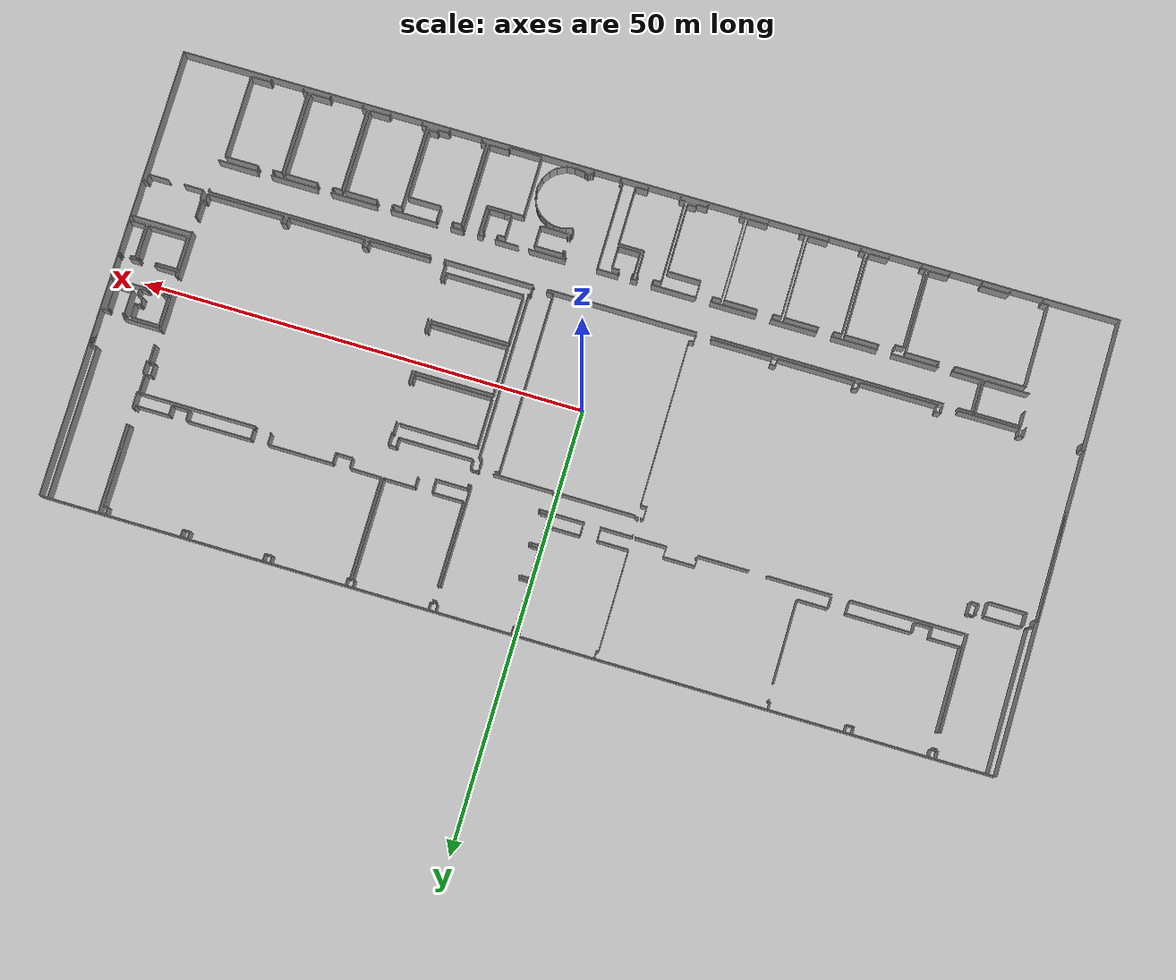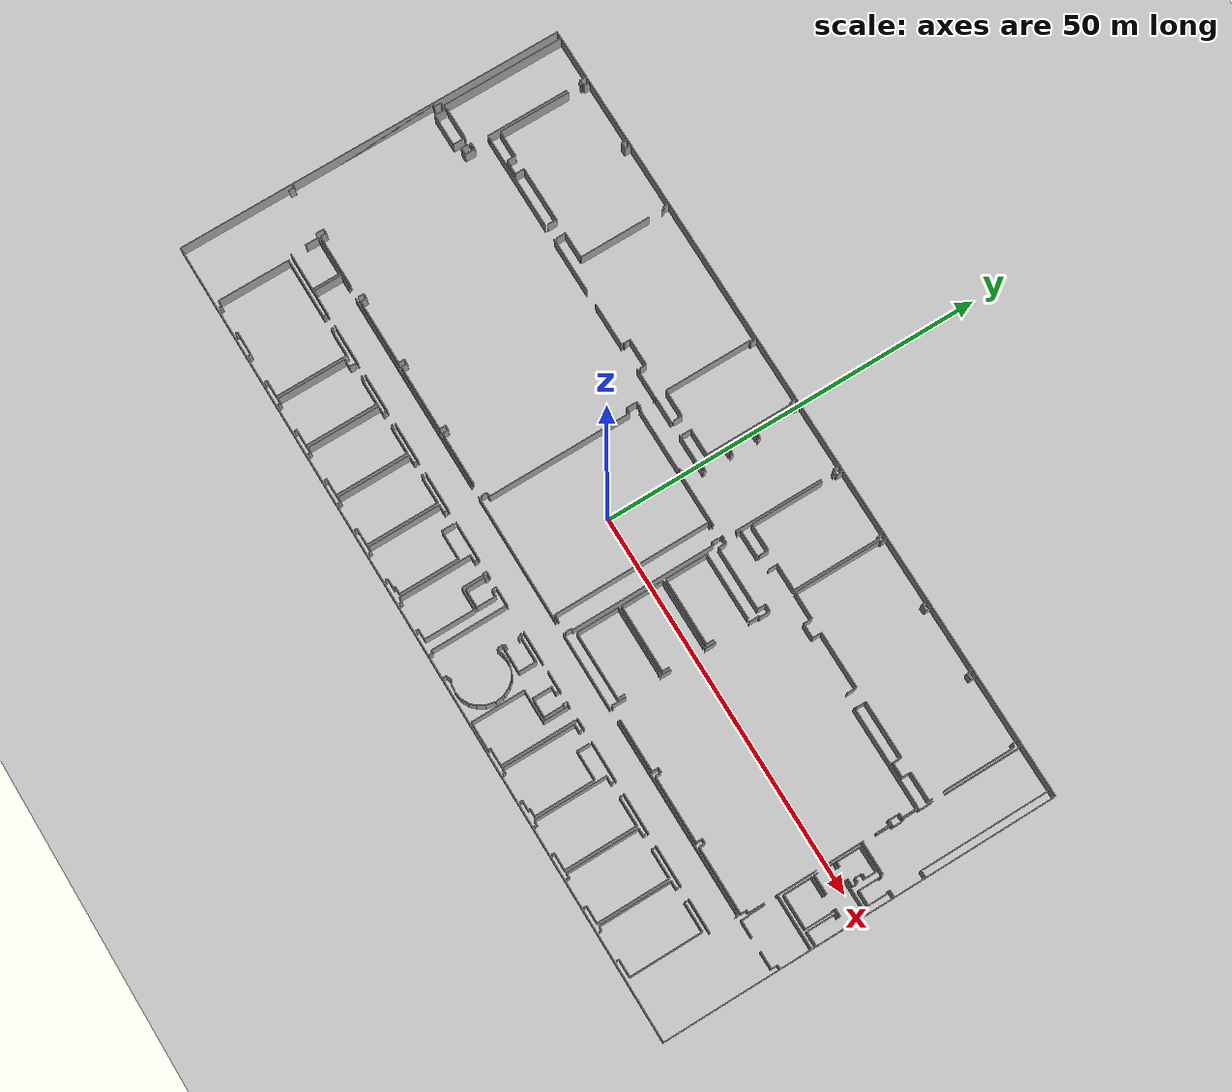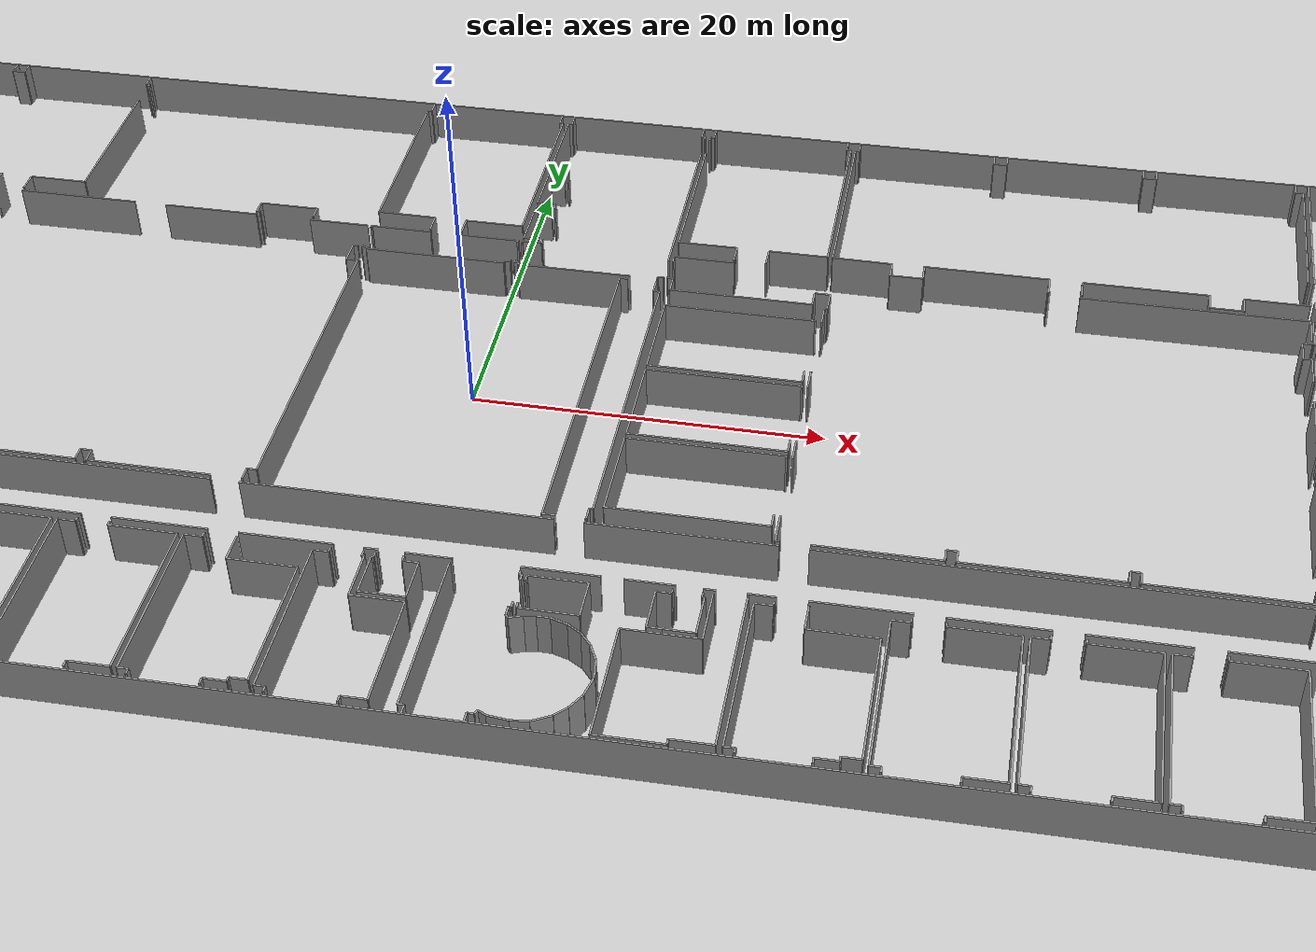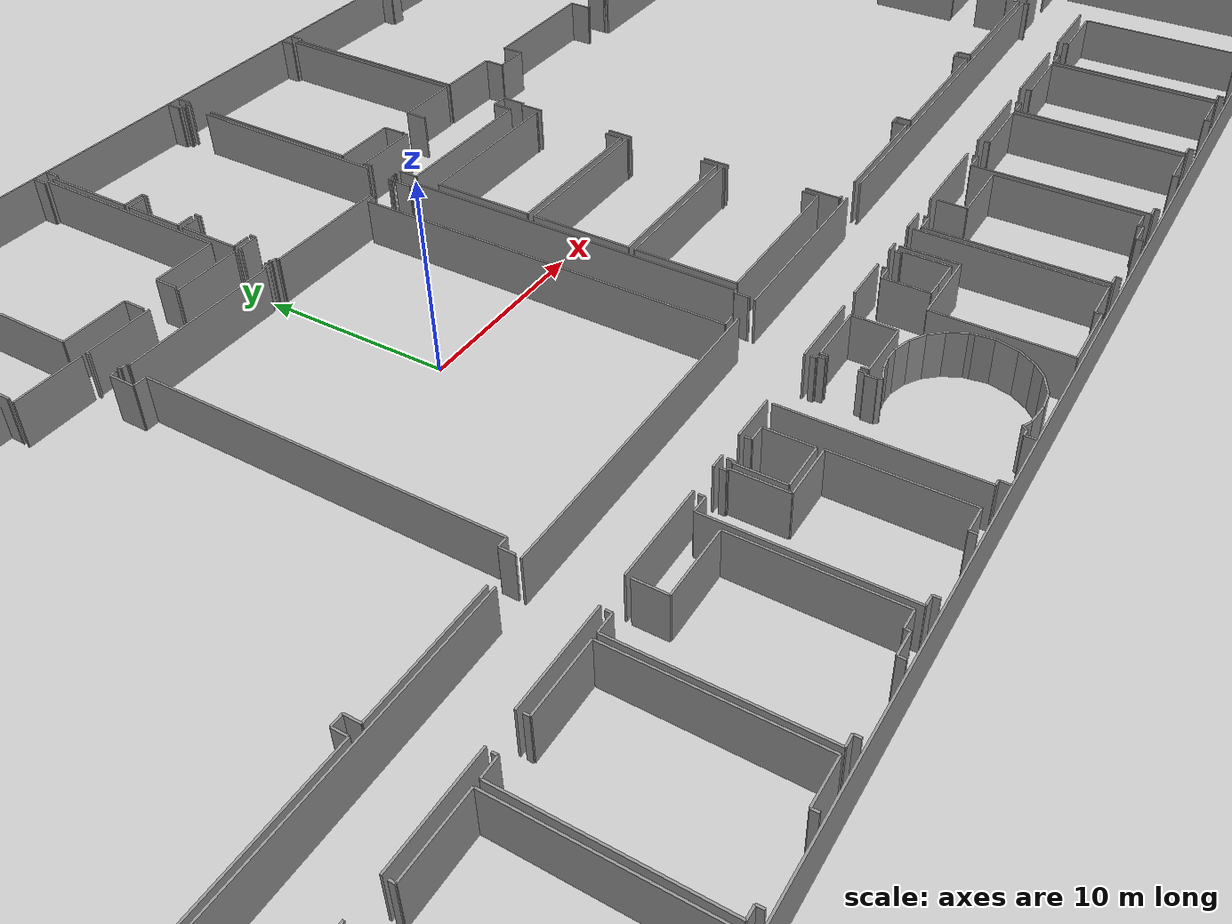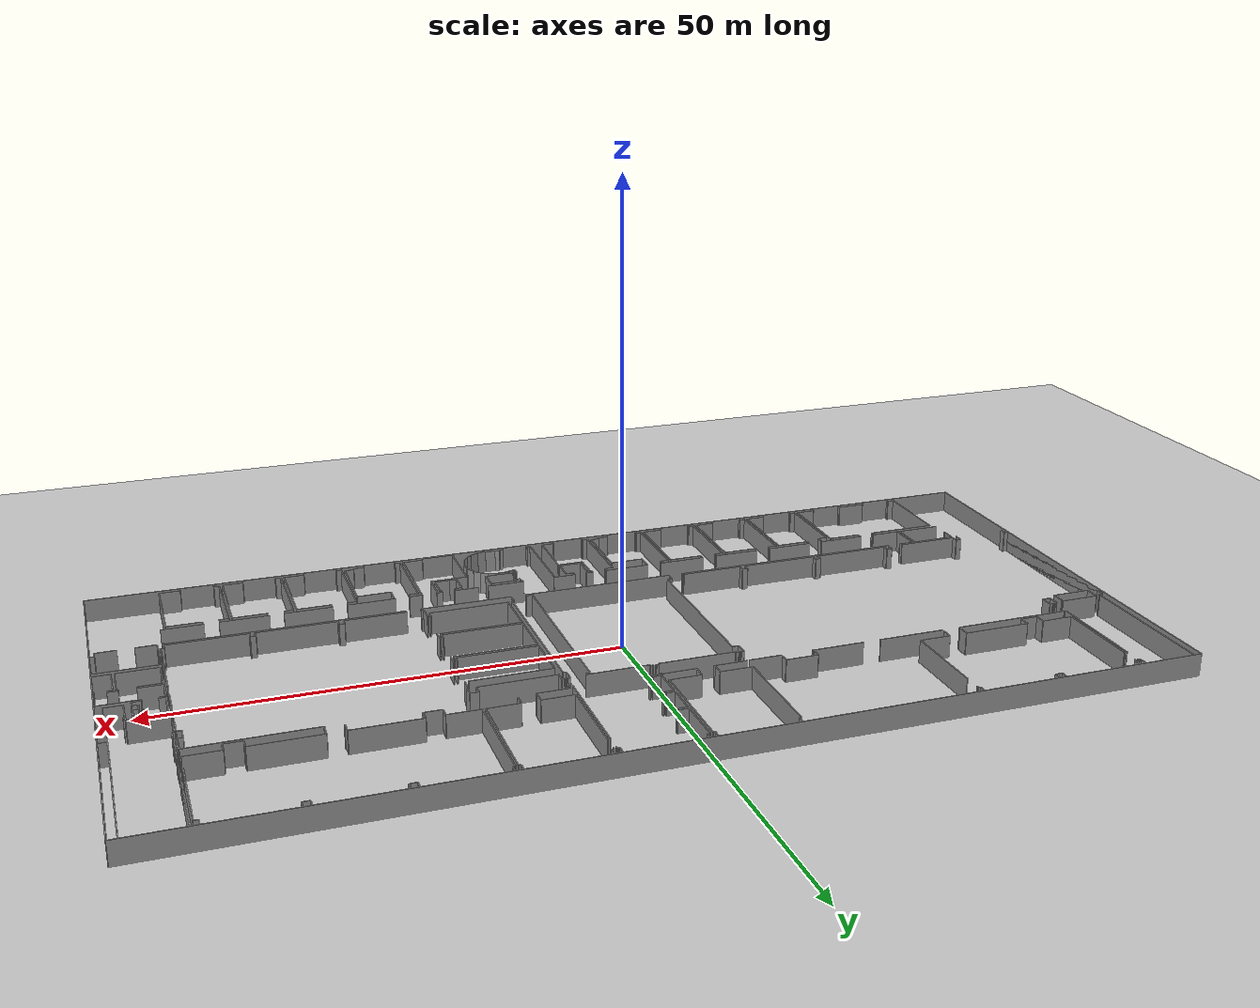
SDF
<sdf version="1.6">
  <world name="default">
    <light name="sun" type="directional">
      <cast_shadows>1</cast_shadows>
      <pose frame="">0 0 10 0 -0 0</pose>
      <diffuse>0.8 0.8 0.8 1</diffuse>
      <specular>0.1 0.1 0.1 1</specular>
      <attenuation>
        <range>1000</range>
        <constant>0.9</constant>
        <linear>0.01</linear>
        <quadratic>0.001</quadratic>
      </attenuation>
      <direction>-0.5 0.5 -1</direction>
    </light>
    <model name="ground_plane">
      <static>1</static>
      <link name="link">
        <collision name="collision">
          <geometry>
            <plane>
              <normal>0 0 1</normal>
              <size>100 100</size>
            </plane>
          </geometry>
          <surface>
            <friction>
              <ode>
                <mu>100</mu>
                <mu2>50</mu2>
              </ode>
              <torsional>
                <ode />
              </torsional>
            </friction>
            <contact>
              <ode />
            </contact>
            <bounce />
          </surface>
          <max_contacts>10</max_contacts>
        </collision>
        <visual name="visual">
          <cast_shadows>0</cast_shadows>
          <geometry>
            <plane>
              <normal>0 0 1</normal>
              <size>100 100</size>
            </plane>
          </geometry>
          <material>
            <script>
              <uri>file://media/materials/scripts/gazebo.material</uri>
              <name>Gazebo/Grey</name>
            </script>
          </material>
        </visual>
        <self_collide>0</self_collide>
        <kinematic>0</kinematic>
        <gravity>1</gravity>
      </link>
    </model>
    <gravity>0 0 -9.8</gravity>
    <magnetic_field>6e-06 2.3e-05 -4.2e-05</magnetic_field>
    <atmosphere type="adiabatic" />
    <physics default="0" name="default_physics" type="ode">
      <max_step_size>0.001</max_step_size>
      <real_time_factor>1</real_time_factor>
      <real_time_update_rate>1000</real_time_update_rate>
    </physics>
    <scene>
      <ambient>0.4 0.4 0.4 1</ambient>
      <background>0.7 0.7 0.7 1</background>
      <shadows>1</shadows>
    </scene>
    <spherical_coordinates>
      <surface_model>EARTH_WGS84</surface_model>
      <latitude_deg>0</latitude_deg>
      <longitude_deg>0</longitude_deg>
      <elevation>0</elevation>
      <heading_deg>0</heading_deg>
    </spherical_coordinates>
  <model name="50045367">
		<static>1</static>
		<link name="Wall_0">
			<collision name="Wall_0_Collision">
				<geometry>
					<box>
						<size>16.0621728746 0.1 2.5</size>
					</box>
				</geometry>
				<pose frame="">8.03108643732 0 1.25 0 0 0</pose>
			</collision>
			<visual name="Wall_0_Visual">
				<pose frame="">8.03108643732 0 1.25 0 0 0</pose>
				<geometry>
					<box>
						<size>16.0621728746 0.1 2.5</size>
					</box>
				</geometry>
				<material>
					<script>
						<uri>file://media/materials/scripts/gazebo.material</uri>
						<name>Gazebo/Grey</name>
					</script>
					<ambient>1 1 1 1</ambient>
				</material>
			</visual>
			<pose frame="">0.892448803293 -16.070430408 0 0 0 1.57079632679</pose>
		</link>
		<link name="Wall_1">
			<collision name="Wall_1_Collision">
				<geometry>
					<box>
						<size>0.82905635449 0.1 2.5</size>
					</box>
				</geometry>
				<pose frame="">0.414528177245 0 1.25 0 0 0</pose>
			</collision>
			<visual name="Wall_1_Visual">
				<pose frame="">0.414528177245 0 1.25 0 0 0</pose>
				<geometry>
					<box>
						<size>0.82905635449 0.1 2.5</size>
					</box>
				</geometry>
				<material>
					<script>
						<uri>file://media/materials/scripts/gazebo.material</uri>
						<name>Gazebo/Grey</name>
					</script>
					<ambient>1 1 1 1</ambient>
				</material>
			</visual>
			<pose frame="">6.62203363992 -0.00825753341125 0 0 0 -1.57079632679</pose>
		</link>
		<link name="Wall_2">
			<collision name="Wall_2_Collision">
				<geometry>
					<box>
						<size>0.197672645968 0.1 2.5</size>
					</box>
				</geometry>
				<pose frame="">0.0988363229839 0 1.25 0 0 0</pose>
			</collision>
			<visual name="Wall_2_Visual">
				<pose frame="">0.0988363229839 0 1.25 0 0 0</pose>
				<geometry>
					<box>
						<size>0.197672645968 0.1 2.5</size>
					</box>
				</geometry>
				<material>
					<script>
						<uri>file://media/materials/scripts/gazebo.material</uri>
						<name>Gazebo/Grey</name>
					</script>
					<ambient>1 1 1 1</ambient>
				</material>
			</visual>
			<pose frame="">6.62203363992 -0.837313887901 0 0 0 0.0</pose>
		</link>
		<link name="Wall_3">
			<collision name="Wall_3_Collision">
				<geometry>
					<box>
						<size>0.243279638193 0.1 2.5</size>
					</box>
				</geometry>
				<pose frame="">0.121639819096 0 1.25 0 0 0</pose>
			</collision>
			<visual name="Wall_3_Visual">
				<pose frame="">0.121639819096 0 1.25 0 0 0</pose>
				<geometry>
					<box>
						<size>0.243279638193 0.1 2.5</size>
					</box>
				</geometry>
				<material>
					<script>
						<uri>file://media/materials/scripts/gazebo.material</uri>
						<name>Gazebo/Grey</name>
					</script>
					<ambient>1 1 1 1</ambient>
				</material>
			</visual>
			<pose frame="">6.81970628589 -0.837313887901 0 0 0 -1.57079632679</pose>
		</link>
		<link name="Wall_4">
			<collision name="Wall_4_Collision">
				<geometry>
					<box>
						<size>0.0541186035876 0.1 2.5</size>
					</box>
				</geometry>
				<pose frame="">0.0270593017938 0 1.25 0 0 0</pose>
			</collision>
			<visual name="Wall_4_Visual">
				<pose frame="">0.0270593017938 0 1.25 0 0 0</pose>
				<geometry>
					<box>
						<size>0.0541186035876 0.1 2.5</size>
					</box>
				</geometry>
				<material>
					<script>
						<uri>file://media/materials/scripts/gazebo.material</uri>
						<name>Gazebo/Grey</name>
					</script>
					<ambient>1 1 1 1</ambient>
				</material>
			</visual>
			<pose frame="">6.81970628589 -1.08059352609 0 0 0 0.0</pose>
		</link>
		<link name="Wall_5">
			<collision name="Wall_5_Collision">
				<geometry>
					<box>
						<size>10.9318308857 0.1 2.5</size>
					</box>
				</geometry>
				<pose frame="">5.46591544286 0 1.25 0 0 0</pose>
			</collision>
			<visual name="Wall_5_Visual">
				<pose frame="">5.46591544286 0 1.25 0 0 0</pose>
				<geometry>
					<box>
						<size>10.9318308857 0.1 2.5</size>
					</box>
				</geometry>
				<material>
					<script>
						<uri>file://media/materials/scripts/gazebo.material</uri>
						<name>Gazebo/Grey</name>
					</script>
					<ambient>1 1 1 1</ambient>
				</material>
			</visual>
			<pose frame="">6.87382488948 -2.82001117943 0 0 0 -1.57079632679</pose>
		</link>
		<link name="Wall_6">
			<collision name="Wall_6_Collision">
				<geometry>
					<box>
						<size>0.116875857513 0.1 2.5</size>
					</box>
				</geometry>
				<pose frame="">0.0584379287565 0 1.25 0 0 0</pose>
			</collision>
			<visual name="Wall_6_Visual">
				<pose frame="">0.0584379287565 0 1.25 0 0 0</pose>
				<geometry>
					<box>
						<size>0.116875857513 0.1 2.5</size>
					</box>
				</geometry>
				<material>
					<script>
						<uri>file://media/materials/scripts/gazebo.material</uri>
						<name>Gazebo/Grey</name>
					</script>
					<ambient>1 1 1 1</ambient>
				</material>
			</visual>
			<pose frame="">6.87382488948 -15.7370801362 0 0 0 -1.57079632679</pose>
		</link>
		<link name="Wall_7">
			<collision name="Wall_7_Collision">
				<geometry>
					<box>
						<size>0.267925199451 0.1 2.5</size>
					</box>
				</geometry>
				<pose frame="">0.133962599726 0 1.25 0 0 0</pose>
			</collision>
			<visual name="Wall_7_Visual">
				<pose frame="">0.133962599726 0 1.25 0 0 0</pose>
				<geometry>
					<box>
						<size>0.267925199451 0.1 2.5</size>
					</box>
				</geometry>
				<material>
					<script>
						<uri>file://media/materials/scripts/gazebo.material</uri>
						<name>Gazebo/Grey</name>
					</script>
					<ambient>1 1 1 1</ambient>
				</material>
			</visual>
			<pose frame="">6.87382488948 -15.8539559937 0 0 0 3.14159265359</pose>
		</link>
		<link name="Wall_8">
			<collision name="Wall_8_Collision">
				<geometry>
					<box>
						<size>0.217236648204 0.1 2.5</size>
					</box>
				</geometry>
				<pose frame="">0.108618324102 0 1.25 0 0 0</pose>
			</collision>
			<visual name="Wall_8_Visual">
				<pose frame="">0.108618324102 0 1.25 0 0 0</pose>
				<geometry>
					<box>
						<size>0.217236648204 0.1 2.5</size>
					</box>
				</geometry>
				<material>
					<script>
						<uri>file://media/materials/scripts/gazebo.material</uri>
						<name>Gazebo/Grey</name>
					</script>
					<ambient>1 1 1 1</ambient>
				</material>
			</visual>
			<pose frame="">6.60589969002 -15.8539559937 0 0 0 -1.57079632679</pose>
		</link>
		<link name="Wall_9">
			<collision name="Wall_9_Collision">
				<geometry>
					<box>
						<size>4.225570405 0.1 2.5</size>
					</box>
				</geometry>
				<pose frame="">2.1127852025 0 1.25 0 0 0</pose>
			</collision>
			<visual name="Wall_9_Visual">
				<pose frame="">2.1127852025 0 1.25 0 0 0</pose>
				<geometry>
					<box>
						<size>4.225570405 0.1 2.5</size>
					</box>
				</geometry>
				<material>
					<script>
						<uri>file://media/materials/scripts/gazebo.material</uri>
						<name>Gazebo/Grey</name>
					</script>
					<ambient>1 1 1 1</ambient>
				</material>
			</visual>
			<pose frame="">5.66085675085 -16.0711926419 0 0 0 3.14159265359</pose>
		</link>
		<link name="Wall_10">
			<collision name="Wall_10_Collision">
				<geometry>
					<box>
						<size>0.0409136510709 0.1 2.5</size>
					</box>
				</geometry>
				<pose frame="">0.0204568255354 0 1.25 0 0 0</pose>
			</collision>
			<visual name="Wall_10_Visual">
				<pose frame="">0.0204568255354 0 1.25 0 0 0</pose>
				<geometry>
					<box>
						<size>0.0409136510709 0.1 2.5</size>
					</box>
				</geometry>
				<material>
					<script>
						<uri>file://media/materials/scripts/gazebo.material</uri>
						<name>Gazebo/Grey</name>
					</script>
					<ambient>1 1 1 1</ambient>
				</material>
			</visual>
			<pose frame="">0.933355353422 -16.0711926419 0 0 0 3.12296126934</pose>
		</link>
		<link name="Wall_11">
			<collision name="Wall_11_Collision">
				<geometry>
					<box>
						<size>9.41130138727 0.1 2.5</size>
					</box>
				</geometry>
				<pose frame="">4.70565069363 0 1.25 0 0 0</pose>
			</collision>
			<visual name="Wall_11_Visual">
				<pose frame="">4.70565069363 0 1.25 0 0 0</pose>
				<geometry>
					<box>
						<size>9.41130138727 0.1 2.5</size>
					</box>
				</geometry>
				<material>
					<script>
						<uri>file://media/materials/scripts/gazebo.material</uri>
						<name>Gazebo/Grey</name>
					</script>
					<ambient>1 1 1 1</ambient>
				</material>
			</visual>
			<pose frame="">7.19891762793 -12.2203872148 0 0 0 1.57079632679</pose>
		</link>
		<link name="Wall_12">
			<collision name="Wall_12_Collision">
				<geometry>
					<box>
						<size>0.055134915392 0.1 2.5</size>
					</box>
				</geometry>
				<pose frame="">0.027567457696 0 1.25 0 0 0</pose>
			</collision>
			<visual name="Wall_12_Visual">
				<pose frame="">0.027567457696 0 1.25 0 0 0</pose>
				<geometry>
					<box>
						<size>0.055134915392 0.1 2.5</size>
					</box>
				</geometry>
				<material>
					<script>
						<uri>file://media/materials/scripts/gazebo.material</uri>
						<name>Gazebo/Grey</name>
					</script>
					<ambient>1 1 1 1</ambient>
				</material>
			</visual>
			<pose frame="">7.19891762793 -2.80908582753 0 0 0 3.14159265359</pose>
		</link>
		<link name="Wall_13">
			<collision name="Wall_13_Collision">
				<geometry>
					<box>
						<size>0.0356979521317 0.1 2.5</size>
					</box>
				</geometry>
				<pose frame="">0.0178489760659 0 1.25 0 0 0</pose>
			</collision>
			<visual name="Wall_13_Visual">
				<pose frame="">0.0178489760659 0 1.25 0 0 0</pose>
				<geometry>
					<box>
						<size>0.0356979521317 0.1 2.5</size>
					</box>
				</geometry>
				<material>
					<script>
						<uri>file://media/materials/scripts/gazebo.material</uri>
						<name>Gazebo/Grey</name>
					</script>
					<ambient>1 1 1 1</ambient>
				</material>
			</visual>
			<pose frame="">7.14378271254 -1.08808882565 0 0 0 0.0</pose>
		</link>
		<link name="Wall_14">
			<collision name="Wall_14_Collision">
				<geometry>
					<box>
						<size>0.271609329742 0.1 2.5</size>
					</box>
				</geometry>
				<pose frame="">0.135804664871 0 1.25 0 0 0</pose>
			</collision>
			<visual name="Wall_14_Visual">
				<pose frame="">0.135804664871 0 1.25 0 0 0</pose>
				<geometry>
					<box>
						<size>0.271609329742 0.1 2.5</size>
					</box>
				</geometry>
				<material>
					<script>
						<uri>file://media/materials/scripts/gazebo.material</uri>
						<name>Gazebo/Grey</name>
					</script>
					<ambient>1 1 1 1</ambient>
				</material>
			</visual>
			<pose frame="">7.17948066467 -1.08808882565 0 0 0 1.57079632679</pose>
		</link>
		<link name="Wall_15">
			<collision name="Wall_15_Collision">
				<geometry>
					<box>
						<size>0.233624676051 0.1 2.5</size>
					</box>
				</geometry>
				<pose frame="">0.116812338025 0 1.25 0 0 0</pose>
			</collision>
			<visual name="Wall_15_Visual">
				<pose frame="">0.116812338025 0 1.25 0 0 0</pose>
				<geometry>
					<box>
						<size>0.233624676051 0.1 2.5</size>
					</box>
				</geometry>
				<material>
					<script>
						<uri>file://media/materials/scripts/gazebo.material</uri>
						<name>Gazebo/Grey</name>
					</script>
					<ambient>1 1 1 1</ambient>
				</material>
			</visual>
			<pose frame="">7.17948066467 -0.816479495909 0 0 0 0.0</pose>
		</link>
		<link name="Wall_16">
			<collision name="Wall_16_Collision">
				<geometry>
					<box>
						<size>0.808476040449 0.1 2.5</size>
					</box>
				</geometry>
				<pose frame="">0.404238020225 0 1.25 0 0 0</pose>
			</collision>
			<visual name="Wall_16_Visual">
				<pose frame="">0.404238020225 0 1.25 0 0 0</pose>
				<geometry>
					<box>
						<size>0.808476040449 0.1 2.5</size>
					</box>
				</geometry>
				<material>
					<script>
						<uri>file://media/materials/scripts/gazebo.material</uri>
						<name>Gazebo/Grey</name>
					</script>
					<ambient>1 1 1 1</ambient>
				</material>
			</visual>
			<pose frame="">7.41310534072 -0.816479495909 0 0 0 1.57079632679</pose>
		</link>
		<link name="Wall_17">
			<collision name="Wall_17_Collision">
				<geometry>
					<box>
						<size>0.808476040449 0.1 2.5</size>
					</box>
				</geometry>
				<pose frame="">0.404238020225 0 1.25 0 0 0</pose>
			</collision>
			<visual name="Wall_17_Visual">
				<pose frame="">0.404238020225 0 1.25 0 0 0</pose>
				<geometry>
					<box>
						<size>0.808476040449 0.1 2.5</size>
					</box>
				</geometry>
				<material>
					<script>
						<uri>file://media/materials/scripts/gazebo.material</uri>
						<name>Gazebo/Grey</name>
					</script>
					<ambient>1 1 1 1</ambient>
				</material>
			</visual>
			<pose frame="">15.857767163 -0.00800345546013 0 0 0 -1.57079632679</pose>
		</link>
		<link name="Wall_18">
			<collision name="Wall_18_Collision">
				<geometry>
					<box>
						<size>0.789547233091 0.1 2.5</size>
					</box>
				</geometry>
				<pose frame="">0.394773616546 0 1.25 0 0 0</pose>
			</collision>
			<visual name="Wall_18_Visual">
				<pose frame="">0.394773616546 0 1.25 0 0 0</pose>
				<geometry>
					<box>
						<size>0.789547233091 0.1 2.5</size>
					</box>
				</geometry>
				<material>
					<script>
						<uri>file://media/materials/scripts/gazebo.material</uri>
						<name>Gazebo/Grey</name>
					</script>
					<ambient>1 1 1 1</ambient>
				</material>
			</visual>
			<pose frame="">15.857767163 -0.816479495909 0 0 0 0.0</pose>
		</link>
		<link name="Wall_19">
			<collision name="Wall_19_Collision">
				<geometry>
					<box>
						<size>0.808476040449 0.1 2.5</size>
					</box>
				</geometry>
				<pose frame="">0.404238020225 0 1.25 0 0 0</pose>
			</collision>
			<visual name="Wall_19_Visual">
				<pose frame="">0.404238020225 0 1.25 0 0 0</pose>
				<geometry>
					<box>
						<size>0.808476040449 0.1 2.5</size>
					</box>
				</geometry>
				<material>
					<script>
						<uri>file://media/materials/scripts/gazebo.material</uri>
						<name>Gazebo/Grey</name>
					</script>
					<ambient>1 1 1 1</ambient>
				</material>
			</visual>
			<pose frame="">16.6473143961 -0.816479495909 0 0 0 1.57079632679</pose>
		</link>
		<link name="Wall_20">
			<collision name="Wall_20_Collision">
				<geometry>
					<box>
						<size>0.819528431323 0.1 2.5</size>
					</box>
				</geometry>
				<pose frame="">0.409764215661 0 1.25 0 0 0</pose>
			</collision>
			<visual name="Wall_20_Visual">
				<pose frame="">0.409764215661 0 1.25 0 0 0</pose>
				<geometry>
					<box>
						<size>0.819528431323 0.1 2.5</size>
					</box>
				</geometry>
				<material>
					<script>
						<uri>file://media/materials/scripts/gazebo.material</uri>
						<name>Gazebo/Grey</name>
					</script>
					<ambient>1 1 1 1</ambient>
				</material>
			</visual>
			<pose frame="">25.0961685045 -0.00800345546013 0 0 0 -1.57079632679</pose>
		</link>
		<link name="Wall_21">
			<collision name="Wall_21_Collision">
				<geometry>
					<box>
						<size>0.229305350882 0.1 2.5</size>
					</box>
				</geometry>
				<pose frame="">0.114652675441 0 1.25 0 0 0</pose>
			</collision>
			<visual name="Wall_21_Visual">
				<pose frame="">0.114652675441 0 1.25 0 0 0</pose>
				<geometry>
					<box>
						<size>0.229305350882 0.1 2.5</size>
					</box>
				</geometry>
				<material>
					<script>
						<uri>file://media/materials/scripts/gazebo.material</uri>
						<name>Gazebo/Grey</name>
					</script>
					<ambient>1 1 1 1</ambient>
				</material>
			</visual>
			<pose frame="">25.0961685045 -0.827531886783 0 0 0 0.0</pose>
		</link>
		<link name="Wall_22">
			<collision name="Wall_22_Collision">
				<geometry>
					<box>
						<size>0.253188678286 0.1 2.5</size>
					</box>
				</geometry>
				<pose frame="">0.126594339143 0 1.25 0 0 0</pose>
			</collision>
			<visual name="Wall_22_Visual">
				<pose frame="">0.126594339143 0 1.25 0 0 0</pose>
				<geometry>
					<box>
						<size>0.253188678286 0.1 2.5</size>
					</box>
				</geometry>
				<material>
					<script>
						<uri>file://media/materials/scripts/gazebo.material</uri>
						<name>Gazebo/Grey</name>
					</script>
					<ambient>1 1 1 1</ambient>
				</material>
			</visual>
			<pose frame="">25.3254738554 -0.827531886783 0 0 0 -1.57079632679</pose>
		</link>
		<link name="Wall_23">
			<collision name="Wall_23_Collision">
				<geometry>
					<box>
						<size>9.36632958992 0.1 2.5</size>
					</box>
				</geometry>
				<pose frame="">4.68316479496 0 1.25 0 0 0</pose>
			</collision>
			<visual name="Wall_23_Visual">
				<pose frame="">4.68316479496 0 1.25 0 0 0</pose>
				<geometry>
					<box>
						<size>9.36632958992 0.1 2.5</size>
					</box>
				</geometry>
				<material>
					<script>
						<uri>file://media/materials/scripts/gazebo.material</uri>
						<name>Gazebo/Grey</name>
					</script>
					<ambient>1 1 1 1</ambient>
				</material>
			</visual>
			<pose frame="">25.3254738554 -2.82903094669 0 0 0 -1.57079632679</pose>
		</link>
		<link name="Wall_24">
			<collision name="Wall_24_Collision">
				<geometry>
					<box>
						<size>3.45863610956 0.1 2.5</size>
					</box>
				</geometry>
				<pose frame="">1.72931805478 0 1.25 0 0 0</pose>
			</collision>
			<visual name="Wall_24_Visual">
				<pose frame="">1.72931805478 0 1.25 0 0 0</pose>
				<geometry>
					<box>
						<size>3.45863610956 0.1 2.5</size>
					</box>
				</geometry>
				<material>
					<script>
						<uri>file://media/materials/scripts/gazebo.material</uri>
						<name>Gazebo/Grey</name>
					</script>
					<ambient>1 1 1 1</ambient>
				</material>
			</visual>
			<pose frame="">25.3254738554 -12.1953605366 0 0 0 3.14159265359</pose>
		</link>
		<link name="Wall_25">
			<collision name="Wall_25_Collision">
				<geometry>
					<box>
						<size>1.22795873774 0.1 2.5</size>
					</box>
				</geometry>
				<pose frame="">0.61397936887 0 1.25 0 0 0</pose>
			</collision>
			<visual name="Wall_25_Visual">
				<pose frame="">0.61397936887 0 1.25 0 0 0</pose>
				<geometry>
					<box>
						<size>1.22795873774 0.1 2.5</size>
					</box>
				</geometry>
				<material>
					<script>
						<uri>file://media/materials/scripts/gazebo.material</uri>
						<name>Gazebo/Grey</name>
					</script>
					<ambient>1 1 1 1</ambient>
				</material>
			</visual>
			<pose frame="">21.8668377458 -12.1953605366 0 0 0 -1.57079632679</pose>
		</link>
		<link name="Wall_26">
			<collision name="Wall_26_Collision">
				<geometry>
					<box>
						<size>1.21957416535 0.1 2.5</size>
					</box>
				</geometry>
				<pose frame="">0.609787082677 0 1.25 0 0 0</pose>
			</collision>
			<visual name="Wall_26_Visual">
				<pose frame="">0.609787082677 0 1.25 0 0 0</pose>
				<geometry>
					<box>
						<size>1.21957416535 0.1 2.5</size>
					</box>
				</geometry>
				<material>
					<script>
						<uri>file://media/materials/scripts/gazebo.material</uri>
						<name>Gazebo/Grey</name>
					</script>
					<ambient>1 1 1 1</ambient>
				</material>
			</visual>
			<pose frame="">19.9122160679 -13.4233192744 0 0 0 1.57079632679</pose>
		</link>
		<link name="Wall_27">
			<collision name="Wall_27_Collision">
				<geometry>
					<box>
						<size>7.32557548656 0.1 2.5</size>
					</box>
				</geometry>
				<pose frame="">3.66278774328 0 1.25 0 0 0</pose>
			</collision>
			<visual name="Wall_27_Visual">
				<pose frame="">3.66278774328 0 1.25 0 0 0</pose>
				<geometry>
					<box>
						<size>7.32557548656 0.1 2.5</size>
					</box>
				</geometry>
				<material>
					<script>
						<uri>file://media/materials/scripts/gazebo.material</uri>
						<name>Gazebo/Grey</name>
					</script>
					<ambient>1 1 1 1</ambient>
				</material>
			</visual>
			<pose frame="">19.9122160679 -12.203745109 0 0 0 3.14159265359</pose>
		</link>
		<link name="Wall_28">
			<collision name="Wall_28_Collision">
				<geometry>
					<box>
						<size>1.1777783424 0.1 2.5</size>
					</box>
				</geometry>
				<pose frame="">0.588889171198 0 1.25 0 0 0</pose>
			</collision>
			<visual name="Wall_28_Visual">
				<pose frame="">0.588889171198 0 1.25 0 0 0</pose>
				<geometry>
					<box>
						<size>1.1777783424 0.1 2.5</size>
					</box>
				</geometry>
				<material>
					<script>
						<uri>file://media/materials/scripts/gazebo.material</uri>
						<name>Gazebo/Grey</name>
					</script>
					<ambient>1 1 1 1</ambient>
				</material>
			</visual>
			<pose frame="">12.5866405813 -12.203745109 0 0 0 -1.57079632679</pose>
		</link>
		<link name="Wall_29">
			<collision name="Wall_29_Collision">
				<geometry>
					<box>
						<size>1.92121042736 0.1 2.5</size>
					</box>
				</geometry>
				<pose frame="">0.96060521368 0 1.25 0 0 0</pose>
			</collision>
			<visual name="Wall_29_Visual">
				<pose frame="">0.96060521368 0 1.25 0 0 0</pose>
				<geometry>
					<box>
						<size>1.92121042736 0.1 2.5</size>
					</box>
				</geometry>
				<material>
					<script>
						<uri>file://media/materials/scripts/gazebo.material</uri>
						<name>Gazebo/Grey</name>
					</script>
					<ambient>1 1 1 1</ambient>
				</material>
			</visual>
			<pose frame="">12.5866405813 -13.3815234514 0 0 0 3.14159265359</pose>
		</link>
		<link name="Wall_30">
			<collision name="Wall_30_Collision">
				<geometry>
					<box>
						<size>1.16939377001 0.1 2.5</size>
					</box>
				</geometry>
				<pose frame="">0.584696885004 0 1.25 0 0 0</pose>
			</collision>
			<visual name="Wall_30_Visual">
				<pose frame="">0.584696885004 0 1.25 0 0 0</pose>
				<geometry>
					<box>
						<size>1.16939377001 0.1 2.5</size>
					</box>
				</geometry>
				<material>
					<script>
						<uri>file://media/materials/scripts/gazebo.material</uri>
						<name>Gazebo/Grey</name>
					</script>
					<ambient>1 1 1 1</ambient>
				</material>
			</visual>
			<pose frame="">10.665430154 -13.3815234514 0 0 0 1.57079632679</pose>
		</link>
		<link name="Wall_31">
			<collision name="Wall_31_Collision">
				<geometry>
					<box>
						<size>3.46652236111 0.1 2.5</size>
					</box>
				</geometry>
				<pose frame="">1.73326118055 0 1.25 0 0 0</pose>
			</collision>
			<visual name="Wall_31_Visual">
				<pose frame="">1.73326118055 0 1.25 0 0 0</pose>
				<geometry>
					<box>
						<size>3.46652236111 0.1 2.5</size>
					</box>
				</geometry>
				<material>
					<script>
						<uri>file://media/materials/scripts/gazebo.material</uri>
						<name>Gazebo/Grey</name>
					</script>
					<ambient>1 1 1 1</ambient>
				</material>
			</visual>
			<pose frame="">10.665430154 -12.2121296814 0 0 0 -3.13921057139</pose>
		</link>
		<link name="Wall_32">
			<collision name="Wall_32_Collision">
				<geometry>
					<box>
						<size>11.3834544438 0.1 2.5</size>
					</box>
				</geometry>
				<pose frame="">5.69172722191 0 1.25 0 0 0</pose>
			</collision>
			<visual name="Wall_32_Visual">
				<pose frame="">5.69172722191 0 1.25 0 0 0</pose>
				<geometry>
					<box>
						<size>11.3834544438 0.1 2.5</size>
					</box>
				</geometry>
				<material>
					<script>
						<uri>file://media/materials/scripts/gazebo.material</uri>
						<name>Gazebo/Grey</name>
					</script>
					<ambient>1 1 1 1</ambient>
				</material>
			</visual>
			<pose frame="">44.1388027847 -12.2188627471 0 0 0 1.57079632679</pose>
		</link>
		<link name="Wall_33">
			<collision name="Wall_33_Collision">
				<geometry>
					<box>
						<size>0.248742314142 0.1 2.5</size>
					</box>
				</geometry>
				<pose frame="">0.124371157071 0 1.25 0 0 0</pose>
			</collision>
			<visual name="Wall_33_Visual">
				<pose frame="">0.124371157071 0 1.25 0 0 0</pose>
				<geometry>
					<box>
						<size>0.248742314142 0.1 2.5</size>
					</box>
				</geometry>
				<material>
					<script>
						<uri>file://media/materials/scripts/gazebo.material</uri>
						<name>Gazebo/Grey</name>
					</script>
					<ambient>1 1 1 1</ambient>
				</material>
			</visual>
			<pose frame="">44.1388027847 -0.835408303267 0 0 0 0.0</pose>
		</link>
		<link name="Wall_34">
			<collision name="Wall_34_Collision">
				<geometry>
					<box>
						<size>0.821052899029 0.1 2.5</size>
					</box>
				</geometry>
				<pose frame="">0.410526449515 0 1.25 0 0 0</pose>
			</collision>
			<visual name="Wall_34_Visual">
				<pose frame="">0.410526449515 0 1.25 0 0 0</pose>
				<geometry>
					<box>
						<size>0.821052899029 0.1 2.5</size>
					</box>
				</geometry>
				<material>
					<script>
						<uri>file://media/materials/scripts/gazebo.material</uri>
						<name>Gazebo/Grey</name>
					</script>
					<ambient>1 1 1 1</ambient>
				</material>
			</visual>
			<pose frame="">44.3875450988 -0.835408303267 0 0 0 1.57079632679</pose>
		</link>
		<link name="Wall_35">
			<collision name="Wall_35_Collision">
				<geometry>
					<box>
						<size>0.822704405712 0.1 2.5</size>
					</box>
				</geometry>
				<pose frame="">0.411352202856 0 1.25 0 0 0</pose>
			</collision>
			<visual name="Wall_35_Visual">
				<pose frame="">0.411352202856 0 1.25 0 0 0</pose>
				<geometry>
					<box>
						<size>0.822704405712 0.1 2.5</size>
					</box>
				</geometry>
				<material>
					<script>
						<uri>file://media/materials/scripts/gazebo.material</uri>
						<name>Gazebo/Grey</name>
					</script>
					<ambient>1 1 1 1</ambient>
				</material>
			</visual>
			<pose frame="">52.8263631282 -0.014355404238 0 0 0 -1.57079632679</pose>
		</link>
		<link name="Wall_36">
			<collision name="Wall_36_Collision">
				<geometry>
					<box>
						<size>0.218252960008 0.1 2.5</size>
					</box>
				</geometry>
				<pose frame="">0.109126480004 0 1.25 0 0 0</pose>
			</collision>
			<visual name="Wall_36_Visual">
				<pose frame="">0.109126480004 0 1.25 0 0 0</pose>
				<geometry>
					<box>
						<size>0.218252960008 0.1 2.5</size>
					</box>
				</geometry>
				<material>
					<script>
						<uri>file://media/materials/scripts/gazebo.material</uri>
						<name>Gazebo/Grey</name>
					</script>
					<ambient>1 1 1 1</ambient>
				</material>
			</visual>
			<pose frame="">52.8263631282 -0.83705980995 0 0 0 0.0</pose>
		</link>
		<link name="Wall_37">
			<collision name="Wall_37_Collision">
				<geometry>
					<box>
						<size>11.3736724427 0.1 2.5</size>
					</box>
				</geometry>
				<pose frame="">5.68683622135 0 1.25 0 0 0</pose>
			</collision>
			<visual name="Wall_37_Visual">
				<pose frame="">5.68683622135 0 1.25 0 0 0</pose>
				<geometry>
					<box>
						<size>11.3736724427 0.1 2.5</size>
					</box>
				</geometry>
				<material>
					<script>
						<uri>file://media/materials/scripts/gazebo.material</uri>
						<name>Gazebo/Grey</name>
					</script>
					<ambient>1 1 1 1</ambient>
				</material>
			</visual>
			<pose frame="">53.0446160882 -0.83705980995 0 0 0 -1.57079632679</pose>
		</link>
		<link name="Wall_38">
			<collision name="Wall_38_Collision">
				<geometry>
					<box>
						<size>3.46587733117 0.1 2.5</size>
					</box>
				</geometry>
				<pose frame="">1.73293866558 0 1.25 0 0 0</pose>
			</collision>
			<visual name="Wall_38_Visual">
				<pose frame="">1.73293866558 0 1.25 0 0 0</pose>
				<geometry>
					<box>
						<size>3.46587733117 0.1 2.5</size>
					</box>
				</geometry>
				<material>
					<script>
						<uri>file://media/materials/scripts/gazebo.material</uri>
						<name>Gazebo/Grey</name>
					</script>
					<ambient>1 1 1 1</ambient>
				</material>
			</visual>
			<pose frame="">53.0446160882 -12.2107322527 0 0 0 3.14159265359</pose>
		</link>
		<link name="Wall_39">
			<collision name="Wall_39_Collision">
				<geometry>
					<box>
						<size>1.20585395599 0.1 2.5</size>
					</box>
				</geometry>
				<pose frame="">0.602926977997 0 1.25 0 0 0</pose>
			</collision>
			<visual name="Wall_39_Visual">
				<pose frame="">0.602926977997 0 1.25 0 0 0</pose>
				<geometry>
					<box>
						<size>1.20585395599 0.1 2.5</size>
					</box>
				</geometry>
				<material>
					<script>
						<uri>file://media/materials/scripts/gazebo.material</uri>
						<name>Gazebo/Grey</name>
					</script>
					<ambient>1 1 1 1</ambient>
				</material>
			</visual>
			<pose frame="">49.5787387571 -12.2107322527 0 0 0 -1.57079632679</pose>
		</link>
		<link name="Wall_40">
			<collision name="Wall_40_Collision">
				<geometry>
					<box>
						<size>1.18832257737 0.1 2.5</size>
					</box>
				</geometry>
				<pose frame="">0.594161288683 0 1.25 0 0 0</pose>
			</collision>
			<visual name="Wall_40_Visual">
				<pose frame="">0.594161288683 0 1.25 0 0 0</pose>
				<geometry>
					<box>
						<size>1.18832257737 0.1 2.5</size>
					</box>
				</geometry>
				<material>
					<script>
						<uri>file://media/materials/scripts/gazebo.material</uri>
						<name>Gazebo/Grey</name>
					</script>
					<ambient>1 1 1 1</ambient>
				</material>
			</visual>
			<pose frame="">47.6478733675 -13.4165862086 0 0 0 1.57079632679</pose>
		</link>
		<link name="Wall_41">
			<collision name="Wall_41_Collision">
				<geometry>
					<box>
						<size>3.50908317543 0.1 2.5</size>
					</box>
				</geometry>
				<pose frame="">1.75454158771 0 1.25 0 0 0</pose>
			</collision>
			<visual name="Wall_41_Visual">
				<pose frame="">1.75454158771 0 1.25 0 0 0</pose>
				<geometry>
					<box>
						<size>3.50908317543 0.1 2.5</size>
					</box>
				</geometry>
				<material>
					<script>
						<uri>file://media/materials/scripts/gazebo.material</uri>
						<name>Gazebo/Grey</name>
					</script>
					<ambient>1 1 1 1</ambient>
				</material>
			</visual>
			<pose frame="">47.6478733675 -12.2282636313 0 0 0 3.13891363603</pose>
		</link>
		<link name="Wall_42">
			<collision name="Wall_42_Collision">
				<geometry>
					<box>
						<size>3.34950962955 0.1 2.5</size>
					</box>
				</geometry>
				<pose frame="">1.67475481478 0 1.25 0 0 0</pose>
			</collision>
			<visual name="Wall_42_Visual">
				<pose frame="">1.67475481478 0 1.25 0 0 0</pose>
				<geometry>
					<box>
						<size>3.34950962955 0.1 2.5</size>
					</box>
				</geometry>
				<material>
					<script>
						<uri>file://media/materials/scripts/gazebo.material</uri>
						<name>Gazebo/Grey</name>
					</script>
					<ambient>1 1 1 1</ambient>
				</material>
			</visual>
			<pose frame="">53.4071853245 -9.65597845419 0 0 0 1.57079632679</pose>
		</link>
		<link name="Wall_43">
			<collision name="Wall_43_Collision">
				<geometry>
					<box>
						<size>0.927892677473 0.1 2.5</size>
					</box>
				</geometry>
				<pose frame="">0.463946338737 0 1.25 0 0 0</pose>
			</collision>
			<visual name="Wall_43_Visual">
				<pose frame="">0.463946338737 0 1.25 0 0 0</pose>
				<geometry>
					<box>
						<size>0.927892677473 0.1 2.5</size>
					</box>
				</geometry>
				<material>
					<script>
						<uri>file://media/materials/scripts/gazebo.material</uri>
						<name>Gazebo/Grey</name>
					</script>
					<ambient>1 1 1 1</ambient>
				</material>
			</visual>
			<pose frame="">53.4071853245 -6.30646882464 0 0 0 0.0</pose>
		</link>
		<link name="Wall_44">
			<collision name="Wall_44_Collision">
				<geometry>
					<box>
						<size>0.928028550876 0.1 2.5</size>
					</box>
				</geometry>
				<pose frame="">0.464014275438 0 1.25 0 0 0</pose>
			</collision>
			<visual name="Wall_44_Visual">
				<pose frame="">0.464014275438 0 1.25 0 0 0</pose>
				<geometry>
					<box>
						<size>0.928028550876 0.1 2.5</size>
					</box>
				</geometry>
				<material>
					<script>
						<uri>file://media/materials/scripts/gazebo.material</uri>
						<name>Gazebo/Grey</name>
					</script>
					<ambient>1 1 1 1</ambient>
				</material>
			</visual>
			<pose frame="">54.3350780019 -9.64009858225 0 0 0 -3.12448041392</pose>
		</link>
		<link name="Wall_45">
			<collision name="Wall_45_Collision">
				<geometry>
					<box>
						<size>3.38812947812 0.1 2.5</size>
					</box>
				</geometry>
				<pose frame="">1.69406473906 0 1.25 0 0 0</pose>
			</collision>
			<visual name="Wall_45_Visual">
				<pose frame="">1.69406473906 0 1.25 0 0 0</pose>
				<geometry>
					<box>
						<size>3.38812947812 0.1 2.5</size>
					</box>
				</geometry>
				<material>
					<script>
						<uri>file://media/materials/scripts/gazebo.material</uri>
						<name>Gazebo/Grey</name>
					</script>
					<ambient>1 1 1 1</ambient>
				</material>
			</visual>
			<pose frame="">53.4104883378 -13.3705980995 0 0 0 1.57079632679</pose>
		</link>
		<link name="Wall_46">
			<collision name="Wall_46_Collision">
				<geometry>
					<box>
						<size>0.910869454749 0.1 2.5</size>
					</box>
				</geometry>
				<pose frame="">0.455434727374 0 1.25 0 0 0</pose>
			</collision>
			<visual name="Wall_46_Visual">
				<pose frame="">0.455434727374 0 1.25 0 0 0</pose>
				<geometry>
					<box>
						<size>0.910869454749 0.1 2.5</size>
					</box>
				</geometry>
				<material>
					<script>
						<uri>file://media/materials/scripts/gazebo.material</uri>
						<name>Gazebo/Grey</name>
					</script>
					<ambient>1 1 1 1</ambient>
				</material>
			</visual>
			<pose frame="">53.4104883378 -9.98246862137 0 0 0 0.0</pose>
		</link>
		<link name="Wall_47">
			<collision name="Wall_47_Collision">
				<geometry>
					<box>
						<size>0.910929021146 0.1 2.5</size>
					</box>
				</geometry>
				<pose frame="">0.455464510573 0 1.25 0 0 0</pose>
			</collision>
			<visual name="Wall_47_Visual">
				<pose frame="">0.455464510573 0 1.25 0 0 0</pose>
				<geometry>
					<box>
						<size>0.910929021146 0.1 2.5</size>
					</box>
				</geometry>
				<material>
					<script>
						<uri>file://media/materials/scripts/gazebo.material</uri>
						<name>Gazebo/Grey</name>
					</script>
					<ambient>1 1 1 1</ambient>
				</material>
			</visual>
			<pose frame="">54.3213577926 -13.3601809035 0 0 0 -3.13015661102</pose>
		</link>
		<link name="Wall_48">
			<collision name="Wall_48_Collision">
				<geometry>
					<box>
						<size>3.37758524315 0.1 2.5</size>
					</box>
				</geometry>
				<pose frame="">1.68879262158 0 1.25 0 0 0</pose>
			</collision>
			<visual name="Wall_48_Visual">
				<pose frame="">1.68879262158 0 1.25 0 0 0</pose>
				<geometry>
					<box>
						<size>3.37758524315 0.1 2.5</size>
					</box>
				</geometry>
				<material>
					<script>
						<uri>file://media/materials/scripts/gazebo.material</uri>
						<name>Gazebo/Grey</name>
					</script>
					<ambient>1 1 1 1</ambient>
				</material>
			</visual>
			<pose frame="">53.4074394024 -13.3684384369 0 0 0 1.57079632679</pose>
		</link>
		<link name="Wall_49">
			<collision name="Wall_49_Collision">
				<geometry>
					<box>
						<size>0.929798262107 0.1 2.5</size>
					</box>
				</geometry>
				<pose frame="">0.464899131053 0 1.25 0 0 0</pose>
			</collision>
			<visual name="Wall_49_Visual">
				<pose frame="">0.464899131053 0 1.25 0 0 0</pose>
				<geometry>
					<box>
						<size>0.929798262107 0.1 2.5</size>
					</box>
				</geometry>
				<material>
					<script>
						<uri>file://media/materials/scripts/gazebo.material</uri>
						<name>Gazebo/Grey</name>
					</script>
					<ambient>1 1 1 1</ambient>
				</material>
			</visual>
			<pose frame="">53.4074394024 -9.99085319376 0 0 0 0.0</pose>
		</link>
		<link name="Wall_50">
			<collision name="Wall_50_Collision">
				<geometry>
					<box>
						<size>0.930031655432 0.1 2.5</size>
					</box>
				</geometry>
				<pose frame="">0.465015827716 0 1.25 0 0 0</pose>
			</collision>
			<visual name="Wall_50_Visual">
				<pose frame="">0.465015827716 0 1.25 0 0 0</pose>
				<geometry>
					<box>
						<size>0.930031655432 0.1 2.5</size>
					</box>
				</geometry>
				<material>
					<script>
						<uri>file://media/materials/scripts/gazebo.material</uri>
						<name>Gazebo/Grey</name>
					</script>
					<ambient>1 1 1 1</ambient>
				</material>
			</visual>
			<pose frame="">54.3372376645 -13.3476040449 0 0 0 -3.11918896996</pose>
		</link>
		<link name="Wall_51">
			<collision name="Wall_51_Collision">
				<geometry>
					<box>
						<size>5.15943391432 0.1 2.5</size>
					</box>
				</geometry>
				<pose frame="">2.57971695716 0 1.25 0 0 0</pose>
			</collision>
			<visual name="Wall_51_Visual">
				<pose frame="">2.57971695716 0 1.25 0 0 0</pose>
				<geometry>
					<box>
						<size>5.15943391432 0.1 2.5</size>
					</box>
				</geometry>
				<material>
					<script>
						<uri>file://media/materials/scripts/gazebo.material</uri>
						<name>Gazebo/Grey</name>
					</script>
					<ambient>1 1 1 1</ambient>
				</material>
			</visual>
			<pose frame="">53.3932110371 -5.96968850043 0 0 0 1.57079632679</pose>
		</link>
		<link name="Wall_52">
			<collision name="Wall_52_Collision">
				<geometry>
					<box>
						<size>0.24023070278 0.1 2.5</size>
					</box>
				</geometry>
				<pose frame="">0.12011535139 0 1.25 0 0 0</pose>
			</collision>
			<visual name="Wall_52_Visual">
				<pose frame="">0.12011535139 0 1.25 0 0 0</pose>
				<geometry>
					<box>
						<size>0.24023070278 0.1 2.5</size>
					</box>
				</geometry>
				<material>
					<script>
						<uri>file://media/materials/scripts/gazebo.material</uri>
						<name>Gazebo/Grey</name>
					</script>
					<ambient>1 1 1 1</ambient>
				</material>
			</visual>
			<pose frame="">53.3932110371 -0.810254586107 0 0 0 0.0</pose>
		</link>
		<link name="Wall_53">
			<collision name="Wall_53_Collision">
				<geometry>
					<box>
						<size>0.810254586107 0.1 2.5</size>
					</box>
				</geometry>
				<pose frame="">0.405127293054 0 1.25 0 0 0</pose>
			</collision>
			<visual name="Wall_53_Visual">
				<pose frame="">0.405127293054 0 1.25 0 0 0</pose>
				<geometry>
					<box>
						<size>0.810254586107 0.1 2.5</size>
					</box>
				</geometry>
				<material>
					<script>
						<uri>file://media/materials/scripts/gazebo.material</uri>
						<name>Gazebo/Grey</name>
					</script>
					<ambient>1 1 1 1</ambient>
				</material>
			</visual>
			<pose frame="">53.6334417399 -0.810254586107 0 0 0 1.57079632679</pose>
		</link>
		<link name="Wall_54">
			<collision name="Wall_54_Collision">
				<geometry>
					<box>
						<size>0.841887291021 0.1 2.5</size>
					</box>
				</geometry>
				<pose frame="">0.42094364551 0 1.25 0 0 0</pose>
			</collision>
			<visual name="Wall_54_Visual">
				<pose frame="">0.42094364551 0 1.25 0 0 0</pose>
				<geometry>
					<box>
						<size>0.841887291021 0.1 2.5</size>
					</box>
				</geometry>
				<material>
					<script>
						<uri>file://media/materials/scripts/gazebo.material</uri>
						<name>Gazebo/Grey</name>
					</script>
					<ambient>1 1 1 1</ambient>
				</material>
			</visual>
			<pose frame="">62.0699730677 -0.0 0 0 0 -1.57079632679</pose>
		</link>
		<link name="Wall_55">
			<collision name="Wall_55_Collision">
				<geometry>
					<box>
						<size>0.215966258448 0.1 2.5</size>
					</box>
				</geometry>
				<pose frame="">0.107983129224 0 1.25 0 0 0</pose>
			</collision>
			<visual name="Wall_55_Visual">
				<pose frame="">0.107983129224 0 1.25 0 0 0</pose>
				<geometry>
					<box>
						<size>0.215966258448 0.1 2.5</size>
					</box>
				</geometry>
				<material>
					<script>
						<uri>file://media/materials/scripts/gazebo.material</uri>
						<name>Gazebo/Grey</name>
					</script>
					<ambient>1 1 1 1</ambient>
				</material>
			</visual>
			<pose frame="">62.0699730677 -0.841887291021 0 0 0 0.0</pose>
		</link>
		<link name="Wall_56">
			<collision name="Wall_56_Collision">
				<geometry>
					<box>
						<size>0.248361197215 0.1 2.5</size>
					</box>
				</geometry>
				<pose frame="">0.124180598608 0 1.25 0 0 0</pose>
			</collision>
			<visual name="Wall_56_Visual">
				<pose frame="">0.124180598608 0 1.25 0 0 0</pose>
				<geometry>
					<box>
						<size>0.248361197215 0.1 2.5</size>
					</box>
				</geometry>
				<material>
					<script>
						<uri>file://media/materials/scripts/gazebo.material</uri>
						<name>Gazebo/Grey</name>
					</script>
					<ambient>1 1 1 1</ambient>
				</material>
			</visual>
			<pose frame="">62.2859393262 -0.841887291021 0 0 0 -1.57079632679</pose>
		</link>
		<link name="Wall_57">
			<collision name="Wall_57_Collision">
				<geometry>
					<box>
						<size>0.0524670969053 0.1 2.5</size>
					</box>
				</geometry>
				<pose frame="">0.0262335484527 0 1.25 0 0 0</pose>
			</collision>
			<visual name="Wall_57_Visual">
				<pose frame="">0.0262335484527 0 1.25 0 0 0</pose>
				<geometry>
					<box>
						<size>0.0524670969053 0.1 2.5</size>
					</box>
				</geometry>
				<material>
					<script>
						<uri>file://media/materials/scripts/gazebo.material</uri>
						<name>Gazebo/Grey</name>
					</script>
					<ambient>1 1 1 1</ambient>
				</material>
			</visual>
			<pose frame="">62.2859393262 -1.09024848824 0 0 0 0.0</pose>
		</link>
		<link name="Wall_58">
			<collision name="Wall_58_Collision">
				<geometry>
					<box>
						<size>0.0763504243102 0.1 2.5</size>
					</box>
				</geometry>
				<pose frame="">0.0381752121551 0 1.25 0 0 0</pose>
			</collision>
			<visual name="Wall_58_Visual">
				<pose frame="">0.0381752121551 0 1.25 0 0 0</pose>
				<geometry>
					<box>
						<size>0.0763504243102 0.1 2.5</size>
					</box>
				</geometry>
				<material>
					<script>
						<uri>file://media/materials/scripts/gazebo.material</uri>
						<name>Gazebo/Grey</name>
					</script>
					<ambient>1 1 1 1</ambient>
				</material>
			</visual>
			<pose frame="">62.3384064231 -1.09024848824 0 0 0 -1.57079632679</pose>
		</link>
		<link name="Wall_59">
			<collision name="Wall_59_Collision">
				<geometry>
					<box>
						<size>11.4584074394 0.1 2.5</size>
					</box>
				</geometry>
				<pose frame="">5.7292037197 0 1.25 0 0 0</pose>
			</collision>
			<visual name="Wall_59_Visual">
				<pose frame="">5.7292037197 0 1.25 0 0 0</pose>
				<geometry>
					<box>
						<size>11.4584074394 0.1 2.5</size>
					</box>
				</geometry>
				<material>
					<script>
						<uri>file://media/materials/scripts/gazebo.material</uri>
						<name>Gazebo/Grey</name>
					</script>
					<ambient>1 1 1 1</ambient>
				</material>
			</visual>
			<pose frame="">62.3384064231 -2.70465978962 0 0 0 -1.57079632679</pose>
		</link>
		<link name="Wall_60">
			<collision name="Wall_60_Collision">
				<geometry>
					<box>
						<size>0.0884191269882 0.1 2.5</size>
					</box>
				</geometry>
				<pose frame="">0.0442095634941 0 1.25 0 0 0</pose>
			</collision>
			<visual name="Wall_60_Visual">
				<pose frame="">0.0442095634941 0 1.25 0 0 0</pose>
				<geometry>
					<box>
						<size>0.0884191269882 0.1 2.5</size>
					</box>
				</geometry>
				<material>
					<script>
						<uri>file://media/materials/scripts/gazebo.material</uri>
						<name>Gazebo/Grey</name>
					</script>
					<ambient>1 1 1 1</ambient>
				</material>
			</visual>
			<pose frame="">62.3384064231 -15.7161187052 0 0 0 -1.57079632679</pose>
		</link>
		<link name="Wall_61">
			<collision name="Wall_61_Collision">
				<geometry>
					<box>
						<size>0.316454088114 0.1 2.5</size>
					</box>
				</geometry>
				<pose frame="">0.158227044057 0 1.25 0 0 0</pose>
			</collision>
			<visual name="Wall_61_Visual">
				<pose frame="">0.158227044057 0 1.25 0 0 0</pose>
				<geometry>
					<box>
						<size>0.316454088114 0.1 2.5</size>
					</box>
				</geometry>
				<material>
					<script>
						<uri>file://media/materials/scripts/gazebo.material</uri>
						<name>Gazebo/Grey</name>
					</script>
					<ambient>1 1 1 1</ambient>
				</material>
			</visual>
			<pose frame="">62.3384064231 -15.8045378322 0 0 0 3.14159265359</pose>
		</link>
		<link name="Wall_62">
			<collision name="Wall_62_Collision">
				<geometry>
					<box>
						<size>0.183190202754 0.1 2.5</size>
					</box>
				</geometry>
				<pose frame="">0.0915951013771 0 1.25 0 0 0</pose>
			</collision>
			<visual name="Wall_62_Visual">
				<pose frame="">0.0915951013771 0 1.25 0 0 0</pose>
				<geometry>
					<box>
						<size>0.183190202754 0.1 2.5</size>
					</box>
				</geometry>
				<material>
					<script>
						<uri>file://media/materials/scripts/gazebo.material</uri>
						<name>Gazebo/Grey</name>
					</script>
					<ambient>1 1 1 1</ambient>
				</material>
			</visual>
			<pose frame="">62.021952335 -15.8045378322 0 0 0 -1.57079632679</pose>
		</link>
		<link name="Wall_63">
			<collision name="Wall_63_Collision">
				<geometry>
					<box>
						<size>0.0567864220743 0.1 2.5</size>
					</box>
				</geometry>
				<pose frame="">0.0283932110371 0 1.25 0 0 0</pose>
			</collision>
			<visual name="Wall_63_Visual">
				<pose frame="">0.0283932110371 0 1.25 0 0 0</pose>
				<geometry>
					<box>
						<size>0.0567864220743 0.1 2.5</size>
					</box>
				</geometry>
				<material>
					<script>
						<uri>file://media/materials/scripts/gazebo.material</uri>
						<name>Gazebo/Grey</name>
					</script>
					<ambient>1 1 1 1</ambient>
				</material>
			</visual>
			<pose frame="">62.021952335 -15.987728035 0 0 0 3.14159265359</pose>
		</link>
		<link name="Wall_64">
			<collision name="Wall_64_Collision">
				<geometry>
					<box>
						<size>6.72671375578 0.1 2.5</size>
					</box>
				</geometry>
				<pose frame="">3.36335687789 0 1.25 0 0 0</pose>
			</collision>
			<visual name="Wall_64_Visual">
				<pose frame="">3.36335687789 0 1.25 0 0 0</pose>
				<geometry>
					<box>
						<size>6.72671375578 0.1 2.5</size>
					</box>
				</geometry>
				<material>
					<script>
						<uri>file://media/materials/scripts/gazebo.material</uri>
						<name>Gazebo/Grey</name>
					</script>
					<ambient>1 1 1 1</ambient>
				</material>
			</visual>
			<pose frame="">60.4051272931 -15.987728035 0 0 0 3.14159265359</pose>
		</link>
		<link name="Wall_65">
			<collision name="Wall_65_Collision">
				<geometry>
					<box>
						<size>0.183190202754 0.1 2.5</size>
					</box>
				</geometry>
				<pose frame="">0.0915951013771 0 1.25 0 0 0</pose>
			</collision>
			<visual name="Wall_65_Visual">
				<pose frame="">0.0915951013771 0 1.25 0 0 0</pose>
				<geometry>
					<box>
						<size>0.183190202754 0.1 2.5</size>
					</box>
				</geometry>
				<material>
					<script>
						<uri>file://media/materials/scripts/gazebo.material</uri>
						<name>Gazebo/Grey</name>
					</script>
					<ambient>1 1 1 1</ambient>
				</material>
			</visual>
			<pose frame="">53.6784135373 -15.987728035 0 0 0 1.57079632679</pose>
		</link>
		<link name="Wall_66">
			<collision name="Wall_66_Collision">
				<geometry>
					<box>
						<size>0.2905381371 0.1 2.5</size>
					</box>
				</geometry>
				<pose frame="">0.14526906855 0 1.25 0 0 0</pose>
			</collision>
			<visual name="Wall_66_Visual">
				<pose frame="">0.14526906855 0 1.25 0 0 0</pose>
				<geometry>
					<box>
						<size>0.2905381371 0.1 2.5</size>
					</box>
				</geometry>
				<material>
					<script>
						<uri>file://media/materials/scripts/gazebo.material</uri>
						<name>Gazebo/Grey</name>
					</script>
					<ambient>1 1 1 1</ambient>
				</material>
			</visual>
			<pose frame="">53.6784135373 -15.8045378322 0 0 0 3.14159265359</pose>
		</link>
		<link name="Wall_67">
			<collision name="Wall_67_Collision">
				<geometry>
					<box>
						<size>0.170486305198 0.1 2.5</size>
					</box>
				</geometry>
				<pose frame="">0.0852431525992 0 1.25 0 0 0</pose>
			</collision>
			<visual name="Wall_67_Visual">
				<pose frame="">0.0852431525992 0 1.25 0 0 0</pose>
				<geometry>
					<box>
						<size>0.170486305198 0.1 2.5</size>
					</box>
				</geometry>
				<material>
					<script>
						<uri>file://media/materials/scripts/gazebo.material</uri>
						<name>Gazebo/Grey</name>
					</script>
					<ambient>1 1 1 1</ambient>
				</material>
			</visual>
			<pose frame="">53.3878754002 -15.8045378322 0 0 0 1.57079632679</pose>
		</link>
		<link name="Wall_68">
			<collision name="Wall_68_Collision">
				<geometry>
					<box>
						<size>0.188779917679 0.1 2.5</size>
					</box>
				</geometry>
				<pose frame="">0.0943899588394 0 1.25 0 0 0</pose>
			</collision>
			<visual name="Wall_68_Visual">
				<pose frame="">0.0943899588394 0 1.25 0 0 0</pose>
				<geometry>
					<box>
						<size>0.188779917679 0.1 2.5</size>
					</box>
				</geometry>
				<material>
					<script>
						<uri>file://media/materials/scripts/gazebo.material</uri>
						<name>Gazebo/Grey</name>
					</script>
					<ambient>1 1 1 1</ambient>
				</material>
			</visual>
			<pose frame="">53.3878754002 -13.8768484171 0 0 0 1.57079632679</pose>
		</link>
		<link name="Wall_69">
			<collision name="Wall_69_Collision">
				<geometry>
					<box>
						<size>1.15999288582 0.1 2.5</size>
					</box>
				</geometry>
				<pose frame="">0.579996442909 0 1.25 0 0 0</pose>
			</collision>
			<visual name="Wall_69_Visual">
				<pose frame="">0.579996442909 0 1.25 0 0 0</pose>
				<geometry>
					<box>
						<size>1.15999288582 0.1 2.5</size>
					</box>
				</geometry>
				<material>
					<script>
						<uri>file://media/materials/scripts/gazebo.material</uri>
						<name>Gazebo/Grey</name>
					</script>
					<ambient>1 1 1 1</ambient>
				</material>
			</visual>
			<pose frame="">53.3878754002 -13.6880684994 0 0 0 0.0</pose>
		</link>
		<link name="Wall_70">
			<collision name="Wall_70_Collision">
				<geometry>
					<box>
						<size>0.355963209513 0.1 2.5</size>
					</box>
				</geometry>
				<pose frame="">0.177981604756 0 1.25 0 0 0</pose>
			</collision>
			<visual name="Wall_70_Visual">
				<pose frame="">0.177981604756 0 1.25 0 0 0</pose>
				<geometry>
					<box>
						<size>0.355963209513 0.1 2.5</size>
					</box>
				</geometry>
				<material>
					<script>
						<uri>file://media/materials/scripts/gazebo.material</uri>
						<name>Gazebo/Grey</name>
					</script>
					<ambient>1 1 1 1</ambient>
				</material>
			</visual>
			<pose frame="">54.547868286 -13.6880684994 0 0 0 1.57079632679</pose>
		</link>
		<link name="Wall_71">
			<collision name="Wall_71_Collision">
				<geometry>
					<box>
						<size>0.403475786371 0.1 2.5</size>
					</box>
				</geometry>
				<pose frame="">0.201737893186 0 1.25 0 0 0</pose>
			</collision>
			<visual name="Wall_71_Visual">
				<pose frame="">0.201737893186 0 1.25 0 0 0</pose>
				<geometry>
					<box>
						<size>0.403475786371 0.1 2.5</size>
					</box>
				</geometry>
				<material>
					<script>
						<uri>file://media/materials/scripts/gazebo.material</uri>
						<name>Gazebo/Grey</name>
					</script>
					<ambient>1 1 1 1</ambient>
				</material>
			</visual>
			<pose frame="">54.547868286 -10.0570405 0 0 0 1.57079632679</pose>
		</link>
		<link name="Wall_72">
			<collision name="Wall_72_Collision">
				<geometry>
					<box>
						<size>0.34859494893 0.1 2.5</size>
					</box>
				</geometry>
				<pose frame="">0.174297474465 0 1.25 0 0 0</pose>
			</collision>
			<visual name="Wall_72_Visual">
				<pose frame="">0.174297474465 0 1.25 0 0 0</pose>
				<geometry>
					<box>
						<size>0.34859494893 0.1 2.5</size>
					</box>
				</geometry>
				<material>
					<script>
						<uri>file://media/materials/scripts/gazebo.material</uri>
						<name>Gazebo/Grey</name>
					</script>
					<ambient>1 1 1 1</ambient>
				</material>
			</visual>
			<pose frame="">54.547868286 -6.32933584024 0 0 0 1.57079632679</pose>
		</link>
		<link name="Wall_73">
			<collision name="Wall_73_Collision">
				<geometry>
					<box>
						<size>1.15325982011 0.1 2.5</size>
					</box>
				</geometry>
				<pose frame="">0.576629910056 0 1.25 0 0 0</pose>
			</collision>
			<visual name="Wall_73_Visual">
				<pose frame="">0.576629910056 0 1.25 0 0 0</pose>
				<geometry>
					<box>
						<size>1.15325982011 0.1 2.5</size>
					</box>
				</geometry>
				<material>
					<script>
						<uri>file://media/materials/scripts/gazebo.material</uri>
						<name>Gazebo/Grey</name>
					</script>
					<ambient>1 1 1 1</ambient>
				</material>
			</visual>
			<pose frame="">54.547868286 -5.98074089131 0 0 0 3.14159265359</pose>
		</link>
		<link name="Wall_74">
			<collision name="Wall_74_Collision">
				<geometry>
					<box>
						<size>0.201737893186 0.1 2.5</size>
					</box>
				</geometry>
				<pose frame="">0.100868946593 0 1.25 0 0 0</pose>
			</collision>
			<visual name="Wall_74_Visual">
				<pose frame="">0.100868946593 0 1.25 0 0 0</pose>
				<geometry>
					<box>
						<size>0.201737893186 0.1 2.5</size>
					</box>
				</geometry>
				<material>
					<script>
						<uri>file://media/materials/scripts/gazebo.material</uri>
						<name>Gazebo/Grey</name>
					</script>
					<ambient>1 1 1 1</ambient>
				</material>
			</visual>
			<pose frame="">44.1104730931 -15.8301997053 0 0 0 1.57079632679</pose>
		</link>
		<link name="Wall_75">
			<collision name="Wall_75_Collision">
				<geometry>
					<box>
						<size>0.192082931043 0.1 2.5</size>
					</box>
				</geometry>
				<pose frame="">0.0960414655216 0 1.25 0 0 0</pose>
			</collision>
			<visual name="Wall_75_Visual">
				<pose frame="">0.0960414655216 0 1.25 0 0 0</pose>
				<geometry>
					<box>
						<size>0.192082931043 0.1 2.5</size>
					</box>
				</geometry>
				<material>
					<script>
						<uri>file://media/materials/scripts/gazebo.material</uri>
						<name>Gazebo/Grey</name>
					</script>
					<ambient>1 1 1 1</ambient>
				</material>
			</visual>
			<pose frame="">44.1104730931 -13.8801514305 0 0 0 1.57079632679</pose>
		</link>
		<link name="Wall_76">
			<collision name="Wall_76_Collision">
				<geometry>
					<box>
						<size>3.62150007622 0.1 2.5</size>
					</box>
				</geometry>
				<pose frame="">1.81075003811 0 1.25 0 0 0</pose>
			</collision>
			<visual name="Wall_76_Visual">
				<pose frame="">1.81075003811 0 1.25 0 0 0</pose>
				<geometry>
					<box>
						<size>3.62150007622 0.1 2.5</size>
					</box>
				</geometry>
				<material>
					<script>
						<uri>file://media/materials/scripts/gazebo.material</uri>
						<name>Gazebo/Grey</name>
					</script>
					<ambient>1 1 1 1</ambient>
				</material>
			</visual>
			<pose frame="">44.1104730931 -13.6880684994 0 0 0 0.0</pose>
		</link>
		<link name="Wall_77">
			<collision name="Wall_77_Collision">
				<geometry>
					<box>
						<size>3.67015600386 0.1 2.5</size>
					</box>
				</geometry>
				<pose frame="">1.83507800193 0 1.25 0 0 0</pose>
			</collision>
			<visual name="Wall_77_Visual">
				<pose frame="">1.83507800193 0 1.25 0 0 0</pose>
				<geometry>
					<box>
						<size>3.67015600386 0.1 2.5</size>
					</box>
				</geometry>
				<material>
					<script>
						<uri>file://media/materials/scripts/gazebo.material</uri>
						<name>Gazebo/Grey</name>
					</script>
					<ambient>1 1 1 1</ambient>
				</material>
			</visual>
			<pose frame="">49.4651659129 -13.6880684994 0 0 0 0.0</pose>
		</link>
		<link name="Wall_78">
			<collision name="Wall_78_Collision">
				<geometry>
					<box>
						<size>0.187128410996 0.1 2.5</size>
					</box>
				</geometry>
				<pose frame="">0.0935642054982 0 1.25 0 0 0</pose>
			</collision>
			<visual name="Wall_78_Visual">
				<pose frame="">0.0935642054982 0 1.25 0 0 0</pose>
				<geometry>
					<box>
						<size>0.187128410996 0.1 2.5</size>
					</box>
				</geometry>
				<material>
					<script>
						<uri>file://media/materials/scripts/gazebo.material</uri>
						<name>Gazebo/Grey</name>
					</script>
					<ambient>1 1 1 1</ambient>
				</material>
			</visual>
			<pose frame="">53.1353219168 -13.6880684994 0 0 0 -1.57079632679</pose>
		</link>
		<link name="Wall_79">
			<collision name="Wall_79_Collision">
				<geometry>
					<box>
						<size>0.183825397632 0.1 2.5</size>
					</box>
				</geometry>
				<pose frame="">0.091912698816 0 1.25 0 0 0</pose>
			</collision>
			<visual name="Wall_79_Visual">
				<pose frame="">0.091912698816 0 1.25 0 0 0</pose>
				<geometry>
					<box>
						<size>0.183825397632 0.1 2.5</size>
					</box>
				</geometry>
				<material>
					<script>
						<uri>file://media/materials/scripts/gazebo.material</uri>
						<name>Gazebo/Grey</name>
					</script>
					<ambient>1 1 1 1</ambient>
				</material>
			</visual>
			<pose frame="">53.1353219168 -15.6116926673 0 0 0 -1.57079632679</pose>
		</link>
		<link name="Wall_80">
			<collision name="Wall_80_Collision">
				<geometry>
					<box>
						<size>0.353930585904 0.1 2.5</size>
					</box>
				</geometry>
				<pose frame="">0.176965292952 0 1.25 0 0 0</pose>
			</collision>
			<visual name="Wall_80_Visual">
				<pose frame="">0.176965292952 0 1.25 0 0 0</pose>
				<geometry>
					<box>
						<size>0.353930585904 0.1 2.5</size>
					</box>
				</geometry>
				<material>
					<script>
						<uri>file://media/materials/scripts/gazebo.material</uri>
						<name>Gazebo/Grey</name>
					</script>
					<ambient>1 1 1 1</ambient>
				</material>
			</visual>
			<pose frame="">53.1353219168 -15.7955180649 0 0 0 3.14159265359</pose>
		</link>
		<link name="Wall_81">
			<collision name="Wall_81_Collision">
				<geometry>
					<box>
						<size>0.175440825245 0.1 2.5</size>
					</box>
				</geometry>
				<pose frame="">0.0877204126226 0 1.25 0 0 0</pose>
			</collision>
			<visual name="Wall_81_Visual">
				<pose frame="">0.0877204126226 0 1.25 0 0 0</pose>
				<geometry>
					<box>
						<size>0.175440825245 0.1 2.5</size>
					</box>
				</geometry>
				<material>
					<script>
						<uri>file://media/materials/scripts/gazebo.material</uri>
						<name>Gazebo/Grey</name>
					</script>
					<ambient>1 1 1 1</ambient>
				</material>
			</visual>
			<pose frame="">52.7813913309 -15.7955180649 0 0 0 -1.57079632679</pose>
		</link>
		<link name="Wall_82">
			<collision name="Wall_82_Collision">
				<geometry>
					<box>
						<size>8.35154225316 0.1 2.5</size>
					</box>
				</geometry>
				<pose frame="">4.17577112658 0 1.25 0 0 0</pose>
			</collision>
			<visual name="Wall_82_Visual">
				<pose frame="">4.17577112658 0 1.25 0 0 0</pose>
				<geometry>
					<box>
						<size>8.35154225316 0.1 2.5</size>
					</box>
				</geometry>
				<material>
					<script>
						<uri>file://media/materials/scripts/gazebo.material</uri>
						<name>Gazebo/Grey</name>
					</script>
					<ambient>1 1 1 1</ambient>
				</material>
			</visual>
			<pose frame="">52.7813913309 -15.9709588902 0 0 0 3.14159265359</pose>
		</link>
		<link name="Wall_83">
			<collision name="Wall_83_Collision">
				<geometry>
					<box>
						<size>0.147492250622 0.1 2.5</size>
					</box>
				</geometry>
				<pose frame="">0.0737461253112 0 1.25 0 0 0</pose>
			</collision>
			<visual name="Wall_83_Visual">
				<pose frame="">0.0737461253112 0 1.25 0 0 0</pose>
				<geometry>
					<box>
						<size>0.147492250622 0.1 2.5</size>
					</box>
				</geometry>
				<material>
					<script>
						<uri>file://media/materials/scripts/gazebo.material</uri>
						<name>Gazebo/Grey</name>
					</script>
					<ambient>1 1 1 1</ambient>
				</material>
			</visual>
			<pose frame="">44.4298490777 -15.9709588902 0 0 0 1.57079632679</pose>
		</link>
		<link name="Wall_84">
			<collision name="Wall_84_Collision">
				<geometry>
					<box>
						<size>0.319446949715 0.1 2.5</size>
					</box>
				</geometry>
				<pose frame="">0.159723474858 0 1.25 0 0 0</pose>
			</collision>
			<visual name="Wall_84_Visual">
				<pose frame="">0.159723474858 0 1.25 0 0 0</pose>
				<geometry>
					<box>
						<size>0.319446949715 0.1 2.5</size>
					</box>
				</geometry>
				<material>
					<script>
						<uri>file://media/materials/scripts/gazebo.material</uri>
						<name>Gazebo/Grey</name>
					</script>
					<ambient>1 1 1 1</ambient>
				</material>
			</visual>
			<pose frame="">44.4298490777 -15.8234666396 0 0 0 -3.1205138349</pose>
		</link>
		<link name="Wall_85">
			<collision name="Wall_85_Collision">
				<geometry>
					<box>
						<size>19.0715991666 0.1 2.5</size>
					</box>
				</geometry>
				<pose frame="">9.53579958331 0 1.25 0 0 0</pose>
			</collision>
			<visual name="Wall_85_Visual">
				<pose frame="">9.53579958331 0 1.25 0 0 0</pose>
				<geometry>
					<box>
						<size>19.0715991666 0.1 2.5</size>
					</box>
				</geometry>
				<material>
					<script>
						<uri>file://media/materials/scripts/gazebo.material</uri>
						<name>Gazebo/Grey</name>
					</script>
					<ambient>1 1 1 1</ambient>
				</material>
			</visual>
			<pose frame="">0.0 -36.2678489761 0 0 0 1.57079632679</pose>
		</link>
		<link name="Wall_86">
			<collision name="Wall_86_Collision">
				<geometry>
					<box>
						<size>0.442095634941 0.1 2.5</size>
					</box>
				</geometry>
				<pose frame="">0.22104781747 0 1.25 0 0 0</pose>
			</collision>
			<visual name="Wall_86_Visual">
				<pose frame="">0.22104781747 0 1.25 0 0 0</pose>
				<geometry>
					<box>
						<size>0.442095634941 0.1 2.5</size>
					</box>
				</geometry>
				<material>
					<script>
						<uri>file://media/materials/scripts/gazebo.material</uri>
						<name>Gazebo/Grey</name>
					</script>
					<ambient>1 1 1 1</ambient>
				</material>
			</visual>
			<pose frame="">0.0 -17.1962498094 0 0 0 0.0</pose>
		</link>
		<link name="Wall_87">
			<collision name="Wall_87_Collision">
				<geometry>
					<box>
						<size>0.907947558311 0.1 2.5</size>
					</box>
				</geometry>
				<pose frame="">0.453973779155 0 1.25 0 0 0</pose>
			</collision>
			<visual name="Wall_87_Visual">
				<pose frame="">0.453973779155 0 1.25 0 0 0</pose>
				<geometry>
					<box>
						<size>0.907947558311 0.1 2.5</size>
					</box>
				</geometry>
				<material>
					<script>
						<uri>file://media/materials/scripts/gazebo.material</uri>
						<name>Gazebo/Grey</name>
					</script>
					<ambient>1 1 1 1</ambient>
				</material>
			</visual>
			<pose frame="">0.442095634941 -17.1962498094 0 0 0 1.57079632679</pose>
		</link>
		<link name="Wall_88">
			<collision name="Wall_88_Collision">
				<geometry>
					<box>
						<size>0.450353168352 0.1 2.5</size>
					</box>
				</geometry>
				<pose frame="">0.225176584176 0 1.25 0 0 0</pose>
			</collision>
			<visual name="Wall_88_Visual">
				<pose frame="">0.225176584176 0 1.25 0 0 0</pose>
				<geometry>
					<box>
						<size>0.450353168352 0.1 2.5</size>
					</box>
				</geometry>
				<material>
					<script>
						<uri>file://media/materials/scripts/gazebo.material</uri>
						<name>Gazebo/Grey</name>
					</script>
					<ambient>1 1 1 1</ambient>
				</material>
			</visual>
			<pose frame="">0.442095634941 -16.2883022511 0 0 0 0.0</pose>
		</link>
		<link name="Wall_89">
			<collision name="Wall_89_Collision">
				<geometry>
					<box>
						<size>1.42690177346 0.1 2.5</size>
					</box>
				</geometry>
				<pose frame="">0.713450886732 0 1.25 0 0 0</pose>
			</collision>
			<visual name="Wall_89_Visual">
				<pose frame="">0.713450886732 0 1.25 0 0 0</pose>
				<geometry>
					<box>
						<size>1.42690177346 0.1 2.5</size>
					</box>
				</geometry>
				<material>
					<script>
						<uri>file://media/materials/scripts/gazebo.material</uri>
						<name>Gazebo/Grey</name>
					</script>
					<ambient>1 1 1 1</ambient>
				</material>
			</visual>
			<pose frame="">1.40085878347 -16.2883022511 0 0 0 -1.57079632679</pose>
		</link>
		<link name="Wall_90">
			<collision name="Wall_90_Collision">
				<geometry>
					<box>
						<size>4.26546064333 0.1 2.5</size>
					</box>
				</geometry>
				<pose frame="">2.13273032166 0 1.25 0 0 0</pose>
			</collision>
			<visual name="Wall_90_Visual">
				<pose frame="">2.13273032166 0 1.25 0 0 0</pose>
				<geometry>
					<box>
						<size>4.26546064333 0.1 2.5</size>
					</box>
				</geometry>
				<material>
					<script>
						<uri>file://media/materials/scripts/gazebo.material</uri>
						<name>Gazebo/Grey</name>
					</script>
					<ambient>1 1 1 1</ambient>
				</material>
			</visual>
			<pose frame="">1.40085878347 -17.7152040246 0 0 0 0.0</pose>
		</link>
		<link name="Wall_91">
			<collision name="Wall_91_Collision">
				<geometry>
					<box>
						<size>1.43363483917 0.1 2.5</size>
					</box>
				</geometry>
				<pose frame="">0.716817419584 0 1.25 0 0 0</pose>
			</collision>
			<visual name="Wall_91_Visual">
				<pose frame="">0.716817419584 0 1.25 0 0 0</pose>
				<geometry>
					<box>
						<size>1.43363483917 0.1 2.5</size>
					</box>
				</geometry>
				<material>
					<script>
						<uri>file://media/materials/scripts/gazebo.material</uri>
						<name>Gazebo/Grey</name>
					</script>
					<ambient>1 1 1 1</ambient>
				</material>
			</visual>
			<pose frame="">5.6663194268 -17.7152040246 0 0 0 1.57079632679</pose>
		</link>
		<link name="Wall_92">
			<collision name="Wall_92_Collision">
				<geometry>
					<box>
						<size>0.901595609533 0.1 2.5</size>
					</box>
				</geometry>
				<pose frame="">0.450797804767 0 1.25 0 0 0</pose>
			</collision>
			<visual name="Wall_92_Visual">
				<pose frame="">0.450797804767 0 1.25 0 0 0</pose>
				<geometry>
					<box>
						<size>0.901595609533 0.1 2.5</size>
					</box>
				</geometry>
				<material>
					<script>
						<uri>file://media/materials/scripts/gazebo.material</uri>
						<name>Gazebo/Grey</name>
					</script>
					<ambient>1 1 1 1</ambient>
				</material>
			</visual>
			<pose frame="">6.56524721785 -16.2815691854 0 0 0 -1.57079632679</pose>
		</link>
		<link name="Wall_93">
			<collision name="Wall_93_Collision">
				<geometry>
					<box>
						<size>0.897276284364 0.1 2.5</size>
					</box>
				</geometry>
				<pose frame="">0.448638142182 0 1.25 0 0 0</pose>
			</collision>
			<visual name="Wall_93_Visual">
				<pose frame="">0.448638142182 0 1.25 0 0 0</pose>
				<geometry>
					<box>
						<size>0.897276284364 0.1 2.5</size>
					</box>
				</geometry>
				<material>
					<script>
						<uri>file://media/materials/scripts/gazebo.material</uri>
						<name>Gazebo/Grey</name>
					</script>
					<ambient>1 1 1 1</ambient>
				</material>
			</visual>
			<pose frame="">6.56524721785 -17.183164795 0 0 0 0.0</pose>
		</link>
		<link name="Wall_94">
			<collision name="Wall_94_Collision">
				<geometry>
					<box>
						<size>1.37367244271 0.1 2.5</size>
					</box>
				</geometry>
				<pose frame="">0.686836221353 0 1.25 0 0 0</pose>
			</collision>
			<visual name="Wall_94_Visual">
				<pose frame="">0.686836221353 0 1.25 0 0 0</pose>
				<geometry>
					<box>
						<size>1.37367244271 0.1 2.5</size>
					</box>
				</geometry>
				<material>
					<script>
						<uri>file://media/materials/scripts/gazebo.material</uri>
						<name>Gazebo/Grey</name>
					</script>
					<ambient>1 1 1 1</ambient>
				</material>
			</visual>
			<pose frame="">7.46252350221 -17.183164795 0 0 0 1.57079632679</pose>
		</link>
		<link name="Wall_95">
			<collision name="Wall_95_Collision">
				<geometry>
					<box>
						<size>0.318740789674 0.1 2.5</size>
					</box>
				</geometry>
				<pose frame="">0.159370394837 0 1.25 0 0 0</pose>
			</collision>
			<visual name="Wall_95_Visual">
				<pose frame="">0.159370394837 0 1.25 0 0 0</pose>
				<geometry>
					<box>
						<size>0.318740789674 0.1 2.5</size>
					</box>
				</geometry>
				<material>
					<script>
						<uri>file://media/materials/scripts/gazebo.material</uri>
						<name>Gazebo/Grey</name>
					</script>
					<ambient>1 1 1 1</ambient>
				</material>
			</visual>
			<pose frame="">7.46252350221 -15.8094923523 0 0 0 3.14159265359</pose>
		</link>
		<link name="Wall_96">
			<collision name="Wall_96_Collision">
				<geometry>
					<box>
						<size>0.0716499822145 0.1 2.5</size>
					</box>
				</geometry>
				<pose frame="">0.0358249911073 0 1.25 0 0 0</pose>
			</collision>
			<visual name="Wall_96_Visual">
				<pose frame="">0.0358249911073 0 1.25 0 0 0</pose>
				<geometry>
					<box>
						<size>0.0716499822145 0.1 2.5</size>
					</box>
				</geometry>
				<material>
					<script>
						<uri>file://media/materials/scripts/gazebo.material</uri>
						<name>Gazebo/Grey</name>
					</script>
					<ambient>1 1 1 1</ambient>
				</material>
			</visual>
			<pose frame="">7.14378271254 -15.8094923523 0 0 0 1.57079632679</pose>
		</link>
		<link name="Wall_97">
			<collision name="Wall_97_Collision">
				<geometry>
					<box>
						<size>0.083591645917 0.1 2.5</size>
					</box>
				</geometry>
				<pose frame="">0.0417958229585 0 1.25 0 0 0</pose>
			</collision>
			<visual name="Wall_97_Visual">
				<pose frame="">0.0417958229585 0 1.25 0 0 0</pose>
				<geometry>
					<box>
						<size>0.083591645917 0.1 2.5</size>
					</box>
				</geometry>
				<material>
					<script>
						<uri>file://media/materials/scripts/gazebo.material</uri>
						<name>Gazebo/Grey</name>
					</script>
					<ambient>1 1 1 1</ambient>
				</material>
			</visual>
			<pose frame="">7.14378271254 -13.7824584583 0 0 0 1.57079632679</pose>
		</link>
		<link name="Wall_98">
			<collision name="Wall_98_Collision">
				<geometry>
					<box>
						<size>12.7308298186 0.1 2.5</size>
					</box>
				</geometry>
				<pose frame="">6.36541490929 0 1.25 0 0 0</pose>
			</collision>
			<visual name="Wall_98_Visual">
				<pose frame="">6.36541490929 0 1.25 0 0 0</pose>
				<geometry>
					<box>
						<size>12.7308298186 0.1 2.5</size>
					</box>
				</geometry>
				<material>
					<script>
						<uri>file://media/materials/scripts/gazebo.material</uri>
						<name>Gazebo/Grey</name>
					</script>
					<ambient>1 1 1 1</ambient>
				</material>
			</visual>
			<pose frame="">7.14378271254 -13.6988668123 0 0 0 0.0</pose>
		</link>
		<link name="Wall_99">
			<collision name="Wall_99_Collision">
				<geometry>
					<box>
						<size>7.29330758677 0.1 2.5</size>
					</box>
				</geometry>
				<pose frame="">3.64665379338 0 1.25 0 0 0</pose>
			</collision>
			<visual name="Wall_99_Visual">
				<pose frame="">3.64665379338 0 1.25 0 0 0</pose>
				<geometry>
					<box>
						<size>7.29330758677 0.1 2.5</size>
					</box>
				</geometry>
				<material>
					<script>
						<uri>file://media/materials/scripts/gazebo.material</uri>
						<name>Gazebo/Grey</name>
					</script>
					<ambient>1 1 1 1</ambient>
				</material>
			</visual>
			<pose frame="">21.8534986534 -13.6988668123 0 0 0 0.0</pose>
		</link>
		<link name="Wall_100">
			<collision name="Wall_100_Collision">
				<geometry>
					<box>
						<size>5.75270593018 0.1 2.5</size>
					</box>
				</geometry>
				<pose frame="">2.87635296509 0 1.25 0 0 0</pose>
			</collision>
			<visual name="Wall_100_Visual">
				<pose frame="">2.87635296509 0 1.25 0 0 0</pose>
				<geometry>
					<box>
						<size>5.75270593018 0.1 2.5</size>
					</box>
				</geometry>
				<material>
					<script>
						<uri>file://media/materials/scripts/gazebo.material</uri>
						<name>Gazebo/Grey</name>
					</script>
					<ambient>1 1 1 1</ambient>
				</material>
			</visual>
			<pose frame="">31.1085421007 -13.6988668123 0 0 0 0.0</pose>
		</link>
		<link name="Wall_101">
			<collision name="Wall_101_Collision">
				<geometry>
					<box>
						<size>3.61044768535 0.1 2.5</size>
					</box>
				</geometry>
				<pose frame="">1.80522384267 0 1.25 0 0 0</pose>
			</collision>
			<visual name="Wall_101_Visual">
				<pose frame="">1.80522384267 0 1.25 0 0 0</pose>
				<geometry>
					<box>
						<size>3.61044768535 0.1 2.5</size>
					</box>
				</geometry>
				<material>
					<script>
						<uri>file://media/materials/scripts/gazebo.material</uri>
						<name>Gazebo/Grey</name>
					</script>
					<ambient>1 1 1 1</ambient>
				</material>
			</visual>
			<pose frame="">40.2455663398 -13.6988668123 0 0 0 0.0</pose>
		</link>
		<link name="Wall_102">
			<collision name="Wall_102_Collision">
				<geometry>
					<box>
						<size>0.312388840896 0.1 2.5</size>
					</box>
				</geometry>
				<pose frame="">0.156194420448 0 1.25 0 0 0</pose>
			</collision>
			<visual name="Wall_102_Visual">
				<pose frame="">0.156194420448 0 1.25 0 0 0</pose>
				<geometry>
					<box>
						<size>0.312388840896 0.1 2.5</size>
					</box>
				</geometry>
				<material>
					<script>
						<uri>file://media/materials/scripts/gazebo.material</uri>
						<name>Gazebo/Grey</name>
					</script>
					<ambient>1 1 1 1</ambient>
				</material>
			</visual>
			<pose frame="">43.8560140251 -15.8089841964 0 0 0 3.14159265359</pose>
		</link>
		<link name="Wall_103">
			<collision name="Wall_103_Collision">
				<geometry>
					<box>
						<size>1.38523298948 0.1 2.5</size>
					</box>
				</geometry>
				<pose frame="">0.692616494741 0 1.25 0 0 0</pose>
			</collision>
			<visual name="Wall_103_Visual">
				<pose frame="">0.692616494741 0 1.25 0 0 0</pose>
				<geometry>
					<box>
						<size>1.38523298948 0.1 2.5</size>
					</box>
				</geometry>
				<material>
					<script>
						<uri>file://media/materials/scripts/gazebo.material</uri>
						<name>Gazebo/Grey</name>
					</script>
					<ambient>1 1 1 1</ambient>
				</material>
			</visual>
			<pose frame="">43.5436251842 -15.8089841964 0 0 0 -1.57079632679</pose>
		</link>
		<link name="Wall_104">
			<collision name="Wall_104_Collision">
				<geometry>
					<box>
						<size>0.691727221912 0.1 2.5</size>
					</box>
				</geometry>
				<pose frame="">0.345863610956 0 1.25 0 0 0</pose>
			</collision>
			<visual name="Wall_104_Visual">
				<pose frame="">0.345863610956 0 1.25 0 0 0</pose>
				<geometry>
					<box>
						<size>0.691727221912 0.1 2.5</size>
					</box>
				</geometry>
				<material>
					<script>
						<uri>file://media/materials/scripts/gazebo.material</uri>
						<name>Gazebo/Grey</name>
					</script>
					<ambient>1 1 1 1</ambient>
				</material>
			</visual>
			<pose frame="">43.5436251842 -17.1942171858 0 0 0 0.0</pose>
		</link>
		<link name="Wall_105">
			<collision name="Wall_105_Collision">
				<geometry>
					<box>
						<size>18.7495553636 0.1 2.5</size>
					</box>
				</geometry>
				<pose frame="">9.37477768179 0 1.25 0 0 0</pose>
			</collision>
			<visual name="Wall_105_Visual">
				<pose frame="">9.37477768179 0 1.25 0 0 0</pose>
				<geometry>
					<box>
						<size>18.7495553636 0.1 2.5</size>
					</box>
				</geometry>
				<material>
					<script>
						<uri>file://media/materials/scripts/gazebo.material</uri>
						<name>Gazebo/Grey</name>
					</script>
					<ambient>1 1 1 1</ambient>
				</material>
			</visual>
			<pose frame="">44.2353524061 -17.1942171858 0 0 0 -1.57079632679</pose>
		</link>
		<link name="Wall_106">
			<collision name="Wall_106_Collision">
				<geometry>
					<box>
						<size>0.540677879974 0.1 2.5</size>
					</box>
				</geometry>
				<pose frame="">0.270338939987 0 1.25 0 0 0</pose>
			</collision>
			<visual name="Wall_106_Visual">
				<pose frame="">0.270338939987 0 1.25 0 0 0</pose>
				<geometry>
					<box>
						<size>0.540677879974 0.1 2.5</size>
					</box>
				</geometry>
				<material>
					<script>
						<uri>file://media/materials/scripts/gazebo.material</uri>
						<name>Gazebo/Grey</name>
					</script>
					<ambient>1 1 1 1</ambient>
				</material>
			</visual>
			<pose frame="">44.2353524061 -35.9437725494 0 0 0 3.14159265359</pose>
		</link>
		<link name="Wall_107">
			<collision name="Wall_107_Collision">
				<geometry>
					<box>
						<size>0.779892270949 0.1 2.5</size>
					</box>
				</geometry>
				<pose frame="">0.389946135474 0 1.25 0 0 0</pose>
			</collision>
			<visual name="Wall_107_Visual">
				<pose frame="">0.389946135474 0 1.25 0 0 0</pose>
				<geometry>
					<box>
						<size>0.779892270949 0.1 2.5</size>
					</box>
				</geometry>
				<material>
					<script>
						<uri>file://media/materials/scripts/gazebo.material</uri>
						<name>Gazebo/Grey</name>
					</script>
					<ambient>1 1 1 1</ambient>
				</material>
			</visual>
			<pose frame="">43.6946745261 -35.9437725494 0 0 0 -1.57079632679</pose>
		</link>
		<link name="Wall_108">
			<collision name="Wall_108_Collision">
				<geometry>
					<box>
						<size>6.8908481122 0.1 2.5</size>
					</box>
				</geometry>
				<pose frame="">3.4454240561 0 1.25 0 0 0</pose>
			</collision>
			<visual name="Wall_108_Visual">
				<pose frame="">3.4454240561 0 1.25 0 0 0</pose>
				<geometry>
					<box>
						<size>6.8908481122 0.1 2.5</size>
					</box>
				</geometry>
				<material>
					<script>
						<uri>file://media/materials/scripts/gazebo.material</uri>
						<name>Gazebo/Grey</name>
					</script>
					<ambient>1 1 1 1</ambient>
				</material>
			</visual>
			<pose frame="">41.9431881701 -36.7236648204 0 0 0 3.14159265359</pose>
		</link>
		<link name="Wall_109">
			<collision name="Wall_109_Collision">
				<geometry>
					<box>
						<size>0.789801311042 0.1 2.5</size>
					</box>
				</geometry>
				<pose frame="">0.394900655521 0 1.25 0 0 0</pose>
			</collision>
			<visual name="Wall_109_Visual">
				<pose frame="">0.394900655521 0 1.25 0 0 0</pose>
				<geometry>
					<box>
						<size>0.789801311042 0.1 2.5</size>
					</box>
				</geometry>
				<material>
					<script>
						<uri>file://media/materials/scripts/gazebo.material</uri>
						<name>Gazebo/Grey</name>
					</script>
					<ambient>1 1 1 1</ambient>
				</material>
			</visual>
			<pose frame="">35.0523400579 -36.7236648204 0 0 0 1.57079632679</pose>
		</link>
		<link name="Wall_110">
			<collision name="Wall_110_Collision">
				<geometry>
					<box>
						<size>0.606357030337 0.1 2.5</size>
					</box>
				</geometry>
				<pose frame="">0.303178515168 0 1.25 0 0 0</pose>
			</collision>
			<visual name="Wall_110_Visual">
				<pose frame="">0.303178515168 0 1.25 0 0 0</pose>
				<geometry>
					<box>
						<size>0.606357030337 0.1 2.5</size>
					</box>
				</geometry>
				<material>
					<script>
						<uri>file://media/materials/scripts/gazebo.material</uri>
						<name>Gazebo/Grey</name>
					</script>
					<ambient>1 1 1 1</ambient>
				</material>
			</visual>
			<pose frame="">35.0523400579 -35.9338635093 0 0 0 3.14159265359</pose>
		</link>
		<link name="Wall_111">
			<collision name="Wall_111_Collision">
				<geometry>
					<box>
						<size>0.776843335535 0.1 2.5</size>
					</box>
				</geometry>
				<pose frame="">0.388421667768 0 1.25 0 0 0</pose>
			</collision>
			<visual name="Wall_111_Visual">
				<pose frame="">0.388421667768 0 1.25 0 0 0</pose>
				<geometry>
					<box>
						<size>0.776843335535 0.1 2.5</size>
					</box>
				</geometry>
				<material>
					<script>
						<uri>file://media/materials/scripts/gazebo.material</uri>
						<name>Gazebo/Grey</name>
					</script>
					<ambient>1 1 1 1</ambient>
				</material>
			</visual>
			<pose frame="">34.4459830276 -35.9338635093 0 0 0 -1.57079632679</pose>
		</link>
		<link name="Wall_112">
			<collision name="Wall_112_Collision">
				<geometry>
					<box>
						<size>8.64563748158 0.1 2.5</size>
					</box>
				</geometry>
				<pose frame="">4.32281874079 0 1.25 0 0 0</pose>
			</collision>
			<visual name="Wall_112_Visual">
				<pose frame="">4.32281874079 0 1.25 0 0 0</pose>
				<geometry>
					<box>
						<size>8.64563748158 0.1 2.5</size>
					</box>
				</geometry>
				<material>
					<script>
						<uri>file://media/materials/scripts/gazebo.material</uri>
						<name>Gazebo/Grey</name>
					</script>
					<ambient>1 1 1 1</ambient>
				</material>
			</visual>
			<pose frame="">34.4459830276 -36.7107068449 0 0 0 3.14159265359</pose>
		</link>
		<link name="Wall_113">
			<collision name="Wall_113_Collision">
				<geometry>
					<box>
						<size>0.774429595 0.1 2.5</size>
					</box>
				</geometry>
				<pose frame="">0.3872147975 0 1.25 0 0 0</pose>
			</collision>
			<visual name="Wall_113_Visual">
				<pose frame="">0.3872147975 0 1.25 0 0 0</pose>
				<geometry>
					<box>
						<size>0.774429595 0.1 2.5</size>
					</box>
				</geometry>
				<material>
					<script>
						<uri>file://media/materials/scripts/gazebo.material</uri>
						<name>Gazebo/Grey</name>
					</script>
					<ambient>1 1 1 1</ambient>
				</material>
			</visual>
			<pose frame="">25.800345546 -36.7107068449 0 0 0 1.57079632679</pose>
		</link>
		<link name="Wall_114">
			<collision name="Wall_114_Collision">
				<geometry>
					<box>
						<size>0.59225570405 0.1 2.5</size>
					</box>
				</geometry>
				<pose frame="">0.296127852025 0 1.25 0 0 0</pose>
			</collision>
			<visual name="Wall_114_Visual">
				<pose frame="">0.296127852025 0 1.25 0 0 0</pose>
				<geometry>
					<box>
						<size>0.59225570405 0.1 2.5</size>
					</box>
				</geometry>
				<material>
					<script>
						<uri>file://media/materials/scripts/gazebo.material</uri>
						<name>Gazebo/Grey</name>
					</script>
					<ambient>1 1 1 1</ambient>
				</material>
			</visual>
			<pose frame="">25.800345546 -35.9362772499 0 0 0 3.14159265359</pose>
		</link>
		<link name="Wall_115">
			<collision name="Wall_115_Collision">
				<geometry>
					<box>
						<size>0.780019309924 0.1 2.5</size>
					</box>
				</geometry>
				<pose frame="">0.390009654962 0 1.25 0 0 0</pose>
			</collision>
			<visual name="Wall_115_Visual">
				<pose frame="">0.390009654962 0 1.25 0 0 0</pose>
				<geometry>
					<box>
						<size>0.780019309924 0.1 2.5</size>
					</box>
				</geometry>
				<material>
					<script>
						<uri>file://media/materials/scripts/gazebo.material</uri>
						<name>Gazebo/Grey</name>
					</script>
					<ambient>1 1 1 1</ambient>
				</material>
			</visual>
			<pose frame="">25.208089842 -35.9362772499 0 0 0 -1.57079632679</pose>
		</link>
		<link name="Wall_116">
			<collision name="Wall_116_Collision">
				<geometry>
					<box>
						<size>8.64881345597 0.1 2.5</size>
					</box>
				</geometry>
				<pose frame="">4.32440672798 0 1.25 0 0 0</pose>
			</collision>
			<visual name="Wall_116_Visual">
				<pose frame="">4.32440672798 0 1.25 0 0 0</pose>
				<geometry>
					<box>
						<size>8.64881345597 0.1 2.5</size>
					</box>
				</geometry>
				<material>
					<script>
						<uri>file://media/materials/scripts/gazebo.material</uri>
						<name>Gazebo/Grey</name>
					</script>
					<ambient>1 1 1 1</ambient>
				</material>
			</visual>
			<pose frame="">25.208089842 -36.7162965598 0 0 0 3.14159265359</pose>
		</link>
		<link name="Wall_117">
			<collision name="Wall_117_Collision">
				<geometry>
					<box>
						<size>0.776462218609 0.1 2.5</size>
					</box>
				</geometry>
				<pose frame="">0.388231109304 0 1.25 0 0 0</pose>
			</collision>
			<visual name="Wall_117_Visual">
				<pose frame="">0.388231109304 0 1.25 0 0 0</pose>
				<geometry>
					<box>
						<size>0.776462218609 0.1 2.5</size>
					</box>
				</geometry>
				<material>
					<script>
						<uri>file://media/materials/scripts/gazebo.material</uri>
						<name>Gazebo/Grey</name>
					</script>
					<ambient>1 1 1 1</ambient>
				</material>
			</visual>
			<pose frame="">16.559276386 -36.7162965598 0 0 0 1.57079632679</pose>
		</link>
		<link name="Wall_118">
			<collision name="Wall_118_Collision">
				<geometry>
					<box>
						<size>0.603181055948 0.1 2.5</size>
					</box>
				</geometry>
				<pose frame="">0.301590527974 0 1.25 0 0 0</pose>
			</collision>
			<visual name="Wall_118_Visual">
				<pose frame="">0.301590527974 0 1.25 0 0 0</pose>
				<geometry>
					<box>
						<size>0.603181055948 0.1 2.5</size>
					</box>
				</geometry>
				<material>
					<script>
						<uri>file://media/materials/scripts/gazebo.material</uri>
						<name>Gazebo/Grey</name>
					</script>
					<ambient>1 1 1 1</ambient>
				</material>
			</visual>
			<pose frame="">16.559276386 -35.9398343412 0 0 0 3.14159265359</pose>
		</link>
		<link name="Wall_119">
			<collision name="Wall_119_Collision">
				<geometry>
					<box>
						<size>0.770872503684 0.1 2.5</size>
					</box>
				</geometry>
				<pose frame="">0.385436251842 0 1.25 0 0 0</pose>
			</collision>
			<visual name="Wall_119_Visual">
				<pose frame="">0.385436251842 0 1.25 0 0 0</pose>
				<geometry>
					<box>
						<size>0.770872503684 0.1 2.5</size>
					</box>
				</geometry>
				<material>
					<script>
						<uri>file://media/materials/scripts/gazebo.material</uri>
						<name>Gazebo/Grey</name>
					</script>
					<ambient>1 1 1 1</ambient>
				</material>
			</visual>
			<pose frame="">15.95609533 -35.9398343412 0 0 0 -1.57079632679</pose>
		</link>
		<link name="Wall_120">
			<collision name="Wall_120_Collision">
				<geometry>
					<box>
						<size>6.8846232024 0.1 2.5</size>
					</box>
				</geometry>
				<pose frame="">3.4423116012 0 1.25 0 0 0</pose>
			</collision>
			<visual name="Wall_120_Visual">
				<pose frame="">3.4423116012 0 1.25 0 0 0</pose>
				<geometry>
					<box>
						<size>6.8846232024 0.1 2.5</size>
					</box>
				</geometry>
				<material>
					<script>
						<uri>file://media/materials/scripts/gazebo.material</uri>
						<name>Gazebo/Grey</name>
					</script>
					<ambient>1 1 1 1</ambient>
				</material>
			</visual>
			<pose frame="">14.1907617257 -36.7107068449 0 0 0 3.14159265359</pose>
		</link>
		<link name="Wall_121">
			<collision name="Wall_121_Collision">
				<geometry>
					<box>
						<size>0.789166116164 0.1 2.5</size>
					</box>
				</geometry>
				<pose frame="">0.394583058082 0 1.25 0 0 0</pose>
			</collision>
			<visual name="Wall_121_Visual">
				<pose frame="">0.394583058082 0 1.25 0 0 0</pose>
				<geometry>
					<box>
						<size>0.789166116164 0.1 2.5</size>
					</box>
				</geometry>
				<material>
					<script>
						<uri>file://media/materials/scripts/gazebo.material</uri>
						<name>Gazebo/Grey</name>
					</script>
					<ambient>1 1 1 1</ambient>
				</material>
			</visual>
			<pose frame="">7.3061385233 -36.7107068449 0 0 0 1.57079632679</pose>
		</link>
		<link name="Wall_122">
			<collision name="Wall_122_Collision">
				<geometry>
					<box>
						<size>0.588444534783 0.1 2.5</size>
					</box>
				</geometry>
				<pose frame="">0.294222267392 0 1.25 0 0 0</pose>
			</collision>
			<visual name="Wall_122_Visual">
				<pose frame="">0.294222267392 0 1.25 0 0 0</pose>
				<geometry>
					<box>
						<size>0.588444534783 0.1 2.5</size>
					</box>
				</geometry>
				<material>
					<script>
						<uri>file://media/materials/scripts/gazebo.material</uri>
						<name>Gazebo/Grey</name>
					</script>
					<ambient>1 1 1 1</ambient>
				</material>
			</visual>
			<pose frame="">7.3061385233 -35.9215407287 0 0 0 3.14159265359</pose>
		</link>
		<link name="Wall_123">
			<collision name="Wall_123_Collision">
				<geometry>
					<box>
						<size>1.08961329336 0.1 2.5</size>
					</box>
				</geometry>
				<pose frame="">0.544806646679 0 1.25 0 0 0</pose>
			</collision>
			<visual name="Wall_123_Visual">
				<pose frame="">0.544806646679 0 1.25 0 0 0</pose>
				<geometry>
					<box>
						<size>1.08961329336 0.1 2.5</size>
					</box>
				</geometry>
				<material>
					<script>
						<uri>file://media/materials/scripts/gazebo.material</uri>
						<name>Gazebo/Grey</name>
					</script>
					<ambient>1 1 1 1</ambient>
				</material>
			</visual>
			<pose frame="">6.71769398852 -35.9215407287 0 0 0 -1.57079632679</pose>
		</link>
		<link name="Wall_124">
			<collision name="Wall_124_Collision">
				<geometry>
					<box>
						<size>0.737842370039 0.1 2.5</size>
					</box>
				</geometry>
				<pose frame="">0.36892118502 0 1.25 0 0 0</pose>
			</collision>
			<visual name="Wall_124_Visual">
				<pose frame="">0.36892118502 0 1.25 0 0 0</pose>
				<geometry>
					<box>
						<size>0.737842370039 0.1 2.5</size>
					</box>
				</geometry>
				<material>
					<script>
						<uri>file://media/materials/scripts/gazebo.material</uri>
						<name>Gazebo/Grey</name>
					</script>
					<ambient>1 1 1 1</ambient>
				</material>
			</visual>
			<pose frame="">0.503582499111 -37.0111540221 0 0 0 1.57079632679</pose>
		</link>
		<link name="Wall_125">
			<collision name="Wall_125_Collision">
				<geometry>
					<box>
						<size>0.503612126779 0.1 2.5</size>
					</box>
				</geometry>
				<pose frame="">0.25180606339 0 1.25 0 0 0</pose>
			</collision>
			<visual name="Wall_125_Visual">
				<pose frame="">0.25180606339 0 1.25 0 0 0</pose>
				<geometry>
					<box>
						<size>0.503612126779 0.1 2.5</size>
					</box>
				</geometry>
				<material>
					<script>
						<uri>file://media/materials/scripts/gazebo.material</uri>
						<name>Gazebo/Grey</name>
					</script>
					<ambient>1 1 1 1</ambient>
				</material>
			</visual>
			<pose frame="">0.503582499111 -36.273311652 0 0 0 3.13074545039</pose>
		</link>
		<link name="Wall_126">
			<collision name="Wall_126_Collision">
				<geometry>
					<box>
						<size>20.4384115046 0.1 2.5</size>
					</box>
				</geometry>
				<pose frame="">10.2192057523 0 1.25 0 0 0</pose>
			</collision>
			<visual name="Wall_126_Visual">
				<pose frame="">10.2192057523 0 1.25 0 0 0</pose>
				<geometry>
					<box>
						<size>20.4384115046 0.1 2.5</size>
					</box>
				</geometry>
				<material>
					<script>
						<uri>file://media/materials/scripts/gazebo.material</uri>
						<name>Gazebo/Grey</name>
					</script>
					<ambient>1 1 1 1</ambient>
				</material>
			</visual>
			<pose frame="">59.8363737995 -36.7291274963 0 0 0 1.57079632679</pose>
		</link>
		<link name="Wall_127">
			<collision name="Wall_127_Collision">
				<geometry>
					<box>
						<size>0.469409014686 0.1 2.5</size>
					</box>
				</geometry>
				<pose frame="">0.234704507343 0 1.25 0 0 0</pose>
			</collision>
			<visual name="Wall_127_Visual">
				<pose frame="">0.234704507343 0 1.25 0 0 0</pose>
				<geometry>
					<box>
						<size>0.469409014686 0.1 2.5</size>
					</box>
				</geometry>
				<material>
					<script>
						<uri>file://media/materials/scripts/gazebo.material</uri>
						<name>Gazebo/Grey</name>
					</script>
					<ambient>1 1 1 1</ambient>
				</material>
			</visual>
			<pose frame="">59.8363737995 -16.2907159917 0 0 0 0.0</pose>
		</link>
		<link name="Wall_128">
			<collision name="Wall_128_Collision">
				<geometry>
					<box>
						<size>0.906804207531 0.1 2.5</size>
					</box>
				</geometry>
				<pose frame="">0.453402103765 0 1.25 0 0 0</pose>
			</collision>
			<visual name="Wall_128_Visual">
				<pose frame="">0.453402103765 0 1.25 0 0 0</pose>
				<geometry>
					<box>
						<size>0.906804207531 0.1 2.5</size>
					</box>
				</geometry>
				<material>
					<script>
						<uri>file://media/materials/scripts/gazebo.material</uri>
						<name>Gazebo/Grey</name>
					</script>
					<ambient>1 1 1 1</ambient>
				</material>
			</visual>
			<pose frame="">62.021952335 -16.2907159917 0 0 0 -1.57079632679</pose>
		</link>
		<link name="Wall_129">
			<collision name="Wall_129_Collision">
				<geometry>
					<box>
						<size>0.349484221759 0.1 2.5</size>
					</box>
				</geometry>
				<pose frame="">0.17474211088 0 1.25 0 0 0</pose>
			</collision>
			<visual name="Wall_129_Visual">
				<pose frame="">0.17474211088 0 1.25 0 0 0</pose>
				<geometry>
					<box>
						<size>0.349484221759 0.1 2.5</size>
					</box>
				</geometry>
				<material>
					<script>
						<uri>file://media/materials/scripts/gazebo.material</uri>
						<name>Gazebo/Grey</name>
					</script>
					<ambient>1 1 1 1</ambient>
				</material>
			</visual>
			<pose frame="">62.021952335 -17.1975201992 0 0 0 0.0</pose>
		</link>
		<link name="Wall_130">
			<collision name="Wall_130_Collision">
				<geometry>
					<box>
						<size>18.742187103 0.1 2.5</size>
					</box>
				</geometry>
				<pose frame="">9.3710935515 0 1.25 0 0 0</pose>
			</collision>
			<visual name="Wall_130_Visual">
				<pose frame="">9.3710935515 0 1.25 0 0 0</pose>
				<geometry>
					<box>
						<size>18.742187103 0.1 2.5</size>
					</box>
				</geometry>
				<material>
					<script>
						<uri>file://media/materials/scripts/gazebo.material</uri>
						<name>Gazebo/Grey</name>
					</script>
					<ambient>1 1 1 1</ambient>
				</material>
			</visual>
			<pose frame="">62.3714365567 -17.1975201992 0 0 0 -1.57079632679</pose>
		</link>
		<link name="Wall_131">
			<collision name="Wall_131_Collision">
				<geometry>
					<box>
						<size>0.195385944408 0.1 2.5</size>
					</box>
				</geometry>
				<pose frame="">0.0976929722039 0 1.25 0 0 0</pose>
			</collision>
			<visual name="Wall_131_Visual">
				<pose frame="">0.0976929722039 0 1.25 0 0 0</pose>
				<geometry>
					<box>
						<size>0.195385944408 0.1 2.5</size>
					</box>
				</geometry>
				<material>
					<script>
						<uri>file://media/materials/scripts/gazebo.material</uri>
						<name>Gazebo/Grey</name>
					</script>
					<ambient>1 1 1 1</ambient>
				</material>
			</visual>
			<pose frame="">62.3714365567 -35.9397073022 0 0 0 3.14159265359</pose>
		</link>
		<link name="Wall_132">
			<collision name="Wall_132_Collision">
				<geometry>
					<box>
						<size>0.768966919051 0.1 2.5</size>
					</box>
				</geometry>
				<pose frame="">0.384483459525 0 1.25 0 0 0</pose>
			</collision>
			<visual name="Wall_132_Visual">
				<pose frame="">0.384483459525 0 1.25 0 0 0</pose>
				<geometry>
					<box>
						<size>0.768966919051 0.1 2.5</size>
					</box>
				</geometry>
				<material>
					<script>
						<uri>file://media/materials/scripts/gazebo.material</uri>
						<name>Gazebo/Grey</name>
					</script>
					<ambient>1 1 1 1</ambient>
				</material>
			</visual>
			<pose frame="">62.1760506123 -35.9397073022 0 0 0 -1.57079632679</pose>
		</link>
		<link name="Wall_133">
			<collision name="Wall_133_Collision">
				<geometry>
					<box>
						<size>0.0572945779765 0.1 2.5</size>
					</box>
				</geometry>
				<pose frame="">0.0286472889883 0 1.25 0 0 0</pose>
			</collision>
			<visual name="Wall_133_Visual">
				<pose frame="">0.0286472889883 0 1.25 0 0 0</pose>
				<geometry>
					<box>
						<size>0.0572945779765 0.1 2.5</size>
					</box>
				</geometry>
				<material>
					<script>
						<uri>file://media/materials/scripts/gazebo.material</uri>
						<name>Gazebo/Grey</name>
					</script>
					<ambient>1 1 1 1</ambient>
				</material>
			</visual>
			<pose frame="">62.1760506123 -36.7086742213 0 0 0 3.14159265359</pose>
		</link>
		<link name="Wall_134">
			<collision name="Wall_134_Collision">
				<geometry>
					<box>
						<size>0.714759899718 0.1 2.5</size>
					</box>
				</geometry>
				<pose frame="">0.357379949859 0 1.25 0 0 0</pose>
			</collision>
			<visual name="Wall_134_Visual">
				<pose frame="">0.357379949859 0 1.25 0 0 0</pose>
				<geometry>
					<box>
						<size>0.714759899718 0.1 2.5</size>
					</box>
				</geometry>
				<material>
					<script>
						<uri>file://media/materials/scripts/gazebo.material</uri>
						<name>Gazebo/Grey</name>
					</script>
					<ambient>1 1 1 1</ambient>
				</material>
			</visual>
			<pose frame="">60.550840998 -36.7086742213 0 0 0 -3.11297315847</pose>
		</link>
		<link name="Wall_135">
			<collision name="Wall_135_Collision">
				<geometry>
					<box>
						<size>1.62952893948 0.1 2.5</size>
					</box>
				</geometry>
				<pose frame="">0.814764469739 0 1.25 0 0 0</pose>
			</collision>
			<visual name="Wall_135_Visual">
				<pose frame="">0.814764469739 0 1.25 0 0 0</pose>
				<geometry>
					<box>
						<size>1.62952893948 0.1 2.5</size>
					</box>
				</geometry>
				<material>
					<script>
						<uri>file://media/materials/scripts/gazebo.material</uri>
						<name>Gazebo/Grey</name>
					</script>
					<ambient>1 1 1 1</ambient>
				</material>
			</visual>
			<pose frame="">7.28682859901 -38.643477819 0 0 0 1.57079632679</pose>
		</link>
		<link name="Wall_136">
			<collision name="Wall_136_Collision">
				<geometry>
					<box>
						<size>5.07025255348 0.1 2.5</size>
					</box>
				</geometry>
				<pose frame="">2.53512627674 0 1.25 0 0 0</pose>
			</collision>
			<visual name="Wall_136_Visual">
				<pose frame="">2.53512627674 0 1.25 0 0 0</pose>
				<geometry>
					<box>
						<size>5.07025255348 0.1 2.5</size>
					</box>
				</geometry>
				<material>
					<script>
						<uri>file://media/materials/scripts/gazebo.material</uri>
						<name>Gazebo/Grey</name>
					</script>
					<ambient>1 1 1 1</ambient>
				</material>
			</visual>
			<pose frame="">7.28682859901 -37.0139488795 0 0 0 0.0</pose>
		</link>
		<link name="Wall_137">
			<collision name="Wall_137_Collision">
				<geometry>
					<box>
						<size>3.690228162 0.1 2.5</size>
					</box>
				</geometry>
				<pose frame="">1.845114081 0 1.25 0 0 0</pose>
			</collision>
			<visual name="Wall_137_Visual">
				<pose frame="">1.845114081 0 1.25 0 0 0</pose>
				<geometry>
					<box>
						<size>3.690228162 0.1 2.5</size>
					</box>
				</geometry>
				<material>
					<script>
						<uri>file://media/materials/scripts/gazebo.material</uri>
						<name>Gazebo/Grey</name>
					</script>
					<ambient>1 1 1 1</ambient>
				</material>
			</visual>
			<pose frame="">12.3570811525 -37.0139488795 0 0 0 -1.57079632679</pose>
		</link>
		<link name="Wall_138">
			<collision name="Wall_138_Collision">
				<geometry>
					<box>
						<size>5.0800345546 0.1 2.5</size>
					</box>
				</geometry>
				<pose frame="">2.5400172773 0 1.25 0 0 0</pose>
			</collision>
			<visual name="Wall_138_Visual">
				<pose frame="">2.5400172773 0 1.25 0 0 0</pose>
				<geometry>
					<box>
						<size>5.0800345546 0.1 2.5</size>
					</box>
				</geometry>
				<material>
					<script>
						<uri>file://media/materials/scripts/gazebo.material</uri>
						<name>Gazebo/Grey</name>
					</script>
					<ambient>1 1 1 1</ambient>
				</material>
			</visual>
			<pose frame="">12.3570811525 -40.7041770415 0 0 0 3.14159265359</pose>
		</link>
		<link name="Wall_139">
			<collision name="Wall_139_Collision">
				<geometry>
					<box>
						<size>0.10969056001 0.1 2.5</size>
					</box>
				</geometry>
				<pose frame="">0.054845280005 0 1.25 0 0 0</pose>
			</collision>
			<visual name="Wall_139_Visual">
				<pose frame="">0.054845280005 0 1.25 0 0 0</pose>
				<geometry>
					<box>
						<size>0.10969056001 0.1 2.5</size>
					</box>
				</geometry>
				<material>
					<script>
						<uri>file://media/materials/scripts/gazebo.material</uri>
						<name>Gazebo/Grey</name>
					</script>
					<ambient>1 1 1 1</ambient>
				</material>
			</visual>
			<pose frame="">7.2770465979 -38.752731338 0 0 0 1.48149955084</pose>
		</link>
		<link name="Wall_140">
			<collision name="Wall_140_Collision">
				<geometry>
					<box>
						<size>9.52373088063 0.1 2.5</size>
					</box>
				</geometry>
				<pose frame="">4.76186544032 0 1.25 0 0 0</pose>
			</collision>
			<visual name="Wall_140_Visual">
				<pose frame="">4.76186544032 0 1.25 0 0 0</pose>
				<geometry>
					<box>
						<size>9.52373088063 0.1 2.5</size>
					</box>
				</geometry>
				<material>
					<script>
						<uri>file://media/materials/scripts/gazebo.material</uri>
						<name>Gazebo/Grey</name>
					</script>
					<ambient>1 1 1 1</ambient>
				</material>
			</visual>
			<pose frame="">62.6211951827 -12.2278825144 0 0 0 1.57079632679</pose>
		</link>
		<link name="Wall_141">
			<collision name="Wall_141_Collision">
				<geometry>
					<box>
						<size>0.359139183902 0.1 2.5</size>
					</box>
				</geometry>
				<pose frame="">0.179569591951 0 1.25 0 0 0</pose>
			</collision>
			<visual name="Wall_141_Visual">
				<pose frame="">0.179569591951 0 1.25 0 0 0</pose>
				<geometry>
					<box>
						<size>0.359139183902 0.1 2.5</size>
					</box>
				</geometry>
				<material>
					<script>
						<uri>file://media/materials/scripts/gazebo.material</uri>
						<name>Gazebo/Grey</name>
					</script>
					<ambient>1 1 1 1</ambient>
				</material>
			</visual>
			<pose frame="">62.6211951827 -1.20280502058 0 0 0 1.57079632679</pose>
		</link>
		<link name="Wall_142">
			<collision name="Wall_142_Collision">
				<geometry>
					<box>
						<size>0.242263326389 0.1 2.5</size>
					</box>
				</geometry>
				<pose frame="">0.121131663194 0 1.25 0 0 0</pose>
			</collision>
			<visual name="Wall_142_Visual">
				<pose frame="">0.121131663194 0 1.25 0 0 0</pose>
				<geometry>
					<box>
						<size>0.242263326389 0.1 2.5</size>
					</box>
				</geometry>
				<material>
					<script>
						<uri>file://media/materials/scripts/gazebo.material</uri>
						<name>Gazebo/Grey</name>
					</script>
					<ambient>1 1 1 1</ambient>
				</material>
			</visual>
			<pose frame="">62.6211951827 -0.843665836679 0 0 0 0.0</pose>
		</link>
		<link name="Wall_143">
			<collision name="Wall_143_Collision">
				<geometry>
					<box>
						<size>0.827023730881 0.1 2.5</size>
					</box>
				</geometry>
				<pose frame="">0.41351186544 0 1.25 0 0 0</pose>
			</collision>
			<visual name="Wall_143_Visual">
				<pose frame="">0.41351186544 0 1.25 0 0 0</pose>
				<geometry>
					<box>
						<size>0.827023730881 0.1 2.5</size>
					</box>
				</geometry>
				<material>
					<script>
						<uri>file://media/materials/scripts/gazebo.material</uri>
						<name>Gazebo/Grey</name>
					</script>
					<ambient>1 1 1 1</ambient>
				</material>
			</visual>
			<pose frame="">62.8634585091 -0.843665836679 0 0 0 1.57079632679</pose>
		</link>
		<link name="Wall_144">
			<collision name="Wall_144_Collision">
				<geometry>
					<box>
						<size>0.818385080543 0.1 2.5</size>
					</box>
				</geometry>
				<pose frame="">0.409192540271 0 1.25 0 0 0</pose>
			</collision>
			<visual name="Wall_144_Visual">
				<pose frame="">0.409192540271 0 1.25 0 0 0</pose>
				<geometry>
					<box>
						<size>0.818385080543 0.1 2.5</size>
					</box>
				</geometry>
				<material>
					<script>
						<uri>file://media/materials/scripts/gazebo.material</uri>
						<name>Gazebo/Grey</name>
					</script>
					<ambient>1 1 1 1</ambient>
				</material>
			</visual>
			<pose frame="">71.3129478124 -0.0166421057981 0 0 0 -1.57079632679</pose>
		</link>
		<link name="Wall_145">
			<collision name="Wall_145_Collision">
				<geometry>
					<box>
						<size>0.252680522384 0.1 2.5</size>
					</box>
				</geometry>
				<pose frame="">0.126340261192 0 1.25 0 0 0</pose>
			</collision>
			<visual name="Wall_145_Visual">
				<pose frame="">0.126340261192 0 1.25 0 0 0</pose>
				<geometry>
					<box>
						<size>0.252680522384 0.1 2.5</size>
					</box>
				</geometry>
				<material>
					<script>
						<uri>file://media/materials/scripts/gazebo.material</uri>
						<name>Gazebo/Grey</name>
					</script>
					<ambient>1 1 1 1</ambient>
				</material>
			</visual>
			<pose frame="">71.3129478124 -0.835027186341 0 0 0 0.0</pose>
		</link>
		<link name="Wall_146">
			<collision name="Wall_146_Collision">
				<geometry>
					<box>
						<size>11.3829462879 0.1 2.5</size>
					</box>
				</geometry>
				<pose frame="">5.69147314396 0 1.25 0 0 0</pose>
			</collision>
			<visual name="Wall_146_Visual">
				<pose frame="">5.69147314396 0 1.25 0 0 0</pose>
				<geometry>
					<box>
						<size>11.3829462879 0.1 2.5</size>
					</box>
				</geometry>
				<material>
					<script>
						<uri>file://media/materials/scripts/gazebo.material</uri>
						<name>Gazebo/Grey</name>
					</script>
					<ambient>1 1 1 1</ambient>
				</material>
			</visual>
			<pose frame="">71.5656283348 -0.835027186341 0 0 0 -1.57079632679</pose>
		</link>
		<link name="Wall_147">
			<collision name="Wall_147_Collision">
				<geometry>
					<box>
						<size>3.50576756949 0.1 2.5</size>
					</box>
				</geometry>
				<pose frame="">1.75288378475 0 1.25 0 0 0</pose>
			</collision>
			<visual name="Wall_147_Visual">
				<pose frame="">1.75288378475 0 1.25 0 0 0</pose>
				<geometry>
					<box>
						<size>3.50576756949 0.1 2.5</size>
					</box>
				</geometry>
				<material>
					<script>
						<uri>file://media/materials/scripts/gazebo.material</uri>
						<name>Gazebo/Grey</name>
					</script>
					<ambient>1 1 1 1</ambient>
				</material>
			</visual>
			<pose frame="">71.5656283348 -12.2179734743 0 0 0 3.14159265359</pose>
		</link>
		<link name="Wall_148">
			<collision name="Wall_148_Collision">
				<geometry>
					<box>
						<size>1.21563595711 0.1 2.5</size>
					</box>
				</geometry>
				<pose frame="">0.607817978556 0 1.25 0 0 0</pose>
			</collision>
			<visual name="Wall_148_Visual">
				<pose frame="">0.607817978556 0 1.25 0 0 0</pose>
				<geometry>
					<box>
						<size>1.21563595711 0.1 2.5</size>
					</box>
				</geometry>
				<material>
					<script>
						<uri>file://media/materials/scripts/gazebo.material</uri>
						<name>Gazebo/Grey</name>
					</script>
					<ambient>1 1 1 1</ambient>
				</material>
			</visual>
			<pose frame="">68.0598607653 -12.2179734743 0 0 0 -1.57079632679</pose>
		</link>
		<link name="Wall_149">
			<collision name="Wall_149_Collision">
				<geometry>
					<box>
						<size>0.0884191269882 0.1 2.5</size>
					</box>
				</geometry>
				<pose frame="">0.0442095634941 0 1.25 0 0 0</pose>
			</collision>
			<visual name="Wall_149_Visual">
				<pose frame="">0.0442095634941 0 1.25 0 0 0</pose>
				<geometry>
					<box>
						<size>0.0884191269882 0.1 2.5</size>
					</box>
				</geometry>
				<material>
					<script>
						<uri>file://media/materials/scripts/gazebo.material</uri>
						<name>Gazebo/Grey</name>
					</script>
					<ambient>1 1 1 1</ambient>
				</material>
			</visual>
			<pose frame="">66.221606789 -13.4336094314 0 0 0 3.14159265359</pose>
		</link>
		<link name="Wall_150">
			<collision name="Wall_150_Collision">
				<geometry>
					<box>
						<size>1.22147974999 0.1 2.5</size>
					</box>
				</geometry>
				<pose frame="">0.610739874994 0 1.25 0 0 0</pose>
			</collision>
			<visual name="Wall_150_Visual">
				<pose frame="">0.610739874994 0 1.25 0 0 0</pose>
				<geometry>
					<box>
						<size>1.22147974999 0.1 2.5</size>
					</box>
				</geometry>
				<material>
					<script>
						<uri>file://media/materials/scripts/gazebo.material</uri>
						<name>Gazebo/Grey</name>
					</script>
					<ambient>1 1 1 1</ambient>
				</material>
			</visual>
			<pose frame="">66.133187662 -13.4336094314 0 0 0 1.57079632679</pose>
		</link>
		<link name="Wall_151">
			<collision name="Wall_151_Collision">
				<geometry>
					<box>
						<size>3.51202780831 0.1 2.5</size>
					</box>
				</geometry>
				<pose frame="">1.75601390416 0 1.25 0 0 0</pose>
			</collision>
			<visual name="Wall_151_Visual">
				<pose frame="">1.75601390416 0 1.25 0 0 0</pose>
				<geometry>
					<box>
						<size>3.51202780831 0.1 2.5</size>
					</box>
				</geometry>
				<material>
					<script>
						<uri>file://media/materials/scripts/gazebo.material</uri>
						<name>Gazebo/Grey</name>
					</script>
					<ambient>1 1 1 1</ambient>
				</material>
			</visual>
			<pose frame="">66.133187662 -12.2121296814 0 0 0 -3.13710724327</pose>
		</link>
		<link name="Wall_152">
			<collision name="Wall_152_Collision">
				<geometry>
					<box>
						<size>11.3960313024 0.1 2.5</size>
					</box>
				</geometry>
				<pose frame="">5.6980156512 0 1.25 0 0 0</pose>
			</collision>
			<visual name="Wall_152_Visual">
				<pose frame="">5.6980156512 0 1.25 0 0 0</pose>
				<geometry>
					<box>
						<size>11.3960313024 0.1 2.5</size>
					</box>
				</geometry>
				<material>
					<script>
						<uri>file://media/materials/scripts/gazebo.material</uri>
						<name>Gazebo/Grey</name>
					</script>
					<ambient>1 1 1 1</ambient>
				</material>
			</visual>
			<pose frame="">71.8621373037 -12.2278825144 0 0 0 1.57079632679</pose>
		</link>
		<link name="Wall_153">
			<collision name="Wall_153_Collision">
				<geometry>
					<box>
						<size>0.238452157122 0.1 2.5</size>
					</box>
				</geometry>
				<pose frame="">0.119226078561 0 1.25 0 0 0</pose>
			</collision>
			<visual name="Wall_153_Visual">
				<pose frame="">0.119226078561 0 1.25 0 0 0</pose>
				<geometry>
					<box>
						<size>0.238452157122 0.1 2.5</size>
					</box>
				</geometry>
				<material>
					<script>
						<uri>file://media/materials/scripts/gazebo.material</uri>
						<name>Gazebo/Grey</name>
					</script>
					<ambient>1 1 1 1</ambient>
				</material>
			</visual>
			<pose frame="">71.8621373037 -0.831851211952 0 0 0 0.0</pose>
		</link>
		<link name="Wall_154">
			<collision name="Wall_154_Collision">
				<geometry>
					<box>
						<size>0.812795365618 0.1 2.5</size>
					</box>
				</geometry>
				<pose frame="">0.406397682809 0 1.25 0 0 0</pose>
			</collision>
			<visual name="Wall_154_Visual">
				<pose frame="">0.406397682809 0 1.25 0 0 0</pose>
				<geometry>
					<box>
						<size>0.812795365618 0.1 2.5</size>
					</box>
				</geometry>
				<material>
					<script>
						<uri>file://media/materials/scripts/gazebo.material</uri>
						<name>Gazebo/Grey</name>
					</script>
					<ambient>1 1 1 1</ambient>
				</material>
			</visual>
			<pose frame="">72.1005894608 -0.831851211952 0 0 0 1.57079632679</pose>
		</link>
		<link name="Wall_155">
			<collision name="Wall_155_Collision">
				<geometry>
					<box>
						<size>0.803775598354 0.1 2.5</size>
					</box>
				</geometry>
				<pose frame="">0.401887799177 0 1.25 0 0 0</pose>
			</collision>
			<visual name="Wall_155_Visual">
				<pose frame="">0.401887799177 0 1.25 0 0 0</pose>
				<geometry>
					<box>
						<size>0.803775598354 0.1 2.5</size>
					</box>
				</geometry>
				<material>
					<script>
						<uri>file://media/materials/scripts/gazebo.material</uri>
						<name>Gazebo/Grey</name>
					</script>
					<ambient>1 1 1 1</ambient>
				</material>
			</visual>
			<pose frame="">80.5533817775 -0.0190558463337 0 0 0 -1.57079632679</pose>
		</link>
		<link name="Wall_156">
			<collision name="Wall_156_Collision">
				<geometry>
					<box>
						<size>0.808476040449 0.1 2.5</size>
					</box>
				</geometry>
				<pose frame="">0.404238020225 0 1.25 0 0 0</pose>
			</collision>
			<visual name="Wall_156_Visual">
				<pose frame="">0.404238020225 0 1.25 0 0 0</pose>
				<geometry>
					<box>
						<size>0.808476040449 0.1 2.5</size>
					</box>
				</geometry>
				<material>
					<script>
						<uri>file://media/materials/scripts/gazebo.material</uri>
						<name>Gazebo/Grey</name>
					</script>
					<ambient>1 1 1 1</ambient>
				</material>
			</visual>
			<pose frame="">80.5533817775 -0.822831444687 0 0 0 0.0</pose>
		</link>
		<link name="Wall_157">
			<collision name="Wall_157_Collision">
				<geometry>
					<box>
						<size>0.814827989227 0.1 2.5</size>
					</box>
				</geometry>
				<pose frame="">0.407413994614 0 1.25 0 0 0</pose>
			</collision>
			<visual name="Wall_157_Visual">
				<pose frame="">0.407413994614 0 1.25 0 0 0</pose>
				<geometry>
					<box>
						<size>0.814827989227 0.1 2.5</size>
					</box>
				</geometry>
				<material>
					<script>
						<uri>file://media/materials/scripts/gazebo.material</uri>
						<name>Gazebo/Grey</name>
					</script>
					<ambient>1 1 1 1</ambient>
				</material>
			</visual>
			<pose frame="">81.361857818 -0.822831444687 0 0 0 1.57079632679</pose>
		</link>
		<link name="Wall_158">
			<collision name="Wall_158_Collision">
				<geometry>
					<box>
						<size>0.816352456934 0.1 2.5</size>
					</box>
				</geometry>
				<pose frame="">0.408176228467 0 1.25 0 0 0</pose>
			</collision>
			<visual name="Wall_158_Visual">
				<pose frame="">0.408176228467 0 1.25 0 0 0</pose>
				<geometry>
					<box>
						<size>0.816352456934 0.1 2.5</size>
					</box>
				</geometry>
				<material>
					<script>
						<uri>file://media/materials/scripts/gazebo.material</uri>
						<name>Gazebo/Grey</name>
					</script>
					<ambient>1 1 1 1</ambient>
				</material>
			</visual>
			<pose frame="">89.7976269119 -0.00800345546013 0 0 0 -1.57079632679</pose>
		</link>
		<link name="Wall_159">
			<collision name="Wall_159_Collision">
				<geometry>
					<box>
						<size>0.791706895676 0.1 2.5</size>
					</box>
				</geometry>
				<pose frame="">0.395853447838 0 1.25 0 0 0</pose>
			</collision>
			<visual name="Wall_159_Visual">
				<pose frame="">0.395853447838 0 1.25 0 0 0</pose>
				<geometry>
					<box>
						<size>0.791706895676 0.1 2.5</size>
					</box>
				</geometry>
				<material>
					<script>
						<uri>file://media/materials/scripts/gazebo.material</uri>
						<name>Gazebo/Grey</name>
					</script>
					<ambient>1 1 1 1</ambient>
				</material>
			</visual>
			<pose frame="">89.7976269119 -0.824355912394 0 0 0 0.0</pose>
		</link>
		<link name="Wall_160">
			<collision name="Wall_160_Collision">
				<geometry>
					<box>
						<size>0.820798821078 0.1 2.5</size>
					</box>
				</geometry>
				<pose frame="">0.410399410539 0 1.25 0 0 0</pose>
			</collision>
			<visual name="Wall_160_Visual">
				<pose frame="">0.410399410539 0 1.25 0 0 0</pose>
				<geometry>
					<box>
						<size>0.820798821078 0.1 2.5</size>
					</box>
				</geometry>
				<material>
					<script>
						<uri>file://media/materials/scripts/gazebo.material</uri>
						<name>Gazebo/Grey</name>
					</script>
					<ambient>1 1 1 1</ambient>
				</material>
			</visual>
			<pose frame="">90.5893338076 -0.824355912394 0 0 0 1.57079632679</pose>
		</link>
		<link name="Wall_161">
			<collision name="Wall_161_Collision">
				<geometry>
					<box>
						<size>0.830072666294 0.1 2.5</size>
					</box>
				</geometry>
				<pose frame="">0.415036333147 0 1.25 0 0 0</pose>
			</collision>
			<visual name="Wall_161_Visual">
				<pose frame="">0.415036333147 0 1.25 0 0 0</pose>
				<geometry>
					<box>
						<size>0.830072666294 0.1 2.5</size>
					</box>
				</geometry>
				<material>
					<script>
						<uri>file://media/materials/scripts/gazebo.material</uri>
						<name>Gazebo/Grey</name>
					</script>
					<ambient>1 1 1 1</ambient>
				</material>
			</visual>
			<pose frame="">99.0440317089 -0.00355709131562 0 0 0 -1.57079632679</pose>
		</link>
		<link name="Wall_162">
			<collision name="Wall_162_Collision">
				<geometry>
					<box>
						<size>0.457086234057 0.1 2.5</size>
					</box>
				</geometry>
				<pose frame="">0.228543117028 0 1.25 0 0 0</pose>
			</collision>
			<visual name="Wall_162_Visual">
				<pose frame="">0.228543117028 0 1.25 0 0 0</pose>
				<geometry>
					<box>
						<size>0.457086234057 0.1 2.5</size>
					</box>
				</geometry>
				<material>
					<script>
						<uri>file://media/materials/scripts/gazebo.material</uri>
						<name>Gazebo/Grey</name>
					</script>
					<ambient>1 1 1 1</ambient>
				</material>
			</visual>
			<pose frame="">99.0440317089 -0.83362975761 0 0 0 0.0</pose>
		</link>
		<link name="Wall_163">
			<collision name="Wall_163_Collision">
				<geometry>
					<box>
						<size>9.14464657757 0.1 2.5</size>
					</box>
				</geometry>
				<pose frame="">4.57232328879 0 1.25 0 0 0</pose>
			</collision>
			<visual name="Wall_163_Visual">
				<pose frame="">4.57232328879 0 1.25 0 0 0</pose>
				<geometry>
					<box>
						<size>9.14464657757 0.1 2.5</size>
					</box>
				</geometry>
				<material>
					<script>
						<uri>file://media/materials/scripts/gazebo.material</uri>
						<name>Gazebo/Grey</name>
					</script>
					<ambient>1 1 1 1</ambient>
				</material>
			</visual>
			<pose frame="">99.501117943 -0.83362975761 0 0 0 -1.57079632679</pose>
		</link>
		<link name="Wall_164">
			<collision name="Wall_164_Collision">
				<geometry>
					<box>
						<size>0.0581838508054 0.1 2.5</size>
					</box>
				</geometry>
				<pose frame="">0.0290919254027 0 1.25 0 0 0</pose>
			</collision>
			<visual name="Wall_164_Visual">
				<pose frame="">0.0290919254027 0 1.25 0 0 0</pose>
				<geometry>
					<box>
						<size>0.0581838508054 0.1 2.5</size>
					</box>
				</geometry>
				<material>
					<script>
						<uri>file://media/materials/scripts/gazebo.material</uri>
						<name>Gazebo/Grey</name>
					</script>
					<ambient>1 1 1 1</ambient>
				</material>
			</visual>
			<pose frame="">99.501117943 -9.97827633518 0 0 0 0.0</pose>
		</link>
		<link name="Wall_165">
			<collision name="Wall_165_Collision">
				<geometry>
					<box>
						<size>0.0788912038213 0.1 2.5</size>
					</box>
				</geometry>
				<pose frame="">0.0394456019107 0 1.25 0 0 0</pose>
			</collision>
			<visual name="Wall_165_Visual">
				<pose frame="">0.0394456019107 0 1.25 0 0 0</pose>
				<geometry>
					<box>
						<size>0.0788912038213 0.1 2.5</size>
					</box>
				</geometry>
				<material>
					<script>
						<uri>file://media/materials/scripts/gazebo.material</uri>
						<name>Gazebo/Grey</name>
					</script>
					<ambient>1 1 1 1</ambient>
				</material>
			</visual>
			<pose frame="">99.5593017938 -9.97827633518 0 0 0 -1.57079632679</pose>
		</link>
		<link name="Wall_166">
			<collision name="Wall_166_Collision">
				<geometry>
					<box>
						<size>0.414020021343 0.1 2.5</size>
					</box>
				</geometry>
				<pose frame="">0.207010010671 0 1.25 0 0 0</pose>
			</collision>
			<visual name="Wall_166_Visual">
				<pose frame="">0.207010010671 0 1.25 0 0 0</pose>
				<geometry>
					<box>
						<size>0.414020021343 0.1 2.5</size>
					</box>
				</geometry>
				<material>
					<script>
						<uri>file://media/materials/scripts/gazebo.material</uri>
						<name>Gazebo/Grey</name>
					</script>
					<ambient>1 1 1 1</ambient>
				</material>
			</visual>
			<pose frame="">99.5593017938 -11.813989532 0 0 0 -1.57079632679</pose>
		</link>
		<link name="Wall_167">
			<collision name="Wall_167_Collision">
				<geometry>
					<box>
						<size>3.75476396158 0.1 2.5</size>
					</box>
				</geometry>
				<pose frame="">1.87738198079 0 1.25 0 0 0</pose>
			</collision>
			<visual name="Wall_167_Visual">
				<pose frame="">1.87738198079 0 1.25 0 0 0</pose>
				<geometry>
					<box>
						<size>3.75476396158 0.1 2.5</size>
					</box>
				</geometry>
				<material>
					<script>
						<uri>file://media/materials/scripts/gazebo.material</uri>
						<name>Gazebo/Grey</name>
					</script>
					<ambient>1 1 1 1</ambient>
				</material>
			</visual>
			<pose frame="">99.5593017938 -12.2280095533 0 0 0 3.14159265359</pose>
		</link>
		<link name="Wall_168">
			<collision name="Wall_168_Collision">
				<geometry>
					<box>
						<size>1.14042888358 0.1 2.5</size>
					</box>
				</geometry>
				<pose frame="">0.570214441791 0 1.25 0 0 0</pose>
			</collision>
			<visual name="Wall_168_Visual">
				<pose frame="">0.570214441791 0 1.25 0 0 0</pose>
				<geometry>
					<box>
						<size>1.14042888358 0.1 2.5</size>
					</box>
				</geometry>
				<material>
					<script>
						<uri>file://media/materials/scripts/gazebo.material</uri>
						<name>Gazebo/Grey</name>
					</script>
					<ambient>1 1 1 1</ambient>
				</material>
			</visual>
			<pose frame="">95.8045378322 -12.2280095533 0 0 0 -1.57079632679</pose>
		</link>
		<link name="Wall_169">
			<collision name="Wall_169_Collision">
				<geometry>
					<box>
						<size>1.93937700086 0.1 2.5</size>
					</box>
				</geometry>
				<pose frame="">0.969688500432 0 1.25 0 0 0</pose>
			</collision>
			<visual name="Wall_169_Visual">
				<pose frame="">0.969688500432 0 1.25 0 0 0</pose>
				<geometry>
					<box>
						<size>1.93937700086 0.1 2.5</size>
					</box>
				</geometry>
				<material>
					<script>
						<uri>file://media/materials/scripts/gazebo.material</uri>
						<name>Gazebo/Grey</name>
					</script>
					<ambient>1 1 1 1</ambient>
				</material>
			</visual>
			<pose frame="">95.8045378322 -13.3684384369 0 0 0 3.14159265359</pose>
		</link>
		<link name="Wall_170">
			<collision name="Wall_170_Collision">
				<geometry>
					<box>
						<size>1.1621525484 0.1 2.5</size>
					</box>
				</geometry>
				<pose frame="">0.581076274201 0 1.25 0 0 0</pose>
			</collision>
			<visual name="Wall_170_Visual">
				<pose frame="">0.581076274201 0 1.25 0 0 0</pose>
				<geometry>
					<box>
						<size>1.1621525484 0.1 2.5</size>
					</box>
				</geometry>
				<material>
					<script>
						<uri>file://media/materials/scripts/gazebo.material</uri>
						<name>Gazebo/Grey</name>
					</script>
					<ambient>1 1 1 1</ambient>
				</material>
			</visual>
			<pose frame="">93.8651608313 -13.3684384369 0 0 0 1.57079632679</pose>
		</link>
		<link name="Wall_171">
			<collision name="Wall_171_Collision">
				<geometry>
					<box>
						<size>7.32163727832 0.1 2.5</size>
					</box>
				</geometry>
				<pose frame="">3.66081863916 0 1.25 0 0 0</pose>
			</collision>
			<visual name="Wall_171_Visual">
				<pose frame="">3.66081863916 0 1.25 0 0 0</pose>
				<geometry>
					<box>
						<size>7.32163727832 0.1 2.5</size>
					</box>
				</geometry>
				<material>
					<script>
						<uri>file://media/materials/scripts/gazebo.material</uri>
						<name>Gazebo/Grey</name>
					</script>
					<ambient>1 1 1 1</ambient>
				</material>
			</visual>
			<pose frame="">93.8651608313 -12.2062858885 0 0 0 3.14159265359</pose>
		</link>
		<link name="Wall_172">
			<collision name="Wall_172_Collision">
				<geometry>
					<box>
						<size>1.23481884242 0.1 2.5</size>
					</box>
				</geometry>
				<pose frame="">0.61740942121 0 1.25 0 0 0</pose>
			</collision>
			<visual name="Wall_172_Visual">
				<pose frame="">0.61740942121 0 1.25 0 0 0</pose>
				<geometry>
					<box>
						<size>1.23481884242 0.1 2.5</size>
					</box>
				</geometry>
				<material>
					<script>
						<uri>file://media/materials/scripts/gazebo.material</uri>
						<name>Gazebo/Grey</name>
					</script>
					<ambient>1 1 1 1</ambient>
				</material>
			</visual>
			<pose frame="">86.543523553 -12.2062858885 0 0 0 -1.57079632679</pose>
		</link>
		<link name="Wall_173">
			<collision name="Wall_173_Collision">
				<geometry>
					<box>
						<size>0.0799075156258 0.1 2.5</size>
					</box>
				</geometry>
				<pose frame="">0.0399537578129 0 1.25 0 0 0</pose>
			</collision>
			<visual name="Wall_173_Visual">
				<pose frame="">0.0399537578129 0 1.25 0 0 0</pose>
				<geometry>
					<box>
						<size>0.0799075156258 0.1 2.5</size>
					</box>
				</geometry>
				<material>
					<script>
						<uri>file://media/materials/scripts/gazebo.material</uri>
						<name>Gazebo/Grey</name>
					</script>
					<ambient>1 1 1 1</ambient>
				</material>
			</visual>
			<pose frame="">86.543523553 -13.4411047309 0 0 0 3.14159265359</pose>
		</link>
		<link name="Wall_174">
			<collision name="Wall_174_Collision">
				<geometry>
					<box>
						<size>0.100995985568 0.1 2.5</size>
					</box>
				</geometry>
				<pose frame="">0.0504979927842 0 1.25 0 0 0</pose>
			</collision>
			<visual name="Wall_174_Visual">
				<pose frame="">0.0504979927842 0 1.25 0 0 0</pose>
				<geometry>
					<box>
						<size>0.100995985568 0.1 2.5</size>
					</box>
				</geometry>
				<material>
					<script>
						<uri>file://media/materials/scripts/gazebo.material</uri>
						<name>Gazebo/Grey</name>
					</script>
					<ambient>1 1 1 1</ambient>
				</material>
			</visual>
			<pose frame="">84.7282636313 -13.4411047309 0 0 0 3.14159265359</pose>
		</link>
		<link name="Wall_175">
			<collision name="Wall_175_Collision">
				<geometry>
					<box>
						<size>1.23037247828 0.1 2.5</size>
					</box>
				</geometry>
				<pose frame="">0.615186239138 0 1.25 0 0 0</pose>
			</collision>
			<visual name="Wall_175_Visual">
				<pose frame="">0.615186239138 0 1.25 0 0 0</pose>
				<geometry>
					<box>
						<size>1.23037247828 0.1 2.5</size>
					</box>
				</geometry>
				<material>
					<script>
						<uri>file://media/materials/scripts/gazebo.material</uri>
						<name>Gazebo/Grey</name>
					</script>
					<ambient>1 1 1 1</ambient>
				</material>
			</visual>
			<pose frame="">84.6272676457 -13.4411047309 0 0 0 1.57079632679</pose>
		</link>
		<link name="Wall_176">
			<collision name="Wall_176_Collision">
				<geometry>
					<box>
						<size>7.31846130393 0.1 2.5</size>
					</box>
				</geometry>
				<pose frame="">3.65923065196 0 1.25 0 0 0</pose>
			</collision>
			<visual name="Wall_176_Visual">
				<pose frame="">3.65923065196 0 1.25 0 0 0</pose>
				<geometry>
					<box>
						<size>7.31846130393 0.1 2.5</size>
					</box>
				</geometry>
				<material>
					<script>
						<uri>file://media/materials/scripts/gazebo.material</uri>
						<name>Gazebo/Grey</name>
					</script>
					<ambient>1 1 1 1</ambient>
				</material>
			</visual>
			<pose frame="">84.6272676457 -12.2107322527 0 0 0 3.14159265359</pose>
		</link>
		<link name="Wall_177">
			<collision name="Wall_177_Collision">
				<geometry>
					<box>
						<size>1.16990192591 0.1 2.5</size>
					</box>
				</geometry>
				<pose frame="">0.584950962955 0 1.25 0 0 0</pose>
			</collision>
			<visual name="Wall_177_Visual">
				<pose frame="">0.584950962955 0 1.25 0 0 0</pose>
				<geometry>
					<box>
						<size>1.16990192591 0.1 2.5</size>
					</box>
				</geometry>
				<material>
					<script>
						<uri>file://media/materials/scripts/gazebo.material</uri>
						<name>Gazebo/Grey</name>
					</script>
					<ambient>1 1 1 1</ambient>
				</material>
			</visual>
			<pose frame="">77.3088063418 -12.2107322527 0 0 0 -1.57079632679</pose>
		</link>
		<link name="Wall_178">
			<collision name="Wall_178_Collision">
				<geometry>
					<box>
						<size>1.91168250419 0.1 2.5</size>
					</box>
				</geometry>
				<pose frame="">0.955841252096 0 1.25 0 0 0</pose>
			</collision>
			<visual name="Wall_178_Visual">
				<pose frame="">0.955841252096 0 1.25 0 0 0</pose>
				<geometry>
					<box>
						<size>1.91168250419 0.1 2.5</size>
					</box>
				</geometry>
				<material>
					<script>
						<uri>file://media/materials/scripts/gazebo.material</uri>
						<name>Gazebo/Grey</name>
					</script>
					<ambient>1 1 1 1</ambient>
				</material>
			</visual>
			<pose frame="">77.3088063418 -13.3806341786 0 0 0 3.14159265359</pose>
		</link>
		<link name="Wall_179">
			<collision name="Wall_179_Collision">
				<geometry>
					<box>
						<size>1.12391381676 0.1 2.5</size>
					</box>
				</geometry>
				<pose frame="">0.561956908379 0 1.25 0 0 0</pose>
			</collision>
			<visual name="Wall_179_Visual">
				<pose frame="">0.561956908379 0 1.25 0 0 0</pose>
				<geometry>
					<box>
						<size>1.12391381676 0.1 2.5</size>
					</box>
				</geometry>
				<material>
					<script>
						<uri>file://media/materials/scripts/gazebo.material</uri>
						<name>Gazebo/Grey</name>
					</script>
					<ambient>1 1 1 1</ambient>
				</material>
			</visual>
			<pose frame="">75.3971238376 -13.3806341786 0 0 0 1.57079632679</pose>
		</link>
		<link name="Wall_180">
			<collision name="Wall_180_Collision">
				<geometry>
					<box>
						<size>3.53510415916 0.1 2.5</size>
					</box>
				</geometry>
				<pose frame="">1.76755207958 0 1.25 0 0 0</pose>
			</collision>
			<visual name="Wall_180_Visual">
				<pose frame="">1.76755207958 0 1.25 0 0 0</pose>
				<geometry>
					<box>
						<size>3.53510415916 0.1 2.5</size>
					</box>
				</geometry>
				<material>
					<script>
						<uri>file://media/materials/scripts/gazebo.material</uri>
						<name>Gazebo/Grey</name>
					</script>
					<ambient>1 1 1 1</ambient>
				</material>
			</visual>
			<pose frame="">75.3971238376 -12.2567203618 0 0 0 3.13343499656</pose>
		</link>
		<link name="Wall_181">
			<collision name="Wall_181_Collision">
				<geometry>
					<box>
						<size>7.30842522486 0.1 2.5</size>
					</box>
				</geometry>
				<pose frame="">3.65421261243 0 1.25 0 0 0</pose>
			</collision>
			<visual name="Wall_181_Visual">
				<pose frame="">3.65421261243 0 1.25 0 0 0</pose>
				<geometry>
					<box>
						<size>7.30842522486 0.1 2.5</size>
					</box>
				</geometry>
				<material>
					<script>
						<uri>file://media/materials/scripts/gazebo.material</uri>
						<name>Gazebo/Grey</name>
					</script>
					<ambient>1 1 1 1</ambient>
				</material>
			</visual>
			<pose frame="">99.8414553585 -7.31935057676 0 0 0 1.57079632679</pose>
		</link>
		<link name="Wall_182">
			<collision name="Wall_182_Collision">
				<geometry>
					<box>
						<size>17.183164795 0.1 2.5</size>
					</box>
				</geometry>
				<pose frame="">8.59158239748 0 1.25 0 0 0</pose>
			</collision>
			<visual name="Wall_182_Visual">
				<pose frame="">8.59158239748 0 1.25 0 0 0</pose>
				<geometry>
					<box>
						<size>17.183164795 0.1 2.5</size>
					</box>
				</geometry>
				<material>
					<script>
						<uri>file://media/materials/scripts/gazebo.material</uri>
						<name>Gazebo/Grey</name>
					</script>
					<ambient>1 1 1 1</ambient>
				</material>
			</visual>
			<pose frame="">105.55922557 -0.010925351898 0 0 0 -1.57079632679</pose>
		</link>
		<link name="Wall_183">
			<collision name="Wall_183_Collision">
				<geometry>
					<box>
						<size>0.927384521571 0.1 2.5</size>
					</box>
				</geometry>
				<pose frame="">0.463692260786 0 1.25 0 0 0</pose>
			</collision>
			<visual name="Wall_183_Visual">
				<pose frame="">0.463692260786 0 1.25 0 0 0</pose>
				<geometry>
					<box>
						<size>0.927384521571 0.1 2.5</size>
					</box>
				</geometry>
				<material>
					<script>
						<uri>file://media/materials/scripts/gazebo.material</uri>
						<name>Gazebo/Grey</name>
					</script>
					<ambient>1 1 1 1</ambient>
				</material>
			</visual>
			<pose frame="">105.55922557 -17.1940901469 0 0 0 0.0</pose>
		</link>
		<link name="Wall_184">
			<collision name="Wall_184_Collision">
				<geometry>
					<box>
						<size>4.13842166777 0.1 2.5</size>
					</box>
				</geometry>
				<pose frame="">2.06921083388 0 1.25 0 0 0</pose>
			</collision>
			<visual name="Wall_184_Visual">
				<pose frame="">2.06921083388 0 1.25 0 0 0</pose>
				<geometry>
					<box>
						<size>4.13842166777 0.1 2.5</size>
					</box>
				</geometry>
				<material>
					<script>
						<uri>file://media/materials/scripts/gazebo.material</uri>
						<name>Gazebo/Grey</name>
					</script>
					<ambient>1 1 1 1</ambient>
				</material>
			</visual>
			<pose frame="">106.486610092 -17.1940901469 0 0 0 -1.57079632679</pose>
		</link>
		<link name="Wall_185">
			<collision name="Wall_185_Collision">
				<geometry>
					<box>
						<size>0.927384521571 0.1 2.5</size>
					</box>
				</geometry>
				<pose frame="">0.463692260786 0 1.25 0 0 0</pose>
			</collision>
			<visual name="Wall_185_Visual">
				<pose frame="">0.463692260786 0 1.25 0 0 0</pose>
				<geometry>
					<box>
						<size>0.927384521571 0.1 2.5</size>
					</box>
				</geometry>
				<material>
					<script>
						<uri>file://media/materials/scripts/gazebo.material</uri>
						<name>Gazebo/Grey</name>
					</script>
					<ambient>1 1 1 1</ambient>
				</material>
			</visual>
			<pose frame="">106.486610092 -21.3325118146 0 0 0 3.14159265359</pose>
		</link>
		<link name="Wall_186">
			<collision name="Wall_186_Collision">
				<geometry>
					<box>
						<size>0.219777427715 0.1 2.5</size>
					</box>
				</geometry>
				<pose frame="">0.109888713857 0 1.25 0 0 0</pose>
			</collision>
			<visual name="Wall_186_Visual">
				<pose frame="">0.109888713857 0 1.25 0 0 0</pose>
				<geometry>
					<box>
						<size>0.219777427715 0.1 2.5</size>
					</box>
				</geometry>
				<material>
					<script>
						<uri>file://media/materials/scripts/gazebo.material</uri>
						<name>Gazebo/Grey</name>
					</script>
					<ambient>1 1 1 1</ambient>
				</material>
			</visual>
			<pose frame="">103.980131104 -21.3325118146 0 0 0 3.14159265359</pose>
		</link>
		<link name="Wall_187">
			<collision name="Wall_187_Collision">
				<geometry>
					<box>
						<size>0.317851516845 0.1 2.5</size>
					</box>
				</geometry>
				<pose frame="">0.158925758423 0 1.25 0 0 0</pose>
			</collision>
			<visual name="Wall_187_Visual">
				<pose frame="">0.158925758423 0 1.25 0 0 0</pose>
				<geometry>
					<box>
						<size>0.317851516845 0.1 2.5</size>
					</box>
				</geometry>
				<material>
					<script>
						<uri>file://media/materials/scripts/gazebo.material</uri>
						<name>Gazebo/Grey</name>
					</script>
					<ambient>1 1 1 1</ambient>
				</material>
			</visual>
			<pose frame="">103.760353677 -21.3325118146 0 0 0 1.57079632679</pose>
		</link>
		<link name="Wall_188">
			<collision name="Wall_188_Collision">
				<geometry>
					<box>
						<size>4.12165252299 0.1 2.5</size>
					</box>
				</geometry>
				<pose frame="">2.0608262615 0 1.25 0 0 0</pose>
			</collision>
			<visual name="Wall_188_Visual">
				<pose frame="">2.0608262615 0 1.25 0 0 0</pose>
				<geometry>
					<box>
						<size>4.12165252299 0.1 2.5</size>
					</box>
				</geometry>
				<material>
					<script>
						<uri>file://media/materials/scripts/gazebo.material</uri>
						<name>Gazebo/Grey</name>
					</script>
					<ambient>1 1 1 1</ambient>
				</material>
			</visual>
			<pose frame="">103.760353677 -21.0146602978 0 0 0 3.14159265359</pose>
		</link>
		<link name="Wall_189">
			<collision name="Wall_189_Collision">
				<geometry>
					<box>
						<size>0.125133390924 0.1 2.5</size>
					</box>
				</geometry>
				<pose frame="">0.0625666954622 0 1.25 0 0 0</pose>
			</collision>
			<visual name="Wall_189_Visual">
				<pose frame="">0.0625666954622 0 1.25 0 0 0</pose>
				<geometry>
					<box>
						<size>0.125133390924 0.1 2.5</size>
					</box>
				</geometry>
				<material>
					<script>
						<uri>file://media/materials/scripts/gazebo.material</uri>
						<name>Gazebo/Grey</name>
					</script>
					<ambient>1 1 1 1</ambient>
				</material>
			</visual>
			<pose frame="">99.6387011535 -21.0146602978 0 0 0 1.57079632679</pose>
		</link>
		<link name="Wall_190">
			<collision name="Wall_190_Collision">
				<geometry>
					<box>
						<size>1.964657757 0.1 2.5</size>
					</box>
				</geometry>
				<pose frame="">0.9823288785 0 1.25 0 0 0</pose>
			</collision>
			<visual name="Wall_190_Visual">
				<pose frame="">0.9823288785 0 1.25 0 0 0</pose>
				<geometry>
					<box>
						<size>1.964657757 0.1 2.5</size>
					</box>
				</geometry>
				<material>
					<script>
						<uri>file://media/materials/scripts/gazebo.material</uri>
						<name>Gazebo/Grey</name>
					</script>
					<ambient>1 1 1 1</ambient>
				</material>
			</visual>
			<pose frame="">99.6387011535 -19.163448346 0 0 0 1.57079632679</pose>
		</link>
		<link name="Wall_191">
			<collision name="Wall_191_Collision">
				<geometry>
					<box>
						<size>0.253696834189 0.1 2.5</size>
					</box>
				</geometry>
				<pose frame="">0.126848417094 0 1.25 0 0 0</pose>
			</collision>
			<visual name="Wall_191_Visual">
				<pose frame="">0.126848417094 0 1.25 0 0 0</pose>
				<geometry>
					<box>
						<size>0.253696834189 0.1 2.5</size>
					</box>
				</geometry>
				<material>
					<script>
						<uri>file://media/materials/scripts/gazebo.material</uri>
						<name>Gazebo/Grey</name>
					</script>
					<ambient>1 1 1 1</ambient>
				</material>
			</visual>
			<pose frame="">99.6387011535 -17.198790589 0 0 0 0.0</pose>
		</link>
		<link name="Wall_192">
			<collision name="Wall_192_Collision">
				<geometry>
					<box>
						<size>1.38650337924 0.1 2.5</size>
					</box>
				</geometry>
				<pose frame="">0.693251689618 0 1.25 0 0 0</pose>
			</collision>
			<visual name="Wall_192_Visual">
				<pose frame="">0.693251689618 0 1.25 0 0 0</pose>
				<geometry>
					<box>
						<size>1.38650337924 0.1 2.5</size>
					</box>
				</geometry>
				<material>
					<script>
						<uri>file://media/materials/scripts/gazebo.material</uri>
						<name>Gazebo/Grey</name>
					</script>
					<ambient>1 1 1 1</ambient>
				</material>
			</visual>
			<pose frame="">99.8923979877 -17.198790589 0 0 0 1.57079632679</pose>
		</link>
		<link name="Wall_193">
			<collision name="Wall_193_Collision">
				<geometry>
					<box>
						<size>0.225494181615 0.1 2.5</size>
					</box>
				</geometry>
				<pose frame="">0.112747090807 0 1.25 0 0 0</pose>
			</collision>
			<visual name="Wall_193_Visual">
				<pose frame="">0.112747090807 0 1.25 0 0 0</pose>
				<geometry>
					<box>
						<size>0.225494181615 0.1 2.5</size>
					</box>
				</geometry>
				<material>
					<script>
						<uri>file://media/materials/scripts/gazebo.material</uri>
						<name>Gazebo/Grey</name>
					</script>
					<ambient>1 1 1 1</ambient>
				</material>
			</visual>
			<pose frame="">99.8923979877 -15.8122872097 0 0 0 3.14159265359</pose>
		</link>
		<link name="Wall_194">
			<collision name="Wall_194_Collision">
				<geometry>
					<box>
						<size>2.12815691854 0.1 2.5</size>
					</box>
				</geometry>
				<pose frame="">1.06407845927 0 1.25 0 0 0</pose>
			</collision>
			<visual name="Wall_194_Visual">
				<pose frame="">1.06407845927 0 1.25 0 0 0</pose>
				<geometry>
					<box>
						<size>2.12815691854 0.1 2.5</size>
					</box>
				</geometry>
				<material>
					<script>
						<uri>file://media/materials/scripts/gazebo.material</uri>
						<name>Gazebo/Grey</name>
					</script>
					<ambient>1 1 1 1</ambient>
				</material>
			</visual>
			<pose frame="">99.6669038061 -15.8122872097 0 0 0 1.57079632679</pose>
		</link>
		<link name="Wall_195">
			<collision name="Wall_195_Collision">
				<geometry>
					<box>
						<size>0.181157579145 0.1 2.5</size>
					</box>
				</geometry>
				<pose frame="">0.0905787895726 0 1.25 0 0 0</pose>
			</collision>
			<visual name="Wall_195_Visual">
				<pose frame="">0.0905787895726 0 1.25 0 0 0</pose>
				<geometry>
					<box>
						<size>0.181157579145 0.1 2.5</size>
					</box>
				</geometry>
				<material>
					<script>
						<uri>file://media/materials/scripts/gazebo.material</uri>
						<name>Gazebo/Grey</name>
					</script>
					<ambient>1 1 1 1</ambient>
				</material>
			</visual>
			<pose frame="">99.6669038061 -13.6841302912 0 0 0 0.0</pose>
		</link>
		<link name="Wall_196">
			<collision name="Wall_196_Collision">
				<geometry>
					<box>
						<size>1.8513389908 0.1 2.5</size>
					</box>
				</geometry>
				<pose frame="">0.925669495401 0 1.25 0 0 0</pose>
			</collision>
			<visual name="Wall_196_Visual">
				<pose frame="">0.925669495401 0 1.25 0 0 0</pose>
				<geometry>
					<box>
						<size>1.8513389908 0.1 2.5</size>
					</box>
				</geometry>
				<material>
					<script>
						<uri>file://media/materials/scripts/gazebo.material</uri>
						<name>Gazebo/Grey</name>
					</script>
					<ambient>1 1 1 1</ambient>
				</material>
			</visual>
			<pose frame="">99.8480613852 -13.6841302912 0 0 0 1.57079632679</pose>
		</link>
		<link name="Wall_197">
			<collision name="Wall_197_Collision">
				<geometry>
					<box>
						<size>2.7293133455 0.1 2.5</size>
					</box>
				</geometry>
				<pose frame="">1.36465667275 0 1.25 0 0 0</pose>
			</collision>
			<visual name="Wall_197_Visual">
				<pose frame="">1.36465667275 0 1.25 0 0 0</pose>
				<geometry>
					<box>
						<size>2.7293133455 0.1 2.5</size>
					</box>
				</geometry>
				<material>
					<script>
						<uri>file://media/materials/scripts/gazebo.material</uri>
						<name>Gazebo/Grey</name>
					</script>
					<ambient>1 1 1 1</ambient>
				</material>
			</visual>
			<pose frame="">99.8480613852 -10.0486559276 0 0 0 1.57321672795</pose>
		</link>
		<link name="Wall_198">
			<collision name="Wall_198_Collision">
				<geometry>
					<box>
						<size>2.72498602571 0.1 2.5</size>
					</box>
				</geometry>
				<pose frame="">1.36249301286 0 1.25 0 0 0</pose>
			</collision>
			<visual name="Wall_198_Visual">
				<pose frame="">1.36249301286 0 1.25 0 0 0</pose>
				<geometry>
					<box>
						<size>2.72498602571 0.1 2.5</size>
					</box>
				</geometry>
				<material>
					<script>
						<uri>file://media/materials/scripts/gazebo.material</uri>
						<name>Gazebo/Grey</name>
					</script>
					<ambient>1 1 1 1</ambient>
				</material>
			</visual>
			<pose frame="">103.79338381 -24.2320493928 0 0 0 1.57079632679</pose>
		</link>
		<link name="Wall_199">
			<collision name="Wall_199_Collision">
				<geometry>
					<box>
						<size>0.195640022359 0.1 2.5</size>
					</box>
				</geometry>
				<pose frame="">0.0978200111794 0 1.25 0 0 0</pose>
			</collision>
			<visual name="Wall_199_Visual">
				<pose frame="">0.0978200111794 0 1.25 0 0 0</pose>
				<geometry>
					<box>
						<size>0.195640022359 0.1 2.5</size>
					</box>
				</geometry>
				<material>
					<script>
						<uri>file://media/materials/scripts/gazebo.material</uri>
						<name>Gazebo/Grey</name>
					</script>
					<ambient>1 1 1 1</ambient>
				</material>
			</visual>
			<pose frame="">103.79338381 -21.507063367 0 0 0 0.0</pose>
		</link>
		<link name="Wall_200">
			<collision name="Wall_200_Collision">
				<geometry>
					<box>
						<size>0.17531378627 0.1 2.5</size>
					</box>
				</geometry>
				<pose frame="">0.0876568931348 0 1.25 0 0 0</pose>
			</collision>
			<visual name="Wall_200_Visual">
				<pose frame="">0.0876568931348 0 1.25 0 0 0</pose>
				<geometry>
					<box>
						<size>0.17531378627 0.1 2.5</size>
					</box>
				</geometry>
				<material>
					<script>
						<uri>file://media/materials/scripts/gazebo.material</uri>
						<name>Gazebo/Grey</name>
					</script>
					<ambient>1 1 1 1</ambient>
				</material>
			</visual>
			<pose frame="">105.537628945 -21.507063367 0 0 0 0.0</pose>
		</link>
		<link name="Wall_201">
			<collision name="Wall_201_Collision">
				<geometry>
					<box>
						<size>2.73476802683 0.1 2.5</size>
					</box>
				</geometry>
				<pose frame="">1.36738401342 0 1.25 0 0 0</pose>
			</collision>
			<visual name="Wall_201_Visual">
				<pose frame="">1.36738401342 0 1.25 0 0 0</pose>
				<geometry>
					<box>
						<size>2.73476802683 0.1 2.5</size>
					</box>
				</geometry>
				<material>
					<script>
						<uri>file://media/materials/scripts/gazebo.material</uri>
						<name>Gazebo/Grey</name>
					</script>
					<ambient>1 1 1 1</ambient>
				</material>
			</visual>
			<pose frame="">105.712942731 -21.507063367 0 0 0 -1.57079632679</pose>
		</link>
		<link name="Wall_202">
			<collision name="Wall_202_Collision">
				<geometry>
					<box>
						<size>1.91958384487 0.1 2.5</size>
					</box>
				</geometry>
				<pose frame="">0.959791922436 0 1.25 0 0 0</pose>
			</collision>
			<visual name="Wall_202_Visual">
				<pose frame="">0.959791922436 0 1.25 0 0 0</pose>
				<geometry>
					<box>
						<size>1.91958384487 0.1 2.5</size>
					</box>
				</geometry>
				<material>
					<script>
						<uri>file://media/materials/scripts/gazebo.material</uri>
						<name>Gazebo/Grey</name>
					</script>
					<ambient>1 1 1 1</ambient>
				</material>
			</visual>
			<pose frame="">105.712942731 -24.2418313939 0 0 0 3.13649673476</pose>
		</link>
		<link name="Wall_203">
			<collision name="Wall_203_Collision">
				<geometry>
					<box>
						<size>0.459372935617 0.1 2.5</size>
					</box>
				</geometry>
				<pose frame="">0.229686467808 0 1.25 0 0 0</pose>
			</collision>
			<visual name="Wall_203_Visual">
				<pose frame="">0.229686467808 0 1.25 0 0 0</pose>
				<geometry>
					<box>
						<size>0.459372935617 0.1 2.5</size>
					</box>
				</geometry>
				<material>
					<script>
						<uri>file://media/materials/scripts/gazebo.material</uri>
						<name>Gazebo/Grey</name>
					</script>
					<ambient>1 1 1 1</ambient>
				</material>
			</visual>
			<pose frame="">99.8089333808 -27.4980944154 0 0 0 1.57079632679</pose>
		</link>
		<link name="Wall_204">
			<collision name="Wall_204_Collision">
				<geometry>
					<box>
						<size>0.442730829819 0.1 2.5</size>
					</box>
				</geometry>
				<pose frame="">0.221365414909 0 1.25 0 0 0</pose>
			</collision>
			<visual name="Wall_204_Visual">
				<pose frame="">0.221365414909 0 1.25 0 0 0</pose>
				<geometry>
					<box>
						<size>0.442730829819 0.1 2.5</size>
					</box>
				</geometry>
				<material>
					<script>
						<uri>file://media/materials/scripts/gazebo.material</uri>
						<name>Gazebo/Grey</name>
					</script>
					<ambient>1 1 1 1</ambient>
				</material>
			</visual>
			<pose frame="">99.8089333808 -25.3095939834 0 0 0 1.57079632679</pose>
		</link>
		<link name="Wall_205">
			<collision name="Wall_205_Collision">
				<geometry>
					<box>
						<size>0.676482544845 0.1 2.5</size>
					</box>
				</geometry>
				<pose frame="">0.338241272422 0 1.25 0 0 0</pose>
			</collision>
			<visual name="Wall_205_Visual">
				<pose frame="">0.338241272422 0 1.25 0 0 0</pose>
				<geometry>
					<box>
						<size>0.676482544845 0.1 2.5</size>
					</box>
				</geometry>
				<material>
					<script>
						<uri>file://media/materials/scripts/gazebo.material</uri>
						<name>Gazebo/Grey</name>
					</script>
					<ambient>1 1 1 1</ambient>
				</material>
			</visual>
			<pose frame="">99.8089333808 -24.8668631536 0 0 0 0.0</pose>
		</link>
		<link name="Wall_206">
			<collision name="Wall_206_Collision">
				<geometry>
					<box>
						<size>4.41676406321 0.1 2.5</size>
					</box>
				</geometry>
				<pose frame="">2.20838203161 0 1.25 0 0 0</pose>
			</collision>
			<visual name="Wall_206_Visual">
				<pose frame="">2.20838203161 0 1.25 0 0 0</pose>
				<geometry>
					<box>
						<size>4.41676406321 0.1 2.5</size>
					</box>
				</geometry>
				<material>
					<script>
						<uri>file://media/materials/scripts/gazebo.material</uri>
						<name>Gazebo/Grey</name>
					</script>
					<ambient>1 1 1 1</ambient>
				</material>
			</visual>
			<pose frame="">102.058412521 -24.8668631536 0 0 0 0.0</pose>
		</link>
		<link name="Wall_207">
			<collision name="Wall_207_Collision">
				<geometry>
					<box>
						<size>2.63961583414 0.1 2.5</size>
					</box>
				</geometry>
				<pose frame="">1.31980791707 0 1.25 0 0 0</pose>
			</collision>
			<visual name="Wall_207_Visual">
				<pose frame="">1.31980791707 0 1.25 0 0 0</pose>
				<geometry>
					<box>
						<size>2.63961583414 0.1 2.5</size>
					</box>
				</geometry>
				<material>
					<script>
						<uri>file://media/materials/scripts/gazebo.material</uri>
						<name>Gazebo/Grey</name>
					</script>
					<ambient>1 1 1 1</ambient>
				</material>
			</visual>
			<pose frame="">106.475176584 -24.8668631536 0 0 0 -1.57079632679</pose>
		</link>
		<link name="Wall_208">
			<collision name="Wall_208_Collision">
				<geometry>
					<box>
						<size>0.142283652625 0.1 2.5</size>
					</box>
				</geometry>
				<pose frame="">0.0711418263123 0 1.25 0 0 0</pose>
			</collision>
			<visual name="Wall_208_Visual">
				<pose frame="">0.0711418263123 0 1.25 0 0 0</pose>
				<geometry>
					<box>
						<size>0.142283652625 0.1 2.5</size>
					</box>
				</geometry>
				<material>
					<script>
						<uri>file://media/materials/scripts/gazebo.material</uri>
						<name>Gazebo/Grey</name>
					</script>
					<ambient>1 1 1 1</ambient>
				</material>
			</visual>
			<pose frame="">106.475176584 -27.5064789878 0 0 0 3.14159265359</pose>
		</link>
		<link name="Wall_209">
			<collision name="Wall_209_Collision">
				<geometry>
					<box>
						<size>1.07093856395 0.1 2.5</size>
					</box>
				</geometry>
				<pose frame="">0.535469281976 0 1.25 0 0 0</pose>
			</collision>
			<visual name="Wall_209_Visual">
				<pose frame="">0.535469281976 0 1.25 0 0 0</pose>
				<geometry>
					<box>
						<size>1.07093856395 0.1 2.5</size>
					</box>
				</geometry>
				<material>
					<script>
						<uri>file://media/materials/scripts/gazebo.material</uri>
						<name>Gazebo/Grey</name>
					</script>
					<ambient>1 1 1 1</ambient>
				</material>
			</visual>
			<pose frame="">105.157782408 -27.5064789878 0 0 0 3.14159265359</pose>
		</link>
		<link name="Wall_210">
			<collision name="Wall_210_Collision">
				<geometry>
					<box>
						<size>2.54612895364 0.1 2.5</size>
					</box>
				</geometry>
				<pose frame="">1.27306447682 0 1.25 0 0 0</pose>
			</collision>
			<visual name="Wall_210_Visual">
				<pose frame="">1.27306447682 0 1.25 0 0 0</pose>
				<geometry>
					<box>
						<size>2.54612895364 0.1 2.5</size>
					</box>
				</geometry>
				<material>
					<script>
						<uri>file://media/materials/scripts/gazebo.material</uri>
						<name>Gazebo/Grey</name>
					</script>
					<ambient>1 1 1 1</ambient>
				</material>
			</visual>
			<pose frame="">102.355048529 -27.5064789878 0 0 0 3.13829958097</pose>
		</link>
		<link name="Wall_211">
			<collision name="Wall_211_Collision">
				<geometry>
					<box>
						<size>3.26312312618 0.1 2.5</size>
					</box>
				</geometry>
				<pose frame="">1.63156156309 0 1.25 0 0 0</pose>
			</collision>
			<visual name="Wall_211_Visual">
				<pose frame="">1.63156156309 0 1.25 0 0 0</pose>
				<geometry>
					<box>
						<size>3.26312312618 0.1 2.5</size>
					</box>
				</geometry>
				<material>
					<script>
						<uri>file://media/materials/scripts/gazebo.material</uri>
						<name>Gazebo/Grey</name>
					</script>
					<ambient>1 1 1 1</ambient>
				</material>
			</visual>
			<pose frame="">99.828497383 -24.605035825 0 0 0 1.57079632679</pose>
		</link>
		<link name="Wall_212">
			<collision name="Wall_212_Collision">
				<geometry>
					<box>
						<size>3.21294273083 0.1 2.5</size>
					</box>
				</geometry>
				<pose frame="">1.60647136541 0 1.25 0 0 0</pose>
			</collision>
			<visual name="Wall_212_Visual">
				<pose frame="">1.60647136541 0 1.25 0 0 0</pose>
				<geometry>
					<box>
						<size>3.21294273083 0.1 2.5</size>
					</box>
				</geometry>
				<material>
					<script>
						<uri>file://media/materials/scripts/gazebo.material</uri>
						<name>Gazebo/Grey</name>
					</script>
					<ambient>1 1 1 1</ambient>
				</material>
			</visual>
			<pose frame="">99.828497383 -21.3419126988 0 0 0 0.0</pose>
		</link>
		<link name="Wall_213">
			<collision name="Wall_213_Collision">
				<geometry>
					<box>
						<size>1.54530209868 0.1 2.5</size>
					</box>
				</geometry>
				<pose frame="">0.772651049342 0 1.25 0 0 0</pose>
			</collision>
			<visual name="Wall_213_Visual">
				<pose frame="">0.772651049342 0 1.25 0 0 0</pose>
				<geometry>
					<box>
						<size>1.54530209868 0.1 2.5</size>
					</box>
				</geometry>
				<material>
					<script>
						<uri>file://media/materials/scripts/gazebo.material</uri>
						<name>Gazebo/Grey</name>
					</script>
					<ambient>1 1 1 1</ambient>
				</material>
			</visual>
			<pose frame="">103.041440114 -21.3419126988 0 0 0 -1.57079632679</pose>
		</link>
		<link name="Wall_214">
			<collision name="Wall_214_Collision">
				<geometry>
					<box>
						<size>0.559606687332 0.1 2.5</size>
					</box>
				</geometry>
				<pose frame="">0.279803343666 0 1.25 0 0 0</pose>
			</collision>
			<visual name="Wall_214_Visual">
				<pose frame="">0.279803343666 0 1.25 0 0 0</pose>
				<geometry>
					<box>
						<size>0.559606687332 0.1 2.5</size>
					</box>
				</geometry>
				<material>
					<script>
						<uri>file://media/materials/scripts/gazebo.material</uri>
						<name>Gazebo/Grey</name>
					</script>
					<ambient>1 1 1 1</ambient>
				</material>
			</visual>
			<pose frame="">103.041440114 -22.8872147975 0 0 0 3.14159265359</pose>
		</link>
		<link name="Wall_215">
			<collision name="Wall_215_Collision">
				<geometry>
					<box>
						<size>0.149419654983 0.1 2.5</size>
					</box>
				</geometry>
				<pose frame="">0.0747098274915 0 1.25 0 0 0</pose>
			</collision>
			<visual name="Wall_215_Visual">
				<pose frame="">0.0747098274915 0 1.25 0 0 0</pose>
				<geometry>
					<box>
						<size>0.149419654983 0.1 2.5</size>
					</box>
				</geometry>
				<material>
					<script>
						<uri>file://media/materials/scripts/gazebo.material</uri>
						<name>Gazebo/Grey</name>
					</script>
					<ambient>1 1 1 1</ambient>
				</material>
			</visual>
			<pose frame="">102.481833426 -22.8872147975 0 0 0 -2.0344439358</pose>
		</link>
		<link name="Wall_216">
			<collision name="Wall_216_Collision">
				<geometry>
					<box>
						<size>0.72437623863 0.1 2.5</size>
					</box>
				</geometry>
				<pose frame="">0.362188119315 0 1.25 0 0 0</pose>
			</collision>
			<visual name="Wall_216_Visual">
				<pose frame="">0.362188119315 0 1.25 0 0 0</pose>
				<geometry>
					<box>
						<size>0.72437623863 0.1 2.5</size>
					</box>
				</geometry>
				<material>
					<script>
						<uri>file://media/materials/scripts/gazebo.material</uri>
						<name>Gazebo/Grey</name>
					</script>
					<ambient>1 1 1 1</ambient>
				</material>
			</visual>
			<pose frame="">102.415010925 -23.0208597998 0 0 0 -1.57079632679</pose>
		</link>
		<link name="Wall_217">
			<collision name="Wall_217_Collision">
				<geometry>
					<box>
						<size>0.161500917757 0.1 2.5</size>
					</box>
				</geometry>
				<pose frame="">0.0807504588786 0 1.25 0 0 0</pose>
			</collision>
			<visual name="Wall_217_Visual">
				<pose frame="">0.0807504588786 0 1.25 0 0 0</pose>
				<geometry>
					<box>
						<size>0.161500917757 0.1 2.5</size>
					</box>
				</geometry>
				<material>
					<script>
						<uri>file://media/materials/scripts/gazebo.material</uri>
						<name>Gazebo/Grey</name>
					</script>
					<ambient>1 1 1 1</ambient>
				</material>
			</visual>
			<pose frame="">102.415010925 -23.7452360384 0 0 0 -0.632960278311</pose>
		</link>
		<link name="Wall_218">
			<collision name="Wall_218_Collision">
				<geometry>
					<box>
						<size>0.519081254129 0.1 2.5</size>
					</box>
				</geometry>
				<pose frame="">0.259540627064 0 1.25 0 0 0</pose>
			</collision>
			<visual name="Wall_218_Visual">
				<pose frame="">0.259540627064 0 1.25 0 0 0</pose>
				<geometry>
					<box>
						<size>0.519081254129 0.1 2.5</size>
					</box>
				</geometry>
				<material>
					<script>
						<uri>file://media/materials/scripts/gazebo.material</uri>
						<name>Gazebo/Grey</name>
					</script>
					<ambient>1 1 1 1</ambient>
				</material>
			</visual>
			<pose frame="">102.545225875 -23.840769348 0 0 0 0.0</pose>
		</link>
		<link name="Wall_219">
			<collision name="Wall_219_Collision">
				<geometry>
					<box>
						<size>0.750546267595 0.1 2.5</size>
					</box>
				</geometry>
				<pose frame="">0.375273133797 0 1.25 0 0 0</pose>
			</collision>
			<visual name="Wall_219_Visual">
				<pose frame="">0.375273133797 0 1.25 0 0 0</pose>
				<geometry>
					<box>
						<size>0.750546267595 0.1 2.5</size>
					</box>
				</geometry>
				<material>
					<script>
						<uri>file://media/materials/scripts/gazebo.material</uri>
						<name>Gazebo/Grey</name>
					</script>
					<ambient>1 1 1 1</ambient>
				</material>
			</visual>
			<pose frame="">103.064307129 -23.840769348 0 0 0 -1.57079632679</pose>
		</link>
		<link name="Wall_220">
			<collision name="Wall_220_Collision">
				<geometry>
					<box>
						<size>0.899181868997 0.1 2.5</size>
					</box>
				</geometry>
				<pose frame="">0.449590934499 0 1.25 0 0 0</pose>
			</collision>
			<visual name="Wall_220_Visual">
				<pose frame="">0.449590934499 0 1.25 0 0 0</pose>
				<geometry>
					<box>
						<size>0.899181868997 0.1 2.5</size>
					</box>
				</geometry>
				<material>
					<script>
						<uri>file://media/materials/scripts/gazebo.material</uri>
						<name>Gazebo/Grey</name>
					</script>
					<ambient>1 1 1 1</ambient>
				</material>
			</visual>
			<pose frame="">103.064307129 -24.5913156156 0 0 0 3.14159265359</pose>
		</link>
		<link name="Wall_221">
			<collision name="Wall_221_Collision">
				<geometry>
					<box>
						<size>0.038492809594 0.1 2.5</size>
					</box>
				</geometry>
				<pose frame="">0.019246404797 0 1.25 0 0 0</pose>
			</collision>
			<visual name="Wall_221_Visual">
				<pose frame="">0.019246404797 0 1.25 0 0 0</pose>
				<geometry>
					<box>
						<size>0.038492809594 0.1 2.5</size>
					</box>
				</geometry>
				<material>
					<script>
						<uri>file://media/materials/scripts/gazebo.material</uri>
						<name>Gazebo/Grey</name>
					</script>
					<ambient>1 1 1 1</ambient>
				</material>
			</visual>
			<pose frame="">102.16512526 -24.5913156156 0 0 0 -1.57079632679</pose>
		</link>
		<link name="Wall_222">
			<collision name="Wall_222_Collision">
				<geometry>
					<box>
						<size>0.0933736470349 0.1 2.5</size>
					</box>
				</geometry>
				<pose frame="">0.0466868235175 0 1.25 0 0 0</pose>
			</collision>
			<visual name="Wall_222_Visual">
				<pose frame="">0.0466868235175 0 1.25 0 0 0</pose>
				<geometry>
					<box>
						<size>0.0933736470349 0.1 2.5</size>
					</box>
				</geometry>
				<material>
					<script>
						<uri>file://media/materials/scripts/gazebo.material</uri>
						<name>Gazebo/Grey</name>
					</script>
					<ambient>1 1 1 1</ambient>
				</material>
			</visual>
			<pose frame="">102.16512526 -24.6298084252 0 0 0 3.14159265359</pose>
		</link>
		<link name="Wall_223">
			<collision name="Wall_223_Collision">
				<geometry>
					<box>
						<size>0.703089127496 0.1 2.5</size>
					</box>
				</geometry>
				<pose frame="">0.351544563748 0 1.25 0 0 0</pose>
			</collision>
			<visual name="Wall_223_Visual">
				<pose frame="">0.351544563748 0 1.25 0 0 0</pose>
				<geometry>
					<box>
						<size>0.703089127496 0.1 2.5</size>
					</box>
				</geometry>
				<material>
					<script>
						<uri>file://media/materials/scripts/gazebo.material</uri>
						<name>Gazebo/Grey</name>
					</script>
					<ambient>1 1 1 1</ambient>
				</material>
			</visual>
			<pose frame="">100.531149957 -24.6298084252 0 0 0 3.10635141929</pose>
		</link>
		<link name="Wall_224">
			<collision name="Wall_224_Collision">
				<geometry>
					<box>
						<size>3.70648915087 0.1 2.5</size>
					</box>
				</geometry>
				<pose frame="">1.85324457544 0 1.25 0 0 0</pose>
			</collision>
			<visual name="Wall_224_Visual">
				<pose frame="">1.85324457544 0 1.25 0 0 0</pose>
				<geometry>
					<box>
						<size>3.70648915087 0.1 2.5</size>
					</box>
				</geometry>
				<material>
					<script>
						<uri>file://media/materials/scripts/gazebo.material</uri>
						<name>Gazebo/Grey</name>
					</script>
					<ambient>1 1 1 1</ambient>
				</material>
			</visual>
			<pose frame="">99.8339600589 -31.5242136287 0 0 0 1.57079632679</pose>
		</link>
		<link name="Wall_225">
			<collision name="Wall_225_Collision">
				<geometry>
					<box>
						<size>2.39620915697 0.1 2.5</size>
					</box>
				</geometry>
				<pose frame="">1.19810457848 0 1.25 0 0 0</pose>
			</collision>
			<visual name="Wall_225_Visual">
				<pose frame="">1.19810457848 0 1.25 0 0 0</pose>
				<geometry>
					<box>
						<size>2.39620915697 0.1 2.5</size>
					</box>
				</geometry>
				<material>
					<script>
						<uri>file://media/materials/scripts/gazebo.material</uri>
						<name>Gazebo/Grey</name>
					</script>
					<ambient>1 1 1 1</ambient>
				</material>
			</visual>
			<pose frame="">99.8339600589 -27.8177244779 0 0 0 0.0</pose>
		</link>
		<link name="Wall_226">
			<collision name="Wall_226_Collision">
				<geometry>
					<box>
						<size>0.0820671782103 0.1 2.5</size>
					</box>
				</geometry>
				<pose frame="">0.0410335891051 0 1.25 0 0 0</pose>
			</collision>
			<visual name="Wall_226_Visual">
				<pose frame="">0.0410335891051 0 1.25 0 0 0</pose>
				<geometry>
					<box>
						<size>0.0820671782103 0.1 2.5</size>
					</box>
				</geometry>
				<material>
					<script>
						<uri>file://media/materials/scripts/gazebo.material</uri>
						<name>Gazebo/Grey</name>
					</script>
					<ambient>1 1 1 1</ambient>
				</material>
			</visual>
			<pose frame="">102.230169216 -27.8177244779 0 0 0 1.57079632679</pose>
		</link>
		<link name="Wall_227">
			<collision name="Wall_227_Collision">
				<geometry>
					<box>
						<size>0.094771075766 0.1 2.5</size>
					</box>
				</geometry>
				<pose frame="">0.047385537883 0 1.25 0 0 0</pose>
			</collision>
			<visual name="Wall_227_Visual">
				<pose frame="">0.047385537883 0 1.25 0 0 0</pose>
				<geometry>
					<box>
						<size>0.094771075766 0.1 2.5</size>
					</box>
				</geometry>
				<material>
					<script>
						<uri>file://media/materials/scripts/gazebo.material</uri>
						<name>Gazebo/Grey</name>
					</script>
					<ambient>1 1 1 1</ambient>
				</material>
			</visual>
			<pose frame="">102.230169216 -27.7356572997 0 0 0 0.0</pose>
		</link>
		<link name="Wall_228">
			<collision name="Wall_228_Collision">
				<geometry>
					<box>
						<size>0.0927384521571 0.1 2.5</size>
					</box>
				</geometry>
				<pose frame="">0.0463692260786 0 1.25 0 0 0</pose>
			</collision>
			<visual name="Wall_228_Visual">
				<pose frame="">0.0463692260786 0 1.25 0 0 0</pose>
				<geometry>
					<box>
						<size>0.0927384521571 0.1 2.5</size>
					</box>
				</geometry>
				<material>
					<script>
						<uri>file://media/materials/scripts/gazebo.material</uri>
						<name>Gazebo/Grey</name>
					</script>
					<ambient>1 1 1 1</ambient>
				</material>
			</visual>
			<pose frame="">104.060165659 -27.7356572997 0 0 0 0.0</pose>
		</link>
		<link name="Wall_229">
			<collision name="Wall_229_Collision">
				<geometry>
					<box>
						<size>0.0796534376747 0.1 2.5</size>
					</box>
				</geometry>
				<pose frame="">0.0398267188373 0 1.25 0 0 0</pose>
			</collision>
			<visual name="Wall_229_Visual">
				<pose frame="">0.0398267188373 0 1.25 0 0 0</pose>
				<geometry>
					<box>
						<size>0.0796534376747 0.1 2.5</size>
					</box>
				</geometry>
				<material>
					<script>
						<uri>file://media/materials/scripts/gazebo.material</uri>
						<name>Gazebo/Grey</name>
					</script>
					<ambient>1 1 1 1</ambient>
				</material>
			</visual>
			<pose frame="">104.152904111 -27.7356572997 0 0 0 -1.57079632679</pose>
		</link>
		<link name="Wall_230">
			<collision name="Wall_230_Collision">
				<geometry>
					<box>
						<size>0.110523908735 0.1 2.5</size>
					</box>
				</geometry>
				<pose frame="">0.0552619543676 0 1.25 0 0 0</pose>
			</collision>
			<visual name="Wall_230_Visual">
				<pose frame="">0.0552619543676 0 1.25 0 0 0</pose>
				<geometry>
					<box>
						<size>0.110523908735 0.1 2.5</size>
					</box>
				</geometry>
				<material>
					<script>
						<uri>file://media/materials/scripts/gazebo.material</uri>
						<name>Gazebo/Grey</name>
					</script>
					<ambient>1 1 1 1</ambient>
				</material>
			</visual>
			<pose frame="">104.152904111 -27.8153107373 0 0 0 0.0</pose>
		</link>
		<link name="Wall_231">
			<collision name="Wall_231_Collision">
				<geometry>
					<box>
						<size>3.71106255399 0.1 2.5</size>
					</box>
				</geometry>
				<pose frame="">1.855531277 0 1.25 0 0 0</pose>
			</collision>
			<visual name="Wall_231_Visual">
				<pose frame="">1.855531277 0 1.25 0 0 0</pose>
				<geometry>
					<box>
						<size>3.71106255399 0.1 2.5</size>
					</box>
				</geometry>
				<material>
					<script>
						<uri>file://media/materials/scripts/gazebo.material</uri>
						<name>Gazebo/Grey</name>
					</script>
					<ambient>1 1 1 1</ambient>
				</material>
			</visual>
			<pose frame="">104.26342802 -27.8153107373 0 0 0 -1.57079632679</pose>
		</link>
		<link name="Wall_232">
			<collision name="Wall_232_Collision">
				<geometry>
					<box>
						<size>4.42946848726 0.1 2.5</size>
					</box>
				</geometry>
				<pose frame="">2.21473424363 0 1.25 0 0 0</pose>
			</collision>
			<visual name="Wall_232_Visual">
				<pose frame="">2.21473424363 0 1.25 0 0 0</pose>
				<geometry>
					<box>
						<size>4.42946848726 0.1 2.5</size>
					</box>
				</geometry>
				<material>
					<script>
						<uri>file://media/materials/scripts/gazebo.material</uri>
						<name>Gazebo/Grey</name>
					</script>
					<ambient>1 1 1 1</ambient>
				</material>
			</visual>
			<pose frame="">104.26342802 -31.5263732913 0 0 0 3.14110508659</pose>
		</link>
		<link name="Wall_233">
			<collision name="Wall_233_Collision">
				<geometry>
					<box>
						<size>3.70941104731 0.1 2.5</size>
					</box>
				</geometry>
				<pose frame="">1.85470552365 0 1.25 0 0 0</pose>
			</collision>
			<visual name="Wall_233_Visual">
				<pose frame="">1.85470552365 0 1.25 0 0 0</pose>
				<geometry>
					<box>
						<size>3.70941104731 0.1 2.5</size>
					</box>
				</geometry>
				<material>
					<script>
						<uri>file://media/materials/scripts/gazebo.material</uri>
						<name>Gazebo/Grey</name>
					</script>
					<ambient>1 1 1 1</ambient>
				</material>
			</visual>
			<pose frame="">104.586107018 -31.5271355252 0 0 0 1.57079632679</pose>
		</link>
		<link name="Wall_234">
			<collision name="Wall_234_Collision">
				<geometry>
					<box>
						<size>0.47385537883 0.1 2.5</size>
					</box>
				</geometry>
				<pose frame="">0.236927689415 0 1.25 0 0 0</pose>
			</collision>
			<visual name="Wall_234_Visual">
				<pose frame="">0.236927689415 0 1.25 0 0 0</pose>
				<geometry>
					<box>
						<size>0.47385537883 0.1 2.5</size>
					</box>
				</geometry>
				<material>
					<script>
						<uri>file://media/materials/scripts/gazebo.material</uri>
						<name>Gazebo/Grey</name>
					</script>
					<ambient>1 1 1 1</ambient>
				</material>
			</visual>
			<pose frame="">104.586107018 -27.8177244779 0 0 0 0.0</pose>
		</link>
		<link name="Wall_235">
			<collision name="Wall_235_Collision">
				<geometry>
					<box>
						<size>0.0316327049139 0.1 2.5</size>
					</box>
				</geometry>
				<pose frame="">0.0158163524569 0 1.25 0 0 0</pose>
			</collision>
			<visual name="Wall_235_Visual">
				<pose frame="">0.0158163524569 0 1.25 0 0 0</pose>
				<geometry>
					<box>
						<size>0.0316327049139 0.1 2.5</size>
					</box>
				</geometry>
				<material>
					<script>
						<uri>file://media/materials/scripts/gazebo.material</uri>
						<name>Gazebo/Grey</name>
					</script>
					<ambient>1 1 1 1</ambient>
				</material>
			</visual>
			<pose frame="">105.059962396 -27.8177244779 0 0 0 1.57079632679</pose>
		</link>
		<link name="Wall_236">
			<collision name="Wall_236_Collision">
				<geometry>
					<box>
						<size>0.0876568931348 0.1 2.5</size>
					</box>
				</geometry>
				<pose frame="">0.0438284465674 0 1.25 0 0 0</pose>
			</collision>
			<visual name="Wall_236_Visual">
				<pose frame="">0.0438284465674 0 1.25 0 0 0</pose>
				<geometry>
					<box>
						<size>0.0876568931348 0.1 2.5</size>
					</box>
				</geometry>
				<material>
					<script>
						<uri>file://media/materials/scripts/gazebo.material</uri>
						<name>Gazebo/Grey</name>
					</script>
					<ambient>1 1 1 1</ambient>
				</material>
			</visual>
			<pose frame="">105.059962396 -27.786091773 0 0 0 0.0</pose>
		</link>
		<link name="Wall_237">
			<collision name="Wall_237_Collision">
				<geometry>
					<box>
						<size>0.179124955536 0.1 2.5</size>
					</box>
				</geometry>
				<pose frame="">0.0895624777682 0 1.25 0 0 0</pose>
			</collision>
			<visual name="Wall_237_Visual">
				<pose frame="">0.0895624777682 0 1.25 0 0 0</pose>
				<geometry>
					<box>
						<size>0.179124955536 0.1 2.5</size>
					</box>
				</geometry>
				<material>
					<script>
						<uri>file://media/materials/scripts/gazebo.material</uri>
						<name>Gazebo/Grey</name>
					</script>
					<ambient>1 1 1 1</ambient>
				</material>
			</visual>
			<pose frame="">106.29097007 -27.786091773 0 0 0 0.0</pose>
		</link>
		<link name="Wall_238">
			<collision name="Wall_238_Collision">
				<geometry>
					<box>
						<size>3.72999136135 0.1 2.5</size>
					</box>
				</geometry>
				<pose frame="">1.86499568067 0 1.25 0 0 0</pose>
			</collision>
			<visual name="Wall_238_Visual">
				<pose frame="">1.86499568067 0 1.25 0 0 0</pose>
				<geometry>
					<box>
						<size>3.72999136135 0.1 2.5</size>
					</box>
				</geometry>
				<material>
					<script>
						<uri>file://media/materials/scripts/gazebo.material</uri>
						<name>Gazebo/Grey</name>
					</script>
					<ambient>1 1 1 1</ambient>
				</material>
			</visual>
			<pose frame="">106.470095025 -27.786091773 0 0 0 -1.57079632679</pose>
		</link>
		<link name="Wall_239">
			<collision name="Wall_239_Collision">
				<geometry>
					<box>
						<size>1.88402042659 0.1 2.5</size>
					</box>
				</geometry>
				<pose frame="">0.942010213297 0 1.25 0 0 0</pose>
			</collision>
			<visual name="Wall_239_Visual">
				<pose frame="">0.942010213297 0 1.25 0 0 0</pose>
				<geometry>
					<box>
						<size>1.88402042659 0.1 2.5</size>
					</box>
				</geometry>
				<material>
					<script>
						<uri>file://media/materials/scripts/gazebo.material</uri>
						<name>Gazebo/Grey</name>
					</script>
					<ambient>1 1 1 1</ambient>
				</material>
			</visual>
			<pose frame="">106.470095025 -31.5160831343 0 0 0 -3.13572623404</pose>
		</link>
		<link name="Wall_240">
			<collision name="Wall_240_Collision">
				<geometry>
					<box>
						<size>1.08542100716 0.1 2.5</size>
					</box>
				</geometry>
				<pose frame="">0.542710503582 0 1.25 0 0 0</pose>
			</collision>
			<visual name="Wall_240_Visual">
				<pose frame="">0.542710503582 0 1.25 0 0 0</pose>
				<geometry>
					<box>
						<size>1.08542100716 0.1 2.5</size>
					</box>
				</geometry>
				<material>
					<script>
						<uri>file://media/materials/scripts/gazebo.material</uri>
						<name>Gazebo/Grey</name>
					</script>
					<ambient>1 1 1 1</ambient>
				</material>
			</visual>
			<pose frame="">99.7578637126 -37.0209360232 0 0 0 1.57079632679</pose>
		</link>
		<link name="Wall_241">
			<collision name="Wall_241_Collision">
				<geometry>
					<box>
						<size>0.0960414655216 0.1 2.5</size>
					</box>
				</geometry>
				<pose frame="">0.0480207327608 0 1.25 0 0 0</pose>
			</collision>
			<visual name="Wall_241_Visual">
				<pose frame="">0.0480207327608 0 1.25 0 0 0</pose>
				<geometry>
					<box>
						<size>0.0960414655216 0.1 2.5</size>
					</box>
				</geometry>
				<material>
					<script>
						<uri>file://media/materials/scripts/gazebo.material</uri>
						<name>Gazebo/Grey</name>
					</script>
					<ambient>1 1 1 1</ambient>
				</material>
			</visual>
			<pose frame="">99.7578637126 -35.935515016 0 0 0 3.14159265359</pose>
		</link>
		<link name="Wall_242">
			<collision name="Wall_242_Collision">
				<geometry>
					<box>
						<size>2.02932059556 0.1 2.5</size>
					</box>
				</geometry>
				<pose frame="">1.01466029778 0 1.25 0 0 0</pose>
			</collision>
			<visual name="Wall_242_Visual">
				<pose frame="">1.01466029778 0 1.25 0 0 0</pose>
				<geometry>
					<box>
						<size>2.02932059556 0.1 2.5</size>
					</box>
				</geometry>
				<material>
					<script>
						<uri>file://media/materials/scripts/gazebo.material</uri>
						<name>Gazebo/Grey</name>
					</script>
					<ambient>1 1 1 1</ambient>
				</material>
			</visual>
			<pose frame="">99.6618222471 -35.935515016 0 0 0 1.57079632679</pose>
		</link>
		<link name="Wall_243">
			<collision name="Wall_243_Collision">
				<geometry>
					<box>
						<size>0.113699883124 0.1 2.5</size>
					</box>
				</geometry>
				<pose frame="">0.0568499415621 0 1.25 0 0 0</pose>
			</collision>
			<visual name="Wall_243_Visual">
				<pose frame="">0.0568499415621 0 1.25 0 0 0</pose>
				<geometry>
					<box>
						<size>0.113699883124 0.1 2.5</size>
					</box>
				</geometry>
				<material>
					<script>
						<uri>file://media/materials/scripts/gazebo.material</uri>
						<name>Gazebo/Grey</name>
					</script>
					<ambient>1 1 1 1</ambient>
				</material>
			</visual>
			<pose frame="">99.6618222471 -32.2389349052 0 0 0 1.57079632679</pose>
		</link>
		<link name="Wall_244">
			<collision name="Wall_244_Collision">
				<geometry>
					<box>
						<size>6.81970628589 0.1 2.5</size>
					</box>
				</geometry>
				<pose frame="">3.40985314294 0 1.25 0 0 0</pose>
			</collision>
			<visual name="Wall_244_Visual">
				<pose frame="">3.40985314294 0 1.25 0 0 0</pose>
				<geometry>
					<box>
						<size>6.81970628589 0.1 2.5</size>
					</box>
				</geometry>
				<material>
					<script>
						<uri>file://media/materials/scripts/gazebo.material</uri>
						<name>Gazebo/Grey</name>
					</script>
					<ambient>1 1 1 1</ambient>
				</material>
			</visual>
			<pose frame="">99.6618222471 -32.1252350221 0 0 0 0.0</pose>
		</link>
		<link name="Wall_245">
			<collision name="Wall_245_Collision">
				<geometry>
					<box>
						<size>4.09344987042 0.1 2.5</size>
					</box>
				</geometry>
				<pose frame="">2.04672493521 0 1.25 0 0 0</pose>
			</collision>
			<visual name="Wall_245_Visual">
				<pose frame="">2.04672493521 0 1.25 0 0 0</pose>
				<geometry>
					<box>
						<size>4.09344987042 0.1 2.5</size>
					</box>
				</geometry>
				<material>
					<script>
						<uri>file://media/materials/scripts/gazebo.material</uri>
						<name>Gazebo/Grey</name>
					</script>
					<ambient>1 1 1 1</ambient>
				</material>
			</visual>
			<pose frame="">106.481528533 -32.1252350221 0 0 0 -1.57079632679</pose>
		</link>
		<link name="Wall_246">
			<collision name="Wall_246_Collision">
				<geometry>
					<box>
						<size>0.508155902231 0.1 2.5</size>
					</box>
				</geometry>
				<pose frame="">0.254077951115 0 1.25 0 0 0</pose>
			</collision>
			<visual name="Wall_246_Visual">
				<pose frame="">0.254077951115 0 1.25 0 0 0</pose>
				<geometry>
					<box>
						<size>0.508155902231 0.1 2.5</size>
					</box>
				</geometry>
				<material>
					<script>
						<uri>file://media/materials/scripts/gazebo.material</uri>
						<name>Gazebo/Grey</name>
					</script>
					<ambient>1 1 1 1</ambient>
				</material>
			</visual>
			<pose frame="">106.481528533 -36.2186848925 0 0 0 3.14159265359</pose>
		</link>
		<link name="Wall_247">
			<collision name="Wall_247_Collision">
				<geometry>
					<box>
						<size>0.80187001372 0.1 2.5</size>
					</box>
				</geometry>
				<pose frame="">0.40093500686 0 1.25 0 0 0</pose>
			</collision>
			<visual name="Wall_247_Visual">
				<pose frame="">0.40093500686 0 1.25 0 0 0</pose>
				<geometry>
					<box>
						<size>0.80187001372 0.1 2.5</size>
					</box>
				</geometry>
				<material>
					<script>
						<uri>file://media/materials/scripts/gazebo.material</uri>
						<name>Gazebo/Grey</name>
					</script>
					<ambient>1 1 1 1</ambient>
				</material>
			</visual>
			<pose frame="">105.973372631 -36.2186848925 0 0 0 -1.57079632679</pose>
		</link>
		<link name="Wall_248">
			<collision name="Wall_248_Collision">
				<geometry>
					<box>
						<size>2.23842674933 0.1 2.5</size>
					</box>
				</geometry>
				<pose frame="">1.11921337466 0 1.25 0 0 0</pose>
			</collision>
			<visual name="Wall_248_Visual">
				<pose frame="">1.11921337466 0 1.25 0 0 0</pose>
				<geometry>
					<box>
						<size>2.23842674933 0.1 2.5</size>
					</box>
				</geometry>
				<material>
					<script>
						<uri>file://media/materials/scripts/gazebo.material</uri>
						<name>Gazebo/Grey</name>
					</script>
					<ambient>1 1 1 1</ambient>
				</material>
			</visual>
			<pose frame="">105.973372631 -37.0205549062 0 0 0 3.14159265359</pose>
		</link>
		<link name="Wall_249">
			<collision name="Wall_249_Collision">
				<geometry>
					<box>
						<size>2.23512376845 0.1 2.5</size>
					</box>
				</geometry>
				<pose frame="">1.11756188423 0 1.25 0 0 0</pose>
			</collision>
			<visual name="Wall_249_Visual">
				<pose frame="">1.11756188423 0 1.25 0 0 0</pose>
				<geometry>
					<box>
						<size>2.23512376845 0.1 2.5</size>
					</box>
				</geometry>
				<material>
					<script>
						<uri>file://media/materials/scripts/gazebo.material</uri>
						<name>Gazebo/Grey</name>
					</script>
					<ambient>1 1 1 1</ambient>
				</material>
			</visual>
			<pose frame="">101.992987449 -37.0205549062 0 0 0 -3.14142214092</pose>
		</link>
		<link name="Wall_250">
			<collision name="Wall_250_Collision">
				<geometry>
					<box>
						<size>5.52149499466 0.1 2.5</size>
					</box>
				</geometry>
				<pose frame="">2.76074749733 0 1.25 0 0 0</pose>
			</collision>
			<visual name="Wall_250_Visual">
				<pose frame="">2.76074749733 0 1.25 0 0 0</pose>
				<geometry>
					<box>
						<size>5.52149499466 0.1 2.5</size>
					</box>
				</geometry>
				<material>
					<script>
						<uri>file://media/materials/scripts/gazebo.material</uri>
						<name>Gazebo/Grey</name>
					</script>
					<ambient>1 1 1 1</ambient>
				</material>
			</visual>
			<pose frame="">62.8964886427 -23.9064484984 0 0 0 1.57079632679</pose>
		</link>
		<link name="Wall_251">
			<collision name="Wall_251_Collision">
				<geometry>
					<box>
						<size>8.74599827227 0.1 2.5</size>
					</box>
				</geometry>
				<pose frame="">4.37299913613 0 1.25 0 0 0</pose>
			</collision>
			<visual name="Wall_251_Visual">
				<pose frame="">4.37299913613 0 1.25 0 0 0</pose>
				<geometry>
					<box>
						<size>8.74599827227 0.1 2.5</size>
					</box>
				</geometry>
				<material>
					<script>
						<uri>file://media/materials/scripts/gazebo.material</uri>
						<name>Gazebo/Grey</name>
					</script>
					<ambient>1 1 1 1</ambient>
				</material>
			</visual>
			<pose frame="">62.8964886427 -18.3849535037 0 0 0 0.0</pose>
		</link>
		<link name="Wall_252">
			<collision name="Wall_252_Collision">
				<geometry>
					<box>
						<size>0.083591645917 0.1 2.5</size>
					</box>
				</geometry>
				<pose frame="">0.0417958229585 0 1.25 0 0 0</pose>
			</collision>
			<visual name="Wall_252_Visual">
				<pose frame="">0.0417958229585 0 1.25 0 0 0</pose>
				<geometry>
					<box>
						<size>0.083591645917 0.1 2.5</size>
					</box>
				</geometry>
				<material>
					<script>
						<uri>file://media/materials/scripts/gazebo.material</uri>
						<name>Gazebo/Grey</name>
					</script>
					<ambient>1 1 1 1</ambient>
				</material>
			</visual>
			<pose frame="">71.642486915 -18.3849535037 0 0 0 -1.57079632679</pose>
		</link>
		<link name="Wall_253">
			<collision name="Wall_253_Collision">
				<geometry>
					<box>
						<size>0.950124498196 0.1 2.5</size>
					</box>
				</geometry>
				<pose frame="">0.475062249098 0 1.25 0 0 0</pose>
			</collision>
			<visual name="Wall_253_Visual">
				<pose frame="">0.475062249098 0 1.25 0 0 0</pose>
				<geometry>
					<box>
						<size>0.950124498196 0.1 2.5</size>
					</box>
				</geometry>
				<material>
					<script>
						<uri>file://media/materials/scripts/gazebo.material</uri>
						<name>Gazebo/Grey</name>
					</script>
					<ambient>1 1 1 1</ambient>
				</material>
			</visual>
			<pose frame="">71.642486915 -22.978428782 0 0 0 -1.57079632679</pose>
		</link>
		<link name="Wall_254">
			<collision name="Wall_254_Collision">
				<geometry>
					<box>
						<size>8.74602620622 0.1 2.5</size>
					</box>
				</geometry>
				<pose frame="">4.37301310311 0 1.25 0 0 0</pose>
			</collision>
			<visual name="Wall_254_Visual">
				<pose frame="">4.37301310311 0 1.25 0 0 0</pose>
				<geometry>
					<box>
						<size>8.74602620622 0.1 2.5</size>
					</box>
				</geometry>
				<material>
					<script>
						<uri>file://media/materials/scripts/gazebo.material</uri>
						<name>Gazebo/Grey</name>
					</script>
					<ambient>1 1 1 1</ambient>
				</material>
			</visual>
			<pose frame="">71.642486915 -23.9285532801 0 0 0 3.13906524231</pose>
		</link>
		<link name="Wall_255">
			<collision name="Wall_255_Collision">
				<geometry>
					<box>
						<size>5.50815590223 0.1 2.5</size>
					</box>
				</geometry>
				<pose frame="">2.75407795112 0 1.25 0 0 0</pose>
			</collision>
			<visual name="Wall_255_Visual">
				<pose frame="">2.75407795112 0 1.25 0 0 0</pose>
				<geometry>
					<box>
						<size>5.50815590223 0.1 2.5</size>
					</box>
				</geometry>
				<material>
					<script>
						<uri>file://media/materials/scripts/gazebo.material</uri>
						<name>Gazebo/Grey</name>
					</script>
					<ambient>1 1 1 1</ambient>
				</material>
			</visual>
			<pose frame="">62.8969967986 -29.7888612226 0 0 0 1.57079632679</pose>
		</link>
		<link name="Wall_256">
			<collision name="Wall_256_Collision">
				<geometry>
					<box>
						<size>8.78550739367 0.1 2.5</size>
					</box>
				</geometry>
				<pose frame="">4.39275369683 0 1.25 0 0 0</pose>
			</collision>
			<visual name="Wall_256_Visual">
				<pose frame="">4.39275369683 0 1.25 0 0 0</pose>
				<geometry>
					<box>
						<size>8.78550739367 0.1 2.5</size>
					</box>
				</geometry>
				<material>
					<script>
						<uri>file://media/materials/scripts/gazebo.material</uri>
						<name>Gazebo/Grey</name>
					</script>
					<ambient>1 1 1 1</ambient>
				</material>
			</visual>
			<pose frame="">62.8969967986 -24.2807053204 0 0 0 0.0</pose>
		</link>
		<link name="Wall_257">
			<collision name="Wall_257_Collision">
				<geometry>
					<box>
						<size>0.106458661517 0.1 2.5</size>
					</box>
				</geometry>
				<pose frame="">0.0532293307587 0 1.25 0 0 0</pose>
			</collision>
			<visual name="Wall_257_Visual">
				<pose frame="">0.0532293307587 0 1.25 0 0 0</pose>
				<geometry>
					<box>
						<size>0.106458661517 0.1 2.5</size>
					</box>
				</geometry>
				<material>
					<script>
						<uri>file://media/materials/scripts/gazebo.material</uri>
						<name>Gazebo/Grey</name>
					</script>
					<ambient>1 1 1 1</ambient>
				</material>
			</visual>
			<pose frame="">71.6825041923 -24.2807053204 0 0 0 -1.57079632679</pose>
		</link>
		<link name="Wall_258">
			<collision name="Wall_258_Collision">
				<geometry>
					<box>
						<size>0.958763148534 0.1 2.5</size>
					</box>
				</geometry>
				<pose frame="">0.479381574267 0 1.25 0 0 0</pose>
			</collision>
			<visual name="Wall_258_Visual">
				<pose frame="">0.479381574267 0 1.25 0 0 0</pose>
				<geometry>
					<box>
						<size>0.958763148534 0.1 2.5</size>
					</box>
				</geometry>
				<material>
					<script>
						<uri>file://media/materials/scripts/gazebo.material</uri>
						<name>Gazebo/Grey</name>
					</script>
					<ambient>1 1 1 1</ambient>
				</material>
			</visual>
			<pose frame="">71.6825041923 -28.8323847756 0 0 0 -1.57079632679</pose>
		</link>
		<link name="Wall_259">
			<collision name="Wall_259_Collision">
				<geometry>
					<box>
						<size>8.78550769126 0.1 2.5</size>
					</box>
				</geometry>
				<pose frame="">4.39275384563 0 1.25 0 0 0</pose>
			</collision>
			<visual name="Wall_259_Visual">
				<pose frame="">4.39275384563 0 1.25 0 0 0</pose>
				<geometry>
					<box>
						<size>8.78550769126 0.1 2.5</size>
					</box>
				</geometry>
				<material>
					<script>
						<uri>file://media/materials/scripts/gazebo.material</uri>
						<name>Gazebo/Grey</name>
					</script>
					<ambient>1 1 1 1</ambient>
				</material>
			</visual>
			<pose frame="">71.6825041923 -29.7911479242 0 0 0 3.14133237249</pose>
		</link>
		<link name="Wall_260">
			<collision name="Wall_260_Collision">
				<geometry>
					<box>
						<size>5.54830021851 0.1 2.5</size>
					</box>
				</geometry>
				<pose frame="">2.77415010925 0 1.25 0 0 0</pose>
			</collision>
			<visual name="Wall_260_Visual">
				<pose frame="">2.77415010925 0 1.25 0 0 0</pose>
				<geometry>
					<box>
						<size>5.54830021851 0.1 2.5</size>
					</box>
				</geometry>
				<material>
					<script>
						<uri>file://media/materials/scripts/gazebo.material</uri>
						<name>Gazebo/Grey</name>
					</script>
					<ambient>1 1 1 1</ambient>
				</material>
			</visual>
			<pose frame="">62.8842929011 -35.6961735861 0 0 0 1.57079632679</pose>
		</link>
		<link name="Wall_261">
			<collision name="Wall_261_Collision">
				<geometry>
					<box>
						<size>8.78233141928 0.1 2.5</size>
					</box>
				</geometry>
				<pose frame="">4.39116570964 0 1.25 0 0 0</pose>
			</collision>
			<visual name="Wall_261_Visual">
				<pose frame="">4.39116570964 0 1.25 0 0 0</pose>
				<geometry>
					<box>
						<size>8.78233141928 0.1 2.5</size>
					</box>
				</geometry>
				<material>
					<script>
						<uri>file://media/materials/scripts/gazebo.material</uri>
						<name>Gazebo/Grey</name>
					</script>
					<ambient>1 1 1 1</ambient>
				</material>
			</visual>
			<pose frame="">62.8842929011 -30.1478733675 0 0 0 0.0</pose>
		</link>
		<link name="Wall_262">
			<collision name="Wall_262_Collision">
				<geometry>
					<box>
						<size>0.152065653743 0.1 2.5</size>
					</box>
				</geometry>
				<pose frame="">0.0760328268713 0 1.25 0 0 0</pose>
			</collision>
			<visual name="Wall_262_Visual">
				<pose frame="">0.0760328268713 0 1.25 0 0 0</pose>
				<geometry>
					<box>
						<size>0.152065653743 0.1 2.5</size>
					</box>
				</geometry>
				<material>
					<script>
						<uri>file://media/materials/scripts/gazebo.material</uri>
						<name>Gazebo/Grey</name>
					</script>
					<ambient>1 1 1 1</ambient>
				</material>
			</visual>
			<pose frame="">71.6666243203 -30.1478733675 0 0 0 -1.57079632679</pose>
		</link>
		<link name="Wall_263">
			<collision name="Wall_263_Collision">
				<geometry>
					<box>
						<size>0.887748361197 0.1 2.5</size>
					</box>
				</geometry>
				<pose frame="">0.443874180599 0 1.25 0 0 0</pose>
			</collision>
			<visual name="Wall_263_Visual">
				<pose frame="">0.443874180599 0 1.25 0 0 0</pose>
				<geometry>
					<box>
						<size>0.887748361197 0.1 2.5</size>
					</box>
				</geometry>
				<material>
					<script>
						<uri>file://media/materials/scripts/gazebo.material</uri>
						<name>Gazebo/Grey</name>
					</script>
					<ambient>1 1 1 1</ambient>
				</material>
			</visual>
			<pose frame="">71.6666243203 -34.7795873774 0 0 0 -1.57079632679</pose>
		</link>
		<link name="Wall_264">
			<collision name="Wall_264_Collision">
				<geometry>
					<box>
						<size>8.78237876543 0.1 2.5</size>
					</box>
				</geometry>
				<pose frame="">4.39118938272 0 1.25 0 0 0</pose>
			</collision>
			<visual name="Wall_264_Visual">
				<pose frame="">4.39118938272 0 1.25 0 0 0</pose>
				<geometry>
					<box>
						<size>8.78237876543 0.1 2.5</size>
					</box>
				</geometry>
				<material>
					<script>
						<uri>file://media/materials/scripts/gazebo.material</uri>
						<name>Gazebo/Grey</name>
					</script>
					<ambient>1 1 1 1</ambient>
				</material>
			</visual>
			<pose frame="">71.6666243203 -35.6673357386 0 0 0 -3.13830904444</pose>
		</link>
		<link name="Wall_265">
			<collision name="Wall_265_Collision">
				<geometry>
					<box>
						<size>1.8627724986 0.1 2.5</size>
					</box>
				</geometry>
				<pose frame="">0.931386249301 0 1.25 0 0 0</pose>
			</collision>
			<visual name="Wall_265_Visual">
				<pose frame="">0.931386249301 0 1.25 0 0 0</pose>
				<geometry>
					<box>
						<size>1.8627724986 0.1 2.5</size>
					</box>
				</geometry>
				<material>
					<script>
						<uri>file://media/materials/scripts/gazebo.material</uri>
						<name>Gazebo/Grey</name>
					</script>
					<ambient>1 1 1 1</ambient>
				</material>
			</visual>
			<pose frame="">72.0100106713 -36.6696732558 0 0 0 1.57079632679</pose>
		</link>
		<link name="Wall_266">
			<collision name="Wall_266_Collision">
				<geometry>
					<box>
						<size>1.42766400732 0.1 2.5</size>
					</box>
				</geometry>
				<pose frame="">0.713832003659 0 1.25 0 0 0</pose>
			</collision>
			<visual name="Wall_266_Visual">
				<pose frame="">0.713832003659 0 1.25 0 0 0</pose>
				<geometry>
					<box>
						<size>1.42766400732 0.1 2.5</size>
					</box>
				</geometry>
				<material>
					<script>
						<uri>file://media/materials/scripts/gazebo.material</uri>
						<name>Gazebo/Grey</name>
					</script>
					<ambient>1 1 1 1</ambient>
				</material>
			</visual>
			<pose frame="">72.0100106713 -30.29638193 0 0 0 1.57079632679</pose>
		</link>
		<link name="Wall_267">
			<collision name="Wall_267_Collision">
				<geometry>
					<box>
						<size>1.43096702068 0.1 2.5</size>
					</box>
				</geometry>
				<pose frame="">0.715483510341 0 1.25 0 0 0</pose>
			</collision>
			<visual name="Wall_267_Visual">
				<pose frame="">0.715483510341 0 1.25 0 0 0</pose>
				<geometry>
					<box>
						<size>1.43096702068 0.1 2.5</size>
					</box>
				</geometry>
				<material>
					<script>
						<uri>file://media/materials/scripts/gazebo.material</uri>
						<name>Gazebo/Grey</name>
					</script>
					<ambient>1 1 1 1</ambient>
				</material>
			</visual>
			<pose frame="">72.0100106713 -24.3799227603 0 0 0 1.57079632679</pose>
		</link>
		<link name="Wall_268">
			<collision name="Wall_268_Collision">
				<geometry>
					<box>
						<size>1.2863966665 0.1 2.5</size>
					</box>
				</geometry>
				<pose frame="">0.643198333249 0 1.25 0 0 0</pose>
			</collision>
			<visual name="Wall_268_Visual">
				<pose frame="">0.643198333249 0 1.25 0 0 0</pose>
				<geometry>
					<box>
						<size>1.2863966665 0.1 2.5</size>
					</box>
				</geometry>
				<material>
					<script>
						<uri>file://media/materials/scripts/gazebo.material</uri>
						<name>Gazebo/Grey</name>
					</script>
					<ambient>1 1 1 1</ambient>
				</material>
			</visual>
			<pose frame="">72.0100106713 -18.4851872554 0 0 0 1.57079632679</pose>
		</link>
		<link name="Wall_269">
			<collision name="Wall_269_Collision">
				<geometry>
					<box>
						<size>0.158671680472 0.1 2.5</size>
					</box>
				</geometry>
				<pose frame="">0.0793358402358 0 1.25 0 0 0</pose>
			</collision>
			<visual name="Wall_269_Visual">
				<pose frame="">0.0793358402358 0 1.25 0 0 0</pose>
				<geometry>
					<box>
						<size>0.158671680472 0.1 2.5</size>
					</box>
				</geometry>
				<material>
					<script>
						<uri>file://media/materials/scripts/gazebo.material</uri>
						<name>Gazebo/Grey</name>
					</script>
					<ambient>1 1 1 1</ambient>
				</material>
			</visual>
			<pose frame="">72.0100106713 -17.198790589 0 0 0 0.0</pose>
		</link>
		<link name="Wall_270">
			<collision name="Wall_270_Collision">
				<geometry>
					<box>
						<size>1.37977031353 0.1 2.5</size>
					</box>
				</geometry>
				<pose frame="">0.689885156766 0 1.25 0 0 0</pose>
			</collision>
			<visual name="Wall_270_Visual">
				<pose frame="">0.689885156766 0 1.25 0 0 0</pose>
				<geometry>
					<box>
						<size>1.37977031353 0.1 2.5</size>
					</box>
				</geometry>
				<material>
					<script>
						<uri>file://media/materials/scripts/gazebo.material</uri>
						<name>Gazebo/Grey</name>
					</script>
					<ambient>1 1 1 1</ambient>
				</material>
			</visual>
			<pose frame="">72.1686823517 -17.198790589 0 0 0 1.57079632679</pose>
		</link>
		<link name="Wall_271">
			<collision name="Wall_271_Collision">
				<geometry>
					<box>
						<size>0.894608465877 0.1 2.5</size>
					</box>
				</geometry>
				<pose frame="">0.447304232939 0 1.25 0 0 0</pose>
			</collision>
			<visual name="Wall_271_Visual">
				<pose frame="">0.447304232939 0 1.25 0 0 0</pose>
				<geometry>
					<box>
						<size>0.894608465877 0.1 2.5</size>
					</box>
				</geometry>
				<material>
					<script>
						<uri>file://media/materials/scripts/gazebo.material</uri>
						<name>Gazebo/Grey</name>
					</script>
					<ambient>1 1 1 1</ambient>
				</material>
			</visual>
			<pose frame="">72.1686823517 -15.8190202754 0 0 0 3.14159265359</pose>
		</link>
		<link name="Wall_272">
			<collision name="Wall_272_Collision">
				<geometry>
					<box>
						<size>1.07945017531 0.1 2.5</size>
					</box>
				</geometry>
				<pose frame="">0.539725087657 0 1.25 0 0 0</pose>
			</collision>
			<visual name="Wall_272_Visual">
				<pose frame="">0.539725087657 0 1.25 0 0 0</pose>
				<geometry>
					<box>
						<size>1.07945017531 0.1 2.5</size>
					</box>
				</geometry>
				<material>
					<script>
						<uri>file://media/materials/scripts/gazebo.material</uri>
						<name>Gazebo/Grey</name>
					</script>
					<ambient>1 1 1 1</ambient>
				</material>
			</visual>
			<pose frame="">71.2740738859 -15.8190202754 0 0 0 -1.57079632679</pose>
		</link>
		<link name="Wall_273">
			<collision name="Wall_273_Collision">
				<geometry>
					<box>
						<size>8.34417399258 0.1 2.5</size>
					</box>
				</geometry>
				<pose frame="">4.17208699629 0 1.25 0 0 0</pose>
			</collision>
			<visual name="Wall_273_Visual">
				<pose frame="">4.17208699629 0 1.25 0 0 0</pose>
				<geometry>
					<box>
						<size>8.34417399258 0.1 2.5</size>
					</box>
				</geometry>
				<material>
					<script>
						<uri>file://media/materials/scripts/gazebo.material</uri>
						<name>Gazebo/Grey</name>
					</script>
					<ambient>1 1 1 1</ambient>
				</material>
			</visual>
			<pose frame="">71.2740738859 -16.8984704507 0 0 0 3.14159265359</pose>
		</link>
		<link name="Wall_274">
			<collision name="Wall_274_Collision">
				<geometry>
					<box>
						<size>1.07500381117 0.1 2.5</size>
					</box>
				</geometry>
				<pose frame="">0.537501905585 0 1.25 0 0 0</pose>
			</collision>
			<visual name="Wall_274_Visual">
				<pose frame="">0.537501905585 0 1.25 0 0 0</pose>
				<geometry>
					<box>
						<size>1.07500381117 0.1 2.5</size>
					</box>
				</geometry>
				<material>
					<script>
						<uri>file://media/materials/scripts/gazebo.material</uri>
						<name>Gazebo/Grey</name>
					</script>
					<ambient>1 1 1 1</ambient>
				</material>
			</visual>
			<pose frame="">62.9298998933 -16.8984704507 0 0 0 1.57079632679</pose>
		</link>
		<link name="Wall_275">
			<collision name="Wall_275_Collision">
				<geometry>
					<box>
						<size>0.319503023528 0.1 2.5</size>
					</box>
				</geometry>
				<pose frame="">0.159751511764 0 1.25 0 0 0</pose>
			</collision>
			<visual name="Wall_275_Visual">
				<pose frame="">0.159751511764 0 1.25 0 0 0</pose>
				<geometry>
					<box>
						<size>0.319503023528 0.1 2.5</size>
					</box>
				</geometry>
				<material>
					<script>
						<uri>file://media/materials/scripts/gazebo.material</uri>
						<name>Gazebo/Grey</name>
					</script>
					<ambient>1 1 1 1</ambient>
				</material>
			</visual>
			<pose frame="">62.9298998933 -15.8234666396 0 0 0 3.14159265359</pose>
		</link>
		<link name="Wall_276">
			<collision name="Wall_276_Collision">
				<geometry>
					<box>
						<size>0.0871487372326 0.1 2.5</size>
					</box>
				</geometry>
				<pose frame="">0.0435743686163 0 1.25 0 0 0</pose>
			</collision>
			<visual name="Wall_276_Visual">
				<pose frame="">0.0435743686163 0 1.25 0 0 0</pose>
				<geometry>
					<box>
						<size>0.0871487372326 0.1 2.5</size>
					</box>
				</geometry>
				<material>
					<script>
						<uri>file://media/materials/scripts/gazebo.material</uri>
						<name>Gazebo/Grey</name>
					</script>
					<ambient>1 1 1 1</ambient>
				</material>
			</visual>
			<pose frame="">62.6103968698 -15.8234666396 0 0 0 1.57079632679</pose>
		</link>
		<link name="Wall_277">
			<collision name="Wall_277_Collision">
				<geometry>
					<box>
						<size>0.494435692871 0.1 2.5</size>
					</box>
				</geometry>
				<pose frame="">0.247217846435 0 1.25 0 0 0</pose>
			</collision>
			<visual name="Wall_277_Visual">
				<pose frame="">0.247217846435 0 1.25 0 0 0</pose>
				<geometry>
					<box>
						<size>0.494435692871 0.1 2.5</size>
					</box>
				</geometry>
				<material>
					<script>
						<uri>file://media/materials/scripts/gazebo.material</uri>
						<name>Gazebo/Grey</name>
					</script>
					<ambient>1 1 1 1</ambient>
				</material>
			</visual>
			<pose frame="">62.6103968698 -14.1833934651 0 0 0 1.57079632679</pose>
		</link>
		<link name="Wall_278">
			<collision name="Wall_278_Collision">
				<geometry>
					<box>
						<size>3.56763555059 0.1 2.5</size>
					</box>
				</geometry>
				<pose frame="">1.78381777529 0 1.25 0 0 0</pose>
			</collision>
			<visual name="Wall_278_Visual">
				<pose frame="">1.78381777529 0 1.25 0 0 0</pose>
				<geometry>
					<box>
						<size>3.56763555059 0.1 2.5</size>
					</box>
				</geometry>
				<material>
					<script>
						<uri>file://media/materials/scripts/gazebo.material</uri>
						<name>Gazebo/Grey</name>
					</script>
					<ambient>1 1 1 1</ambient>
				</material>
			</visual>
			<pose frame="">62.6103968698 -13.6889577722 0 0 0 0.0</pose>
		</link>
		<link name="Wall_279">
			<collision name="Wall_279_Collision">
				<geometry>
					<box>
						<size>13.0831088978 0.1 2.5</size>
					</box>
				</geometry>
				<pose frame="">6.5415544489 0 1.25 0 0 0</pose>
			</collision>
			<visual name="Wall_279_Visual">
				<pose frame="">6.5415544489 0 1.25 0 0 0</pose>
				<geometry>
					<box>
						<size>13.0831088978 0.1 2.5</size>
					</box>
				</geometry>
				<material>
					<script>
						<uri>file://media/materials/scripts/gazebo.material</uri>
						<name>Gazebo/Grey</name>
					</script>
					<ambient>1 1 1 1</ambient>
				</material>
			</visual>
			<pose frame="">86.4563748158 -13.6889577722 0 0 0 0.0</pose>
		</link>
		<link name="Wall_280">
			<collision name="Wall_280_Collision">
				<geometry>
					<box>
						<size>2.12193200874 0.1 2.5</size>
					</box>
				</geometry>
				<pose frame="">1.06096600437 0 1.25 0 0 0</pose>
			</collision>
			<visual name="Wall_280_Visual">
				<pose frame="">1.06096600437 0 1.25 0 0 0</pose>
				<geometry>
					<box>
						<size>2.12193200874 0.1 2.5</size>
					</box>
				</geometry>
				<material>
					<script>
						<uri>file://media/materials/scripts/gazebo.material</uri>
						<name>Gazebo/Grey</name>
					</script>
					<ambient>1 1 1 1</ambient>
				</material>
			</visual>
			<pose frame="">99.5394837136 -13.6889577722 0 0 0 -1.57079632679</pose>
		</link>
		<link name="Wall_281">
			<collision name="Wall_281_Collision">
				<geometry>
					<box>
						<size>0.536866710707 0.1 2.5</size>
					</box>
				</geometry>
				<pose frame="">0.268433355353 0 1.25 0 0 0</pose>
			</collision>
			<visual name="Wall_281_Visual">
				<pose frame="">0.268433355353 0 1.25 0 0 0</pose>
				<geometry>
					<box>
						<size>0.536866710707 0.1 2.5</size>
					</box>
				</geometry>
				<material>
					<script>
						<uri>file://media/materials/scripts/gazebo.material</uri>
						<name>Gazebo/Grey</name>
					</script>
					<ambient>1 1 1 1</ambient>
				</material>
			</visual>
			<pose frame="">99.5394837136 -15.810889781 0 0 0 3.14159265359</pose>
		</link>
		<link name="Wall_282">
			<collision name="Wall_282_Collision">
				<geometry>
					<box>
						<size>1.38955231465 0.1 2.5</size>
					</box>
				</geometry>
				<pose frame="">0.694776157325 0 1.25 0 0 0</pose>
			</collision>
			<visual name="Wall_282_Visual">
				<pose frame="">0.694776157325 0 1.25 0 0 0</pose>
				<geometry>
					<box>
						<size>1.38955231465 0.1 2.5</size>
					</box>
				</geometry>
				<material>
					<script>
						<uri>file://media/materials/scripts/gazebo.material</uri>
						<name>Gazebo/Grey</name>
					</script>
					<ambient>1 1 1 1</ambient>
				</material>
			</visual>
			<pose frame="">99.0026170029 -15.810889781 0 0 0 -1.57079632679</pose>
		</link>
		<link name="Wall_283">
			<collision name="Wall_283_Collision">
				<geometry>
					<box>
						<size>0.492657147213 0.1 2.5</size>
					</box>
				</geometry>
				<pose frame="">0.246328573606 0 1.25 0 0 0</pose>
			</collision>
			<visual name="Wall_283_Visual">
				<pose frame="">0.246328573606 0 1.25 0 0 0</pose>
				<geometry>
					<box>
						<size>0.492657147213 0.1 2.5</size>
					</box>
				</geometry>
				<material>
					<script>
						<uri>file://media/materials/scripts/gazebo.material</uri>
						<name>Gazebo/Grey</name>
					</script>
					<ambient>1 1 1 1</ambient>
				</material>
			</visual>
			<pose frame="">99.0026170029 -17.2004420956 0 0 0 0.0</pose>
		</link>
		<link name="Wall_284">
			<collision name="Wall_284_Collision">
				<geometry>
					<box>
						<size>1.96427664007 0.1 2.5</size>
					</box>
				</geometry>
				<pose frame="">0.982138320037 0 1.25 0 0 0</pose>
			</collision>
			<visual name="Wall_284_Visual">
				<pose frame="">0.982138320037 0 1.25 0 0 0</pose>
				<geometry>
					<box>
						<size>1.96427664007 0.1 2.5</size>
					</box>
				</geometry>
				<material>
					<script>
						<uri>file://media/materials/scripts/gazebo.material</uri>
						<name>Gazebo/Grey</name>
					</script>
					<ambient>1 1 1 1</ambient>
				</material>
			</visual>
			<pose frame="">99.4952741501 -17.2004420956 0 0 0 -1.57079632679</pose>
		</link>
		<link name="Wall_285">
			<collision name="Wall_285_Collision">
				<geometry>
					<box>
						<size>4.42832460999 0.1 2.5</size>
					</box>
				</geometry>
				<pose frame="">2.214162305 0 1.25 0 0 0</pose>
			</collision>
			<visual name="Wall_285_Visual">
				<pose frame="">2.214162305 0 1.25 0 0 0</pose>
				<geometry>
					<box>
						<size>4.42832460999 0.1 2.5</size>
					</box>
				</geometry>
				<material>
					<script>
						<uri>file://media/materials/scripts/gazebo.material</uri>
						<name>Gazebo/Grey</name>
					</script>
					<ambient>1 1 1 1</ambient>
				</material>
			</visual>
			<pose frame="">99.4952741501 -20.8829208801 0 0 0 -1.57079632679</pose>
		</link>
		<link name="Wall_286">
			<collision name="Wall_286_Collision">
				<geometry>
					<box>
						<size>5.22689161035 0.1 2.5</size>
					</box>
				</geometry>
				<pose frame="">2.61344580517 0 1.25 0 0 0</pose>
			</collision>
			<visual name="Wall_286_Visual">
				<pose frame="">2.61344580517 0 1.25 0 0 0</pose>
				<geometry>
					<box>
						<size>5.22689161035 0.1 2.5</size>
					</box>
				</geometry>
				<material>
					<script>
						<uri>file://media/materials/scripts/gazebo.material</uri>
						<name>Gazebo/Grey</name>
					</script>
					<ambient>1 1 1 1</ambient>
				</material>
			</visual>
			<pose frame="">99.4952741501 -27.0310991412 0 0 0 -1.57079632679</pose>
		</link>
		<link name="Wall_287">
			<collision name="Wall_287_Collision">
				<geometry>
					<box>
						<size>2.03643477819 0.1 2.5</size>
					</box>
				</geometry>
				<pose frame="">1.01821738909 0 1.25 0 0 0</pose>
			</collision>
			<visual name="Wall_287_Visual">
				<pose frame="">1.01821738909 0 1.25 0 0 0</pose>
				<geometry>
					<box>
						<size>2.03643477819 0.1 2.5</size>
					</box>
				</geometry>
				<material>
					<script>
						<uri>file://media/materials/scripts/gazebo.material</uri>
						<name>Gazebo/Grey</name>
					</script>
					<ambient>1 1 1 1</ambient>
				</material>
			</visual>
			<pose frame="">99.4952741501 -33.8908227044 0 0 0 -1.57079632679</pose>
		</link>
		<link name="Wall_288">
			<collision name="Wall_288_Collision">
				<geometry>
					<box>
						<size>0.356471365415 0.1 2.5</size>
					</box>
				</geometry>
				<pose frame="">0.178235682707 0 1.25 0 0 0</pose>
			</collision>
			<visual name="Wall_288_Visual">
				<pose frame="">0.178235682707 0 1.25 0 0 0</pose>
				<geometry>
					<box>
						<size>0.356471365415 0.1 2.5</size>
					</box>
				</geometry>
				<material>
					<script>
						<uri>file://media/materials/scripts/gazebo.material</uri>
						<name>Gazebo/Grey</name>
					</script>
					<ambient>1 1 1 1</ambient>
				</material>
			</visual>
			<pose frame="">99.4952741501 -35.9272574826 0 0 0 3.14159265359</pose>
		</link>
		<link name="Wall_289">
			<collision name="Wall_289_Collision">
				<geometry>
					<box>
						<size>0.774429595 0.1 2.5</size>
					</box>
				</geometry>
				<pose frame="">0.3872147975 0 1.25 0 0 0</pose>
			</collision>
			<visual name="Wall_289_Visual">
				<pose frame="">0.3872147975 0 1.25 0 0 0</pose>
				<geometry>
					<box>
						<size>0.774429595 0.1 2.5</size>
					</box>
				</geometry>
				<material>
					<script>
						<uri>file://media/materials/scripts/gazebo.material</uri>
						<name>Gazebo/Grey</name>
					</script>
					<ambient>1 1 1 1</ambient>
				</material>
			</visual>
			<pose frame="">99.1388027847 -35.9272574826 0 0 0 -1.57079632679</pose>
		</link>
		<link name="Wall_290">
			<collision name="Wall_290_Collision">
				<geometry>
					<box>
						<size>8.65059200163 0.1 2.5</size>
					</box>
				</geometry>
				<pose frame="">4.32529600081 0 1.25 0 0 0</pose>
			</collision>
			<visual name="Wall_290_Visual">
				<pose frame="">4.32529600081 0 1.25 0 0 0</pose>
				<geometry>
					<box>
						<size>8.65059200163 0.1 2.5</size>
					</box>
				</geometry>
				<material>
					<script>
						<uri>file://media/materials/scripts/gazebo.material</uri>
						<name>Gazebo/Grey</name>
					</script>
					<ambient>1 1 1 1</ambient>
				</material>
			</visual>
			<pose frame="">99.1388027847 -36.7016870776 0 0 0 3.14159265359</pose>
		</link>
		<link name="Wall_291">
			<collision name="Wall_291_Collision">
				<geometry>
					<box>
						<size>0.785354946898 0.1 2.5</size>
					</box>
				</geometry>
				<pose frame="">0.392677473449 0 1.25 0 0 0</pose>
			</collision>
			<visual name="Wall_291_Visual">
				<pose frame="">0.392677473449 0 1.25 0 0 0</pose>
				<geometry>
					<box>
						<size>0.785354946898 0.1 2.5</size>
					</box>
				</geometry>
				<material>
					<script>
						<uri>file://media/materials/scripts/gazebo.material</uri>
						<name>Gazebo/Grey</name>
					</script>
					<ambient>1 1 1 1</ambient>
				</material>
			</visual>
			<pose frame="">90.4882107831 -36.7016870776 0 0 0 1.57079632679</pose>
		</link>
		<link name="Wall_292">
			<collision name="Wall_292_Collision">
				<geometry>
					<box>
						<size>0.566847908938 0.1 2.5</size>
					</box>
				</geometry>
				<pose frame="">0.283423954469 0 1.25 0 0 0</pose>
			</collision>
			<visual name="Wall_292_Visual">
				<pose frame="">0.283423954469 0 1.25 0 0 0</pose>
				<geometry>
					<box>
						<size>0.566847908938 0.1 2.5</size>
					</box>
				</geometry>
				<material>
					<script>
						<uri>file://media/materials/scripts/gazebo.material</uri>
						<name>Gazebo/Grey</name>
					</script>
					<ambient>1 1 1 1</ambient>
				</material>
			</visual>
			<pose frame="">90.4882107831 -35.9163321307 0 0 0 3.14159265359</pose>
		</link>
		<link name="Wall_293">
			<collision name="Wall_293_Collision">
				<geometry>
					<box>
						<size>0.787641648458 0.1 2.5</size>
					</box>
				</geometry>
				<pose frame="">0.393820824229 0 1.25 0 0 0</pose>
			</collision>
			<visual name="Wall_293_Visual">
				<pose frame="">0.393820824229 0 1.25 0 0 0</pose>
				<geometry>
					<box>
						<size>0.787641648458 0.1 2.5</size>
					</box>
				</geometry>
				<material>
					<script>
						<uri>file://media/materials/scripts/gazebo.material</uri>
						<name>Gazebo/Grey</name>
					</script>
					<ambient>1 1 1 1</ambient>
				</material>
			</visual>
			<pose frame="">89.9213628741 -35.9163321307 0 0 0 -1.57079632679</pose>
		</link>
		<link name="Wall_294">
			<collision name="Wall_294_Collision">
				<geometry>
					<box>
						<size>8.6606280807 0.1 2.5</size>
					</box>
				</geometry>
				<pose frame="">4.33031404035 0 1.25 0 0 0</pose>
			</collision>
			<visual name="Wall_294_Visual">
				<pose frame="">4.33031404035 0 1.25 0 0 0</pose>
				<geometry>
					<box>
						<size>8.6606280807 0.1 2.5</size>
					</box>
				</geometry>
				<material>
					<script>
						<uri>file://media/materials/scripts/gazebo.material</uri>
						<name>Gazebo/Grey</name>
					</script>
					<ambient>1 1 1 1</ambient>
				</material>
			</visual>
			<pose frame="">89.9213628741 -36.7039737792 0 0 0 3.14159265359</pose>
		</link>
		<link name="Wall_295">
			<collision name="Wall_295_Collision">
				<geometry>
					<box>
						<size>0.789039077189 0.1 2.5</size>
					</box>
				</geometry>
				<pose frame="">0.394519538594 0 1.25 0 0 0</pose>
			</collision>
			<visual name="Wall_295_Visual">
				<pose frame="">0.394519538594 0 1.25 0 0 0</pose>
				<geometry>
					<box>
						<size>0.789039077189 0.1 2.5</size>
					</box>
				</geometry>
				<material>
					<script>
						<uri>file://media/materials/scripts/gazebo.material</uri>
						<name>Gazebo/Grey</name>
					</script>
					<ambient>1 1 1 1</ambient>
				</material>
			</visual>
			<pose frame="">81.2607347934 -36.7039737792 0 0 0 1.57079632679</pose>
		</link>
		<link name="Wall_296">
			<collision name="Wall_296_Collision">
				<geometry>
					<box>
						<size>0.587301184003 0.1 2.5</size>
					</box>
				</geometry>
				<pose frame="">0.293650592002 0 1.25 0 0 0</pose>
			</collision>
			<visual name="Wall_296_Visual">
				<pose frame="">0.293650592002 0 1.25 0 0 0</pose>
				<geometry>
					<box>
						<size>0.587301184003 0.1 2.5</size>
					</box>
				</geometry>
				<material>
					<script>
						<uri>file://media/materials/scripts/gazebo.material</uri>
						<name>Gazebo/Grey</name>
					</script>
					<ambient>1 1 1 1</ambient>
				</material>
			</visual>
			<pose frame="">81.2607347934 -35.914934702 0 0 0 3.14159265359</pose>
		</link>
		<link name="Wall_297">
			<collision name="Wall_297_Collision">
				<geometry>
					<box>
						<size>0.795772142893 0.1 2.5</size>
					</box>
				</geometry>
				<pose frame="">0.397886071447 0 1.25 0 0 0</pose>
			</collision>
			<visual name="Wall_297_Visual">
				<pose frame="">0.397886071447 0 1.25 0 0 0</pose>
				<geometry>
					<box>
						<size>0.795772142893 0.1 2.5</size>
					</box>
				</geometry>
				<material>
					<script>
						<uri>file://media/materials/scripts/gazebo.material</uri>
						<name>Gazebo/Grey</name>
					</script>
					<ambient>1 1 1 1</ambient>
				</material>
			</visual>
			<pose frame="">80.6734336094 -35.914934702 0 0 0 -1.57079632679</pose>
		</link>
		<link name="Wall_298">
			<collision name="Wall_298_Collision">
				<geometry>
					<box>
						<size>6.84663854871 0.1 2.5</size>
					</box>
				</geometry>
				<pose frame="">3.42331927435 0 1.25 0 0 0</pose>
			</collision>
			<visual name="Wall_298_Visual">
				<pose frame="">3.42331927435 0 1.25 0 0 0</pose>
				<geometry>
					<box>
						<size>6.84663854871 0.1 2.5</size>
					</box>
				</geometry>
				<material>
					<script>
						<uri>file://media/materials/scripts/gazebo.material</uri>
						<name>Gazebo/Grey</name>
					</script>
					<ambient>1 1 1 1</ambient>
				</material>
			</visual>
			<pose frame="">80.6734336094 -36.7107068449 0 0 0 3.14159265359</pose>
		</link>
		<link name="Wall_299">
			<collision name="Wall_299_Collision">
				<geometry>
					<box>
						<size>0.252680522384 0.1 2.5</size>
					</box>
				</geometry>
				<pose frame="">0.126340261192 0 1.25 0 0 0</pose>
			</collision>
			<visual name="Wall_299_Visual">
				<pose frame="">0.126340261192 0 1.25 0 0 0</pose>
				<geometry>
					<box>
						<size>0.252680522384 0.1 2.5</size>
					</box>
				</geometry>
				<material>
					<script>
						<uri>file://media/materials/scripts/gazebo.material</uri>
						<name>Gazebo/Grey</name>
					</script>
					<ambient>1 1 1 1</ambient>
				</material>
			</visual>
			<pose frame="">72.2604044921 -36.7107068449 0 0 0 3.14159265359</pose>
		</link>
		<link name="Wall_300">
			<collision name="Wall_300_Collision">
				<geometry>
					<box>
						<size>0.0410972558558 0.1 2.5</size>
					</box>
				</geometry>
				<pose frame="">0.0205486279279 0 1.25 0 0 0</pose>
			</collision>
			<visual name="Wall_300_Visual">
				<pose frame="">0.0205486279279 0 1.25 0 0 0</pose>
				<geometry>
					<box>
						<size>0.0410972558558 0.1 2.5</size>
					</box>
				</geometry>
				<material>
					<script>
						<uri>file://media/materials/scripts/gazebo.material</uri>
						<name>Gazebo/Grey</name>
					</script>
					<ambient>1 1 1 1</ambient>
				</material>
			</visual>
			<pose frame="">72.0077239697 -36.7107068449 0 0 0 1.51512635379</pose>
		</link>
		<link name="Wall_301">
			<collision name="Wall_301_Collision">
				<geometry>
					<box>
						<size>9.40024899639 0.1 2.5</size>
					</box>
				</geometry>
				<pose frame="">4.7001244982 0 1.25 0 0 0</pose>
			</collision>
			<visual name="Wall_301_Visual">
				<pose frame="">4.7001244982 0 1.25 0 0 0</pose>
				<geometry>
					<box>
						<size>9.40024899639 0.1 2.5</size>
					</box>
				</geometry>
				<material>
					<script>
						<uri>file://media/materials/scripts/gazebo.material</uri>
						<name>Gazebo/Grey</name>
					</script>
					<ambient>1 1 1 1</ambient>
				</material>
			</visual>
			<pose frame="">7.86714263936 -50.6943950404 0 0 0 1.57079632679</pose>
		</link>
		<link name="Wall_302">
			<collision name="Wall_302_Collision">
				<geometry>
					<box>
						<size>7.96343818283 0.1 2.5</size>
					</box>
				</geometry>
				<pose frame="">3.98171909142 0 1.25 0 0 0</pose>
			</collision>
			<visual name="Wall_302_Visual">
				<pose frame="">3.98171909142 0 1.25 0 0 0</pose>
				<geometry>
					<box>
						<size>7.96343818283 0.1 2.5</size>
					</box>
				</geometry>
				<material>
					<script>
						<uri>file://media/materials/scripts/gazebo.material</uri>
						<name>Gazebo/Grey</name>
					</script>
					<ambient>1 1 1 1</ambient>
				</material>
			</visual>
			<pose frame="">7.86714263936 -41.294146044 0 0 0 0.0</pose>
		</link>
		<link name="Wall_303">
			<collision name="Wall_303_Collision">
				<geometry>
					<box>
						<size>0.277072005691 0.1 2.5</size>
					</box>
				</geometry>
				<pose frame="">0.138536002846 0 1.25 0 0 0</pose>
			</collision>
			<visual name="Wall_303_Visual">
				<pose frame="">0.138536002846 0 1.25 0 0 0</pose>
				<geometry>
					<box>
						<size>0.277072005691 0.1 2.5</size>
					</box>
				</geometry>
				<material>
					<script>
						<uri>file://media/materials/scripts/gazebo.material</uri>
						<name>Gazebo/Grey</name>
					</script>
					<ambient>1 1 1 1</ambient>
				</material>
			</visual>
			<pose frame="">15.8305808222 -41.294146044 0 0 0 1.57079632679</pose>
		</link>
		<link name="Wall_304">
			<collision name="Wall_304_Collision">
				<geometry>
					<box>
						<size>0.278596473398 0.1 2.5</size>
					</box>
				</geometry>
				<pose frame="">0.139298236699 0 1.25 0 0 0</pose>
			</collision>
			<visual name="Wall_304_Visual">
				<pose frame="">0.139298236699 0 1.25 0 0 0</pose>
				<geometry>
					<box>
						<size>0.278596473398 0.1 2.5</size>
					</box>
				</geometry>
				<material>
					<script>
						<uri>file://media/materials/scripts/gazebo.material</uri>
						<name>Gazebo/Grey</name>
					</script>
					<ambient>1 1 1 1</ambient>
				</material>
			</visual>
			<pose frame="">17.6076020123 -41.0170740383 0 0 0 -1.57079632679</pose>
		</link>
		<link name="Wall_305">
			<collision name="Wall_305_Collision">
				<geometry>
					<box>
						<size>3.69962904619 0.1 2.5</size>
					</box>
				</geometry>
				<pose frame="">1.8498145231 0 1.25 0 0 0</pose>
			</collision>
			<visual name="Wall_305_Visual">
				<pose frame="">1.8498145231 0 1.25 0 0 0</pose>
				<geometry>
					<box>
						<size>3.69962904619 0.1 2.5</size>
					</box>
				</geometry>
				<material>
					<script>
						<uri>file://media/materials/scripts/gazebo.material</uri>
						<name>Gazebo/Grey</name>
					</script>
					<ambient>1 1 1 1</ambient>
				</material>
			</visual>
			<pose frame="">17.6076020123 -41.2956705117 0 0 0 0.0</pose>
		</link>
		<link name="Wall_306">
			<collision name="Wall_306_Collision">
				<geometry>
					<box>
						<size>9.39046699527 0.1 2.5</size>
					</box>
				</geometry>
				<pose frame="">4.69523349764 0 1.25 0 0 0</pose>
			</collision>
			<visual name="Wall_306_Visual">
				<pose frame="">4.69523349764 0 1.25 0 0 0</pose>
				<geometry>
					<box>
						<size>9.39046699527 0.1 2.5</size>
					</box>
				</geometry>
				<material>
					<script>
						<uri>file://media/materials/scripts/gazebo.material</uri>
						<name>Gazebo/Grey</name>
					</script>
					<ambient>1 1 1 1</ambient>
				</material>
			</visual>
			<pose frame="">21.3072310585 -41.2956705117 0 0 0 -1.57079632679</pose>
		</link>
		<link name="Wall_307">
			<collision name="Wall_307_Collision">
				<geometry>
					<box>
						<size>2.2219116825 0.1 2.5</size>
					</box>
				</geometry>
				<pose frame="">1.11095584125 0 1.25 0 0 0</pose>
			</collision>
			<visual name="Wall_307_Visual">
				<pose frame="">1.11095584125 0 1.25 0 0 0</pose>
				<geometry>
					<box>
						<size>2.2219116825 0.1 2.5</size>
					</box>
				</geometry>
				<material>
					<script>
						<uri>file://media/materials/scripts/gazebo.material</uri>
						<name>Gazebo/Grey</name>
					</script>
					<ambient>1 1 1 1</ambient>
				</material>
			</visual>
			<pose frame="">21.3072310585 -50.686137507 0 0 0 3.14159265359</pose>
		</link>
		<link name="Wall_308">
			<collision name="Wall_308_Collision">
				<geometry>
					<box>
						<size>0.3757812897 0.1 2.5</size>
					</box>
				</geometry>
				<pose frame="">0.18789064485 0 1.25 0 0 0</pose>
			</collision>
			<visual name="Wall_308_Visual">
				<pose frame="">0.18789064485 0 1.25 0 0 0</pose>
				<geometry>
					<box>
						<size>0.3757812897 0.1 2.5</size>
					</box>
				</geometry>
				<material>
					<script>
						<uri>file://media/materials/scripts/gazebo.material</uri>
						<name>Gazebo/Grey</name>
					</script>
					<ambient>1 1 1 1</ambient>
				</material>
			</visual>
			<pose frame="">19.085319376 -50.686137507 0 0 0 -1.57079632679</pose>
		</link>
		<link name="Wall_309">
			<collision name="Wall_309_Collision">
				<geometry>
					<box>
						<size>0.376670562529 0.1 2.5</size>
					</box>
				</geometry>
				<pose frame="">0.188335281264 0 1.25 0 0 0</pose>
			</collision>
			<visual name="Wall_309_Visual">
				<pose frame="">0.188335281264 0 1.25 0 0 0</pose>
				<geometry>
					<box>
						<size>0.376670562529 0.1 2.5</size>
					</box>
				</geometry>
				<material>
					<script>
						<uri>file://media/materials/scripts/gazebo.material</uri>
						<name>Gazebo/Grey</name>
					</script>
					<ambient>1 1 1 1</ambient>
				</material>
			</visual>
			<pose frame="">15.4292646984 -51.0619187967 0 0 0 1.57079632679</pose>
		</link>
		<link name="Wall_310">
			<collision name="Wall_310_Collision">
				<geometry>
					<box>
						<size>3.16873316734 0.1 2.5</size>
					</box>
				</geometry>
				<pose frame="">1.58436658367 0 1.25 0 0 0</pose>
			</collision>
			<visual name="Wall_310_Visual">
				<pose frame="">1.58436658367 0 1.25 0 0 0</pose>
				<geometry>
					<box>
						<size>3.16873316734 0.1 2.5</size>
					</box>
				</geometry>
				<material>
					<script>
						<uri>file://media/materials/scripts/gazebo.material</uri>
						<name>Gazebo/Grey</name>
					</script>
					<ambient>1 1 1 1</ambient>
				</material>
			</visual>
			<pose frame="">15.4292646984 -50.6852482342 0 0 0 3.14159265359</pose>
		</link>
		<link name="Wall_311">
			<collision name="Wall_311_Collision">
				<geometry>
					<box>
						<size>0.332333960059 0.1 2.5</size>
					</box>
				</geometry>
				<pose frame="">0.166166980029 0 1.25 0 0 0</pose>
			</collision>
			<visual name="Wall_311_Visual">
				<pose frame="">0.166166980029 0 1.25 0 0 0</pose>
				<geometry>
					<box>
						<size>0.332333960059 0.1 2.5</size>
					</box>
				</geometry>
				<material>
					<script>
						<uri>file://media/materials/scripts/gazebo.material</uri>
						<name>Gazebo/Grey</name>
					</script>
					<ambient>1 1 1 1</ambient>
				</material>
			</visual>
			<pose frame="">12.2605315311 -50.6852482342 0 0 0 -1.57079632679</pose>
		</link>
		<link name="Wall_312">
			<collision name="Wall_312_Collision">
				<geometry>
					<box>
						<size>0.312515879872 0.1 2.5</size>
					</box>
				</geometry>
				<pose frame="">0.156257939936 0 1.25 0 0 0</pose>
			</collision>
			<visual name="Wall_312_Visual">
				<pose frame="">0.156257939936 0 1.25 0 0 0</pose>
				<geometry>
					<box>
						<size>0.312515879872 0.1 2.5</size>
					</box>
				</geometry>
				<material>
					<script>
						<uri>file://media/materials/scripts/gazebo.material</uri>
						<name>Gazebo/Grey</name>
					</script>
					<ambient>1 1 1 1</ambient>
				</material>
			</visual>
			<pose frame="">8.59914121653 -51.0175821942 0 0 0 1.57079632679</pose>
		</link>
		<link name="Wall_313">
			<collision name="Wall_313_Collision">
				<geometry>
					<box>
						<size>0.732076357395 0.1 2.5</size>
					</box>
				</geometry>
				<pose frame="">0.366038178698 0 1.25 0 0 0</pose>
			</collision>
			<visual name="Wall_313_Visual">
				<pose frame="">0.366038178698 0 1.25 0 0 0</pose>
				<geometry>
					<box>
						<size>0.732076357395 0.1 2.5</size>
					</box>
				</geometry>
				<material>
					<script>
						<uri>file://media/materials/scripts/gazebo.material</uri>
						<name>Gazebo/Grey</name>
					</script>
					<ambient>1 1 1 1</ambient>
				</material>
			</visual>
			<pose frame="">8.59914121653 -50.7050663143 0 0 0 3.12701541478</pose>
		</link>
		<link name="Wall_314">
			<collision name="Wall_314_Collision">
				<geometry>
					<box>
						<size>8.93782712536 0.1 2.5</size>
					</box>
				</geometry>
				<pose frame="">4.46891356268 0 1.25 0 0 0</pose>
			</collision>
			<visual name="Wall_314_Visual">
				<pose frame="">4.46891356268 0 1.25 0 0 0</pose>
				<geometry>
					<box>
						<size>8.93782712536 0.1 2.5</size>
					</box>
				</geometry>
				<material>
					<script>
						<uri>file://media/materials/scripts/gazebo.material</uri>
						<name>Gazebo/Grey</name>
					</script>
					<ambient>1 1 1 1</ambient>
				</material>
			</visual>
			<pose frame="">21.6329589918 -50.7195487576 0 0 0 1.57079632679</pose>
		</link>
		<link name="Wall_315">
			<collision name="Wall_315_Collision">
				<geometry>
					<box>
						<size>1.02749123431 0.1 2.5</size>
					</box>
				</geometry>
				<pose frame="">0.513745617155 0 1.25 0 0 0</pose>
			</collision>
			<visual name="Wall_315_Visual">
				<pose frame="">0.513745617155 0 1.25 0 0 0</pose>
				<geometry>
					<box>
						<size>1.02749123431 0.1 2.5</size>
					</box>
				</geometry>
				<material>
					<script>
						<uri>file://media/materials/scripts/gazebo.material</uri>
						<name>Gazebo/Grey</name>
					</script>
					<ambient>1 1 1 1</ambient>
				</material>
			</visual>
			<pose frame="">21.6329589918 -41.7817216322 0 0 0 0.0</pose>
		</link>
		<link name="Wall_316">
			<collision name="Wall_316_Collision">
				<geometry>
					<box>
						<size>0.768458763149 0.1 2.5</size>
					</box>
				</geometry>
				<pose frame="">0.384229381574 0 1.25 0 0 0</pose>
			</collision>
			<visual name="Wall_316_Visual">
				<pose frame="">0.384229381574 0 1.25 0 0 0</pose>
				<geometry>
					<box>
						<size>0.768458763149 0.1 2.5</size>
					</box>
				</geometry>
				<material>
					<script>
						<uri>file://media/materials/scripts/gazebo.material</uri>
						<name>Gazebo/Grey</name>
					</script>
					<ambient>1 1 1 1</ambient>
				</material>
			</visual>
			<pose frame="">22.6604502261 -41.7817216322 0 0 0 1.57079632679</pose>
		</link>
		<link name="Wall_317">
			<collision name="Wall_317_Collision">
				<geometry>
					<box>
						<size>0.274023070278 0.1 2.5</size>
					</box>
				</geometry>
				<pose frame="">0.137011535139 0 1.25 0 0 0</pose>
			</collision>
			<visual name="Wall_317_Visual">
				<pose frame="">0.137011535139 0 1.25 0 0 0</pose>
				<geometry>
					<box>
						<size>0.274023070278 0.1 2.5</size>
					</box>
				</geometry>
				<material>
					<script>
						<uri>file://media/materials/scripts/gazebo.material</uri>
						<name>Gazebo/Grey</name>
					</script>
					<ambient>1 1 1 1</ambient>
				</material>
			</visual>
			<pose frame="">24.3912292291 -41.013262869 0 0 0 -1.57079632679</pose>
		</link>
		<link name="Wall_318">
			<collision name="Wall_318_Collision">
				<geometry>
					<box>
						<size>3.72745058184 0.1 2.5</size>
					</box>
				</geometry>
				<pose frame="">1.86372529092 0 1.25 0 0 0</pose>
			</collision>
			<visual name="Wall_318_Visual">
				<pose frame="">1.86372529092 0 1.25 0 0 0</pose>
				<geometry>
					<box>
						<size>3.72745058184 0.1 2.5</size>
					</box>
				</geometry>
				<material>
					<script>
						<uri>file://media/materials/scripts/gazebo.material</uri>
						<name>Gazebo/Grey</name>
					</script>
					<ambient>1 1 1 1</ambient>
				</material>
			</visual>
			<pose frame="">24.3912292291 -41.2872859393 0 0 0 0.0</pose>
		</link>
		<link name="Wall_319">
			<collision name="Wall_319_Collision">
				<geometry>
					<box>
						<size>9.4199400376 0.1 2.5</size>
					</box>
				</geometry>
				<pose frame="">4.7099700188 0 1.25 0 0 0</pose>
			</collision>
			<visual name="Wall_319_Visual">
				<pose frame="">4.7099700188 0 1.25 0 0 0</pose>
				<geometry>
					<box>
						<size>9.4199400376 0.1 2.5</size>
					</box>
				</geometry>
				<material>
					<script>
						<uri>file://media/materials/scripts/gazebo.material</uri>
						<name>Gazebo/Grey</name>
					</script>
					<ambient>1 1 1 1</ambient>
				</material>
			</visual>
			<pose frame="">28.118679811 -41.2872859393 0 0 0 -1.57079632679</pose>
		</link>
		<link name="Wall_320">
			<collision name="Wall_320_Collision">
				<geometry>
					<box>
						<size>2.20577773261 0.1 2.5</size>
					</box>
				</geometry>
				<pose frame="">1.1028888663 0 1.25 0 0 0</pose>
			</collision>
			<visual name="Wall_320_Visual">
				<pose frame="">1.1028888663 0 1.25 0 0 0</pose>
				<geometry>
					<box>
						<size>2.20577773261 0.1 2.5</size>
					</box>
				</geometry>
				<material>
					<script>
						<uri>file://media/materials/scripts/gazebo.material</uri>
						<name>Gazebo/Grey</name>
					</script>
					<ambient>1 1 1 1</ambient>
				</material>
			</visual>
			<pose frame="">28.118679811 -50.7072259769 0 0 0 3.14159265359</pose>
		</link>
		<link name="Wall_321">
			<collision name="Wall_321_Collision">
				<geometry>
					<box>
						<size>0.315818893236 0.1 2.5</size>
					</box>
				</geometry>
				<pose frame="">0.157909446618 0 1.25 0 0 0</pose>
			</collision>
			<visual name="Wall_321_Visual">
				<pose frame="">0.157909446618 0 1.25 0 0 0</pose>
				<geometry>
					<box>
						<size>0.315818893236 0.1 2.5</size>
					</box>
				</geometry>
				<material>
					<script>
						<uri>file://media/materials/scripts/gazebo.material</uri>
						<name>Gazebo/Grey</name>
					</script>
					<ambient>1 1 1 1</ambient>
				</material>
			</visual>
			<pose frame="">25.9129020784 -50.7072259769 0 0 0 -1.57079632679</pose>
		</link>
		<link name="Wall_322">
			<collision name="Wall_322_Collision">
				<geometry>
					<box>
						<size>0.288632552467 0.1 2.5</size>
					</box>
				</geometry>
				<pose frame="">0.144316276234 0 1.25 0 0 0</pose>
			</collision>
			<visual name="Wall_322_Visual">
				<pose frame="">0.144316276234 0 1.25 0 0 0</pose>
				<geometry>
					<box>
						<size>0.288632552467 0.1 2.5</size>
					</box>
				</geometry>
				<material>
					<script>
						<uri>file://media/materials/scripts/gazebo.material</uri>
						<name>Gazebo/Grey</name>
					</script>
					<ambient>1 1 1 1</ambient>
				</material>
			</visual>
			<pose frame="">22.2309314498 -51.0230448702 0 0 0 1.57079632679</pose>
		</link>
		<link name="Wall_323">
			<collision name="Wall_323_Collision">
				<geometry>
					<box>
						<size>0.598157158184 0.1 2.5</size>
					</box>
				</geometry>
				<pose frame="">0.299078579092 0 1.25 0 0 0</pose>
			</collision>
			<visual name="Wall_323_Visual">
				<pose frame="">0.299078579092 0 1.25 0 0 0</pose>
				<geometry>
					<box>
						<size>0.598157158184 0.1 2.5</size>
					</box>
				</geometry>
				<material>
					<script>
						<uri>file://media/materials/scripts/gazebo.material</uri>
						<name>Gazebo/Grey</name>
					</script>
					<ambient>1 1 1 1</ambient>
				</material>
			</visual>
			<pose frame="">22.2309314498 -50.7344123177 0 0 0 3.11674117435</pose>
		</link>
		<link name="Wall_324">
			<collision name="Wall_324_Collision">
				<geometry>
					<box>
						<size>9.41053915341 0.1 2.5</size>
					</box>
				</geometry>
				<pose frame="">4.70526957671 0 1.25 0 0 0</pose>
			</collision>
			<visual name="Wall_324_Visual">
				<pose frame="">4.70526957671 0 1.25 0 0 0</pose>
				<geometry>
					<box>
						<size>9.41053915341 0.1 2.5</size>
					</box>
				</geometry>
				<material>
					<script>
						<uri>file://media/materials/scripts/gazebo.material</uri>
						<name>Gazebo/Grey</name>
					</script>
					<ambient>1 1 1 1</ambient>
				</material>
			</visual>
			<pose frame="">28.471975202 -50.6998577163 0 0 0 1.57079632679</pose>
		</link>
		<link name="Wall_325">
			<collision name="Wall_325_Collision">
				<geometry>
					<box>
						<size>0.966004370141 0.1 2.5</size>
					</box>
				</geometry>
				<pose frame="">0.48300218507 0 1.25 0 0 0</pose>
			</collision>
			<visual name="Wall_325_Visual">
				<pose frame="">0.48300218507 0 1.25 0 0 0</pose>
				<geometry>
					<box>
						<size>0.966004370141 0.1 2.5</size>
					</box>
				</geometry>
				<material>
					<script>
						<uri>file://media/materials/scripts/gazebo.material</uri>
						<name>Gazebo/Grey</name>
					</script>
					<ambient>1 1 1 1</ambient>
				</material>
			</visual>
			<pose frame="">28.471975202 -41.2893185629 0 0 0 0.0</pose>
		</link>
		<link name="Wall_326">
			<collision name="Wall_326_Collision">
				<geometry>
					<box>
						<size>0.283296915494 0.1 2.5</size>
					</box>
				</geometry>
				<pose frame="">0.141648457747 0 1.25 0 0 0</pose>
			</collision>
			<visual name="Wall_326_Visual">
				<pose frame="">0.141648457747 0 1.25 0 0 0</pose>
				<geometry>
					<box>
						<size>0.283296915494 0.1 2.5</size>
					</box>
				</geometry>
				<material>
					<script>
						<uri>file://media/materials/scripts/gazebo.material</uri>
						<name>Gazebo/Grey</name>
					</script>
					<ambient>1 1 1 1</ambient>
				</material>
			</visual>
			<pose frame="">29.4379795721 -41.2893185629 0 0 0 1.57079632679</pose>
		</link>
		<link name="Wall_327">
			<collision name="Wall_327_Collision">
				<geometry>
					<box>
						<size>0.27453122618 0.1 2.5</size>
					</box>
				</geometry>
				<pose frame="">0.13726561309 0 1.25 0 0 0</pose>
			</collision>
			<visual name="Wall_327_Visual">
				<pose frame="">0.13726561309 0 1.25 0 0 0</pose>
				<geometry>
					<box>
						<size>0.27453122618 0.1 2.5</size>
					</box>
				</geometry>
				<material>
					<script>
						<uri>file://media/materials/scripts/gazebo.material</uri>
						<name>Gazebo/Grey</name>
					</script>
					<ambient>1 1 1 1</ambient>
				</material>
			</visual>
			<pose frame="">31.1638040551 -41.0060216474 0 0 0 -1.57079632679</pose>
		</link>
		<link name="Wall_328">
			<collision name="Wall_328_Collision">
				<geometry>
					<box>
						<size>3.79376492708 0.1 2.5</size>
					</box>
				</geometry>
				<pose frame="">1.89688246354 0 1.25 0 0 0</pose>
			</collision>
			<visual name="Wall_328_Visual">
				<pose frame="">1.89688246354 0 1.25 0 0 0</pose>
				<geometry>
					<box>
						<size>3.79376492708 0.1 2.5</size>
					</box>
				</geometry>
				<material>
					<script>
						<uri>file://media/materials/scripts/gazebo.material</uri>
						<name>Gazebo/Grey</name>
					</script>
					<ambient>1 1 1 1</ambient>
				</material>
			</visual>
			<pose frame="">31.1638040551 -41.2805528736 0 0 0 0.0</pose>
		</link>
		<link name="Wall_329">
			<collision name="Wall_329_Collision">
				<geometry>
					<box>
						<size>9.42946796077 0.1 2.5</size>
					</box>
				</geometry>
				<pose frame="">4.71473398039 0 1.25 0 0 0</pose>
			</collision>
			<visual name="Wall_329_Visual">
				<pose frame="">4.71473398039 0 1.25 0 0 0</pose>
				<geometry>
					<box>
						<size>9.42946796077 0.1 2.5</size>
					</box>
				</geometry>
				<material>
					<script>
						<uri>file://media/materials/scripts/gazebo.material</uri>
						<name>Gazebo/Grey</name>
					</script>
					<ambient>1 1 1 1</ambient>
				</material>
			</visual>
			<pose frame="">34.9575689822 -41.2805528736 0 0 0 -1.57079632679</pose>
		</link>
		<link name="Wall_330">
			<collision name="Wall_330_Collision">
				<geometry>
					<box>
						<size>2.22927994309 0.1 2.5</size>
					</box>
				</geometry>
				<pose frame="">1.11463997154 0 1.25 0 0 0</pose>
			</collision>
			<visual name="Wall_330_Visual">
				<pose frame="">1.11463997154 0 1.25 0 0 0</pose>
				<geometry>
					<box>
						<size>2.22927994309 0.1 2.5</size>
					</box>
				</geometry>
				<material>
					<script>
						<uri>file://media/materials/scripts/gazebo.material</uri>
						<name>Gazebo/Grey</name>
					</script>
					<ambient>1 1 1 1</ambient>
				</material>
			</visual>
			<pose frame="">34.9575689822 -50.7100208344 0 0 0 3.14159265359</pose>
		</link>
		<link name="Wall_331">
			<collision name="Wall_331_Collision">
				<geometry>
					<box>
						<size>0.319630062503 0.1 2.5</size>
					</box>
				</geometry>
				<pose frame="">0.159815031252 0 1.25 0 0 0</pose>
			</collision>
			<visual name="Wall_331_Visual">
				<pose frame="">0.159815031252 0 1.25 0 0 0</pose>
				<geometry>
					<box>
						<size>0.319630062503 0.1 2.5</size>
					</box>
				</geometry>
				<material>
					<script>
						<uri>file://media/materials/scripts/gazebo.material</uri>
						<name>Gazebo/Grey</name>
					</script>
					<ambient>1 1 1 1</ambient>
				</material>
			</visual>
			<pose frame="">32.7282890391 -50.7100208344 0 0 0 -1.57079632679</pose>
		</link>
		<link name="Wall_332">
			<collision name="Wall_332_Collision">
				<geometry>
					<box>
						<size>0.339194064739 0.1 2.5</size>
					</box>
				</geometry>
				<pose frame="">0.16959703237 0 1.25 0 0 0</pose>
			</collision>
			<visual name="Wall_332_Visual">
				<pose frame="">0.16959703237 0 1.25 0 0 0</pose>
				<geometry>
					<box>
						<size>0.339194064739 0.1 2.5</size>
					</box>
				</geometry>
				<material>
					<script>
						<uri>file://media/materials/scripts/gazebo.material</uri>
						<name>Gazebo/Grey</name>
					</script>
					<ambient>1 1 1 1</ambient>
				</material>
			</visual>
			<pose frame="">29.0688043092 -51.0296508969 0 0 0 1.57079632679</pose>
		</link>
		<link name="Wall_333">
			<collision name="Wall_333_Collision">
				<geometry>
					<box>
						<size>0.596903141045 0.1 2.5</size>
					</box>
				</geometry>
				<pose frame="">0.298451570522 0 1.25 0 0 0</pose>
			</collision>
			<visual name="Wall_333_Visual">
				<pose frame="">0.298451570522 0 1.25 0 0 0</pose>
				<geometry>
					<box>
						<size>0.596903141045 0.1 2.5</size>
					</box>
				</geometry>
				<material>
					<script>
						<uri>file://media/materials/scripts/gazebo.material</uri>
						<name>Gazebo/Grey</name>
					</script>
					<ambient>1 1 1 1</ambient>
				</material>
			</visual>
			<pose frame="">29.0688043092 -50.6904568322 0 0 0 -3.1258425725</pose>
		</link>
		<link name="Wall_334">
			<collision name="Wall_334_Collision">
				<geometry>
					<box>
						<size>9.40609278927 0.1 2.5</size>
					</box>
				</geometry>
				<pose frame="">4.70304639463 0 1.25 0 0 0</pose>
			</collision>
			<visual name="Wall_334_Visual">
				<pose frame="">4.70304639463 0 1.25 0 0 0</pose>
				<geometry>
					<box>
						<size>9.40609278927 0.1 2.5</size>
					</box>
				</geometry>
				<material>
					<script>
						<uri>file://media/materials/scripts/gazebo.material</uri>
						<name>Gazebo/Grey</name>
					</script>
					<ambient>1 1 1 1</ambient>
				</material>
			</visual>
			<pose frame="">35.30133645 -50.6950302353 0 0 0 1.57079632679</pose>
		</link>
		<link name="Wall_335">
			<collision name="Wall_335_Collision">
				<geometry>
					<box>
						<size>0.982773514914 0.1 2.5</size>
					</box>
				</geometry>
				<pose frame="">0.491386757457 0 1.25 0 0 0</pose>
			</collision>
			<visual name="Wall_335_Visual">
				<pose frame="">0.491386757457 0 1.25 0 0 0</pose>
				<geometry>
					<box>
						<size>0.982773514914 0.1 2.5</size>
					</box>
				</geometry>
				<material>
					<script>
						<uri>file://media/materials/scripts/gazebo.material</uri>
						<name>Gazebo/Grey</name>
					</script>
					<ambient>1 1 1 1</ambient>
				</material>
			</visual>
			<pose frame="">35.30133645 -41.288937446 0 0 0 0.0</pose>
		</link>
		<link name="Wall_336">
			<collision name="Wall_336_Collision">
				<geometry>
					<box>
						<size>0.27567457696 0.1 2.5</size>
					</box>
				</geometry>
				<pose frame="">0.13783728848 0 1.25 0 0 0</pose>
			</collision>
			<visual name="Wall_336_Visual">
				<pose frame="">0.13783728848 0 1.25 0 0 0</pose>
				<geometry>
					<box>
						<size>0.27567457696 0.1 2.5</size>
					</box>
				</geometry>
				<material>
					<script>
						<uri>file://media/materials/scripts/gazebo.material</uri>
						<name>Gazebo/Grey</name>
					</script>
					<ambient>1 1 1 1</ambient>
				</material>
			</visual>
			<pose frame="">36.2841099649 -41.288937446 0 0 0 1.57079632679</pose>
		</link>
		<link name="Wall_337">
			<collision name="Wall_337_Collision">
				<geometry>
					<box>
						<size>0.283296915494 0.1 2.5</size>
					</box>
				</geometry>
				<pose frame="">0.141648457747 0 1.25 0 0 0</pose>
			</collision>
			<visual name="Wall_337_Visual">
				<pose frame="">0.141648457747 0 1.25 0 0 0</pose>
				<geometry>
					<box>
						<size>0.283296915494 0.1 2.5</size>
					</box>
				</geometry>
				<material>
					<script>
						<uri>file://media/materials/scripts/gazebo.material</uri>
						<name>Gazebo/Grey</name>
					</script>
					<ambient>1 1 1 1</ambient>
				</material>
			</visual>
			<pose frame="">38.0452512831 -41.013262869 0 0 0 -1.57079632679</pose>
		</link>
		<link name="Wall_338">
			<collision name="Wall_338_Collision">
				<geometry>
					<box>
						<size>3.73126175111 0.1 2.5</size>
					</box>
				</geometry>
				<pose frame="">1.86563087555 0 1.25 0 0 0</pose>
			</collision>
			<visual name="Wall_338_Visual">
				<pose frame="">1.86563087555 0 1.25 0 0 0</pose>
				<geometry>
					<box>
						<size>3.73126175111 0.1 2.5</size>
					</box>
				</geometry>
				<material>
					<script>
						<uri>file://media/materials/scripts/gazebo.material</uri>
						<name>Gazebo/Grey</name>
					</script>
					<ambient>1 1 1 1</ambient>
				</material>
			</visual>
			<pose frame="">38.0452512831 -41.2965597845 0 0 0 0.0</pose>
		</link>
		<link name="Wall_339">
			<collision name="Wall_339_Collision">
				<geometry>
					<box>
						<size>9.39173738503 0.1 2.5</size>
					</box>
				</geometry>
				<pose frame="">4.69586869251 0 1.25 0 0 0</pose>
			</collision>
			<visual name="Wall_339_Visual">
				<pose frame="">4.69586869251 0 1.25 0 0 0</pose>
				<geometry>
					<box>
						<size>9.39173738503 0.1 2.5</size>
					</box>
				</geometry>
				<material>
					<script>
						<uri>file://media/materials/scripts/gazebo.material</uri>
						<name>Gazebo/Grey</name>
					</script>
					<ambient>1 1 1 1</ambient>
				</material>
			</visual>
			<pose frame="">41.7765130342 -41.2965597845 0 0 0 -1.57079632679</pose>
		</link>
		<link name="Wall_340">
			<collision name="Wall_340_Collision">
				<geometry>
					<box>
						<size>2.22775547538 0.1 2.5</size>
					</box>
				</geometry>
				<pose frame="">1.11387773769 0 1.25 0 0 0</pose>
			</collision>
			<visual name="Wall_340_Visual">
				<pose frame="">1.11387773769 0 1.25 0 0 0</pose>
				<geometry>
					<box>
						<size>2.22775547538 0.1 2.5</size>
					</box>
				</geometry>
				<material>
					<script>
						<uri>file://media/materials/scripts/gazebo.material</uri>
						<name>Gazebo/Grey</name>
					</script>
					<ambient>1 1 1 1</ambient>
				</material>
			</visual>
			<pose frame="">41.7765130342 -50.6882971696 0 0 0 3.14159265359</pose>
		</link>
		<link name="Wall_341">
			<collision name="Wall_341_Collision">
				<geometry>
					<box>
						<size>0.341353727324 0.1 2.5</size>
					</box>
				</geometry>
				<pose frame="">0.170676863662 0 1.25 0 0 0</pose>
			</collision>
			<visual name="Wall_341_Visual">
				<pose frame="">0.170676863662 0 1.25 0 0 0</pose>
				<geometry>
					<box>
						<size>0.341353727324 0.1 2.5</size>
					</box>
				</geometry>
				<material>
					<script>
						<uri>file://media/materials/scripts/gazebo.material</uri>
						<name>Gazebo/Grey</name>
					</script>
					<ambient>1 1 1 1</ambient>
				</material>
			</visual>
			<pose frame="">39.5487575588 -50.6882971696 0 0 0 -1.57079632679</pose>
		</link>
		<link name="Wall_342">
			<collision name="Wall_342_Collision">
				<geometry>
					<box>
						<size>0.333096193912 0.1 2.5</size>
					</box>
				</geometry>
				<pose frame="">0.166548096956 0 1.25 0 0 0</pose>
			</collision>
			<visual name="Wall_342_Visual">
				<pose frame="">0.166548096956 0 1.25 0 0 0</pose>
				<geometry>
					<box>
						<size>0.333096193912 0.1 2.5</size>
					</box>
				</geometry>
				<material>
					<script>
						<uri>file://media/materials/scripts/gazebo.material</uri>
						<name>Gazebo/Grey</name>
					</script>
					<ambient>1 1 1 1</ambient>
				</material>
			</visual>
			<pose frame="">35.8797449057 -51.0296508969 0 0 0 1.57079632679</pose>
		</link>
		<link name="Wall_343">
			<collision name="Wall_343_Collision">
				<geometry>
					<box>
						<size>0.578410464673 0.1 2.5</size>
					</box>
				</geometry>
				<pose frame="">0.289205232337 0 1.25 0 0 0</pose>
			</collision>
			<visual name="Wall_343_Visual">
				<pose frame="">0.289205232337 0 1.25 0 0 0</pose>
				<geometry>
					<box>
						<size>0.578410464673 0.1 2.5</size>
					</box>
				</geometry>
				<material>
					<script>
						<uri>file://media/materials/scripts/gazebo.material</uri>
						<name>Gazebo/Grey</name>
					</script>
					<ambient>1 1 1 1</ambient>
				</material>
			</visual>
			<pose frame="">35.8797449057 -50.696554703 0 0 0 3.13895703483</pose>
		</link>
		<link name="Wall_344">
			<collision name="Wall_344_Collision">
				<geometry>
					<box>
						<size>9.40431424361 0.1 2.5</size>
					</box>
				</geometry>
				<pose frame="">4.7021571218 0 1.25 0 0 0</pose>
			</collision>
			<visual name="Wall_344_Visual">
				<pose frame="">4.7021571218 0 1.25 0 0 0</pose>
				<geometry>
					<box>
						<size>9.40431424361 0.1 2.5</size>
					</box>
				</geometry>
				<material>
					<script>
						<uri>file://media/materials/scripts/gazebo.material</uri>
						<name>Gazebo/Grey</name>
					</script>
					<ambient>1 1 1 1</ambient>
				</material>
			</visual>
			<pose frame="">42.1074495655 -50.7008740282 0 0 0 1.57079632679</pose>
		</link>
		<link name="Wall_345">
			<collision name="Wall_345_Collision">
				<geometry>
					<box>
						<size>1.00043193252 0.1 2.5</size>
					</box>
				</geometry>
				<pose frame="">0.500215966258 0 1.25 0 0 0</pose>
			</collision>
			<visual name="Wall_345_Visual">
				<pose frame="">0.500215966258 0 1.25 0 0 0</pose>
				<geometry>
					<box>
						<size>1.00043193252 0.1 2.5</size>
					</box>
				</geometry>
				<material>
					<script>
						<uri>file://media/materials/scripts/gazebo.material</uri>
						<name>Gazebo/Grey</name>
					</script>
					<ambient>1 1 1 1</ambient>
				</material>
			</visual>
			<pose frame="">42.1074495655 -41.2965597845 0 0 0 0.0</pose>
		</link>
		<link name="Wall_346">
			<collision name="Wall_346_Collision">
				<geometry>
					<box>
						<size>0.312388840896 0.1 2.5</size>
					</box>
				</geometry>
				<pose frame="">0.156194420448 0 1.25 0 0 0</pose>
			</collision>
			<visual name="Wall_346_Visual">
				<pose frame="">0.156194420448 0 1.25 0 0 0</pose>
				<geometry>
					<box>
						<size>0.312388840896 0.1 2.5</size>
					</box>
				</geometry>
				<material>
					<script>
						<uri>file://media/materials/scripts/gazebo.material</uri>
						<name>Gazebo/Grey</name>
					</script>
					<ambient>1 1 1 1</ambient>
				</material>
			</visual>
			<pose frame="">43.107881498 -41.2965597845 0 0 0 1.57079632679</pose>
		</link>
		<link name="Wall_347">
			<collision name="Wall_347_Collision">
				<geometry>
					<box>
						<size>1.64363026577 0.1 2.5</size>
					</box>
				</geometry>
				<pose frame="">0.821815132883 0 1.25 0 0 0</pose>
			</collision>
			<visual name="Wall_347_Visual">
				<pose frame="">0.821815132883 0 1.25 0 0 0</pose>
				<geometry>
					<box>
						<size>1.64363026577 0.1 2.5</size>
					</box>
				</geometry>
				<material>
					<script>
						<uri>file://media/materials/scripts/gazebo.material</uri>
						<name>Gazebo/Grey</name>
					</script>
					<ambient>1 1 1 1</ambient>
				</material>
			</visual>
			<pose frame="">44.8460287616 -40.9841709436 0 0 0 -1.57079632679</pose>
		</link>
		<link name="Wall_348">
			<collision name="Wall_348_Collision">
				<geometry>
					<box>
						<size>3.742187103 0.1 2.5</size>
					</box>
				</geometry>
				<pose frame="">1.8710935515 0 1.25 0 0 0</pose>
			</collision>
			<visual name="Wall_348_Visual">
				<pose frame="">1.8710935515 0 1.25 0 0 0</pose>
				<geometry>
					<box>
						<size>3.742187103 0.1 2.5</size>
					</box>
				</geometry>
				<material>
					<script>
						<uri>file://media/materials/scripts/gazebo.material</uri>
						<name>Gazebo/Grey</name>
					</script>
					<ambient>1 1 1 1</ambient>
				</material>
			</visual>
			<pose frame="">44.8460287616 -42.6278012094 0 0 0 0.0</pose>
		</link>
		<link name="Wall_349">
			<collision name="Wall_349_Collision">
				<geometry>
					<box>
						<size>7.78444026627 0.1 2.5</size>
					</box>
				</geometry>
				<pose frame="">3.89222013314 0 1.25 0 0 0</pose>
			</collision>
			<visual name="Wall_349_Visual">
				<pose frame="">3.89222013314 0 1.25 0 0 0</pose>
				<geometry>
					<box>
						<size>7.78444026627 0.1 2.5</size>
					</box>
				</geometry>
				<material>
					<script>
						<uri>file://media/materials/scripts/gazebo.material</uri>
						<name>Gazebo/Grey</name>
					</script>
					<ambient>1 1 1 1</ambient>
				</material>
			</visual>
			<pose frame="">48.5882158646 -42.6278012094 0 0 0 -1.57079632679</pose>
		</link>
		<link name="Wall_350">
			<collision name="Wall_350_Collision">
				<geometry>
					<box>
						<size>0.977056761014 0.1 2.5</size>
					</box>
				</geometry>
				<pose frame="">0.488528380507 0 1.25 0 0 0</pose>
			</collision>
			<visual name="Wall_350_Visual">
				<pose frame="">0.488528380507 0 1.25 0 0 0</pose>
				<geometry>
					<box>
						<size>0.977056761014 0.1 2.5</size>
					</box>
				</geometry>
				<material>
					<script>
						<uri>file://media/materials/scripts/gazebo.material</uri>
						<name>Gazebo/Grey</name>
					</script>
					<ambient>1 1 1 1</ambient>
				</material>
			</visual>
			<pose frame="">48.5882158646 -50.4122414757 0 0 0 3.14159265359</pose>
		</link>
		<link name="Wall_351">
			<collision name="Wall_351_Collision">
				<geometry>
					<box>
						<size>0.254204990091 0.1 2.5</size>
					</box>
				</geometry>
				<pose frame="">0.127102495045 0 1.25 0 0 0</pose>
			</collision>
			<visual name="Wall_351_Visual">
				<pose frame="">0.127102495045 0 1.25 0 0 0</pose>
				<geometry>
					<box>
						<size>0.254204990091 0.1 2.5</size>
					</box>
				</geometry>
				<material>
					<script>
						<uri>file://media/materials/scripts/gazebo.material</uri>
						<name>Gazebo/Grey</name>
					</script>
					<ambient>1 1 1 1</ambient>
				</material>
			</visual>
			<pose frame="">47.6111591036 -50.4122414757 0 0 0 -1.57079632679</pose>
		</link>
		<link name="Wall_352">
			<collision name="Wall_352_Collision">
				<geometry>
					<box>
						<size>1.23469180345 0.1 2.5</size>
					</box>
				</geometry>
				<pose frame="">0.617345901723 0 1.25 0 0 0</pose>
			</collision>
			<visual name="Wall_352_Visual">
				<pose frame="">0.617345901723 0 1.25 0 0 0</pose>
				<geometry>
					<box>
						<size>1.23469180345 0.1 2.5</size>
					</box>
				</geometry>
				<material>
					<script>
						<uri>file://media/materials/scripts/gazebo.material</uri>
						<name>Gazebo/Grey</name>
					</script>
					<ambient>1 1 1 1</ambient>
				</material>
			</visual>
			<pose frame="">47.6111591036 -50.6664464658 0 0 0 3.14159265359</pose>
		</link>
		<link name="Wall_353">
			<collision name="Wall_353_Collision">
				<geometry>
					<box>
						<size>0.363204431119 0.1 2.5</size>
					</box>
				</geometry>
				<pose frame="">0.18160221556 0 1.25 0 0 0</pose>
			</collision>
			<visual name="Wall_353_Visual">
				<pose frame="">0.18160221556 0 1.25 0 0 0</pose>
				<geometry>
					<box>
						<size>0.363204431119 0.1 2.5</size>
					</box>
				</geometry>
				<material>
					<script>
						<uri>file://media/materials/scripts/gazebo.material</uri>
						<name>Gazebo/Grey</name>
					</script>
					<ambient>1 1 1 1</ambient>
				</material>
			</visual>
			<pose frame="">46.3764673002 -50.6664464658 0 0 0 -1.57079632679</pose>
		</link>
		<link name="Wall_354">
			<collision name="Wall_354_Collision">
				<geometry>
					<box>
						<size>0.341353727324 0.1 2.5</size>
					</box>
				</geometry>
				<pose frame="">0.170676863662 0 1.25 0 0 0</pose>
			</collision>
			<visual name="Wall_354_Visual">
				<pose frame="">0.170676863662 0 1.25 0 0 0</pose>
				<geometry>
					<box>
						<size>0.341353727324 0.1 2.5</size>
					</box>
				</geometry>
				<material>
					<script>
						<uri>file://media/materials/scripts/gazebo.material</uri>
						<name>Gazebo/Grey</name>
					</script>
					<ambient>1 1 1 1</ambient>
				</material>
			</visual>
			<pose frame="">42.6947507495 -51.0296508969 0 0 0 1.57079632679</pose>
		</link>
		<link name="Wall_355">
			<collision name="Wall_355_Collision">
				<geometry>
					<box>
						<size>0.58743583318 0.1 2.5</size>
					</box>
				</geometry>
				<pose frame="">0.29371791659 0 1.25 0 0 0</pose>
			</collision>
			<visual name="Wall_355_Visual">
				<pose frame="">0.29371791659 0 1.25 0 0 0</pose>
				<geometry>
					<box>
						<size>0.58743583318 0.1 2.5</size>
					</box>
				</geometry>
				<material>
					<script>
						<uri>file://media/materials/scripts/gazebo.material</uri>
						<name>Gazebo/Grey</name>
					</script>
					<ambient>1 1 1 1</ambient>
				</material>
			</visual>
			<pose frame="">42.6947507495 -50.6882971696 0 0 0 -3.12018126039</pose>
		</link>
		<link name="Wall_356">
			<collision name="Wall_356_Collision">
				<geometry>
					<box>
						<size>9.38170130596 0.1 2.5</size>
					</box>
				</geometry>
				<pose frame="">4.69085065298 0 1.25 0 0 0</pose>
			</collision>
			<visual name="Wall_356_Visual">
				<pose frame="">4.69085065298 0 1.25 0 0 0</pose>
				<geometry>
					<box>
						<size>9.38170130596 0.1 2.5</size>
					</box>
				</geometry>
				<material>
					<script>
						<uri>file://media/materials/scripts/gazebo.material</uri>
						<name>Gazebo/Grey</name>
					</script>
					<ambient>1 1 1 1</ambient>
				</material>
			</visual>
			<pose frame="">48.9422734895 -50.6710198689 0 0 0 1.57079632679</pose>
		</link>
		<link name="Wall_357">
			<collision name="Wall_357_Collision">
				<geometry>
					<box>
						<size>0.869835865644 0.1 2.5</size>
					</box>
				</geometry>
				<pose frame="">0.434917932822 0 1.25 0 0 0</pose>
			</collision>
			<visual name="Wall_357_Visual">
				<pose frame="">0.434917932822 0 1.25 0 0 0</pose>
				<geometry>
					<box>
						<size>0.869835865644 0.1 2.5</size>
					</box>
				</geometry>
				<material>
					<script>
						<uri>file://media/materials/scripts/gazebo.material</uri>
						<name>Gazebo/Grey</name>
					</script>
					<ambient>1 1 1 1</ambient>
				</material>
			</visual>
			<pose frame="">48.9422734895 -41.2893185629 0 0 0 0.0</pose>
		</link>
		<link name="Wall_358">
			<collision name="Wall_358_Collision">
				<geometry>
					<box>
						<size>0.312388840896 0.1 2.5</size>
					</box>
				</geometry>
				<pose frame="">0.156194420448 0 1.25 0 0 0</pose>
			</collision>
			<visual name="Wall_358_Visual">
				<pose frame="">0.156194420448 0 1.25 0 0 0</pose>
				<geometry>
					<box>
						<size>0.312388840896 0.1 2.5</size>
					</box>
				</geometry>
				<material>
					<script>
						<uri>file://media/materials/scripts/gazebo.material</uri>
						<name>Gazebo/Grey</name>
					</script>
					<ambient>1 1 1 1</ambient>
				</material>
			</visual>
			<pose frame="">49.8121093552 -41.2893185629 0 0 0 1.57079632679</pose>
		</link>
		<link name="Wall_359">
			<collision name="Wall_359_Collision">
				<geometry>
					<box>
						<size>0.306672086996 0.1 2.5</size>
					</box>
				</geometry>
				<pose frame="">0.153336043498 0 1.25 0 0 0</pose>
			</collision>
			<visual name="Wall_359_Visual">
				<pose frame="">0.153336043498 0 1.25 0 0 0</pose>
				<geometry>
					<box>
						<size>0.306672086996 0.1 2.5</size>
					</box>
				</geometry>
				<material>
					<script>
						<uri>file://media/materials/scripts/gazebo.material</uri>
						<name>Gazebo/Grey</name>
					</script>
					<ambient>1 1 1 1</ambient>
				</material>
			</visual>
			<pose frame="">51.543650592 -40.976929722 0 0 0 -1.57079632679</pose>
		</link>
		<link name="Wall_360">
			<collision name="Wall_360_Collision">
				<geometry>
					<box>
						<size>0.132628690482 0.1 2.5</size>
					</box>
				</geometry>
				<pose frame="">0.0663143452411 0 1.25 0 0 0</pose>
			</collision>
			<visual name="Wall_360_Visual">
				<pose frame="">0.0663143452411 0 1.25 0 0 0</pose>
				<geometry>
					<box>
						<size>0.132628690482 0.1 2.5</size>
					</box>
				</geometry>
				<material>
					<script>
						<uri>file://media/materials/scripts/gazebo.material</uri>
						<name>Gazebo/Grey</name>
					</script>
					<ambient>1 1 1 1</ambient>
				</material>
			</visual>
			<pose frame="">51.543650592 -41.283601809 0 0 0 0.0</pose>
		</link>
		<link name="Wall_361">
			<collision name="Wall_361_Collision">
				<geometry>
					<box>
						<size>2.80514761929 0.1 2.5</size>
					</box>
				</geometry>
				<pose frame="">1.40257380964 0 1.25 0 0 0</pose>
			</collision>
			<visual name="Wall_361_Visual">
				<pose frame="">1.40257380964 0 1.25 0 0 0</pose>
				<geometry>
					<box>
						<size>2.80514761929 0.1 2.5</size>
					</box>
				</geometry>
				<material>
					<script>
						<uri>file://media/materials/scripts/gazebo.material</uri>
						<name>Gazebo/Grey</name>
					</script>
					<ambient>1 1 1 1</ambient>
				</material>
			</visual>
			<pose frame="">51.6762792825 -41.283601809 0 0 0 -1.57079632679</pose>
		</link>
		<link name="Wall_362">
			<collision name="Wall_362_Collision">
				<geometry>
					<box>
						<size>2.89305859038 0.1 2.5</size>
					</box>
				</geometry>
				<pose frame="">1.44652929519 0 1.25 0 0 0</pose>
			</collision>
			<visual name="Wall_362_Visual">
				<pose frame="">1.44652929519 0 1.25 0 0 0</pose>
				<geometry>
					<box>
						<size>2.89305859038 0.1 2.5</size>
					</box>
				</geometry>
				<material>
					<script>
						<uri>file://media/materials/scripts/gazebo.material</uri>
						<name>Gazebo/Grey</name>
					</script>
					<ambient>1 1 1 1</ambient>
				</material>
			</visual>
			<pose frame="">51.6762792825 -44.0887494283 0 0 0 0.0</pose>
		</link>
		<link name="Wall_363">
			<collision name="Wall_363_Collision">
				<geometry>
					<box>
						<size>6.58455714213 0.1 2.5</size>
					</box>
				</geometry>
				<pose frame="">3.29227857107 0 1.25 0 0 0</pose>
			</collision>
			<visual name="Wall_363_Visual">
				<pose frame="">3.29227857107 0 1.25 0 0 0</pose>
				<geometry>
					<box>
						<size>6.58455714213 0.1 2.5</size>
					</box>
				</geometry>
				<material>
					<script>
						<uri>file://media/materials/scripts/gazebo.material</uri>
						<name>Gazebo/Grey</name>
					</script>
					<ambient>1 1 1 1</ambient>
				</material>
			</visual>
			<pose frame="">54.5693378729 -44.0887494283 0 0 0 -1.57079632679</pose>
		</link>
		<link name="Wall_364">
			<collision name="Wall_364_Collision">
				<geometry>
					<box>
						<size>1.37189389705 0.1 2.5</size>
					</box>
				</geometry>
				<pose frame="">0.685946948524 0 1.25 0 0 0</pose>
			</collision>
			<visual name="Wall_364_Visual">
				<pose frame="">0.685946948524 0 1.25 0 0 0</pose>
				<geometry>
					<box>
						<size>1.37189389705 0.1 2.5</size>
					</box>
				</geometry>
				<material>
					<script>
						<uri>file://media/materials/scripts/gazebo.material</uri>
						<name>Gazebo/Grey</name>
					</script>
					<ambient>1 1 1 1</ambient>
				</material>
			</visual>
			<pose frame="">54.5693378729 -50.6733065705 0 0 0 3.14159265359</pose>
		</link>
		<link name="Wall_365">
			<collision name="Wall_365_Collision">
				<geometry>
					<box>
						<size>0.34859494893 0.1 2.5</size>
					</box>
				</geometry>
				<pose frame="">0.174297474465 0 1.25 0 0 0</pose>
			</collision>
			<visual name="Wall_365_Visual">
				<pose frame="">0.174297474465 0 1.25 0 0 0</pose>
				<geometry>
					<box>
						<size>0.34859494893 0.1 2.5</size>
					</box>
				</geometry>
				<material>
					<script>
						<uri>file://media/materials/scripts/gazebo.material</uri>
						<name>Gazebo/Grey</name>
					</script>
					<ambient>1 1 1 1</ambient>
				</material>
			</visual>
			<pose frame="">53.1974439758 -50.6733065705 0 0 0 -1.57079632679</pose>
		</link>
		<link name="Wall_366">
			<collision name="Wall_366_Collision">
				<geometry>
					<box>
						<size>0.329539102597 0.1 2.5</size>
					</box>
				</geometry>
				<pose frame="">0.164769551298 0 1.25 0 0 0</pose>
			</collision>
			<visual name="Wall_366_Visual">
				<pose frame="">0.164769551298 0 1.25 0 0 0</pose>
				<geometry>
					<box>
						<size>0.329539102597 0.1 2.5</size>
					</box>
				</geometry>
				<material>
					<script>
						<uri>file://media/materials/scripts/gazebo.material</uri>
						<name>Gazebo/Grey</name>
					</script>
					<ambient>1 1 1 1</ambient>
				</material>
			</visual>
			<pose frame="">49.5295746735 -51.0219015194 0 0 0 1.57079632679</pose>
		</link>
		<link name="Wall_367">
			<collision name="Wall_367_Collision">
				<geometry>
					<box>
						<size>0.587688850568 0.1 2.5</size>
					</box>
				</geometry>
				<pose frame="">0.293844425284 0 1.25 0 0 0</pose>
			</collision>
			<visual name="Wall_367_Visual">
				<pose frame="">0.293844425284 0 1.25 0 0 0</pose>
				<geometry>
					<box>
						<size>0.587688850568 0.1 2.5</size>
					</box>
				</geometry>
				<material>
					<script>
						<uri>file://media/materials/scripts/gazebo.material</uri>
						<name>Gazebo/Grey</name>
					</script>
					<ambient>1 1 1 1</ambient>
				</material>
			</visual>
			<pose frame="">49.5295746735 -50.6923624168 0 0 0 3.10526859886</pose>
		</link>
		<link name="Wall_368">
			<collision name="Wall_368_Collision">
				<geometry>
					<box>
						<size>2.4771329844 0.1 2.5</size>
					</box>
				</geometry>
				<pose frame="">1.2385664922 0 1.25 0 0 0</pose>
			</collision>
			<visual name="Wall_368_Visual">
				<pose frame="">1.2385664922 0 1.25 0 0 0</pose>
				<geometry>
					<box>
						<size>2.4771329844 0.1 2.5</size>
					</box>
				</geometry>
				<material>
					<script>
						<uri>file://media/materials/scripts/gazebo.material</uri>
						<name>Gazebo/Grey</name>
					</script>
					<ambient>1 1 1 1</ambient>
				</material>
			</visual>
			<pose frame="">52.0274150109 -43.773438691 0 0 0 1.57079632679</pose>
		</link>
		<link name="Wall_369">
			<collision name="Wall_369_Collision">
				<geometry>
					<box>
						<size>0.135169469993 0.1 2.5</size>
					</box>
				</geometry>
				<pose frame="">0.0675847349967 0 1.25 0 0 0</pose>
			</collision>
			<visual name="Wall_369_Visual">
				<pose frame="">0.0675847349967 0 1.25 0 0 0</pose>
				<geometry>
					<box>
						<size>0.135169469993 0.1 2.5</size>
					</box>
				</geometry>
				<material>
					<script>
						<uri>file://media/materials/scripts/gazebo.material</uri>
						<name>Gazebo/Grey</name>
					</script>
					<ambient>1 1 1 1</ambient>
				</material>
			</visual>
			<pose frame="">52.0274150109 -41.2963057066 0 0 0 0.0</pose>
		</link>
		<link name="Wall_370">
			<collision name="Wall_370_Collision">
				<geometry>
					<box>
						<size>0.33487473957 0.1 2.5</size>
					</box>
				</geometry>
				<pose frame="">0.167437369785 0 1.25 0 0 0</pose>
			</collision>
			<visual name="Wall_370_Visual">
				<pose frame="">0.167437369785 0 1.25 0 0 0</pose>
				<geometry>
					<box>
						<size>0.33487473957 0.1 2.5</size>
					</box>
				</geometry>
				<material>
					<script>
						<uri>file://media/materials/scripts/gazebo.material</uri>
						<name>Gazebo/Grey</name>
					</script>
					<ambient>1 1 1 1</ambient>
				</material>
			</visual>
			<pose frame="">52.1625844809 -41.2963057066 0 0 0 1.57079632679</pose>
		</link>
		<link name="Wall_371">
			<collision name="Wall_371_Collision">
				<geometry>
					<box>
						<size>0.336780324203 0.1 2.5</size>
					</box>
				</geometry>
				<pose frame="">0.168390162102 0 1.25 0 0 0</pose>
			</collision>
			<visual name="Wall_371_Visual">
				<pose frame="">0.168390162102 0 1.25 0 0 0</pose>
				<geometry>
					<box>
						<size>0.336780324203 0.1 2.5</size>
					</box>
				</geometry>
				<material>
					<script>
						<uri>file://media/materials/scripts/gazebo.material</uri>
						<name>Gazebo/Grey</name>
					</script>
					<ambient>1 1 1 1</ambient>
				</material>
			</visual>
			<pose frame="">53.6544031709 -40.961430967 0 0 0 -1.57079632679</pose>
		</link>
		<link name="Wall_372">
			<collision name="Wall_372_Collision">
				<geometry>
					<box>
						<size>0.857131968088 0.1 2.5</size>
					</box>
				</geometry>
				<pose frame="">0.428565984044 0 1.25 0 0 0</pose>
			</collision>
			<visual name="Wall_372_Visual">
				<pose frame="">0.428565984044 0 1.25 0 0 0</pose>
				<geometry>
					<box>
						<size>0.857131968088 0.1 2.5</size>
					</box>
				</geometry>
				<material>
					<script>
						<uri>file://media/materials/scripts/gazebo.material</uri>
						<name>Gazebo/Grey</name>
					</script>
					<ambient>1 1 1 1</ambient>
				</material>
			</visual>
			<pose frame="">53.6544031709 -41.2982112912 0 0 0 0.0</pose>
		</link>
		<link name="Wall_373">
			<collision name="Wall_373_Collision">
				<geometry>
					<box>
						<size>2.47205142538 0.1 2.5</size>
					</box>
				</geometry>
				<pose frame="">1.23602571269 0 1.25 0 0 0</pose>
			</collision>
			<visual name="Wall_373_Visual">
				<pose frame="">1.23602571269 0 1.25 0 0 0</pose>
				<geometry>
					<box>
						<size>2.47205142538 0.1 2.5</size>
					</box>
				</geometry>
				<material>
					<script>
						<uri>file://media/materials/scripts/gazebo.material</uri>
						<name>Gazebo/Grey</name>
					</script>
					<ambient>1 1 1 1</ambient>
				</material>
			</visual>
			<pose frame="">54.511535139 -41.2982112912 0 0 0 -1.57079632679</pose>
		</link>
		<link name="Wall_374">
			<collision name="Wall_374_Collision">
				<geometry>
					<box>
						<size>2.48412215831 0.1 2.5</size>
					</box>
				</geometry>
				<pose frame="">1.24206107916 0 1.25 0 0 0</pose>
			</collision>
			<visual name="Wall_374_Visual">
				<pose frame="">1.24206107916 0 1.25 0 0 0</pose>
				<geometry>
					<box>
						<size>2.48412215831 0.1 2.5</size>
					</box>
				</geometry>
				<material>
					<script>
						<uri>file://media/materials/scripts/gazebo.material</uri>
						<name>Gazebo/Grey</name>
					</script>
					<ambient>1 1 1 1</ambient>
				</material>
			</visual>
			<pose frame="">54.511535139 -43.7702627166 0 0 0 -3.1403141435</pose>
		</link>
		<link name="Wall_375">
			<collision name="Wall_375_Collision">
				<geometry>
					<box>
						<size>9.7094618629 0.1 2.5</size>
					</box>
				</geometry>
				<pose frame="">4.85473093145 0 1.25 0 0 0</pose>
			</collision>
			<visual name="Wall_375_Visual">
				<pose frame="">4.85473093145 0 1.25 0 0 0</pose>
				<geometry>
					<box>
						<size>9.7094618629 0.1 2.5</size>
					</box>
				</geometry>
				<material>
					<script>
						<uri>file://media/materials/scripts/gazebo.material</uri>
						<name>Gazebo/Grey</name>
					</script>
					<ambient>1 1 1 1</ambient>
				</material>
			</visual>
			<pose frame="">56.0389247421 -50.7010010671 0 0 0 1.57079632679</pose>
		</link>
		<link name="Wall_376">
			<collision name="Wall_376_Collision">
				<geometry>
					<box>
						<size>0.260429899893 0.1 2.5</size>
					</box>
				</geometry>
				<pose frame="">0.130214949947 0 1.25 0 0 0</pose>
			</collision>
			<visual name="Wall_376_Visual">
				<pose frame="">0.130214949947 0 1.25 0 0 0</pose>
				<geometry>
					<box>
						<size>0.260429899893 0.1 2.5</size>
					</box>
				</geometry>
				<material>
					<script>
						<uri>file://media/materials/scripts/gazebo.material</uri>
						<name>Gazebo/Grey</name>
					</script>
					<ambient>1 1 1 1</ambient>
				</material>
			</visual>
			<pose frame="">59.7103511357 -40.9915392042 0 0 0 -1.57079632679</pose>
		</link>
		<link name="Wall_377">
			<collision name="Wall_377_Collision">
				<geometry>
					<box>
						<size>0.138853600285 0.1 2.5</size>
					</box>
				</geometry>
				<pose frame="">0.0694268001423 0 1.25 0 0 0</pose>
			</collision>
			<visual name="Wall_377_Visual">
				<pose frame="">0.0694268001423 0 1.25 0 0 0</pose>
				<geometry>
					<box>
						<size>0.138853600285 0.1 2.5</size>
					</box>
				</geometry>
				<material>
					<script>
						<uri>file://media/materials/scripts/gazebo.material</uri>
						<name>Gazebo/Grey</name>
					</script>
					<ambient>1 1 1 1</ambient>
				</material>
			</visual>
			<pose frame="">59.7103511357 -41.2519691041 0 0 0 0.0</pose>
		</link>
		<link name="Wall_378">
			<collision name="Wall_378_Collision">
				<geometry>
					<box>
						<size>0.391661161644 0.1 2.5</size>
					</box>
				</geometry>
				<pose frame="">0.195830580822 0 1.25 0 0 0</pose>
			</collision>
			<visual name="Wall_378_Visual">
				<pose frame="">0.195830580822 0 1.25 0 0 0</pose>
				<geometry>
					<box>
						<size>0.391661161644 0.1 2.5</size>
					</box>
				</geometry>
				<material>
					<script>
						<uri>file://media/materials/scripts/gazebo.material</uri>
						<name>Gazebo/Grey</name>
					</script>
					<ambient>1 1 1 1</ambient>
				</material>
			</visual>
			<pose frame="">59.849204736 -41.2519691041 0 0 0 -1.57079632679</pose>
		</link>
		<link name="Wall_379">
			<collision name="Wall_379_Collision">
				<geometry>
					<box>
						<size>0.382006199502 0.1 2.5</size>
					</box>
				</geometry>
				<pose frame="">0.191003099751 0 1.25 0 0 0</pose>
			</collision>
			<visual name="Wall_379_Visual">
				<pose frame="">0.191003099751 0 1.25 0 0 0</pose>
				<geometry>
					<box>
						<size>0.382006199502 0.1 2.5</size>
					</box>
				</geometry>
				<material>
					<script>
						<uri>file://media/materials/scripts/gazebo.material</uri>
						<name>Gazebo/Grey</name>
					</script>
					<ambient>1 1 1 1</ambient>
				</material>
			</visual>
			<pose frame="">59.849204736 -43.1851211952 0 0 0 -1.57079632679</pose>
		</link>
		<link name="Wall_380">
			<collision name="Wall_380_Collision">
				<geometry>
					<box>
						<size>0.141394379796 0.1 2.5</size>
					</box>
				</geometry>
				<pose frame="">0.0706971898979 0 1.25 0 0 0</pose>
			</collision>
			<visual name="Wall_380_Visual">
				<pose frame="">0.0706971898979 0 1.25 0 0 0</pose>
				<geometry>
					<box>
						<size>0.141394379796 0.1 2.5</size>
					</box>
				</geometry>
				<material>
					<script>
						<uri>file://media/materials/scripts/gazebo.material</uri>
						<name>Gazebo/Grey</name>
					</script>
					<ambient>1 1 1 1</ambient>
				</material>
			</visual>
			<pose frame="">59.849204736 -43.5671273947 0 0 0 3.14159265359</pose>
		</link>
		<link name="Wall_381">
			<collision name="Wall_381_Collision">
				<geometry>
					<box>
						<size>0.571294273083 0.1 2.5</size>
					</box>
				</geometry>
				<pose frame="">0.285647136541 0 1.25 0 0 0</pose>
			</collision>
			<visual name="Wall_381_Visual">
				<pose frame="">0.285647136541 0 1.25 0 0 0</pose>
				<geometry>
					<box>
						<size>0.571294273083 0.1 2.5</size>
					</box>
				</geometry>
				<material>
					<script>
						<uri>file://media/materials/scripts/gazebo.material</uri>
						<name>Gazebo/Grey</name>
					</script>
					<ambient>1 1 1 1</ambient>
				</material>
			</visual>
			<pose frame="">59.7078103562 -43.5671273947 0 0 0 -1.57079632679</pose>
		</link>
		<link name="Wall_382">
			<collision name="Wall_382_Collision">
				<geometry>
					<box>
						<size>0.230533495433 0.1 2.5</size>
					</box>
				</geometry>
				<pose frame="">0.115266747716 0 1.25 0 0 0</pose>
			</collision>
			<visual name="Wall_382_Visual">
				<pose frame="">0.115266747716 0 1.25 0 0 0</pose>
				<geometry>
					<box>
						<size>0.230533495433 0.1 2.5</size>
					</box>
				</geometry>
				<material>
					<script>
						<uri>file://media/materials/scripts/gazebo.material</uri>
						<name>Gazebo/Grey</name>
					</script>
					<ambient>1 1 1 1</ambient>
				</material>
			</visual>
			<pose frame="">59.7078103562 -44.1384216678 0 0 0 -0.875140813856</pose>
		</link>
		<link name="Wall_383">
			<collision name="Wall_383_Collision">
				<geometry>
					<box>
						<size>0.759257925694 0.1 2.5</size>
					</box>
				</geometry>
				<pose frame="">0.379628962847 0 1.25 0 0 0</pose>
			</collision>
			<visual name="Wall_383_Visual">
				<pose frame="">0.379628962847 0 1.25 0 0 0</pose>
				<geometry>
					<box>
						<size>0.759257925694 0.1 2.5</size>
					</box>
				</geometry>
				<material>
					<script>
						<uri>file://media/materials/scripts/gazebo.material</uri>
						<name>Gazebo/Grey</name>
					</script>
					<ambient>1 1 1 1</ambient>
				</material>
			</visual>
			<pose frame="">59.8555566848 -44.3153869607 0 0 0 0.348156314008</pose>
		</link>
		<link name="Wall_384">
			<collision name="Wall_384_Collision">
				<geometry>
					<box>
						<size>0.632427019998 0.1 2.5</size>
					</box>
				</geometry>
				<pose frame="">0.316213509999 0 1.25 0 0 0</pose>
			</collision>
			<visual name="Wall_384_Visual">
				<pose frame="">0.316213509999 0 1.25 0 0 0</pose>
				<geometry>
					<box>
						<size>0.632427019998 0.1 2.5</size>
					</box>
				</geometry>
				<material>
					<script>
						<uri>file://media/materials/scripts/gazebo.material</uri>
						<name>Gazebo/Grey</name>
					</script>
					<ambient>1 1 1 1</ambient>
				</material>
			</visual>
			<pose frame="">60.5692616495 -44.0563544896 0 0 0 0.150419575531</pose>
		</link>
		<link name="Wall_385">
			<collision name="Wall_385_Collision">
				<geometry>
					<box>
						<size>0.732870926682 0.1 2.5</size>
					</box>
				</geometry>
				<pose frame="">0.366435463341 0 1.25 0 0 0</pose>
			</collision>
			<visual name="Wall_385_Visual">
				<pose frame="">0.366435463341 0 1.25 0 0 0</pose>
				<geometry>
					<box>
						<size>0.732870926682 0.1 2.5</size>
					</box>
				</geometry>
				<material>
					<script>
						<uri>file://media/materials/scripts/gazebo.material</uri>
						<name>Gazebo/Grey</name>
					</script>
					<ambient>1 1 1 1</ambient>
				</material>
			</visual>
			<pose frame="">61.1945474872 -43.9615834138 0 0 0 -0.0173352952006</pose>
		</link>
		<link name="Wall_386">
			<collision name="Wall_386_Collision">
				<geometry>
					<box>
						<size>0.964850213878 0.1 2.5</size>
					</box>
				</geometry>
				<pose frame="">0.482425106939 0 1.25 0 0 0</pose>
			</collision>
			<visual name="Wall_386_Visual">
				<pose frame="">0.482425106939 0 1.25 0 0 0</pose>
				<geometry>
					<box>
						<size>0.964850213878 0.1 2.5</size>
					</box>
				</geometry>
				<material>
					<script>
						<uri>file://media/materials/scripts/gazebo.material</uri>
						<name>Gazebo/Grey</name>
					</script>
					<ambient>1 1 1 1</ambient>
				</material>
			</visual>
			<pose frame="">61.9273082982 -43.9742873113 0 0 0 -0.29897326893</pose>
		</link>
		<link name="Wall_387">
			<collision name="Wall_387_Collision">
				<geometry>
					<box>
						<size>0.925259919196 0.1 2.5</size>
					</box>
				</geometry>
				<pose frame="">0.462629959598 0 1.25 0 0 0</pose>
			</collision>
			<visual name="Wall_387_Visual">
				<pose frame="">0.462629959598 0 1.25 0 0 0</pose>
				<geometry>
					<box>
						<size>0.925259919196 0.1 2.5</size>
					</box>
				</geometry>
				<material>
					<script>
						<uri>file://media/materials/scripts/gazebo.material</uri>
						<name>Gazebo/Grey</name>
					</script>
					<ambient>1 1 1 1</ambient>
				</material>
			</visual>
			<pose frame="">62.8493571828 -44.2584734997 0 0 0 -0.56149553778</pose>
		</link>
		<link name="Wall_388">
			<collision name="Wall_388_Collision">
				<geometry>
					<box>
						<size>0.913283336655 0.1 2.5</size>
					</box>
				</geometry>
				<pose frame="">0.456641668327 0 1.25 0 0 0</pose>
			</collision>
			<visual name="Wall_388_Visual">
				<pose frame="">0.456641668327 0 1.25 0 0 0</pose>
				<geometry>
					<box>
						<size>0.913283336655 0.1 2.5</size>
					</box>
				</geometry>
				<material>
					<script>
						<uri>file://media/materials/scripts/gazebo.material</uri>
						<name>Gazebo/Grey</name>
					</script>
					<ambient>1 1 1 1</ambient>
				</material>
			</visual>
			<pose frame="">63.6325524671 -44.7511306469 0 0 0 -0.853811391816</pose>
		</link>
		<link name="Wall_389">
			<collision name="Wall_389_Collision">
				<geometry>
					<box>
						<size>1.00838815135 0.1 2.5</size>
					</box>
				</geometry>
				<pose frame="">0.504194075677 0 1.25 0 0 0</pose>
			</collision>
			<visual name="Wall_389_Visual">
				<pose frame="">0.504194075677 0 1.25 0 0 0</pose>
				<geometry>
					<box>
						<size>1.00838815135 0.1 2.5</size>
					</box>
				</geometry>
				<material>
					<script>
						<uri>file://media/materials/scripts/gazebo.material</uri>
						<name>Gazebo/Grey</name>
					</script>
					<ambient>1 1 1 1</ambient>
				</material>
			</visual>
			<pose frame="">64.2326845876 -45.4395548554 0 0 0 -1.11007845193</pose>
		</link>
		<link name="Wall_390">
			<collision name="Wall_390_Collision">
				<geometry>
					<box>
						<size>0.288649018977 0.1 2.5</size>
					</box>
				</geometry>
				<pose frame="">0.144324509489 0 1.25 0 0 0</pose>
			</collision>
			<visual name="Wall_390_Visual">
				<pose frame="">0.144324509489 0 1.25 0 0 0</pose>
				<geometry>
					<box>
						<size>0.288649018977 0.1 2.5</size>
					</box>
				</geometry>
				<material>
					<script>
						<uri>file://media/materials/scripts/gazebo.material</uri>
						<name>Gazebo/Grey</name>
					</script>
					<ambient>1 1 1 1</ambient>
				</material>
			</visual>
			<pose frame="">64.6810051324 -46.3428019716 0 0 0 -1.39472189022</pose>
		</link>
		<link name="Wall_391">
			<collision name="Wall_391_Collision">
				<geometry>
					<box>
						<size>0.917343947482 0.1 2.5</size>
					</box>
				</geometry>
				<pose frame="">0.458671973741 0 1.25 0 0 0</pose>
			</collision>
			<visual name="Wall_391_Visual">
				<pose frame="">0.458671973741 0 1.25 0 0 0</pose>
				<geometry>
					<box>
						<size>0.917343947482 0.1 2.5</size>
					</box>
				</geometry>
				<material>
					<script>
						<uri>file://media/materials/scripts/gazebo.material</uri>
						<name>Gazebo/Grey</name>
					</script>
					<ambient>1 1 1 1</ambient>
				</material>
			</visual>
			<pose frame="">64.7315666446 -46.62698816 0 0 0 -1.4375950458</pose>
		</link>
		<link name="Wall_392">
			<collision name="Wall_392_Collision">
				<geometry>
					<box>
						<size>1.20171081766 0.1 2.5</size>
					</box>
				</geometry>
				<pose frame="">0.600855408831 0 1.25 0 0 0</pose>
			</collision>
			<visual name="Wall_392_Visual">
				<pose frame="">0.600855408831 0 1.25 0 0 0</pose>
				<geometry>
					<box>
						<size>1.20171081766 0.1 2.5</size>
					</box>
				</geometry>
				<material>
					<script>
						<uri>file://media/materials/scripts/gazebo.material</uri>
						<name>Gazebo/Grey</name>
					</script>
					<ambient>1 1 1 1</ambient>
				</material>
			</visual>
			<pose frame="">64.8533970222 -47.536206108 0 0 0 -1.80551893928</pose>
		</link>
		<link name="Wall_393">
			<collision name="Wall_393_Collision">
				<geometry>
					<box>
						<size>1.04365437261 0.1 2.5</size>
					</box>
				</geometry>
				<pose frame="">0.521827186304 0 1.25 0 0 0</pose>
			</collision>
			<visual name="Wall_393_Visual">
				<pose frame="">0.521827186304 0 1.25 0 0 0</pose>
				<geometry>
					<box>
						<size>1.04365437261 0.1 2.5</size>
					</box>
				</geometry>
				<material>
					<script>
						<uri>file://media/materials/scripts/gazebo.material</uri>
						<name>Gazebo/Grey</name>
					</script>
					<ambient>1 1 1 1</ambient>
				</material>
			</visual>
			<pose frame="">64.573911276 -48.7049646832 0 0 0 -2.12165386133</pose>
		</link>
		<link name="Wall_394">
			<collision name="Wall_394_Collision">
				<geometry>
					<box>
						<size>0.844403138263 0.1 2.5</size>
					</box>
				</geometry>
				<pose frame="">0.422201569132 0 1.25 0 0 0</pose>
			</collision>
			<visual name="Wall_394_Visual">
				<pose frame="">0.422201569132 0 1.25 0 0 0</pose>
				<geometry>
					<box>
						<size>0.844403138263 0.1 2.5</size>
					</box>
				</geometry>
				<material>
					<script>
						<uri>file://media/materials/scripts/gazebo.material</uri>
						<name>Gazebo/Grey</name>
					</script>
					<ambient>1 1 1 1</ambient>
				</material>
			</visual>
			<pose frame="">64.0276436811 -49.5942375121 0 0 0 -2.35619449019</pose>
		</link>
		<link name="Wall_395">
			<collision name="Wall_395_Collision">
				<geometry>
					<box>
						<size>1.13071825042 0.1 2.5</size>
					</box>
				</geometry>
				<pose frame="">0.565359125211 0 1.25 0 0 0</pose>
			</collision>
			<visual name="Wall_395_Visual">
				<pose frame="">0.565359125211 0 1.25 0 0 0</pose>
				<geometry>
					<box>
						<size>1.13071825042 0.1 2.5</size>
					</box>
				</geometry>
				<material>
					<script>
						<uri>file://media/materials/scripts/gazebo.material</uri>
						<name>Gazebo/Grey</name>
					</script>
					<ambient>1 1 1 1</ambient>
				</material>
			</visual>
			<pose frame="">63.430560496 -50.1913206972 0 0 0 -2.66287080959</pose>
		</link>
		<link name="Wall_396">
			<collision name="Wall_396_Collision">
				<geometry>
					<box>
						<size>0.970830488061 0.1 2.5</size>
					</box>
				</geometry>
				<pose frame="">0.48541524403 0 1.25 0 0 0</pose>
			</collision>
			<visual name="Wall_396_Visual">
				<pose frame="">0.48541524403 0 1.25 0 0 0</pose>
				<geometry>
					<box>
						<size>0.970830488061 0.1 2.5</size>
					</box>
				</geometry>
				<material>
					<script>
						<uri>file://media/materials/scripts/gazebo.material</uri>
						<name>Gazebo/Grey</name>
					</script>
					<ambient>1 1 1 1</ambient>
				</material>
			</visual>
			<pose frame="">62.4269525891 -50.712180497 0 0 0 -3.03671571486</pose>
		</link>
		<link name="Wall_397">
			<collision name="Wall_397_Collision">
				<geometry>
					<box>
						<size>1.13776151901 0.1 2.5</size>
					</box>
				</geometry>
				<pose frame="">0.568880759504 0 1.25 0 0 0</pose>
			</collision>
			<visual name="Wall_397_Visual">
				<pose frame="">0.568880759504 0 1.25 0 0 0</pose>
				<geometry>
					<box>
						<size>1.13776151901 0.1 2.5</size>
					</box>
				</geometry>
				<material>
					<script>
						<uri>file://media/materials/scripts/gazebo.material</uri>
						<name>Gazebo/Grey</name>
					</script>
					<ambient>1 1 1 1</ambient>
				</material>
			</visual>
			<pose frame="">61.4614563748 -50.8138116774 0 0 0 3.02970238742</pose>
		</link>
		<link name="Wall_398">
			<collision name="Wall_398_Collision">
				<geometry>
					<box>
						<size>0.499991581233 0.1 2.5</size>
					</box>
				</geometry>
				<pose frame="">0.249995790616 0 1.25 0 0 0</pose>
			</collision>
			<visual name="Wall_398_Visual">
				<pose frame="">0.249995790616 0 1.25 0 0 0</pose>
				<geometry>
					<box>
						<size>0.499991581233 0.1 2.5</size>
					</box>
				</geometry>
				<material>
					<script>
						<uri>file://media/materials/scripts/gazebo.material</uri>
						<name>Gazebo/Grey</name>
					</script>
					<ambient>1 1 1 1</ambient>
				</material>
			</visual>
			<pose frame="">60.3308094924 -50.6867727019 0 0 0 2.66658189732</pose>
		</link>
		<link name="Wall_399">
			<collision name="Wall_399_Collision">
				<geometry>
					<box>
						<size>0.268637453986 0.1 2.5</size>
					</box>
				</geometry>
				<pose frame="">0.134318726993 0 1.25 0 0 0</pose>
			</collision>
			<visual name="Wall_399_Visual">
				<pose frame="">0.134318726993 0 1.25 0 0 0</pose>
				<geometry>
					<box>
						<size>0.268637453986 0.1 2.5</size>
					</box>
				</geometry>
				<material>
					<script>
						<uri>file://media/materials/scripts/gazebo.material</uri>
						<name>Gazebo/Grey</name>
					</script>
					<ambient>1 1 1 1</ambient>
				</material>
			</visual>
			<pose frame="">59.8861730779 -50.4581025459 0 0 0 -2.08225840645</pose>
		</link>
		<link name="Wall_400">
			<collision name="Wall_400_Collision">
				<geometry>
					<box>
						<size>0.353422430002 0.1 2.5</size>
					</box>
				</geometry>
				<pose frame="">0.176711215001 0 1.25 0 0 0</pose>
			</collision>
			<visual name="Wall_400_Visual">
				<pose frame="">0.176711215001 0 1.25 0 0 0</pose>
				<geometry>
					<box>
						<size>0.353422430002 0.1 2.5</size>
					</box>
				</geometry>
				<material>
					<script>
						<uri>file://media/materials/scripts/gazebo.material</uri>
						<name>Gazebo/Grey</name>
					</script>
					<ambient>1 1 1 1</ambient>
				</material>
			</visual>
			<pose frame="">59.7546877382 -50.6923624168 0 0 0 3.14159265359</pose>
		</link>
		<link name="Wall_401">
			<collision name="Wall_401_Collision">
				<geometry>
					<box>
						<size>0.577011026983 0.1 2.5</size>
					</box>
				</geometry>
				<pose frame="">0.288505513492 0 1.25 0 0 0</pose>
			</collision>
			<visual name="Wall_401_Visual">
				<pose frame="">0.288505513492 0 1.25 0 0 0</pose>
				<geometry>
					<box>
						<size>0.577011026983 0.1 2.5</size>
					</box>
				</geometry>
				<material>
					<script>
						<uri>file://media/materials/scripts/gazebo.material</uri>
						<name>Gazebo/Grey</name>
					</script>
					<ambient>1 1 1 1</ambient>
				</material>
			</visual>
			<pose frame="">59.4012653082 -50.6923624168 0 0 0 -1.57079632679</pose>
		</link>
		<link name="Wall_402">
			<collision name="Wall_402_Collision">
				<geometry>
					<box>
						<size>0.563290817623 0.1 2.5</size>
					</box>
				</geometry>
				<pose frame="">0.281645408811 0 1.25 0 0 0</pose>
			</collision>
			<visual name="Wall_402_Visual">
				<pose frame="">0.281645408811 0 1.25 0 0 0</pose>
				<geometry>
					<box>
						<size>0.563290817623 0.1 2.5</size>
					</box>
				</geometry>
				<material>
					<script>
						<uri>file://media/materials/scripts/gazebo.material</uri>
						<name>Gazebo/Grey</name>
					</script>
					<ambient>1 1 1 1</ambient>
				</material>
			</visual>
			<pose frame="">56.3590629605 -51.2693734438 0 0 0 1.57079632679</pose>
		</link>
		<link name="Wall_403">
			<collision name="Wall_403_Collision">
				<geometry>
					<box>
						<size>0.320178545699 0.1 2.5</size>
					</box>
				</geometry>
				<pose frame="">0.160089272849 0 1.25 0 0 0</pose>
			</collision>
			<visual name="Wall_403_Visual">
				<pose frame="">0.160089272849 0 1.25 0 0 0</pose>
				<geometry>
					<box>
						<size>0.320178545699 0.1 2.5</size>
					</box>
				</geometry>
				<material>
					<script>
						<uri>file://media/materials/scripts/gazebo.material</uri>
						<name>Gazebo/Grey</name>
					</script>
					<ambient>1 1 1 1</ambient>
				</material>
			</visual>
			<pose frame="">56.3590629605 -50.7060826261 0 0 0 3.1257209706</pose>
		</link>
		<link name="Wall_404">
			<collision name="Wall_404_Collision">
				<geometry>
					<box>
						<size>0.375527211749 0.1 2.5</size>
					</box>
				</geometry>
				<pose frame="">0.187763605874 0 1.25 0 0 0</pose>
			</collision>
			<visual name="Wall_404_Visual">
				<pose frame="">0.187763605874 0 1.25 0 0 0</pose>
				<geometry>
					<box>
						<size>0.375527211749 0.1 2.5</size>
					</box>
				</geometry>
				<material>
					<script>
						<uri>file://media/materials/scripts/gazebo.material</uri>
						<name>Gazebo/Grey</name>
					</script>
					<ambient>1 1 1 1</ambient>
				</material>
			</visual>
			<pose frame="">60.1016311804 -43.5587428223 0 0 0 1.57079632679</pose>
		</link>
		<link name="Wall_405">
			<collision name="Wall_405_Collision">
				<geometry>
					<box>
						<size>0.377305757406 0.1 2.5</size>
					</box>
				</geometry>
				<pose frame="">0.188652878703 0 1.25 0 0 0</pose>
			</collision>
			<visual name="Wall_405_Visual">
				<pose frame="">0.188652878703 0 1.25 0 0 0</pose>
				<geometry>
					<box>
						<size>0.377305757406 0.1 2.5</size>
					</box>
				</geometry>
				<material>
					<script>
						<uri>file://media/materials/scripts/gazebo.material</uri>
						<name>Gazebo/Grey</name>
					</script>
					<ambient>1 1 1 1</ambient>
				</material>
			</visual>
			<pose frame="">60.1016311804 -41.6469332791 0 0 0 1.57079632679</pose>
		</link>
		<link name="Wall_406">
			<collision name="Wall_406_Collision">
				<geometry>
					<box>
						<size>3.18994867625 0.1 2.5</size>
					</box>
				</geometry>
				<pose frame="">1.59497433813 0 1.25 0 0 0</pose>
			</collision>
			<visual name="Wall_406_Visual">
				<pose frame="">1.59497433813 0 1.25 0 0 0</pose>
				<geometry>
					<box>
						<size>3.18994867625 0.1 2.5</size>
					</box>
				</geometry>
				<material>
					<script>
						<uri>file://media/materials/scripts/gazebo.material</uri>
						<name>Gazebo/Grey</name>
					</script>
					<ambient>1 1 1 1</ambient>
				</material>
			</visual>
			<pose frame="">60.1016311804 -41.2696275217 0 0 0 0.0</pose>
		</link>
		<link name="Wall_407">
			<collision name="Wall_407_Collision">
				<geometry>
					<box>
						<size>2.3004217694 0.1 2.5</size>
					</box>
				</geometry>
				<pose frame="">1.1502108847 0 1.25 0 0 0</pose>
			</collision>
			<visual name="Wall_407_Visual">
				<pose frame="">1.1502108847 0 1.25 0 0 0</pose>
				<geometry>
					<box>
						<size>2.3004217694 0.1 2.5</size>
					</box>
				</geometry>
				<material>
					<script>
						<uri>file://media/materials/scripts/gazebo.material</uri>
						<name>Gazebo/Grey</name>
					</script>
					<ambient>1 1 1 1</ambient>
				</material>
			</visual>
			<pose frame="">63.2915798567 -41.2696275217 0 0 0 -1.57079632679</pose>
		</link>
		<link name="Wall_408">
			<collision name="Wall_408_Collision">
				<geometry>
					<box>
						<size>3.18996871354 0.1 2.5</size>
					</box>
				</geometry>
				<pose frame="">1.59498435677 0 1.25 0 0 0</pose>
			</collision>
			<visual name="Wall_408_Visual">
				<pose frame="">1.59498435677 0 1.25 0 0 0</pose>
				<geometry>
					<box>
						<size>3.18996871354 0.1 2.5</size>
					</box>
				</geometry>
				<material>
					<script>
						<uri>file://media/materials/scripts/gazebo.material</uri>
						<name>Gazebo/Grey</name>
					</script>
					<ambient>1 1 1 1</ambient>
				</material>
			</visual>
			<pose frame="">63.2915798567 -43.5700492911 0 0 0 3.13804826381</pose>
		</link>
		<link name="Wall_409">
			<collision name="Wall_409_Collision">
				<geometry>
					<box>
						<size>2.4781492962 0.1 2.5</size>
					</box>
				</geometry>
				<pose frame="">1.2390746481 0 1.25 0 0 0</pose>
			</collision>
			<visual name="Wall_409_Visual">
				<pose frame="">1.2390746481 0 1.25 0 0 0</pose>
				<geometry>
					<box>
						<size>2.4781492962 0.1 2.5</size>
					</box>
				</geometry>
				<material>
					<script>
						<uri>file://media/materials/scripts/gazebo.material</uri>
						<name>Gazebo/Grey</name>
					</script>
					<ambient>1 1 1 1</ambient>
				</material>
			</visual>
			<pose frame="">66.6639565019 -43.7665785863 0 0 0 1.57079632679</pose>
		</link>
		<link name="Wall_410">
			<collision name="Wall_410_Collision">
				<geometry>
					<box>
						<size>0.817622846689 0.1 2.5</size>
					</box>
				</geometry>
				<pose frame="">0.408811423345 0 1.25 0 0 0</pose>
			</collision>
			<visual name="Wall_410_Visual">
				<pose frame="">0.408811423345 0 1.25 0 0 0</pose>
				<geometry>
					<box>
						<size>0.817622846689 0.1 2.5</size>
					</box>
				</geometry>
				<material>
					<script>
						<uri>file://media/materials/scripts/gazebo.material</uri>
						<name>Gazebo/Grey</name>
					</script>
					<ambient>1 1 1 1</ambient>
				</material>
			</visual>
			<pose frame="">66.6639565019 -41.2884292901 0 0 0 0.0</pose>
		</link>
		<link name="Wall_411">
			<collision name="Wall_411_Collision">
				<geometry>
					<box>
						<size>0.304639463387 0.1 2.5</size>
					</box>
				</geometry>
				<pose frame="">0.152319731694 0 1.25 0 0 0</pose>
			</collision>
			<visual name="Wall_411_Visual">
				<pose frame="">0.152319731694 0 1.25 0 0 0</pose>
				<geometry>
					<box>
						<size>0.304639463387 0.1 2.5</size>
					</box>
				</geometry>
				<material>
					<script>
						<uri>file://media/materials/scripts/gazebo.material</uri>
						<name>Gazebo/Grey</name>
					</script>
					<ambient>1 1 1 1</ambient>
				</material>
			</visual>
			<pose frame="">67.4815793485 -41.2884292901 0 0 0 1.57079632679</pose>
		</link>
		<link name="Wall_412">
			<collision name="Wall_412_Collision">
				<geometry>
					<box>
						<size>0.30972102241 0.1 2.5</size>
					</box>
				</geometry>
				<pose frame="">0.154860511205 0 1.25 0 0 0</pose>
			</collision>
			<visual name="Wall_412_Visual">
				<pose frame="">0.154860511205 0 1.25 0 0 0</pose>
				<geometry>
					<box>
						<size>0.30972102241 0.1 2.5</size>
					</box>
				</geometry>
				<material>
					<script>
						<uri>file://media/materials/scripts/gazebo.material</uri>
						<name>Gazebo/Grey</name>
					</script>
					<ambient>1 1 1 1</ambient>
				</material>
			</visual>
			<pose frame="">69.0245947457 -40.9837898267 0 0 0 -1.57079632679</pose>
		</link>
		<link name="Wall_413">
			<collision name="Wall_413_Collision">
				<geometry>
					<box>
						<size>0.128944560191 0.1 2.5</size>
					</box>
				</geometry>
				<pose frame="">0.0644722800955 0 1.25 0 0 0</pose>
			</collision>
			<visual name="Wall_413_Visual">
				<pose frame="">0.0644722800955 0 1.25 0 0 0</pose>
				<geometry>
					<box>
						<size>0.128944560191 0.1 2.5</size>
					</box>
				</geometry>
				<material>
					<script>
						<uri>file://media/materials/scripts/gazebo.material</uri>
						<name>Gazebo/Grey</name>
					</script>
					<ambient>1 1 1 1</ambient>
				</material>
			</visual>
			<pose frame="">69.0245947457 -41.2935108491 0 0 0 0.0</pose>
		</link>
		<link name="Wall_414">
			<collision name="Wall_414_Collision">
				<geometry>
					<box>
						<size>2.48767721937 0.1 2.5</size>
					</box>
				</geometry>
				<pose frame="">1.24383860969 0 1.25 0 0 0</pose>
			</collision>
			<visual name="Wall_414_Visual">
				<pose frame="">1.24383860969 0 1.25 0 0 0</pose>
				<geometry>
					<box>
						<size>2.48767721937 0.1 2.5</size>
					</box>
				</geometry>
				<material>
					<script>
						<uri>file://media/materials/scripts/gazebo.material</uri>
						<name>Gazebo/Grey</name>
					</script>
					<ambient>1 1 1 1</ambient>
				</material>
			</visual>
			<pose frame="">69.1535393059 -41.2935108491 0 0 0 -1.57079632679</pose>
		</link>
		<link name="Wall_415">
			<collision name="Wall_415_Collision">
				<geometry>
					<box>
						<size>1.67742263326 0.1 2.5</size>
					</box>
				</geometry>
				<pose frame="">0.838711316632 0 1.25 0 0 0</pose>
			</collision>
			<visual name="Wall_415_Visual">
				<pose frame="">0.838711316632 0 1.25 0 0 0</pose>
				<geometry>
					<box>
						<size>1.67742263326 0.1 2.5</size>
					</box>
				</geometry>
				<material>
					<script>
						<uri>file://media/materials/scripts/gazebo.material</uri>
						<name>Gazebo/Grey</name>
					</script>
					<ambient>1 1 1 1</ambient>
				</material>
			</visual>
			<pose frame="">69.1535393059 -43.7811880685 0 0 0 3.14159265359</pose>
		</link>
		<link name="Wall_416">
			<collision name="Wall_416_Collision">
				<geometry>
					<box>
						<size>0.812291560898 0.1 2.5</size>
					</box>
				</geometry>
				<pose frame="">0.406145780449 0 1.25 0 0 0</pose>
			</collision>
			<visual name="Wall_416_Visual">
				<pose frame="">0.406145780449 0 1.25 0 0 0</pose>
				<geometry>
					<box>
						<size>0.812291560898 0.1 2.5</size>
					</box>
				</geometry>
				<material>
					<script>
						<uri>file://media/materials/scripts/gazebo.material</uri>
						<name>Gazebo/Grey</name>
					</script>
					<ambient>1 1 1 1</ambient>
				</material>
			</visual>
			<pose frame="">67.4761166726 -43.7811880685 0 0 0 3.12360616863</pose>
		</link>
		<link name="Wall_417">
			<collision name="Wall_417_Collision">
				<geometry>
					<box>
						<size>6.92171858326 0.1 2.5</size>
					</box>
				</geometry>
				<pose frame="">3.46085929163 0 1.25 0 0 0</pose>
			</collision>
			<visual name="Wall_417_Visual">
				<pose frame="">3.46085929163 0 1.25 0 0 0</pose>
				<geometry>
					<box>
						<size>6.92171858326 0.1 2.5</size>
					</box>
				</geometry>
				<material>
					<script>
						<uri>file://media/materials/scripts/gazebo.material</uri>
						<name>Gazebo/Grey</name>
					</script>
					<ambient>1 1 1 1</ambient>
				</material>
			</visual>
			<pose frame="">65.3821332385 -51.02926978 0 0 0 1.57079632679</pose>
		</link>
		<link name="Wall_418">
			<collision name="Wall_418_Collision">
				<geometry>
					<box>
						<size>4.14299507089 0.1 2.5</size>
					</box>
				</geometry>
				<pose frame="">2.07149753544 0 1.25 0 0 0</pose>
			</collision>
			<visual name="Wall_418_Visual">
				<pose frame="">2.07149753544 0 1.25 0 0 0</pose>
				<geometry>
					<box>
						<size>4.14299507089 0.1 2.5</size>
					</box>
				</geometry>
				<material>
					<script>
						<uri>file://media/materials/scripts/gazebo.material</uri>
						<name>Gazebo/Grey</name>
					</script>
					<ambient>1 1 1 1</ambient>
				</material>
			</visual>
			<pose frame="">65.3821332385 -44.1075511967 0 0 0 0.0</pose>
		</link>
		<link name="Wall_419">
			<collision name="Wall_419_Collision">
				<geometry>
					<box>
						<size>3.13341633213 0.1 2.5</size>
					</box>
				</geometry>
				<pose frame="">1.56670816607 0 1.25 0 0 0</pose>
			</collision>
			<visual name="Wall_419_Visual">
				<pose frame="">1.56670816607 0 1.25 0 0 0</pose>
				<geometry>
					<box>
						<size>3.13341633213 0.1 2.5</size>
					</box>
				</geometry>
				<material>
					<script>
						<uri>file://media/materials/scripts/gazebo.material</uri>
						<name>Gazebo/Grey</name>
					</script>
					<ambient>1 1 1 1</ambient>
				</material>
			</visual>
			<pose frame="">69.5251283094 -44.1075511967 0 0 0 1.57079632679</pose>
		</link>
		<link name="Wall_420">
			<collision name="Wall_420_Collision">
				<geometry>
					<box>
						<size>9.72864474821 0.1 2.5</size>
					</box>
				</geometry>
				<pose frame="">4.8643223741 0 1.25 0 0 0</pose>
			</collision>
			<visual name="Wall_420_Visual">
				<pose frame="">4.8643223741 0 1.25 0 0 0</pose>
				<geometry>
					<box>
						<size>9.72864474821 0.1 2.5</size>
					</box>
				</geometry>
				<material>
					<script>
						<uri>file://media/materials/scripts/gazebo.material</uri>
						<name>Gazebo/Grey</name>
					</script>
					<ambient>1 1 1 1</ambient>
				</material>
			</visual>
			<pose frame="">71.2684841709 -40.9741348646 0 0 0 -1.57079632679</pose>
		</link>
		<link name="Wall_421">
			<collision name="Wall_421_Collision">
				<geometry>
					<box>
						<size>2.23715635957 0.1 2.5</size>
					</box>
				</geometry>
				<pose frame="">1.11857817979 0 1.25 0 0 0</pose>
			</collision>
			<visual name="Wall_421_Visual">
				<pose frame="">1.11857817979 0 1.25 0 0 0</pose>
				<geometry>
					<box>
						<size>2.23715635957 0.1 2.5</size>
					</box>
				</geometry>
				<material>
					<script>
						<uri>file://media/materials/scripts/gazebo.material</uri>
						<name>Gazebo/Grey</name>
					</script>
					<ambient>1 1 1 1</ambient>
				</material>
			</visual>
			<pose frame="">71.2684841709 -50.7027796128 0 0 0 3.14159265359</pose>
		</link>
		<link name="Wall_422">
			<collision name="Wall_422_Collision">
				<geometry>
					<box>
						<size>0.334112505717 0.1 2.5</size>
					</box>
				</geometry>
				<pose frame="">0.167056252858 0 1.25 0 0 0</pose>
			</collision>
			<visual name="Wall_422_Visual">
				<pose frame="">0.167056252858 0 1.25 0 0 0</pose>
				<geometry>
					<box>
						<size>0.334112505717 0.1 2.5</size>
					</box>
				</geometry>
				<material>
					<script>
						<uri>file://media/materials/scripts/gazebo.material</uri>
						<name>Gazebo/Grey</name>
					</script>
					<ambient>1 1 1 1</ambient>
				</material>
			</visual>
			<pose frame="">69.0313278114 -50.7027796128 0 0 0 -1.57079632679</pose>
		</link>
		<link name="Wall_423">
			<collision name="Wall_423_Collision">
				<geometry>
					<box>
						<size>3.64920253355 0.1 2.5</size>
					</box>
				</geometry>
				<pose frame="">1.82460126678 0 1.25 0 0 0</pose>
			</collision>
			<visual name="Wall_423_Visual">
				<pose frame="">1.82460126678 0 1.25 0 0 0</pose>
				<geometry>
					<box>
						<size>3.64920253355 0.1 2.5</size>
					</box>
				</geometry>
				<material>
					<script>
						<uri>file://media/materials/scripts/gazebo.material</uri>
						<name>Gazebo/Grey</name>
					</script>
					<ambient>1 1 1 1</ambient>
				</material>
			</visual>
			<pose frame="">69.0313278114 -51.0368921185 0 0 0 3.13950388378</pose>
		</link>
		<link name="Wall_424">
			<collision name="Wall_424_Collision">
				<geometry>
					<box>
						<size>9.43950403984 0.1 2.5</size>
					</box>
				</geometry>
				<pose frame="">4.71975201992 0 1.25 0 0 0</pose>
			</collision>
			<visual name="Wall_424_Visual">
				<pose frame="">4.71975201992 0 1.25 0 0 0</pose>
				<geometry>
					<box>
						<size>9.43950403984 0.1 2.5</size>
					</box>
				</geometry>
				<material>
					<script>
						<uri>file://media/materials/scripts/gazebo.material</uri>
						<name>Gazebo/Grey</name>
					</script>
					<ambient>1 1 1 1</ambient>
				</material>
			</visual>
			<pose frame="">71.6123786778 -50.7281874079 0 0 0 1.57079632679</pose>
		</link>
		<link name="Wall_425">
			<collision name="Wall_425_Collision">
				<geometry>
					<box>
						<size>0.97032369531 0.1 2.5</size>
					</box>
				</geometry>
				<pose frame="">0.485161847655 0 1.25 0 0 0</pose>
			</collision>
			<visual name="Wall_425_Visual">
				<pose frame="">0.485161847655 0 1.25 0 0 0</pose>
				<geometry>
					<box>
						<size>0.97032369531 0.1 2.5</size>
					</box>
				</geometry>
				<material>
					<script>
						<uri>file://media/materials/scripts/gazebo.material</uri>
						<name>Gazebo/Grey</name>
					</script>
					<ambient>1 1 1 1</ambient>
				</material>
			</visual>
			<pose frame="">71.6123786778 -41.2886833681 0 0 0 0.0</pose>
		</link>
		<link name="Wall_426">
			<collision name="Wall_426_Collision">
				<geometry>
					<box>
						<size>0.276944966716 0.1 2.5</size>
					</box>
				</geometry>
				<pose frame="">0.138472483358 0 1.25 0 0 0</pose>
			</collision>
			<visual name="Wall_426_Visual">
				<pose frame="">0.138472483358 0 1.25 0 0 0</pose>
				<geometry>
					<box>
						<size>0.276944966716 0.1 2.5</size>
					</box>
				</geometry>
				<material>
					<script>
						<uri>file://media/materials/scripts/gazebo.material</uri>
						<name>Gazebo/Grey</name>
					</script>
					<ambient>1 1 1 1</ambient>
				</material>
			</visual>
			<pose frame="">72.5827023731 -41.2886833681 0 0 0 1.57079632679</pose>
		</link>
		<link name="Wall_427">
			<collision name="Wall_427_Collision">
				<geometry>
					<box>
						<size>1.60462930027 0.1 2.5</size>
					</box>
				</geometry>
				<pose frame="">0.802314650135 0 1.25 0 0 0</pose>
			</collision>
			<visual name="Wall_427_Visual">
				<pose frame="">0.802314650135 0 1.25 0 0 0</pose>
				<geometry>
					<box>
						<size>1.60462930027 0.1 2.5</size>
					</box>
				</geometry>
				<material>
					<script>
						<uri>file://media/materials/scripts/gazebo.material</uri>
						<name>Gazebo/Grey</name>
					</script>
					<ambient>1 1 1 1</ambient>
				</material>
			</visual>
			<pose frame="">74.3354591189 -41.0117384013 0 0 0 -1.57079632679</pose>
		</link>
		<link name="Wall_428">
			<collision name="Wall_428_Collision">
				<geometry>
					<box>
						<size>3.75463692261 0.1 2.5</size>
					</box>
				</geometry>
				<pose frame="">1.8773184613 0 1.25 0 0 0</pose>
			</collision>
			<visual name="Wall_428_Visual">
				<pose frame="">1.8773184613 0 1.25 0 0 0</pose>
				<geometry>
					<box>
						<size>3.75463692261 0.1 2.5</size>
					</box>
				</geometry>
				<material>
					<script>
						<uri>file://media/materials/scripts/gazebo.material</uri>
						<name>Gazebo/Grey</name>
					</script>
					<ambient>1 1 1 1</ambient>
				</material>
			</visual>
			<pose frame="">74.3354591189 -42.6163677016 0 0 0 0.0</pose>
		</link>
		<link name="Wall_429">
			<collision name="Wall_429_Collision">
				<geometry>
					<box>
						<size>7.806672087 0.1 2.5</size>
					</box>
				</geometry>
				<pose frame="">3.9033360435 0 1.25 0 0 0</pose>
			</collision>
			<visual name="Wall_429_Visual">
				<pose frame="">3.9033360435 0 1.25 0 0 0</pose>
				<geometry>
					<box>
						<size>7.806672087 0.1 2.5</size>
					</box>
				</geometry>
				<material>
					<script>
						<uri>file://media/materials/scripts/gazebo.material</uri>
						<name>Gazebo/Grey</name>
					</script>
					<ambient>1 1 1 1</ambient>
				</material>
			</visual>
			<pose frame="">78.0900960415 -42.6163677016 0 0 0 -1.57079632679</pose>
		</link>
		<link name="Wall_430">
			<collision name="Wall_430_Collision">
				<geometry>
					<box>
						<size>1.01059505056 0.1 2.5</size>
					</box>
				</geometry>
				<pose frame="">0.505297525281 0 1.25 0 0 0</pose>
			</collision>
			<visual name="Wall_430_Visual">
				<pose frame="">0.505297525281 0 1.25 0 0 0</pose>
				<geometry>
					<box>
						<size>1.01059505056 0.1 2.5</size>
					</box>
				</geometry>
				<material>
					<script>
						<uri>file://media/materials/scripts/gazebo.material</uri>
						<name>Gazebo/Grey</name>
					</script>
					<ambient>1 1 1 1</ambient>
				</material>
			</visual>
			<pose frame="">78.0900960415 -50.4230397886 0 0 0 3.14159265359</pose>
		</link>
		<link name="Wall_431">
			<collision name="Wall_431_Collision">
				<geometry>
					<box>
						<size>0.271482290767 0.1 2.5</size>
					</box>
				</geometry>
				<pose frame="">0.135741145383 0 1.25 0 0 0</pose>
			</collision>
			<visual name="Wall_431_Visual">
				<pose frame="">0.135741145383 0 1.25 0 0 0</pose>
				<geometry>
					<box>
						<size>0.271482290767 0.1 2.5</size>
					</box>
				</geometry>
				<material>
					<script>
						<uri>file://media/materials/scripts/gazebo.material</uri>
						<name>Gazebo/Grey</name>
					</script>
					<ambient>1 1 1 1</ambient>
				</material>
			</visual>
			<pose frame="">77.0795009909 -50.4230397886 0 0 0 -1.57079632679</pose>
		</link>
		<link name="Wall_432">
			<collision name="Wall_432_Collision">
				<geometry>
					<box>
						<size>1.21893897048 0.1 2.5</size>
					</box>
				</geometry>
				<pose frame="">0.609469485238 0 1.25 0 0 0</pose>
			</collision>
			<visual name="Wall_432_Visual">
				<pose frame="">0.609469485238 0 1.25 0 0 0</pose>
				<geometry>
					<box>
						<size>1.21893897048 0.1 2.5</size>
					</box>
				</geometry>
				<material>
					<script>
						<uri>file://media/materials/scripts/gazebo.material</uri>
						<name>Gazebo/Grey</name>
					</script>
					<ambient>1 1 1 1</ambient>
				</material>
			</visual>
			<pose frame="">77.0795009909 -50.6945220794 0 0 0 3.14159265359</pose>
		</link>
		<link name="Wall_433">
			<collision name="Wall_433_Collision">
				<geometry>
					<box>
						<size>0.322170842014 0.1 2.5</size>
					</box>
				</geometry>
				<pose frame="">0.161085421007 0 1.25 0 0 0</pose>
			</collision>
			<visual name="Wall_433_Visual">
				<pose frame="">0.161085421007 0 1.25 0 0 0</pose>
				<geometry>
					<box>
						<size>0.322170842014 0.1 2.5</size>
					</box>
				</geometry>
				<material>
					<script>
						<uri>file://media/materials/scripts/gazebo.material</uri>
						<name>Gazebo/Grey</name>
					</script>
					<ambient>1 1 1 1</ambient>
				</material>
			</visual>
			<pose frame="">75.8605620204 -50.6945220794 0 0 0 -1.57079632679</pose>
		</link>
		<link name="Wall_434">
			<collision name="Wall_434_Collision">
				<geometry>
					<box>
						<size>0.299557904365 0.1 2.5</size>
					</box>
				</geometry>
				<pose frame="">0.149778952183 0 1.25 0 0 0</pose>
			</collision>
			<visual name="Wall_434_Visual">
				<pose frame="">0.149778952183 0 1.25 0 0 0</pose>
				<geometry>
					<box>
						<size>0.299557904365 0.1 2.5</size>
					</box>
				</geometry>
				<material>
					<script>
						<uri>file://media/materials/scripts/gazebo.material</uri>
						<name>Gazebo/Grey</name>
					</script>
					<ambient>1 1 1 1</ambient>
				</material>
			</visual>
			<pose frame="">72.1976472382 -51.0166929214 0 0 0 1.57079632679</pose>
		</link>
		<link name="Wall_435">
			<collision name="Wall_435_Collision">
				<geometry>
					<box>
						<size>0.58537290946 0.1 2.5</size>
					</box>
				</geometry>
				<pose frame="">0.29268645473 0 1.25 0 0 0</pose>
			</collision>
			<visual name="Wall_435_Visual">
				<pose frame="">0.29268645473 0 1.25 0 0 0</pose>
				<geometry>
					<box>
						<size>0.58537290946 0.1 2.5</size>
					</box>
				</geometry>
				<material>
					<script>
						<uri>file://media/materials/scripts/gazebo.material</uri>
						<name>Gazebo/Grey</name>
					</script>
					<ambient>1 1 1 1</ambient>
				</material>
			</visual>
			<pose frame="">72.1976472382 -50.717135017 0 0 0 -3.12271059144</pose>
		</link>
		<link name="Wall_436">
			<collision name="Wall_436_Collision">
				<geometry>
					<box>
						<size>9.43251689618 0.1 2.5</size>
					</box>
				</geometry>
				<pose frame="">4.71625844809 0 1.25 0 0 0</pose>
			</collision>
			<visual name="Wall_436_Visual">
				<pose frame="">4.71625844809 0 1.25 0 0 0</pose>
				<geometry>
					<box>
						<size>9.43251689618 0.1 2.5</size>
					</box>
				</geometry>
				<material>
					<script>
						<uri>file://media/materials/scripts/gazebo.material</uri>
						<name>Gazebo/Grey</name>
					</script>
					<ambient>1 1 1 1</ambient>
				</material>
			</visual>
			<pose frame="">78.4173484425 -50.7281874079 0 0 0 1.57079632679</pose>
		</link>
		<link name="Wall_437">
			<collision name="Wall_437_Collision">
				<geometry>
					<box>
						<size>0.995096295543 0.1 2.5</size>
					</box>
				</geometry>
				<pose frame="">0.497548147772 0 1.25 0 0 0</pose>
			</collision>
			<visual name="Wall_437_Visual">
				<pose frame="">0.497548147772 0 1.25 0 0 0</pose>
				<geometry>
					<box>
						<size>0.995096295543 0.1 2.5</size>
					</box>
				</geometry>
				<material>
					<script>
						<uri>file://media/materials/scripts/gazebo.material</uri>
						<name>Gazebo/Grey</name>
					</script>
					<ambient>1 1 1 1</ambient>
				</material>
			</visual>
			<pose frame="">78.4173484425 -41.2956705117 0 0 0 0.0</pose>
		</link>
		<link name="Wall_438">
			<collision name="Wall_438_Collision">
				<geometry>
					<box>
						<size>0.28825143554 0.1 2.5</size>
					</box>
				</geometry>
				<pose frame="">0.14412571777 0 1.25 0 0 0</pose>
			</collision>
			<visual name="Wall_438_Visual">
				<pose frame="">0.14412571777 0 1.25 0 0 0</pose>
				<geometry>
					<box>
						<size>0.28825143554 0.1 2.5</size>
					</box>
				</geometry>
				<material>
					<script>
						<uri>file://media/materials/scripts/gazebo.material</uri>
						<name>Gazebo/Grey</name>
					</script>
					<ambient>1 1 1 1</ambient>
				</material>
			</visual>
			<pose frame="">79.412444738 -41.2956705117 0 0 0 1.57079632679</pose>
		</link>
		<link name="Wall_439">
			<collision name="Wall_439_Collision">
				<geometry>
					<box>
						<size>0.28825143554 0.1 2.5</size>
					</box>
				</geometry>
				<pose frame="">0.14412571777 0 1.25 0 0 0</pose>
			</collision>
			<visual name="Wall_439_Visual">
				<pose frame="">0.14412571777 0 1.25 0 0 0</pose>
				<geometry>
					<box>
						<size>0.28825143554 0.1 2.5</size>
					</box>
				</geometry>
				<material>
					<script>
						<uri>file://media/materials/scripts/gazebo.material</uri>
						<name>Gazebo/Grey</name>
					</script>
					<ambient>1 1 1 1</ambient>
				</material>
			</visual>
			<pose frame="">81.1607551197 -41.0074190762 0 0 0 -1.57079632679</pose>
		</link>
		<link name="Wall_440">
			<collision name="Wall_440_Collision">
				<geometry>
					<box>
						<size>3.73672442705 0.1 2.5</size>
					</box>
				</geometry>
				<pose frame="">1.86836221353 0 1.25 0 0 0</pose>
			</collision>
			<visual name="Wall_440_Visual">
				<pose frame="">1.86836221353 0 1.25 0 0 0</pose>
				<geometry>
					<box>
						<size>3.73672442705 0.1 2.5</size>
					</box>
				</geometry>
				<material>
					<script>
						<uri>file://media/materials/scripts/gazebo.material</uri>
						<name>Gazebo/Grey</name>
					</script>
					<ambient>1 1 1 1</ambient>
				</material>
			</visual>
			<pose frame="">81.1607551197 -41.2956705117 0 0 0 0.0</pose>
		</link>
		<link name="Wall_441">
			<collision name="Wall_441_Collision">
				<geometry>
					<box>
						<size>9.40418720463 0.1 2.5</size>
					</box>
				</geometry>
				<pose frame="">4.70209360232 0 1.25 0 0 0</pose>
			</collision>
			<visual name="Wall_441_Visual">
				<pose frame="">4.70209360232 0 1.25 0 0 0</pose>
				<geometry>
					<box>
						<size>9.40418720463 0.1 2.5</size>
					</box>
				</geometry>
				<material>
					<script>
						<uri>file://media/materials/scripts/gazebo.material</uri>
						<name>Gazebo/Grey</name>
					</script>
					<ambient>1 1 1 1</ambient>
				</material>
			</visual>
			<pose frame="">84.8974795467 -41.2956705117 0 0 0 -1.57079632679</pose>
		</link>
		<link name="Wall_442">
			<collision name="Wall_442_Collision">
				<geometry>
					<box>
						<size>2.20933482392 0.1 2.5</size>
					</box>
				</geometry>
				<pose frame="">1.10466741196 0 1.25 0 0 0</pose>
			</collision>
			<visual name="Wall_442_Visual">
				<pose frame="">1.10466741196 0 1.25 0 0 0</pose>
				<geometry>
					<box>
						<size>2.20933482392 0.1 2.5</size>
					</box>
				</geometry>
				<material>
					<script>
						<uri>file://media/materials/scripts/gazebo.material</uri>
						<name>Gazebo/Grey</name>
					</script>
					<ambient>1 1 1 1</ambient>
				</material>
			</visual>
			<pose frame="">84.8974795467 -50.6998577163 0 0 0 3.14159265359</pose>
		</link>
		<link name="Wall_443">
			<collision name="Wall_443_Collision">
				<geometry>
					<box>
						<size>0.316962244016 0.1 2.5</size>
					</box>
				</geometry>
				<pose frame="">0.158481122008 0 1.25 0 0 0</pose>
			</collision>
			<visual name="Wall_443_Visual">
				<pose frame="">0.158481122008 0 1.25 0 0 0</pose>
				<geometry>
					<box>
						<size>0.316962244016 0.1 2.5</size>
					</box>
				</geometry>
				<material>
					<script>
						<uri>file://media/materials/scripts/gazebo.material</uri>
						<name>Gazebo/Grey</name>
					</script>
					<ambient>1 1 1 1</ambient>
				</material>
			</visual>
			<pose frame="">82.6881447228 -50.6998577163 0 0 0 -1.57079632679</pose>
		</link>
		<link name="Wall_444">
			<collision name="Wall_444_Collision">
				<geometry>
					<box>
						<size>0.297017124854 0.1 2.5</size>
					</box>
				</geometry>
				<pose frame="">0.148508562427 0 1.25 0 0 0</pose>
			</collision>
			<visual name="Wall_444_Visual">
				<pose frame="">0.148508562427 0 1.25 0 0 0</pose>
				<geometry>
					<box>
						<size>0.297017124854 0.1 2.5</size>
					</box>
				</geometry>
				<material>
					<script>
						<uri>file://media/materials/scripts/gazebo.material</uri>
						<name>Gazebo/Grey</name>
					</script>
					<ambient>1 1 1 1</ambient>
				</material>
			</visual>
			<pose frame="">78.9995680675 -51.0168199604 0 0 0 1.57079632679</pose>
		</link>
		<link name="Wall_445">
			<collision name="Wall_445_Collision">
				<geometry>
					<box>
						<size>0.582279995163 0.1 2.5</size>
					</box>
				</geometry>
				<pose frame="">0.291139997582 0 1.25 0 0 0</pose>
			</collision>
			<visual name="Wall_445_Visual">
				<pose frame="">0.291139997582 0 1.25 0 0 0</pose>
				<geometry>
					<box>
						<size>0.582279995163 0.1 2.5</size>
					</box>
				</geometry>
				<material>
					<script>
						<uri>file://media/materials/scripts/gazebo.material</uri>
						<name>Gazebo/Grey</name>
					</script>
					<ambient>1 1 1 1</ambient>
				</material>
			</visual>
			<pose frame="">78.9995680675 -50.7198028355 0 0 0 -3.12719260166</pose>
		</link>
		<link name="Wall_446">
			<collision name="Wall_446_Collision">
				<geometry>
					<box>
						<size>9.39288073581 0.1 2.5</size>
					</box>
				</geometry>
				<pose frame="">4.6964403679 0 1.25 0 0 0</pose>
			</collision>
			<visual name="Wall_446_Visual">
				<pose frame="">4.6964403679 0 1.25 0 0 0</pose>
				<geometry>
					<box>
						<size>9.39288073581 0.1 2.5</size>
					</box>
				</geometry>
				<material>
					<script>
						<uri>file://media/materials/scripts/gazebo.material</uri>
						<name>Gazebo/Grey</name>
					</script>
					<ambient>1 1 1 1</ambient>
				</material>
			</visual>
			<pose frame="">85.2529346003 -50.6902027542 0 0 0 1.57079632679</pose>
		</link>
		<link name="Wall_447">
			<collision name="Wall_447_Collision">
				<geometry>
					<box>
						<size>0.973880786625 0.1 2.5</size>
					</box>
				</geometry>
				<pose frame="">0.486940393313 0 1.25 0 0 0</pose>
			</collision>
			<visual name="Wall_447_Visual">
				<pose frame="">0.486940393313 0 1.25 0 0 0</pose>
				<geometry>
					<box>
						<size>0.973880786625 0.1 2.5</size>
					</box>
				</geometry>
				<material>
					<script>
						<uri>file://media/materials/scripts/gazebo.material</uri>
						<name>Gazebo/Grey</name>
					</script>
					<ambient>1 1 1 1</ambient>
				</material>
			</visual>
			<pose frame="">85.2529346003 -41.2973220184 0 0 0 0.0</pose>
		</link>
		<link name="Wall_448">
			<collision name="Wall_448_Collision">
				<geometry>
					<box>
						<size>0.284059149347 0.1 2.5</size>
					</box>
				</geometry>
				<pose frame="">0.142029574674 0 1.25 0 0 0</pose>
			</collision>
			<visual name="Wall_448_Visual">
				<pose frame="">0.142029574674 0 1.25 0 0 0</pose>
				<geometry>
					<box>
						<size>0.284059149347 0.1 2.5</size>
					</box>
				</geometry>
				<material>
					<script>
						<uri>file://media/materials/scripts/gazebo.material</uri>
						<name>Gazebo/Grey</name>
					</script>
					<ambient>1 1 1 1</ambient>
				</material>
			</visual>
			<pose frame="">86.226815387 -41.2973220184 0 0 0 1.57079632679</pose>
		</link>
		<link name="Wall_449">
			<collision name="Wall_449_Collision">
				<geometry>
					<box>
						<size>0.276055693887 0.1 2.5</size>
					</box>
				</geometry>
				<pose frame="">0.138027846943 0 1.25 0 0 0</pose>
			</collision>
			<visual name="Wall_449_Visual">
				<pose frame="">0.138027846943 0 1.25 0 0 0</pose>
				<geometry>
					<box>
						<size>0.276055693887 0.1 2.5</size>
					</box>
				</geometry>
				<material>
					<script>
						<uri>file://media/materials/scripts/gazebo.material</uri>
						<name>Gazebo/Grey</name>
					</script>
					<ambient>1 1 1 1</ambient>
				</material>
			</visual>
			<pose frame="">87.9817317953 -41.013262869 0 0 0 -1.57079632679</pose>
		</link>
		<link name="Wall_450">
			<collision name="Wall_450_Collision">
				<geometry>
					<box>
						<size>3.74485492149 0.1 2.5</size>
					</box>
				</geometry>
				<pose frame="">1.87242746074 0 1.25 0 0 0</pose>
			</collision>
			<visual name="Wall_450_Visual">
				<pose frame="">1.87242746074 0 1.25 0 0 0</pose>
				<geometry>
					<box>
						<size>3.74485492149 0.1 2.5</size>
					</box>
				</geometry>
				<material>
					<script>
						<uri>file://media/materials/scripts/gazebo.material</uri>
						<name>Gazebo/Grey</name>
					</script>
					<ambient>1 1 1 1</ambient>
				</material>
			</visual>
			<pose frame="">87.9817317953 -41.2893185629 0 0 0 0.0</pose>
		</link>
		<link name="Wall_451">
			<collision name="Wall_451_Collision">
				<geometry>
					<box>
						<size>9.39681894405 0.1 2.5</size>
					</box>
				</geometry>
				<pose frame="">4.69840947203 0 1.25 0 0 0</pose>
			</collision>
			<visual name="Wall_451_Visual">
				<pose frame="">4.69840947203 0 1.25 0 0 0</pose>
				<geometry>
					<box>
						<size>9.39681894405 0.1 2.5</size>
					</box>
				</geometry>
				<material>
					<script>
						<uri>file://media/materials/scripts/gazebo.material</uri>
						<name>Gazebo/Grey</name>
					</script>
					<ambient>1 1 1 1</ambient>
				</material>
			</visual>
			<pose frame="">91.7265867168 -41.2893185629 0 0 0 -1.57079632679</pose>
		</link>
		<link name="Wall_452">
			<collision name="Wall_452_Collision">
				<geometry>
					<box>
						<size>2.22534173484 0.1 2.5</size>
					</box>
				</geometry>
				<pose frame="">1.11267086742 0 1.25 0 0 0</pose>
			</collision>
			<visual name="Wall_452_Visual">
				<pose frame="">1.11267086742 0 1.25 0 0 0</pose>
				<geometry>
					<box>
						<size>2.22534173484 0.1 2.5</size>
					</box>
				</geometry>
				<material>
					<script>
						<uri>file://media/materials/scripts/gazebo.material</uri>
						<name>Gazebo/Grey</name>
					</script>
					<ambient>1 1 1 1</ambient>
				</material>
			</visual>
			<pose frame="">91.7265867168 -50.686137507 0 0 0 3.14159265359</pose>
		</link>
		<link name="Wall_453">
			<collision name="Wall_453_Collision">
				<geometry>
					<box>
						<size>0.342370039128 0.1 2.5</size>
					</box>
				</geometry>
				<pose frame="">0.171185019564 0 1.25 0 0 0</pose>
			</collision>
			<visual name="Wall_453_Visual">
				<pose frame="">0.171185019564 0 1.25 0 0 0</pose>
				<geometry>
					<box>
						<size>0.342370039128 0.1 2.5</size>
					</box>
				</geometry>
				<material>
					<script>
						<uri>file://media/materials/scripts/gazebo.material</uri>
						<name>Gazebo/Grey</name>
					</script>
					<ambient>1 1 1 1</ambient>
				</material>
			</visual>
			<pose frame="">89.501244982 -50.686137507 0 0 0 -1.57079632679</pose>
		</link>
		<link name="Wall_454">
			<collision name="Wall_454_Collision">
				<geometry>
					<box>
						<size>0.32572793333 0.1 2.5</size>
					</box>
				</geometry>
				<pose frame="">0.162863966665 0 1.25 0 0 0</pose>
			</collision>
			<visual name="Wall_454_Visual">
				<pose frame="">0.162863966665 0 1.25 0 0 0</pose>
				<geometry>
					<box>
						<size>0.32572793333 0.1 2.5</size>
					</box>
				</geometry>
				<material>
					<script>
						<uri>file://media/materials/scripts/gazebo.material</uri>
						<name>Gazebo/Grey</name>
					</script>
					<ambient>1 1 1 1</ambient>
				</material>
			</visual>
			<pose frame="">85.8426495249 -51.0285075461 0 0 0 1.57079632679</pose>
		</link>
		<link name="Wall_455">
			<collision name="Wall_455_Collision">
				<geometry>
					<box>
						<size>0.589849022713 0.1 2.5</size>
					</box>
				</geometry>
				<pose frame="">0.294924511357 0 1.25 0 0 0</pose>
			</collision>
			<visual name="Wall_455_Visual">
				<pose frame="">0.294924511357 0 1.25 0 0 0</pose>
				<geometry>
					<box>
						<size>0.589849022713 0.1 2.5</size>
					</box>
				</geometry>
				<material>
					<script>
						<uri>file://media/materials/scripts/gazebo.material</uri>
						<name>Gazebo/Grey</name>
					</script>
					<ambient>1 1 1 1</ambient>
				</material>
			</visual>
			<pose frame="">85.8426495249 -50.7027796128 0 0 0 3.12026887196</pose>
		</link>
		<link name="Wall_456">
			<collision name="Wall_456_Collision">
				<geometry>
					<box>
						<size>9.38640174806 0.1 2.5</size>
					</box>
				</geometry>
				<pose frame="">4.69320087403 0 1.25 0 0 0</pose>
			</collision>
			<visual name="Wall_456_Visual">
				<pose frame="">4.69320087403 0 1.25 0 0 0</pose>
				<geometry>
					<box>
						<size>9.38640174806 0.1 2.5</size>
					</box>
				</geometry>
				<material>
					<script>
						<uri>file://media/materials/scripts/gazebo.material</uri>
						<name>Gazebo/Grey</name>
					</script>
					<ambient>1 1 1 1</ambient>
				</material>
			</visual>
			<pose frame="">92.0802632248 -50.6819452208 0 0 0 1.57079632679</pose>
		</link>
		<link name="Wall_457">
			<collision name="Wall_457_Collision">
				<geometry>
					<box>
						<size>0.983789826719 0.1 2.5</size>
					</box>
				</geometry>
				<pose frame="">0.491894913359 0 1.25 0 0 0</pose>
			</collision>
			<visual name="Wall_457_Visual">
				<pose frame="">0.491894913359 0 1.25 0 0 0</pose>
				<geometry>
					<box>
						<size>0.983789826719 0.1 2.5</size>
					</box>
				</geometry>
				<material>
					<script>
						<uri>file://media/materials/scripts/gazebo.material</uri>
						<name>Gazebo/Grey</name>
					</script>
					<ambient>1 1 1 1</ambient>
				</material>
			</visual>
			<pose frame="">92.0802632248 -41.2955434727 0 0 0 0.0</pose>
		</link>
		<link name="Wall_458">
			<collision name="Wall_458_Collision">
				<geometry>
					<box>
						<size>0.278215356471 0.1 2.5</size>
					</box>
				</geometry>
				<pose frame="">0.139107678236 0 1.25 0 0 0</pose>
			</collision>
			<visual name="Wall_458_Visual">
				<pose frame="">0.139107678236 0 1.25 0 0 0</pose>
				<geometry>
					<box>
						<size>0.278215356471 0.1 2.5</size>
					</box>
				</geometry>
				<material>
					<script>
						<uri>file://media/materials/scripts/gazebo.material</uri>
						<name>Gazebo/Grey</name>
					</script>
					<ambient>1 1 1 1</ambient>
				</material>
			</visual>
			<pose frame="">93.0640530515 -41.2955434727 0 0 0 1.57079632679</pose>
		</link>
		<link name="Wall_459">
			<collision name="Wall_459_Collision">
				<geometry>
					<box>
						<size>0.279231668276 0.1 2.5</size>
					</box>
				</geometry>
				<pose frame="">0.139615834138 0 1.25 0 0 0</pose>
			</collision>
			<visual name="Wall_459_Visual">
				<pose frame="">0.139615834138 0 1.25 0 0 0</pose>
				<geometry>
					<box>
						<size>0.279231668276 0.1 2.5</size>
					</box>
				</geometry>
				<material>
					<script>
						<uri>file://media/materials/scripts/gazebo.material</uri>
						<name>Gazebo/Grey</name>
					</script>
					<ambient>1 1 1 1</ambient>
				</material>
			</visual>
			<pose frame="">94.8022003151 -41.0173281163 0 0 0 -1.57079632679</pose>
		</link>
		<link name="Wall_460">
			<collision name="Wall_460_Collision">
				<geometry>
					<box>
						<size>3.7764876264 0.1 2.5</size>
					</box>
				</geometry>
				<pose frame="">1.8882438132 0 1.25 0 0 0</pose>
			</collision>
			<visual name="Wall_460_Visual">
				<pose frame="">1.8882438132 0 1.25 0 0 0</pose>
				<geometry>
					<box>
						<size>3.7764876264 0.1 2.5</size>
					</box>
				</geometry>
				<material>
					<script>
						<uri>file://media/materials/scripts/gazebo.material</uri>
						<name>Gazebo/Grey</name>
					</script>
					<ambient>1 1 1 1</ambient>
				</material>
			</visual>
			<pose frame="">94.8022003151 -41.2965597845 0 0 0 0.0</pose>
		</link>
		<link name="Wall_461">
			<collision name="Wall_461_Collision">
				<geometry>
					<box>
						<size>9.39364296966 0.1 2.5</size>
					</box>
				</geometry>
				<pose frame="">4.69682148483 0 1.25 0 0 0</pose>
			</collision>
			<visual name="Wall_461_Visual">
				<pose frame="">4.69682148483 0 1.25 0 0 0</pose>
				<geometry>
					<box>
						<size>9.39364296966 0.1 2.5</size>
					</box>
				</geometry>
				<material>
					<script>
						<uri>file://media/materials/scripts/gazebo.material</uri>
						<name>Gazebo/Grey</name>
					</script>
					<ambient>1 1 1 1</ambient>
				</material>
			</visual>
			<pose frame="">98.5786879415 -41.2965597845 0 0 0 -1.57079632679</pose>
		</link>
		<link name="Wall_462">
			<collision name="Wall_462_Collision">
				<geometry>
					<box>
						<size>2.25976929722 0.1 2.5</size>
					</box>
				</geometry>
				<pose frame="">1.12988464861 0 1.25 0 0 0</pose>
			</collision>
			<visual name="Wall_462_Visual">
				<pose frame="">1.12988464861 0 1.25 0 0 0</pose>
				<geometry>
					<box>
						<size>2.25976929722 0.1 2.5</size>
					</box>
				</geometry>
				<material>
					<script>
						<uri>file://media/materials/scripts/gazebo.material</uri>
						<name>Gazebo/Grey</name>
					</script>
					<ambient>1 1 1 1</ambient>
				</material>
			</visual>
			<pose frame="">98.5786879415 -50.6902027542 0 0 0 3.14159265359</pose>
		</link>
		<link name="Wall_463">
			<collision name="Wall_463_Collision">
				<geometry>
					<box>
						<size>0.336272168301 0.1 2.5</size>
					</box>
				</geometry>
				<pose frame="">0.168136084151 0 1.25 0 0 0</pose>
			</collision>
			<visual name="Wall_463_Visual">
				<pose frame="">0.168136084151 0 1.25 0 0 0</pose>
				<geometry>
					<box>
						<size>0.336272168301 0.1 2.5</size>
					</box>
				</geometry>
				<material>
					<script>
						<uri>file://media/materials/scripts/gazebo.material</uri>
						<name>Gazebo/Grey</name>
					</script>
					<ambient>1 1 1 1</ambient>
				</material>
			</visual>
			<pose frame="">96.3189186442 -50.6902027542 0 0 0 -1.57079632679</pose>
		</link>
		<link name="Wall_464">
			<collision name="Wall_464_Collision">
				<geometry>
					<box>
						<size>0.341226688348 0.1 2.5</size>
					</box>
				</geometry>
				<pose frame="">0.170613344174 0 1.25 0 0 0</pose>
			</collision>
			<visual name="Wall_464_Visual">
				<pose frame="">0.170613344174 0 1.25 0 0 0</pose>
				<geometry>
					<box>
						<size>0.341226688348 0.1 2.5</size>
					</box>
				</geometry>
				<material>
					<script>
						<uri>file://media/materials/scripts/gazebo.material</uri>
						<name>Gazebo/Grey</name>
					</script>
					<ambient>1 1 1 1</ambient>
				</material>
			</visual>
			<pose frame="">92.6529549266 -51.0264749225 0 0 0 1.57079632679</pose>
		</link>
		<link name="Wall_465">
			<collision name="Wall_465_Collision">
				<geometry>
					<box>
						<size>0.57270122684 0.1 2.5</size>
					</box>
				</geometry>
				<pose frame="">0.28635061342 0 1.25 0 0 0</pose>
			</collision>
			<visual name="Wall_465_Visual">
				<pose frame="">0.28635061342 0 1.25 0 0 0</pose>
				<geometry>
					<box>
						<size>0.57270122684 0.1 2.5</size>
					</box>
				</geometry>
				<material>
					<script>
						<uri>file://media/materials/scripts/gazebo.material</uri>
						<name>Gazebo/Grey</name>
					</script>
					<ambient>1 1 1 1</ambient>
				</material>
			</visual>
			<pose frame="">92.6529549266 -50.6852482342 0 0 0 3.13582519314</pose>
		</link>
		<link name="Wall_466">
			<collision name="Wall_466_Collision">
				<geometry>
					<box>
						<size>3.68120839474 0.1 2.5</size>
					</box>
				</geometry>
				<pose frame="">1.84060419737 0 1.25 0 0 0</pose>
			</collision>
			<visual name="Wall_466_Visual">
				<pose frame="">1.84060419737 0 1.25 0 0 0</pose>
				<geometry>
					<box>
						<size>3.68120839474 0.1 2.5</size>
					</box>
				</geometry>
				<material>
					<script>
						<uri>file://media/materials/scripts/gazebo.material</uri>
						<name>Gazebo/Grey</name>
					</script>
					<ambient>1 1 1 1</ambient>
				</material>
			</visual>
			<pose frame="">12.640378068 -40.701509223 0 0 0 1.57079632679</pose>
		</link>
		<link name="Wall_467">
			<collision name="Wall_467_Collision">
				<geometry>
					<box>
						<size>1.69520808984 0.1 2.5</size>
					</box>
				</geometry>
				<pose frame="">0.847604044921 0 1.25 0 0 0</pose>
			</collision>
			<visual name="Wall_467_Visual">
				<pose frame="">0.847604044921 0 1.25 0 0 0</pose>
				<geometry>
					<box>
						<size>1.69520808984 0.1 2.5</size>
					</box>
				</geometry>
				<material>
					<script>
						<uri>file://media/materials/scripts/gazebo.material</uri>
						<name>Gazebo/Grey</name>
					</script>
					<ambient>1 1 1 1</ambient>
				</material>
			</visual>
			<pose frame="">12.640378068 -37.0203008283 0 0 0 0.0</pose>
		</link>
		<link name="Wall_468">
			<collision name="Wall_468_Collision">
				<geometry>
					<box>
						<size>26.1519894304 0.1 2.5</size>
					</box>
				</geometry>
				<pose frame="">13.0759947152 0 1.25 0 0 0</pose>
			</collision>
			<visual name="Wall_468_Visual">
				<pose frame="">13.0759947152 0 1.25 0 0 0</pose>
				<geometry>
					<box>
						<size>26.1519894304 0.1 2.5</size>
					</box>
				</geometry>
				<material>
					<script>
						<uri>file://media/materials/scripts/gazebo.material</uri>
						<name>Gazebo/Grey</name>
					</script>
					<ambient>1 1 1 1</ambient>
				</material>
			</visual>
			<pose frame="">15.8873672443 -37.0203008283 0 0 0 0.0</pose>
		</link>
		<link name="Wall_469">
			<collision name="Wall_469_Collision">
				<geometry>
					<box>
						<size>16.9032979318 0.1 2.5</size>
					</box>
				</geometry>
				<pose frame="">8.4516489659 0 1.25 0 0 0</pose>
			</collision>
			<visual name="Wall_469_Visual">
				<pose frame="">8.4516489659 0 1.25 0 0 0</pose>
				<geometry>
					<box>
						<size>16.9032979318 0.1 2.5</size>
					</box>
				</geometry>
				<material>
					<script>
						<uri>file://media/materials/scripts/gazebo.material</uri>
						<name>Gazebo/Grey</name>
					</script>
					<ambient>1 1 1 1</ambient>
				</material>
			</visual>
			<pose frame="">43.6180700239 -37.0203008283 0 0 0 0.0</pose>
		</link>
		<link name="Wall_470">
			<collision name="Wall_470_Collision">
				<geometry>
					<box>
						<size>10.150922303 0.1 2.5</size>
					</box>
				</geometry>
				<pose frame="">5.07546115148 0 1.25 0 0 0</pose>
			</collision>
			<visual name="Wall_470_Visual">
				<pose frame="">5.07546115148 0 1.25 0 0 0</pose>
				<geometry>
					<box>
						<size>10.150922303 0.1 2.5</size>
					</box>
				</geometry>
				<material>
					<script>
						<uri>file://media/materials/scripts/gazebo.material</uri>
						<name>Gazebo/Grey</name>
					</script>
					<ambient>1 1 1 1</ambient>
				</material>
			</visual>
			<pose frame="">62.0929671223 -37.0203008283 0 0 0 0.0</pose>
		</link>
		<link name="Wall_471">
			<collision name="Wall_471_Collision">
				<geometry>
					<box>
						<size>25.3178515168 0.1 2.5</size>
					</box>
				</geometry>
				<pose frame="">12.6589257584 0 1.25 0 0 0</pose>
			</collision>
			<visual name="Wall_471_Visual">
				<pose frame="">12.6589257584 0 1.25 0 0 0</pose>
				<geometry>
					<box>
						<size>25.3178515168 0.1 2.5</size>
					</box>
				</geometry>
				<material>
					<script>
						<uri>file://media/materials/scripts/gazebo.material</uri>
						<name>Gazebo/Grey</name>
					</script>
					<ambient>1 1 1 1</ambient>
				</material>
			</visual>
			<pose frame="">73.8106611108 -37.0203008283 0 0 0 0.0</pose>
		</link>
		<link name="Wall_472">
			<collision name="Wall_472_Collision">
				<geometry>
					<box>
						<size>0.314675542456 0.1 2.5</size>
					</box>
				</geometry>
				<pose frame="">0.157337771228 0 1.25 0 0 0</pose>
			</collision>
			<visual name="Wall_472_Visual">
				<pose frame="">0.157337771228 0 1.25 0 0 0</pose>
				<geometry>
					<box>
						<size>0.314675542456 0.1 2.5</size>
					</box>
				</geometry>
				<material>
					<script>
						<uri>file://media/materials/scripts/gazebo.material</uri>
						<name>Gazebo/Grey</name>
					</script>
					<ambient>1 1 1 1</ambient>
				</material>
			</visual>
			<pose frame="">99.1285126277 -37.0203008283 0 0 0 -1.57079632679</pose>
		</link>
		<link name="Wall_473">
			<collision name="Wall_473_Collision">
				<geometry>
					<box>
						<size>0.0508155902231 0.1 2.5</size>
					</box>
				</geometry>
				<pose frame="">0.0254077951115 0 1.25 0 0 0</pose>
			</collision>
			<visual name="Wall_473_Visual">
				<pose frame="">0.0254077951115 0 1.25 0 0 0</pose>
				<geometry>
					<box>
						<size>0.0508155902231 0.1 2.5</size>
					</box>
				</geometry>
				<material>
					<script>
						<uri>file://media/materials/scripts/gazebo.material</uri>
						<name>Gazebo/Grey</name>
					</script>
					<ambient>1 1 1 1</ambient>
				</material>
			</visual>
			<pose frame="">99.1285126277 -37.3349763708 0 0 0 0.0</pose>
		</link>
		<link name="Wall_474">
			<collision name="Wall_474_Collision">
				<geometry>
					<box>
						<size>4.45703541847 0.1 2.5</size>
					</box>
				</geometry>
				<pose frame="">2.22851770923 0 1.25 0 0 0</pose>
			</collision>
			<visual name="Wall_474_Visual">
				<pose frame="">2.22851770923 0 1.25 0 0 0</pose>
				<geometry>
					<box>
						<size>4.45703541847 0.1 2.5</size>
					</box>
				</geometry>
				<material>
					<script>
						<uri>file://media/materials/scripts/gazebo.material</uri>
						<name>Gazebo/Grey</name>
					</script>
					<ambient>1 1 1 1</ambient>
				</material>
			</visual>
			<pose frame="">99.1793282179 -40.6961735861 0 0 0 3.14159265359</pose>
		</link>
		<link name="Wall_475">
			<collision name="Wall_475_Collision">
				<geometry>
					<box>
						<size>5.27872351237 0.1 2.5</size>
					</box>
				</geometry>
				<pose frame="">2.63936175619 0 1.25 0 0 0</pose>
			</collision>
			<visual name="Wall_475_Visual">
				<pose frame="">2.63936175619 0 1.25 0 0 0</pose>
				<geometry>
					<box>
						<size>5.27872351237 0.1 2.5</size>
					</box>
				</geometry>
				<material>
					<script>
						<uri>file://media/materials/scripts/gazebo.material</uri>
						<name>Gazebo/Grey</name>
					</script>
					<ambient>1 1 1 1</ambient>
				</material>
			</visual>
			<pose frame="">93.1514558667 -40.6961735861 0 0 0 3.14159265359</pose>
		</link>
		<link name="Wall_476">
			<collision name="Wall_476_Collision">
				<geometry>
					<box>
						<size>5.26411403018 0.1 2.5</size>
					</box>
				</geometry>
				<pose frame="">2.63205701509 0 1.25 0 0 0</pose>
			</collision>
			<visual name="Wall_476_Visual">
				<pose frame="">2.63205701509 0 1.25 0 0 0</pose>
				<geometry>
					<box>
						<size>5.26411403018 0.1 2.5</size>
					</box>
				</geometry>
				<material>
					<script>
						<uri>file://media/materials/scripts/gazebo.material</uri>
						<name>Gazebo/Grey</name>
					</script>
					<ambient>1 1 1 1</ambient>
				</material>
			</visual>
			<pose frame="">86.3288276843 -40.6961735861 0 0 0 3.14159265359</pose>
		</link>
		<link name="Wall_477">
			<collision name="Wall_477_Collision">
				<geometry>
					<box>
						<size>5.23819807917 0.1 2.5</size>
					</box>
				</geometry>
				<pose frame="">2.61909903959 0 1.25 0 0 0</pose>
			</collision>
			<visual name="Wall_477_Visual">
				<pose frame="">2.61909903959 0 1.25 0 0 0</pose>
				<geometry>
					<box>
						<size>5.23819807917 0.1 2.5</size>
					</box>
				</geometry>
				<material>
					<script>
						<uri>file://media/materials/scripts/gazebo.material</uri>
						<name>Gazebo/Grey</name>
					</script>
					<ambient>1 1 1 1</ambient>
				</material>
			</visual>
			<pose frame="">79.4943848773 -40.6961735861 0 0 0 3.14159265359</pose>
		</link>
		<link name="Wall_478">
			<collision name="Wall_478_Collision">
				<geometry>
					<box>
						<size>1.39425275675 0.1 2.5</size>
					</box>
				</geometry>
				<pose frame="">0.697126378373 0 1.25 0 0 0</pose>
			</collision>
			<visual name="Wall_478_Visual">
				<pose frame="">0.697126378373 0 1.25 0 0 0</pose>
				<geometry>
					<box>
						<size>1.39425275675 0.1 2.5</size>
					</box>
				</geometry>
				<material>
					<script>
						<uri>file://media/materials/scripts/gazebo.material</uri>
						<name>Gazebo/Grey</name>
					</script>
					<ambient>1 1 1 1</ambient>
				</material>
			</visual>
			<pose frame="">72.6772193709 -40.6961735861 0 0 0 3.14159265359</pose>
		</link>
		<link name="Wall_479">
			<collision name="Wall_479_Collision">
				<geometry>
					<box>
						<size>0.0265511458916 0.1 2.5</size>
					</box>
				</geometry>
				<pose frame="">0.0132755729458 0 1.25 0 0 0</pose>
			</collision>
			<visual name="Wall_479_Visual">
				<pose frame="">0.0132755729458 0 1.25 0 0 0</pose>
				<geometry>
					<box>
						<size>0.0265511458916 0.1 2.5</size>
					</box>
				</geometry>
				<material>
					<script>
						<uri>file://media/materials/scripts/gazebo.material</uri>
						<name>Gazebo/Grey</name>
					</script>
					<ambient>1 1 1 1</ambient>
				</material>
			</visual>
			<pose frame="">71.2829666142 -40.6961735861 0 0 0 -1.57079632679</pose>
		</link>
		<link name="Wall_480">
			<collision name="Wall_480_Collision">
				<geometry>
					<box>
						<size>0.108999441029 0.1 2.5</size>
					</box>
				</geometry>
				<pose frame="">0.0544997205143 0 1.25 0 0 0</pose>
			</collision>
			<visual name="Wall_480_Visual">
				<pose frame="">0.0544997205143 0 1.25 0 0 0</pose>
				<geometry>
					<box>
						<size>0.108999441029 0.1 2.5</size>
					</box>
				</geometry>
				<material>
					<script>
						<uri>file://media/materials/scripts/gazebo.material</uri>
						<name>Gazebo/Grey</name>
					</script>
					<ambient>1 1 1 1</ambient>
				</material>
			</visual>
			<pose frame="">71.2829666142 -40.7227247319 0 0 0 3.14159265359</pose>
		</link>
		<link name="Wall_481">
			<collision name="Wall_481_Collision">
				<geometry>
					<box>
						<size>0.640657553737 0.1 2.5</size>
					</box>
				</geometry>
				<pose frame="">0.320328776869 0 1.25 0 0 0</pose>
			</collision>
			<visual name="Wall_481_Visual">
				<pose frame="">0.320328776869 0 1.25 0 0 0</pose>
				<geometry>
					<box>
						<size>0.640657553737 0.1 2.5</size>
					</box>
				</geometry>
				<material>
					<script>
						<uri>file://media/materials/scripts/gazebo.material</uri>
						<name>Gazebo/Grey</name>
					</script>
					<ambient>1 1 1 1</ambient>
				</material>
			</visual>
			<pose frame="">69.6239646323 -40.7227247319 0 0 0 3.14159265359</pose>
		</link>
		<link name="Wall_482">
			<collision name="Wall_482_Collision">
				<geometry>
					<box>
						<size>2.66972407135 0.1 2.5</size>
					</box>
				</geometry>
				<pose frame="">1.33486203567 0 1.25 0 0 0</pose>
			</collision>
			<visual name="Wall_482_Visual">
				<pose frame="">1.33486203567 0 1.25 0 0 0</pose>
				<geometry>
					<box>
						<size>2.66972407135 0.1 2.5</size>
					</box>
				</geometry>
				<material>
					<script>
						<uri>file://media/materials/scripts/gazebo.material</uri>
						<name>Gazebo/Grey</name>
					</script>
					<ambient>1 1 1 1</ambient>
				</material>
			</visual>
			<pose frame="">67.6116672595 -40.7227247319 0 0 0 3.14159265359</pose>
		</link>
		<link name="Wall_483">
			<collision name="Wall_483_Collision">
				<geometry>
					<box>
						<size>4.11987397734 0.1 2.5</size>
					</box>
				</geometry>
				<pose frame="">2.05993698867 0 1.25 0 0 0</pose>
			</collision>
			<visual name="Wall_483_Visual">
				<pose frame="">2.05993698867 0 1.25 0 0 0</pose>
				<geometry>
					<box>
						<size>4.11987397734 0.1 2.5</size>
					</box>
				</geometry>
				<material>
					<script>
						<uri>file://media/materials/scripts/gazebo.material</uri>
						<name>Gazebo/Grey</name>
					</script>
					<ambient>1 1 1 1</ambient>
				</material>
			</visual>
			<pose frame="">63.7739468469 -40.7227247319 0 0 0 3.14159265359</pose>
		</link>
		<link name="Wall_484">
			<collision name="Wall_484_Collision">
				<geometry>
					<box>
						<size>2.50266781849 0.1 2.5</size>
					</box>
				</geometry>
				<pose frame="">1.25133390924 0 1.25 0 0 0</pose>
			</collision>
			<visual name="Wall_484_Visual">
				<pose frame="">1.25133390924 0 1.25 0 0 0</pose>
				<geometry>
					<box>
						<size>2.50266781849 0.1 2.5</size>
					</box>
				</geometry>
				<material>
					<script>
						<uri>file://media/materials/scripts/gazebo.material</uri>
						<name>Gazebo/Grey</name>
					</script>
					<ambient>1 1 1 1</ambient>
				</material>
			</visual>
			<pose frame="">56.1179429849 -40.7227247319 0 0 0 3.14159265359</pose>
		</link>
		<link name="Wall_485">
			<collision name="Wall_485_Collision">
				<geometry>
					<box>
						<size>0.784465674069 0.1 2.5</size>
					</box>
				</geometry>
				<pose frame="">0.392232837034 0 1.25 0 0 0</pose>
			</collision>
			<visual name="Wall_485_Visual">
				<pose frame="">0.392232837034 0 1.25 0 0 0</pose>
				<geometry>
					<box>
						<size>0.784465674069 0.1 2.5</size>
					</box>
				</geometry>
				<material>
					<script>
						<uri>file://media/materials/scripts/gazebo.material</uri>
						<name>Gazebo/Grey</name>
					</script>
					<ambient>1 1 1 1</ambient>
				</material>
			</visual>
			<pose frame="">52.2380456324 -40.7227247319 0 0 0 3.14159265359</pose>
		</link>
		<link name="Wall_486">
			<collision name="Wall_486_Collision">
				<geometry>
					<box>
						<size>5.062376137 0.1 2.5</size>
					</box>
				</geometry>
				<pose frame="">2.5311880685 0 1.25 0 0 0</pose>
			</collision>
			<visual name="Wall_486_Visual">
				<pose frame="">2.5311880685 0 1.25 0 0 0</pose>
				<geometry>
					<box>
						<size>5.062376137 0.1 2.5</size>
					</box>
				</geometry>
				<material>
					<script>
						<uri>file://media/materials/scripts/gazebo.material</uri>
						<name>Gazebo/Grey</name>
					</script>
					<ambient>1 1 1 1</ambient>
				</material>
			</visual>
			<pose frame="">49.8932872605 -40.7227247319 0 0 0 3.14159265359</pose>
		</link>
		<link name="Wall_487">
			<collision name="Wall_487_Collision">
				<geometry>
					<box>
						<size>5.19945119163 0.1 2.5</size>
					</box>
				</geometry>
				<pose frame="">2.59972559581 0 1.25 0 0 0</pose>
			</collision>
			<visual name="Wall_487_Visual">
				<pose frame="">2.59972559581 0 1.25 0 0 0</pose>
				<geometry>
					<box>
						<size>5.19945119163 0.1 2.5</size>
					</box>
				</geometry>
				<material>
					<script>
						<uri>file://media/materials/scripts/gazebo.material</uri>
						<name>Gazebo/Grey</name>
					</script>
					<ambient>1 1 1 1</ambient>
				</material>
			</visual>
			<pose frame="">43.1937598455 -40.7227247319 0 0 0 3.14159265359</pose>
		</link>
		<link name="Wall_488">
			<collision name="Wall_488_Collision">
				<geometry>
					<box>
						<size>5.21698257025 0.1 2.5</size>
					</box>
				</geometry>
				<pose frame="">2.60849128513 0 1.25 0 0 0</pose>
			</collision>
			<visual name="Wall_488_Visual">
				<pose frame="">2.60849128513 0 1.25 0 0 0</pose>
				<geometry>
					<box>
						<size>5.21698257025 0.1 2.5</size>
					</box>
				</geometry>
				<material>
					<script>
						<uri>file://media/materials/scripts/gazebo.material</uri>
						<name>Gazebo/Grey</name>
					</script>
					<ambient>1 1 1 1</ambient>
				</material>
			</visual>
			<pose frame="">36.3745617155 -40.7227247319 0 0 0 3.14159265359</pose>
		</link>
		<link name="Wall_489">
			<collision name="Wall_489_Collision">
				<geometry>
					<box>
						<size>5.1772193709 0.1 2.5</size>
					</box>
				</geometry>
				<pose frame="">2.58860968545 0 1.25 0 0 0</pose>
			</collision>
			<visual name="Wall_489_Visual">
				<pose frame="">2.58860968545 0 1.25 0 0 0</pose>
				<geometry>
					<box>
						<size>5.1772193709 0.1 2.5</size>
					</box>
				</geometry>
				<material>
					<script>
						<uri>file://media/materials/scripts/gazebo.material</uri>
						<name>Gazebo/Grey</name>
					</script>
					<ambient>1 1 1 1</ambient>
				</material>
			</visual>
			<pose frame="">29.5178870878 -40.7227247319 0 0 0 3.14159265359</pose>
		</link>
		<link name="Wall_490">
			<collision name="Wall_490_Collision">
				<geometry>
					<box>
						<size>5.22994054576 0.1 2.5</size>
					</box>
				</geometry>
				<pose frame="">2.61497027288 0 1.25 0 0 0</pose>
			</collision>
			<visual name="Wall_490_Visual">
				<pose frame="">2.61497027288 0 1.25 0 0 0</pose>
				<geometry>
					<box>
						<size>5.22994054576 0.1 2.5</size>
					</box>
				</geometry>
				<material>
					<script>
						<uri>file://media/materials/scripts/gazebo.material</uri>
						<name>Gazebo/Grey</name>
					</script>
					<ambient>1 1 1 1</ambient>
				</material>
			</visual>
			<pose frame="">22.7359113776 -40.7227247319 0 0 0 3.14159265359</pose>
		</link>
		<link name="Wall_491">
			<collision name="Wall_491_Collision">
				<geometry>
					<box>
						<size>3.27449832347 0.1 2.5</size>
					</box>
				</geometry>
				<pose frame="">1.63724916174 0 1.25 0 0 0</pose>
			</collision>
			<visual name="Wall_491_Visual">
				<pose frame="">1.63724916174 0 1.25 0 0 0</pose>
				<geometry>
					<box>
						<size>3.27449832347 0.1 2.5</size>
					</box>
				</geometry>
				<material>
					<script>
						<uri>file://media/materials/scripts/gazebo.material</uri>
						<name>Gazebo/Grey</name>
					</script>
					<ambient>1 1 1 1</ambient>
				</material>
			</visual>
			<pose frame="">15.914807663 -40.7227247319 0 0 0 3.13511359779</pose>
		</link>
		<link name="Wall_492">
			<collision name="Wall_492_Collision">
				<geometry>
					<box>
						<size>0.86450022867 0.1 2.5</size>
					</box>
				</geometry>
				<pose frame="">0.432250114335 0 1.25 0 0 0</pose>
			</collision>
			<visual name="Wall_492_Visual">
				<pose frame="">0.432250114335 0 1.25 0 0 0</pose>
				<geometry>
					<box>
						<size>0.86450022867 0.1 2.5</size>
					</box>
				</geometry>
				<material>
					<script>
						<uri>file://media/materials/scripts/gazebo.material</uri>
						<name>Gazebo/Grey</name>
					</script>
					<ambient>1 1 1 1</ambient>
				</material>
			</visual>
			<pose frame="">36.8003963616 -13.3998170639 0 0 0 1.57079632679</pose>
		</link>
		<link name="Wall_493">
			<collision name="Wall_493_Collision">
				<geometry>
					<box>
						<size>3.53498653387 0.1 2.5</size>
					</box>
				</geometry>
				<pose frame="">1.76749326693 0 1.25 0 0 0</pose>
			</collision>
			<visual name="Wall_493_Visual">
				<pose frame="">1.76749326693 0 1.25 0 0 0</pose>
				<geometry>
					<box>
						<size>3.53498653387 0.1 2.5</size>
					</box>
				</geometry>
				<material>
					<script>
						<uri>file://media/materials/scripts/gazebo.material</uri>
						<name>Gazebo/Grey</name>
					</script>
					<ambient>1 1 1 1</ambient>
				</material>
			</visual>
			<pose frame="">36.8003963616 -12.5353168352 0 0 0 0.0</pose>
		</link>
		<link name="Wall_494">
			<collision name="Wall_494_Collision">
				<geometry>
					<box>
						<size>0.831216017074 0.1 2.5</size>
					</box>
				</geometry>
				<pose frame="">0.415608008537 0 1.25 0 0 0</pose>
			</collision>
			<visual name="Wall_494_Visual">
				<pose frame="">0.415608008537 0 1.25 0 0 0</pose>
				<geometry>
					<box>
						<size>0.831216017074 0.1 2.5</size>
					</box>
				</geometry>
				<material>
					<script>
						<uri>file://media/materials/scripts/gazebo.material</uri>
						<name>Gazebo/Grey</name>
					</script>
					<ambient>1 1 1 1</ambient>
				</material>
			</visual>
			<pose frame="">40.3353828955 -12.5353168352 0 0 0 -1.57079632679</pose>
		</link>
		<link name="Wall_495">
			<collision name="Wall_495_Collision">
				<geometry>
					<box>
						<size>0.0848620356725 0.1 2.5</size>
					</box>
				</geometry>
				<pose frame="">0.0424310178363 0 1.25 0 0 0</pose>
			</collision>
			<visual name="Wall_495_Visual">
				<pose frame="">0.0424310178363 0 1.25 0 0 0</pose>
				<geometry>
					<box>
						<size>0.0848620356725 0.1 2.5</size>
					</box>
				</geometry>
				<material>
					<script>
						<uri>file://media/materials/scripts/gazebo.material</uri>
						<name>Gazebo/Grey</name>
					</script>
					<ambient>1 1 1 1</ambient>
				</material>
			</visual>
			<pose frame="">40.3353828955 -13.3665328523 0 0 0 3.14159265359</pose>
		</link>
		<link name="Wall_496">
			<collision name="Wall_496_Collision">
				<geometry>
					<box>
						<size>0.0316327049139 0.1 2.5</size>
					</box>
				</geometry>
				<pose frame="">0.0158163524569 0 1.25 0 0 0</pose>
			</collision>
			<visual name="Wall_496_Visual">
				<pose frame="">0.0158163524569 0 1.25 0 0 0</pose>
				<geometry>
					<box>
						<size>0.0316327049139 0.1 2.5</size>
					</box>
				</geometry>
				<material>
					<script>
						<uri>file://media/materials/scripts/gazebo.material</uri>
						<name>Gazebo/Grey</name>
					</script>
					<ambient>1 1 1 1</ambient>
				</material>
			</visual>
			<pose frame="">36.9721530566 -13.3665328523 0 0 0 -1.57079632679</pose>
		</link>
		<link name="Wall_497">
			<collision name="Wall_497_Collision">
				<geometry>
					<box>
						<size>0.171764634706 0.1 2.5</size>
					</box>
				</geometry>
				<pose frame="">0.0858823173532 0 1.25 0 0 0</pose>
			</collision>
			<visual name="Wall_497_Visual">
				<pose frame="">0.0858823173532 0 1.25 0 0 0</pose>
				<geometry>
					<box>
						<size>0.171764634706 0.1 2.5</size>
					</box>
				</geometry>
				<material>
					<script>
						<uri>file://media/materials/scripts/gazebo.material</uri>
						<name>Gazebo/Grey</name>
					</script>
					<ambient>1 1 1 1</ambient>
				</material>
			</visual>
			<pose frame="">36.9721530566 -13.3981655572 0 0 0 -3.13197756529</pose>
		</link>
		<link name="Wall_498">
			<collision name="Wall_498_Collision">
				<geometry>
					<box>
						<size>51.2693734438 0.1 2.5</size>
					</box>
				</geometry>
				<pose frame="">25.6346867219 0 1.25 0 0 0</pose>
			</collision>
			<visual name="Wall_498_Visual">
				<pose frame="">25.6346867219 0 1.25 0 0 0</pose>
				<geometry>
					<box>
						<size>51.2693734438 0.1 2.5</size>
					</box>
				</geometry>
				<material>
					<script>
						<uri>file://media/materials/scripts/gazebo.material</uri>
						<name>Gazebo/Grey</name>
					</script>
					<ambient>1 1 1 1</ambient>
				</material>
			</visual>
			<pose frame="">106.486610092 -51.2693734438 0 0 0 1.57079632679</pose>
		</link>
		<link name="Wall_499">
			<collision name="Wall_499_Collision">
				<geometry>
					<box>
						<size>106.486610092 0.1 2.5</size>
					</box>
				</geometry>
				<pose frame="">53.243305046 0 1.25 0 0 0</pose>
			</collision>
			<visual name="Wall_499_Visual">
				<pose frame="">53.243305046 0 1.25 0 0 0</pose>
				<geometry>
					<box>
						<size>106.486610092 0.1 2.5</size>
					</box>
				</geometry>
				<material>
					<script>
						<uri>file://media/materials/scripts/gazebo.material</uri>
						<name>Gazebo/Grey</name>
					</script>
					<ambient>1 1 1 1</ambient>
				</material>
			</visual>
			<pose frame="">106.486610092 -51.2693734438 0 0 0 3.14159265359</pose>
		</link>
		<link name="Wall_500">
			<collision name="Wall_500_Collision">
				<geometry>
					<box>
						<size>51.2693734438 0.1 2.5</size>
					</box>
				</geometry>
				<pose frame="">25.6346867219 0 1.25 0 0 0</pose>
			</collision>
			<visual name="Wall_500_Visual">
				<pose frame="">25.6346867219 0 1.25 0 0 0</pose>
				<geometry>
					<box>
						<size>51.2693734438 0.1 2.5</size>
					</box>
				</geometry>
				<material>
					<script>
						<uri>file://media/materials/scripts/gazebo.material</uri>
						<name>Gazebo/Grey</name>
					</script>
					<ambient>1 1 1 1</ambient>
				</material>
			</visual>
			<pose frame="">0.0 -51.2693734438 0 0 0 1.57079632679</pose>
		</link>
		<link name="Wall_501">
			<collision name="Wall_501_Collision">
				<geometry>
					<box>
						<size>106.486610092 0.1 2.5</size>
					</box>
				</geometry>
				<pose frame="">53.243305046 0 1.25 0 0 0</pose>
			</collision>
			<visual name="Wall_501_Visual">
				<pose frame="">53.243305046 0 1.25 0 0 0</pose>
				<geometry>
					<box>
						<size>106.486610092 0.1 2.5</size>
					</box>
				</geometry>
				<material>
					<script>
						<uri>file://media/materials/scripts/gazebo.material</uri>
						<name>Gazebo/Grey</name>
					</script>
					<ambient>1 1 1 1</ambient>
				</material>
			</visual>
			<pose frame="">0.0 -0.0 0 0 0 0.0</pose>
		</link>
		<pose frame="">-53.2 25.6193734438 0 0 0 0</pose>
	</model>
</world>
</sdf>
